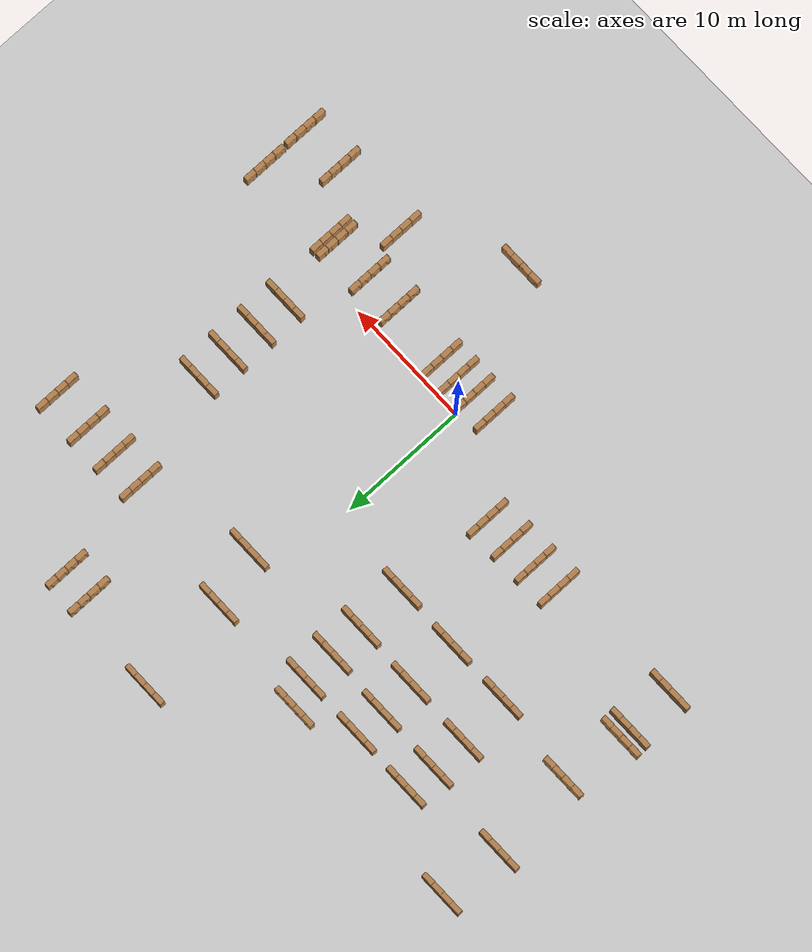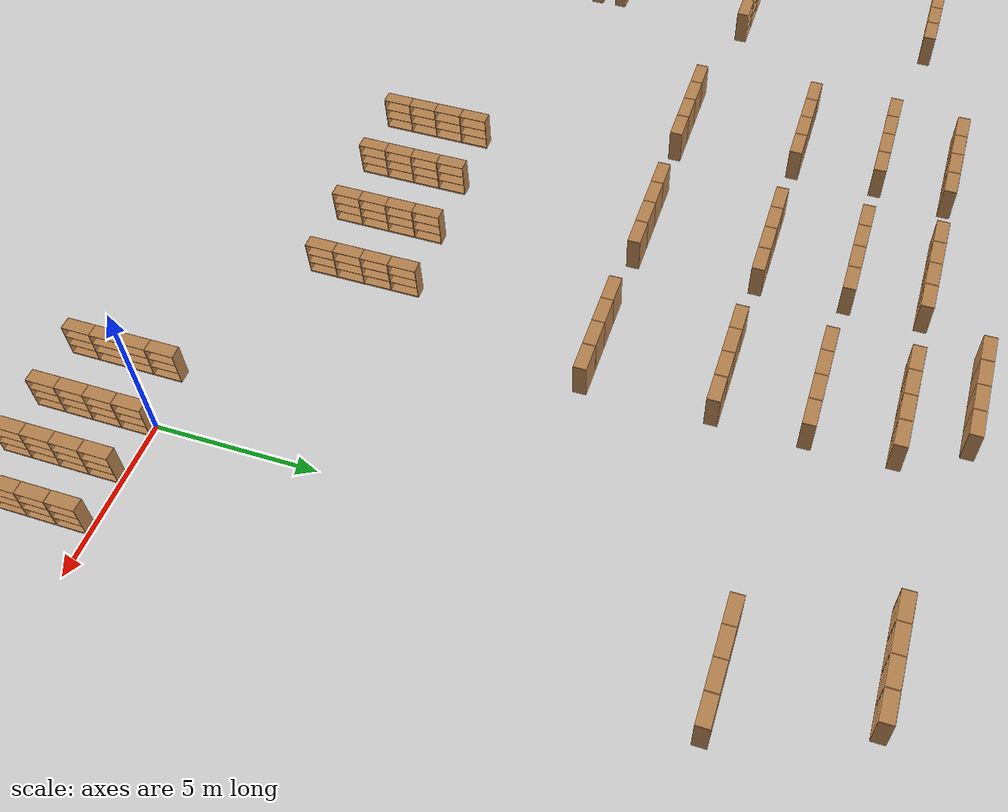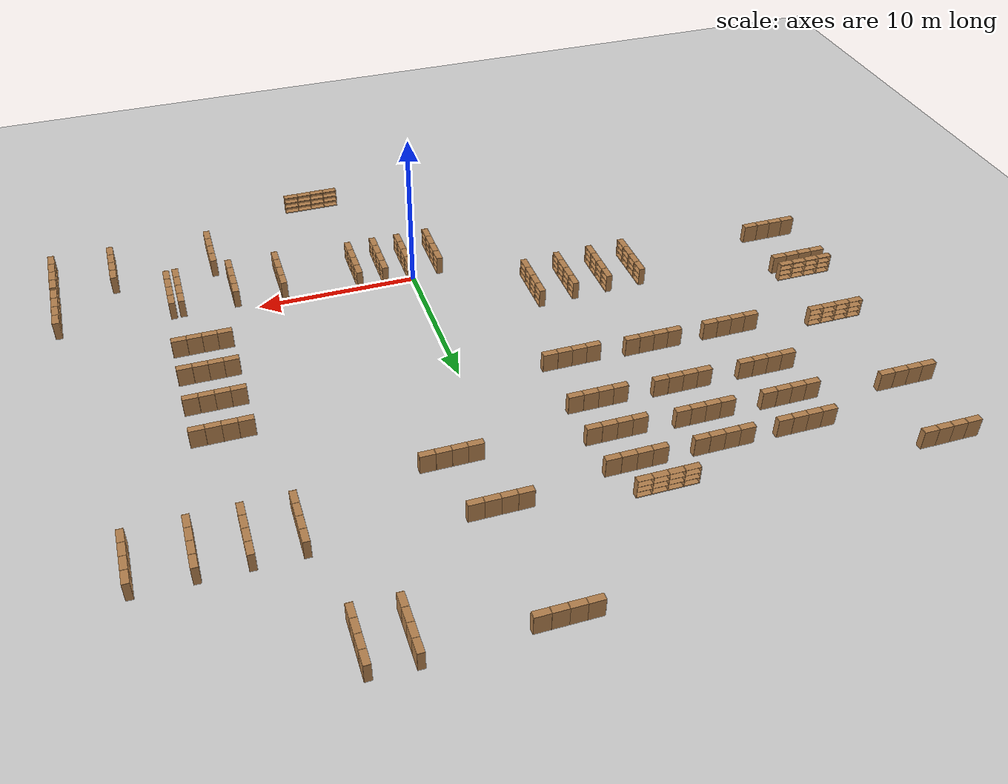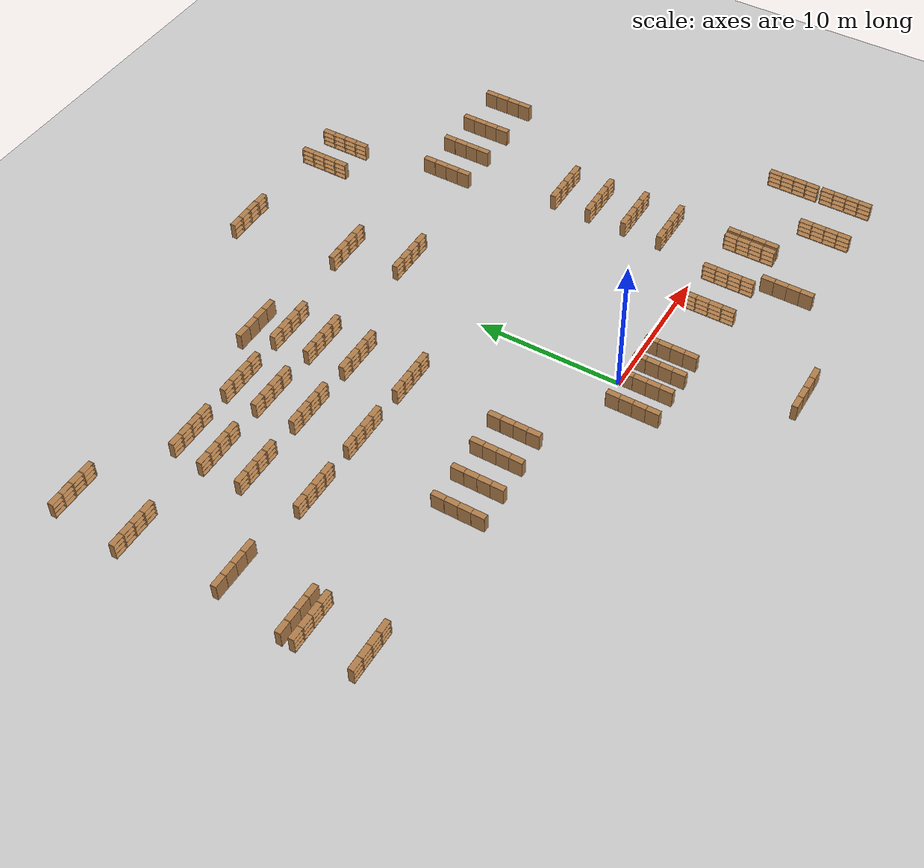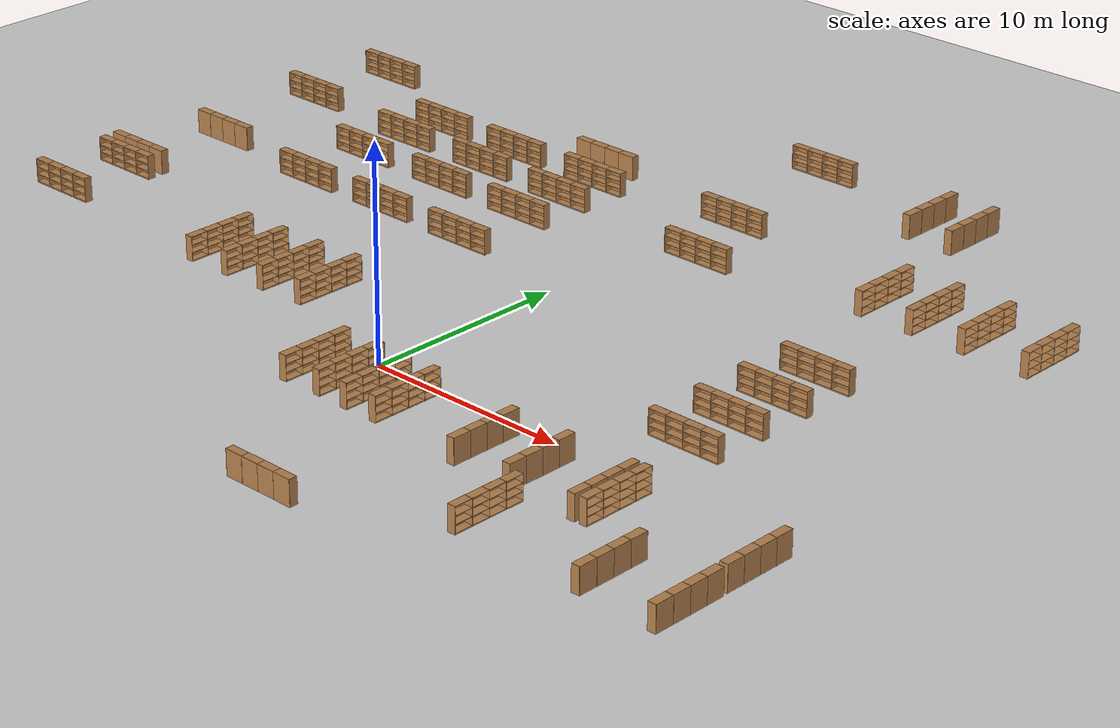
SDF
<sdf version="1.6">
 <world name="default">
  <light name="sun" type="directional">
   <pose>0 0 10 0 -0 0</pose>
   <diffuse>0.8 0.8 0.8 1</diffuse>
   <specular>0.2 0.2 0.2 1</specular>
   <attenuation>
    <range>1000</range>
    <constant>0.9</constant>
    <linear>0.01</linear>
    <quadratic>0.001</quadratic>
   </attenuation>
   <direction>-0.5 0.1 -0.9</direction>
  </light>
  <model name="ground_plane">
   <static>1</static>
   <link name="link">
    <collision name="collision">
     <geometry><plane><normal>0 0 1</normal><size>100 100</size></plane></geometry>
     <surface><friction><ode><mu>100</mu><mu2>50</mu2></ode></friction></surface>
    </collision>
    <visual name="visual">
     <cast_shadows>0</cast_shadows>
     <geometry><plane><normal>0 0 1</normal><size>100 100</size></plane></geometry>
     <material>
      <script><uri>file://media/materials/scripts/gazebo.material</uri><name>Gazebo/Grey</name></script>
     </material>
    </visual>
   </link>
  </model>
  <gravity>0 0 -9.8</gravity>
  <magnetic_field>6e-06 2.3e-05 -4.2e-05</magnetic_field>
  <atmosphere type="adiabatic"/>
  <physics name="default_physics" default="0" type="ode">
   <max_step_size>0.001</max_step_size>
   <real_time_factor>1</real_time_factor>
   <real_time_update_rate>1000</real_time_update_rate>
  </physics>
  <scene><ambient>0.4 0.4 0.4 1</ambient><background>0.7 0.7 0.7 1</background><shadows>1</shadows></scene>
  <audio><device>default</device></audio>
  <spherical_coordinates>
   <surface_model>EARTH_WGS84</surface_model>
   <latitude_deg>0</latitude_deg>
   <longitude_deg>0</longitude_deg>
   <elevation>0</elevation>
   <heading_deg>0</heading_deg>
  </spherical_coordinates>
  <model name="Bookself-4">
   <model name="Bookself-3">
    <model name="bookshelf_0">
     <static>1</static>
     <link name="link">
      <inertial><mass>1</mass></inertial>
      <collision name="back">
       <pose>0 0.005 0.6 0 -0 0</pose>
       <geometry><box><size>0.9 0.01 1.2</size></box></geometry>
      </collision>
      <visual name="visual1">
       <pose>0 0.005 0.6 0 -0 0</pose>
       <geometry><box><size>0.9 0.01 1.2</size></box></geometry>
       <material>
        <script><uri>file://media/materials/scripts/gazebo.material</uri><name>Gazebo/Wood</name></script>
       </material>
      </visual>
      <collision name="left_side">
       <pose>0.45 -0.195 0.6 0 -0 0</pose>
       <geometry><box><size>0.02 0.4 1.2</size></box></geometry>
      </collision>
      <visual name="visual2">
       <pose>0.45 -0.195 0.6 0 -0 0</pose>
       <geometry><box><size>0.02 0.4 1.2</size></box></geometry>
       <material>
        <script><uri>file://media/materials/scripts/gazebo.material</uri><name>Gazebo/Wood</name></script>
       </material>
      </visual>
      <collision name="right_side">
       <pose>-0.45 -0.195 0.6 0 -0 0</pose>
       <geometry><box><size>0.02 0.4 1.2</size></box></geometry>
      </collision>
      <visual name="visual3">
       <pose>-0.45 -0.195 0.6 0 -0 0</pose>
       <geometry><box><size>0.02 0.4 1.2</size></box></geometry>
       <material>
        <script><uri>file://media/materials/scripts/gazebo.material</uri><name>Gazebo/Wood</name></script>
       </material>
      </visual>
      <collision name="bottom">
       <pose>0 -0.195 0.03 0 -0 0</pose>
       <geometry><box><size>0.88 0.4 0.06</size></box></geometry>
      </collision>
      <visual name="visual4">
       <pose>0 -0.195 0.03 0 -0 0</pose>
       <geometry><box><size>0.88 0.4 0.06</size></box></geometry>
       <material>
        <script><uri>file://media/materials/scripts/gazebo.material</uri><name>Gazebo/Wood</name></script>
       </material>
      </visual>
      <collision name="top">
       <pose>0 -0.195 1.19 0 -0 0</pose>
       <geometry><box><size>0.88 0.4 0.02</size></box></geometry>
      </collision>
      <visual name="visual5">
       <pose>0 -0.195 1.19 0 -0 0</pose>
       <geometry><box><size>0.88 0.4 0.02</size></box></geometry>
       <material>
        <script><uri>file://media/materials/scripts/gazebo.material</uri><name>Gazebo/Wood</name></script>
       </material>
      </visual>
      <collision name="low_shelf">
       <pose>0 -0.195 0.43 0 -0 0</pose>
       <geometry><box><size>0.88 0.4 0.02</size></box></geometry>
      </collision>
      <visual name="visual6">
       <pose>0 -0.195 0.43 0 -0 0</pose>
       <geometry><box><size>0.88 0.4 0.02</size></box></geometry>
       <material>
        <script><uri>file://media/materials/scripts/gazebo.material</uri><name>Gazebo/Wood</name></script>
       </material>
      </visual>
      <collision name="high_shelf">
       <pose>0 -0.195 0.8 0 -0 0</pose>
       <geometry><box><size>0.88 0.4 0.02</size></box></geometry>
      </collision>
      <visual name="visual7">
       <pose>0 -0.195 0.8 0 -0 0</pose>
       <geometry><box><size>0.88 0.4 0.02</size></box></geometry>
       <material>
        <script><uri>file://media/materials/scripts/gazebo.material</uri><name>Gazebo/Wood</name></script>
       </material>
      </visual>
     </link>
     <pose>-0.903039 0 0 0 -0 0</pose>
    </model>
    <model name="bookshelf_1">
     <static>1</static>
     <link name="link">
      <inertial><mass>1</mass></inertial>
      <collision name="back">
       <pose>0 0.005 0.6 0 -0 0</pose>
       <geometry><box><size>0.9 0.01 1.2</size></box></geometry>
      </collision>
      <visual name="visual1">
       <pose>0 0.005 0.6 0 -0 0</pose>
       <geometry><box><size>0.9 0.01 1.2</size></box></geometry>
       <material>
        <script><uri>file://media/materials/scripts/gazebo.material</uri><name>Gazebo/Wood</name></script>
       </material>
      </visual>
      <collision name="left_side">
       <pose>0.45 -0.195 0.6 0 -0 0</pose>
       <geometry><box><size>0.02 0.4 1.2</size></box></geometry>
      </collision>
      <visual name="visual2">
       <pose>0.45 -0.195 0.6 0 -0 0</pose>
       <geometry><box><size>0.02 0.4 1.2</size></box></geometry>
       <material>
        <script><uri>file://media/materials/scripts/gazebo.material</uri><name>Gazebo/Wood</name></script>
       </material>
      </visual>
      <collision name="right_side">
       <pose>-0.45 -0.195 0.6 0 -0 0</pose>
       <geometry><box><size>0.02 0.4 1.2</size></box></geometry>
      </collision>
      <visual name="visual3">
       <pose>-0.45 -0.195 0.6 0 -0 0</pose>
       <geometry><box><size>0.02 0.4 1.2</size></box></geometry>
       <material>
        <script><uri>file://media/materials/scripts/gazebo.material</uri><name>Gazebo/Wood</name></script>
       </material>
      </visual>
      <collision name="bottom">
       <pose>0 -0.195 0.03 0 -0 0</pose>
       <geometry><box><size>0.88 0.4 0.06</size></box></geometry>
      </collision>
      <visual name="visual4">
       <pose>0 -0.195 0.03 0 -0 0</pose>
       <geometry><box><size>0.88 0.4 0.06</size></box></geometry>
       <material>
        <script><uri>file://media/materials/scripts/gazebo.material</uri><name>Gazebo/Wood</name></script>
       </material>
      </visual>
      <collision name="top">
       <pose>0 -0.195 1.19 0 -0 0</pose>
       <geometry><box><size>0.88 0.4 0.02</size></box></geometry>
      </collision>
      <visual name="visual5">
       <pose>0 -0.195 1.19 0 -0 0</pose>
       <geometry><box><size>0.88 0.4 0.02</size></box></geometry>
       <material>
        <script><uri>file://media/materials/scripts/gazebo.material</uri><name>Gazebo/Wood</name></script>
       </material>
      </visual>
      <collision name="low_shelf">
       <pose>0 -0.195 0.43 0 -0 0</pose>
       <geometry><box><size>0.88 0.4 0.02</size></box></geometry>
      </collision>
      <visual name="visual6">
       <pose>0 -0.195 0.43 0 -0 0</pose>
       <geometry><box><size>0.88 0.4 0.02</size></box></geometry>
       <material>
        <script><uri>file://media/materials/scripts/gazebo.material</uri><name>Gazebo/Wood</name></script>
       </material>
      </visual>
      <collision name="high_shelf">
       <pose>0 -0.195 0.8 0 -0 0</pose>
       <geometry><box><size>0.88 0.4 0.02</size></box></geometry>
      </collision>
      <visual name="visual7">
       <pose>0 -0.195 0.8 0 -0 0</pose>
       <geometry><box><size>0.88 0.4 0.02</size></box></geometry>
       <material>
        <script><uri>file://media/materials/scripts/gazebo.material</uri><name>Gazebo/Wood</name></script>
       </material>
      </visual>
     </link>
     <pose>0.000535 0 0 0 -0 0</pose>
    </model>
    <model name="bookshelf_1_clone">
     <static>1</static>
     <link name="link">
      <inertial><mass>1</mass></inertial>
      <collision name="back">
       <pose>0 0.005 0.6 0 -0 0</pose>
       <geometry><box><size>0.9 0.01 1.2</size></box></geometry>
      </collision>
      <visual name="visual1">
       <pose>0 0.005 0.6 0 -0 0</pose>
       <geometry><box><size>0.9 0.01 1.2</size></box></geometry>
       <material>
        <script><uri>file://media/materials/scripts/gazebo.material</uri><name>Gazebo/Wood</name></script>
       </material>
      </visual>
      <collision name="left_side">
       <pose>0.45 -0.195 0.6 0 -0 0</pose>
       <geometry><box><size>0.02 0.4 1.2</size></box></geometry>
      </collision>
      <visual name="visual2">
       <pose>0.45 -0.195 0.6 0 -0 0</pose>
       <geometry><box><size>0.02 0.4 1.2</size></box></geometry>
       <material>
        <script><uri>file://media/materials/scripts/gazebo.material</uri><name>Gazebo/Wood</name></script>
       </material>
      </visual>
      <collision name="right_side">
       <pose>-0.45 -0.195 0.6 0 -0 0</pose>
       <geometry><box><size>0.02 0.4 1.2</size></box></geometry>
      </collision>
      <visual name="visual3">
       <pose>-0.45 -0.195 0.6 0 -0 0</pose>
       <geometry><box><size>0.02 0.4 1.2</size></box></geometry>
       <material>
        <script><uri>file://media/materials/scripts/gazebo.material</uri><name>Gazebo/Wood</name></script>
       </material>
      </visual>
      <collision name="bottom">
       <pose>0 -0.195 0.03 0 -0 0</pose>
       <geometry><box><size>0.88 0.4 0.06</size></box></geometry>
      </collision>
      <visual name="visual4">
       <pose>0 -0.195 0.03 0 -0 0</pose>
       <geometry><box><size>0.88 0.4 0.06</size></box></geometry>
       <material>
        <script><uri>file://media/materials/scripts/gazebo.material</uri><name>Gazebo/Wood</name></script>
       </material>
      </visual>
      <collision name="top">
       <pose>0 -0.195 1.19 0 -0 0</pose>
       <geometry><box><size>0.88 0.4 0.02</size></box></geometry>
      </collision>
      <visual name="visual5">
       <pose>0 -0.195 1.19 0 -0 0</pose>
       <geometry><box><size>0.88 0.4 0.02</size></box></geometry>
       <material>
        <script><uri>file://media/materials/scripts/gazebo.material</uri><name>Gazebo/Wood</name></script>
       </material>
      </visual>
      <collision name="low_shelf">
       <pose>0 -0.195 0.43 0 -0 0</pose>
       <geometry><box><size>0.88 0.4 0.02</size></box></geometry>
      </collision>
      <visual name="visual6">
       <pose>0 -0.195 0.43 0 -0 0</pose>
       <geometry><box><size>0.88 0.4 0.02</size></box></geometry>
       <material>
        <script><uri>file://media/materials/scripts/gazebo.material</uri><name>Gazebo/Wood</name></script>
       </material>
      </visual>
      <collision name="high_shelf">
       <pose>0 -0.195 0.8 0 -0 0</pose>
       <geometry><box><size>0.88 0.4 0.02</size></box></geometry>
      </collision>
      <visual name="visual7">
       <pose>0 -0.195 0.8 0 -0 0</pose>
       <geometry><box><size>0.88 0.4 0.02</size></box></geometry>
       <material>
        <script><uri>file://media/materials/scripts/gazebo.material</uri><name>Gazebo/Wood</name></script>
       </material>
      </visual>
     </link>
     <pose>0.902502 0 0 0 -0 0</pose>
    </model>
    <static>1</static>
    <pose>-0.906894 3e-05 0 0 -0 0</pose>
   </model>
   <model name="bookshelf">
    <static>1</static>
    <link name="link">
     <inertial><mass>1</mass></inertial>
     <collision name="back">
      <pose>0 0.005 0.6 0 -0 0</pose>
      <geometry><box><size>0.9 0.01 1.2</size></box></geometry>
     </collision>
     <visual name="visual1">
      <pose>0 0.005 0.6 0 -0 0</pose>
      <geometry><box><size>0.9 0.01 1.2</size></box></geometry>
      <material>
       <script><uri>file://media/materials/scripts/gazebo.material</uri><name>Gazebo/Wood</name></script>
      </material>
     </visual>
     <collision name="left_side">
      <pose>0.45 -0.195 0.6 0 -0 0</pose>
      <geometry><box><size>0.02 0.4 1.2</size></box></geometry>
     </collision>
     <visual name="visual2">
      <pose>0.45 -0.195 0.6 0 -0 0</pose>
      <geometry><box><size>0.02 0.4 1.2</size></box></geometry>
      <material>
       <script><uri>file://media/materials/scripts/gazebo.material</uri><name>Gazebo/Wood</name></script>
      </material>
     </visual>
     <collision name="right_side">
      <pose>-0.45 -0.195 0.6 0 -0 0</pose>
      <geometry><box><size>0.02 0.4 1.2</size></box></geometry>
     </collision>
     <visual name="visual3">
      <pose>-0.45 -0.195 0.6 0 -0 0</pose>
      <geometry><box><size>0.02 0.4 1.2</size></box></geometry>
      <material>
       <script><uri>file://media/materials/scripts/gazebo.material</uri><name>Gazebo/Wood</name></script>
      </material>
     </visual>
     <collision name="bottom">
      <pose>0 -0.195 0.03 0 -0 0</pose>
      <geometry><box><size>0.88 0.4 0.06</size></box></geometry>
     </collision>
     <visual name="visual4">
      <pose>0 -0.195 0.03 0 -0 0</pose>
      <geometry><box><size>0.88 0.4 0.06</size></box></geometry>
      <material>
       <script><uri>file://media/materials/scripts/gazebo.material</uri><name>Gazebo/Wood</name></script>
      </material>
     </visual>
     <collision name="top">
      <pose>0 -0.195 1.19 0 -0 0</pose>
      <geometry><box><size>0.88 0.4 0.02</size></box></geometry>
     </collision>
     <visual name="visual5">
      <pose>0 -0.195 1.19 0 -0 0</pose>
      <geometry><box><size>0.88 0.4 0.02</size></box></geometry>
      <material>
       <script><uri>file://media/materials/scripts/gazebo.material</uri><name>Gazebo/Wood</name></script>
      </material>
     </visual>
     <collision name="low_shelf">
      <pose>0 -0.195 0.43 0 -0 0</pose>
      <geometry><box><size>0.88 0.4 0.02</size></box></geometry>
     </collision>
     <visual name="visual6">
      <pose>0 -0.195 0.43 0 -0 0</pose>
      <geometry><box><size>0.88 0.4 0.02</size></box></geometry>
      <material>
       <script><uri>file://media/materials/scripts/gazebo.material</uri><name>Gazebo/Wood</name></script>
      </material>
     </visual>
     <collision name="high_shelf">
      <pose>0 -0.195 0.8 0 -0 0</pose>
      <geometry><box><size>0.88 0.4 0.02</size></box></geometry>
     </collision>
     <visual name="visual7">
      <pose>0 -0.195 0.8 0 -0 0</pose>
      <geometry><box><size>0.88 0.4 0.02</size></box></geometry>
      <material>
       <script><uri>file://media/materials/scripts/gazebo.material</uri><name>Gazebo/Wood</name></script>
      </material>
     </visual>
    </link>
    <pose>0.906808 3e-05 0 0 -0 0</pose>
   </model>
   <static>0</static>
   <pose>-16.4159 20.5026 0 0 -0 0</pose>
  </model>
  <model name="Bookself-4_clone">
   <model name="Bookself-3">
    <model name="bookshelf_0">
     <static>1</static>
     <link name="link">
      <inertial><mass>1</mass></inertial>
      <collision name="back">
       <pose>0 0.005 0.6 0 -0 0</pose>
       <geometry><box><size>0.9 0.01 1.2</size></box></geometry>
      </collision>
      <visual name="visual1">
       <pose>0 0.005 0.6 0 -0 0</pose>
       <geometry><box><size>0.9 0.01 1.2</size></box></geometry>
       <material>
        <script><uri>file://media/materials/scripts/gazebo.material</uri><name>Gazebo/Wood</name></script>
       </material>
      </visual>
      <collision name="left_side">
       <pose>0.45 -0.195 0.6 0 -0 0</pose>
       <geometry><box><size>0.02 0.4 1.2</size></box></geometry>
      </collision>
      <visual name="visual2">
       <pose>0.45 -0.195 0.6 0 -0 0</pose>
       <geometry><box><size>0.02 0.4 1.2</size></box></geometry>
       <material>
        <script><uri>file://media/materials/scripts/gazebo.material</uri><name>Gazebo/Wood</name></script>
       </material>
      </visual>
      <collision name="right_side">
       <pose>-0.45 -0.195 0.6 0 -0 0</pose>
       <geometry><box><size>0.02 0.4 1.2</size></box></geometry>
      </collision>
      <visual name="visual3">
       <pose>-0.45 -0.195 0.6 0 -0 0</pose>
       <geometry><box><size>0.02 0.4 1.2</size></box></geometry>
       <material>
        <script><uri>file://media/materials/scripts/gazebo.material</uri><name>Gazebo/Wood</name></script>
       </material>
      </visual>
      <collision name="bottom">
       <pose>0 -0.195 0.03 0 -0 0</pose>
       <geometry><box><size>0.88 0.4 0.06</size></box></geometry>
      </collision>
      <visual name="visual4">
       <pose>0 -0.195 0.03 0 -0 0</pose>
       <geometry><box><size>0.88 0.4 0.06</size></box></geometry>
       <material>
        <script><uri>file://media/materials/scripts/gazebo.material</uri><name>Gazebo/Wood</name></script>
       </material>
      </visual>
      <collision name="top">
       <pose>0 -0.195 1.19 0 -0 0</pose>
       <geometry><box><size>0.88 0.4 0.02</size></box></geometry>
      </collision>
      <visual name="visual5">
       <pose>0 -0.195 1.19 0 -0 0</pose>
       <geometry><box><size>0.88 0.4 0.02</size></box></geometry>
       <material>
        <script><uri>file://media/materials/scripts/gazebo.material</uri><name>Gazebo/Wood</name></script>
       </material>
      </visual>
      <collision name="low_shelf">
       <pose>0 -0.195 0.43 0 -0 0</pose>
       <geometry><box><size>0.88 0.4 0.02</size></box></geometry>
      </collision>
      <visual name="visual6">
       <pose>0 -0.195 0.43 0 -0 0</pose>
       <geometry><box><size>0.88 0.4 0.02</size></box></geometry>
       <material>
        <script><uri>file://media/materials/scripts/gazebo.material</uri><name>Gazebo/Wood</name></script>
       </material>
      </visual>
      <collision name="high_shelf">
       <pose>0 -0.195 0.8 0 -0 0</pose>
       <geometry><box><size>0.88 0.4 0.02</size></box></geometry>
      </collision>
      <visual name="visual7">
       <pose>0 -0.195 0.8 0 -0 0</pose>
       <geometry><box><size>0.88 0.4 0.02</size></box></geometry>
       <material>
        <script><uri>file://media/materials/scripts/gazebo.material</uri><name>Gazebo/Wood</name></script>
       </material>
      </visual>
     </link>
     <pose>-0.903039 0 0 0 -0 0</pose>
    </model>
    <model name="bookshelf_1">
     <static>1</static>
     <link name="link">
      <inertial><mass>1</mass></inertial>
      <collision name="back">
       <pose>0 0.005 0.6 0 -0 0</pose>
       <geometry><box><size>0.9 0.01 1.2</size></box></geometry>
      </collision>
      <visual name="visual1">
       <pose>0 0.005 0.6 0 -0 0</pose>
       <geometry><box><size>0.9 0.01 1.2</size></box></geometry>
       <material>
        <script><uri>file://media/materials/scripts/gazebo.material</uri><name>Gazebo/Wood</name></script>
       </material>
      </visual>
      <collision name="left_side">
       <pose>0.45 -0.195 0.6 0 -0 0</pose>
       <geometry><box><size>0.02 0.4 1.2</size></box></geometry>
      </collision>
      <visual name="visual2">
       <pose>0.45 -0.195 0.6 0 -0 0</pose>
       <geometry><box><size>0.02 0.4 1.2</size></box></geometry>
       <material>
        <script><uri>file://media/materials/scripts/gazebo.material</uri><name>Gazebo/Wood</name></script>
       </material>
      </visual>
      <collision name="right_side">
       <pose>-0.45 -0.195 0.6 0 -0 0</pose>
       <geometry><box><size>0.02 0.4 1.2</size></box></geometry>
      </collision>
      <visual name="visual3">
       <pose>-0.45 -0.195 0.6 0 -0 0</pose>
       <geometry><box><size>0.02 0.4 1.2</size></box></geometry>
       <material>
        <script><uri>file://media/materials/scripts/gazebo.material</uri><name>Gazebo/Wood</name></script>
       </material>
      </visual>
      <collision name="bottom">
       <pose>0 -0.195 0.03 0 -0 0</pose>
       <geometry><box><size>0.88 0.4 0.06</size></box></geometry>
      </collision>
      <visual name="visual4">
       <pose>0 -0.195 0.03 0 -0 0</pose>
       <geometry><box><size>0.88 0.4 0.06</size></box></geometry>
       <material>
        <script><uri>file://media/materials/scripts/gazebo.material</uri><name>Gazebo/Wood</name></script>
       </material>
      </visual>
      <collision name="top">
       <pose>0 -0.195 1.19 0 -0 0</pose>
       <geometry><box><size>0.88 0.4 0.02</size></box></geometry>
      </collision>
      <visual name="visual5">
       <pose>0 -0.195 1.19 0 -0 0</pose>
       <geometry><box><size>0.88 0.4 0.02</size></box></geometry>
       <material>
        <script><uri>file://media/materials/scripts/gazebo.material</uri><name>Gazebo/Wood</name></script>
       </material>
      </visual>
      <collision name="low_shelf">
       <pose>0 -0.195 0.43 0 -0 0</pose>
       <geometry><box><size>0.88 0.4 0.02</size></box></geometry>
      </collision>
      <visual name="visual6">
       <pose>0 -0.195 0.43 0 -0 0</pose>
       <geometry><box><size>0.88 0.4 0.02</size></box></geometry>
       <material>
        <script><uri>file://media/materials/scripts/gazebo.material</uri><name>Gazebo/Wood</name></script>
       </material>
      </visual>
      <collision name="high_shelf">
       <pose>0 -0.195 0.8 0 -0 0</pose>
       <geometry><box><size>0.88 0.4 0.02</size></box></geometry>
      </collision>
      <visual name="visual7">
       <pose>0 -0.195 0.8 0 -0 0</pose>
       <geometry><box><size>0.88 0.4 0.02</size></box></geometry>
       <material>
        <script><uri>file://media/materials/scripts/gazebo.material</uri><name>Gazebo/Wood</name></script>
       </material>
      </visual>
     </link>
     <pose>0.000535 0 0 0 -0 0</pose>
    </model>
    <model name="bookshelf_1_clone">
     <static>1</static>
     <link name="link">
      <inertial><mass>1</mass></inertial>
      <collision name="back">
       <pose>0 0.005 0.6 0 -0 0</pose>
       <geometry><box><size>0.9 0.01 1.2</size></box></geometry>
      </collision>
      <visual name="visual1">
       <pose>0 0.005 0.6 0 -0 0</pose>
       <geometry><box><size>0.9 0.01 1.2</size></box></geometry>
       <material>
        <script><uri>file://media/materials/scripts/gazebo.material</uri><name>Gazebo/Wood</name></script>
       </material>
      </visual>
      <collision name="left_side">
       <pose>0.45 -0.195 0.6 0 -0 0</pose>
       <geometry><box><size>0.02 0.4 1.2</size></box></geometry>
      </collision>
      <visual name="visual2">
       <pose>0.45 -0.195 0.6 0 -0 0</pose>
       <geometry><box><size>0.02 0.4 1.2</size></box></geometry>
       <material>
        <script><uri>file://media/materials/scripts/gazebo.material</uri><name>Gazebo/Wood</name></script>
       </material>
      </visual>
      <collision name="right_side">
       <pose>-0.45 -0.195 0.6 0 -0 0</pose>
       <geometry><box><size>0.02 0.4 1.2</size></box></geometry>
      </collision>
      <visual name="visual3">
       <pose>-0.45 -0.195 0.6 0 -0 0</pose>
       <geometry><box><size>0.02 0.4 1.2</size></box></geometry>
       <material>
        <script><uri>file://media/materials/scripts/gazebo.material</uri><name>Gazebo/Wood</name></script>
       </material>
      </visual>
      <collision name="bottom">
       <pose>0 -0.195 0.03 0 -0 0</pose>
       <geometry><box><size>0.88 0.4 0.06</size></box></geometry>
      </collision>
      <visual name="visual4">
       <pose>0 -0.195 0.03 0 -0 0</pose>
       <geometry><box><size>0.88 0.4 0.06</size></box></geometry>
       <material>
        <script><uri>file://media/materials/scripts/gazebo.material</uri><name>Gazebo/Wood</name></script>
       </material>
      </visual>
      <collision name="top">
       <pose>0 -0.195 1.19 0 -0 0</pose>
       <geometry><box><size>0.88 0.4 0.02</size></box></geometry>
      </collision>
      <visual name="visual5">
       <pose>0 -0.195 1.19 0 -0 0</pose>
       <geometry><box><size>0.88 0.4 0.02</size></box></geometry>
       <material>
        <script><uri>file://media/materials/scripts/gazebo.material</uri><name>Gazebo/Wood</name></script>
       </material>
      </visual>
      <collision name="low_shelf">
       <pose>0 -0.195 0.43 0 -0 0</pose>
       <geometry><box><size>0.88 0.4 0.02</size></box></geometry>
      </collision>
      <visual name="visual6">
       <pose>0 -0.195 0.43 0 -0 0</pose>
       <geometry><box><size>0.88 0.4 0.02</size></box></geometry>
       <material>
        <script><uri>file://media/materials/scripts/gazebo.material</uri><name>Gazebo/Wood</name></script>
       </material>
      </visual>
      <collision name="high_shelf">
       <pose>0 -0.195 0.8 0 -0 0</pose>
       <geometry><box><size>0.88 0.4 0.02</size></box></geometry>
      </collision>
      <visual name="visual7">
       <pose>0 -0.195 0.8 0 -0 0</pose>
       <geometry><box><size>0.88 0.4 0.02</size></box></geometry>
       <material>
        <script><uri>file://media/materials/scripts/gazebo.material</uri><name>Gazebo/Wood</name></script>
       </material>
      </visual>
     </link>
     <pose>0.902502 0 0 0 -0 0</pose>
    </model>
    <static>1</static>
    <pose>-0.906894 3e-05 0 0 -0 0</pose>
   </model>
   <model name="bookshelf">
    <static>1</static>
    <link name="link">
     <inertial><mass>1</mass></inertial>
     <collision name="back">
      <pose>0 0.005 0.6 0 -0 0</pose>
      <geometry><box><size>0.9 0.01 1.2</size></box></geometry>
     </collision>
     <visual name="visual1">
      <pose>0 0.005 0.6 0 -0 0</pose>
      <geometry><box><size>0.9 0.01 1.2</size></box></geometry>
      <material>
       <script><uri>file://media/materials/scripts/gazebo.material</uri><name>Gazebo/Wood</name></script>
      </material>
     </visual>
     <collision name="left_side">
      <pose>0.45 -0.195 0.6 0 -0 0</pose>
      <geometry><box><size>0.02 0.4 1.2</size></box></geometry>
     </collision>
     <visual name="visual2">
      <pose>0.45 -0.195 0.6 0 -0 0</pose>
      <geometry><box><size>0.02 0.4 1.2</size></box></geometry>
      <material>
       <script><uri>file://media/materials/scripts/gazebo.material</uri><name>Gazebo/Wood</name></script>
      </material>
     </visual>
     <collision name="right_side">
      <pose>-0.45 -0.195 0.6 0 -0 0</pose>
      <geometry><box><size>0.02 0.4 1.2</size></box></geometry>
     </collision>
     <visual name="visual3">
      <pose>-0.45 -0.195 0.6 0 -0 0</pose>
      <geometry><box><size>0.02 0.4 1.2</size></box></geometry>
      <material>
       <script><uri>file://media/materials/scripts/gazebo.material</uri><name>Gazebo/Wood</name></script>
      </material>
     </visual>
     <collision name="bottom">
      <pose>0 -0.195 0.03 0 -0 0</pose>
      <geometry><box><size>0.88 0.4 0.06</size></box></geometry>
     </collision>
     <visual name="visual4">
      <pose>0 -0.195 0.03 0 -0 0</pose>
      <geometry><box><size>0.88 0.4 0.06</size></box></geometry>
      <material>
       <script><uri>file://media/materials/scripts/gazebo.material</uri><name>Gazebo/Wood</name></script>
      </material>
     </visual>
     <collision name="top">
      <pose>0 -0.195 1.19 0 -0 0</pose>
      <geometry><box><size>0.88 0.4 0.02</size></box></geometry>
     </collision>
     <visual name="visual5">
      <pose>0 -0.195 1.19 0 -0 0</pose>
      <geometry><box><size>0.88 0.4 0.02</size></box></geometry>
      <material>
       <script><uri>file://media/materials/scripts/gazebo.material</uri><name>Gazebo/Wood</name></script>
      </material>
     </visual>
     <collision name="low_shelf">
      <pose>0 -0.195 0.43 0 -0 0</pose>
      <geometry><box><size>0.88 0.4 0.02</size></box></geometry>
     </collision>
     <visual name="visual6">
      <pose>0 -0.195 0.43 0 -0 0</pose>
      <geometry><box><size>0.88 0.4 0.02</size></box></geometry>
      <material>
       <script><uri>file://media/materials/scripts/gazebo.material</uri><name>Gazebo/Wood</name></script>
      </material>
     </visual>
     <collision name="high_shelf">
      <pose>0 -0.195 0.8 0 -0 0</pose>
      <geometry><box><size>0.88 0.4 0.02</size></box></geometry>
     </collision>
     <visual name="visual7">
      <pose>0 -0.195 0.8 0 -0 0</pose>
      <geometry><box><size>0.88 0.4 0.02</size></box></geometry>
      <material>
       <script><uri>file://media/materials/scripts/gazebo.material</uri><name>Gazebo/Wood</name></script>
      </material>
     </visual>
    </link>
    <pose>0.906808 3e-05 0 0 -0 0</pose>
   </model>
   <static>0</static>
   <pose>-11.4157 20.4728 0 0 -0 0</pose>
  </model>
  <model name="Bookself-4_clone_0">
   <model name="Bookself-3">
    <model name="bookshelf_0">
     <static>1</static>
     <link name="link">
      <inertial><mass>1</mass></inertial>
      <collision name="back">
       <pose>0 0.005 0.6 0 -0 0</pose>
       <geometry><box><size>0.9 0.01 1.2</size></box></geometry>
      </collision>
      <visual name="visual1">
       <pose>0 0.005 0.6 0 -0 0</pose>
       <geometry><box><size>0.9 0.01 1.2</size></box></geometry>
       <material>
        <script><uri>file://media/materials/scripts/gazebo.material</uri><name>Gazebo/Wood</name></script>
       </material>
      </visual>
      <collision name="left_side">
       <pose>0.45 -0.195 0.6 0 -0 0</pose>
       <geometry><box><size>0.02 0.4 1.2</size></box></geometry>
      </collision>
      <visual name="visual2">
       <pose>0.45 -0.195 0.6 0 -0 0</pose>
       <geometry><box><size>0.02 0.4 1.2</size></box></geometry>
       <material>
        <script><uri>file://media/materials/scripts/gazebo.material</uri><name>Gazebo/Wood</name></script>
       </material>
      </visual>
      <collision name="right_side">
       <pose>-0.45 -0.195 0.6 0 -0 0</pose>
       <geometry><box><size>0.02 0.4 1.2</size></box></geometry>
      </collision>
      <visual name="visual3">
       <pose>-0.45 -0.195 0.6 0 -0 0</pose>
       <geometry><box><size>0.02 0.4 1.2</size></box></geometry>
       <material>
        <script><uri>file://media/materials/scripts/gazebo.material</uri><name>Gazebo/Wood</name></script>
       </material>
      </visual>
      <collision name="bottom">
       <pose>0 -0.195 0.03 0 -0 0</pose>
       <geometry><box><size>0.88 0.4 0.06</size></box></geometry>
      </collision>
      <visual name="visual4">
       <pose>0 -0.195 0.03 0 -0 0</pose>
       <geometry><box><size>0.88 0.4 0.06</size></box></geometry>
       <material>
        <script><uri>file://media/materials/scripts/gazebo.material</uri><name>Gazebo/Wood</name></script>
       </material>
      </visual>
      <collision name="top">
       <pose>0 -0.195 1.19 0 -0 0</pose>
       <geometry><box><size>0.88 0.4 0.02</size></box></geometry>
      </collision>
      <visual name="visual5">
       <pose>0 -0.195 1.19 0 -0 0</pose>
       <geometry><box><size>0.88 0.4 0.02</size></box></geometry>
       <material>
        <script><uri>file://media/materials/scripts/gazebo.material</uri><name>Gazebo/Wood</name></script>
       </material>
      </visual>
      <collision name="low_shelf">
       <pose>0 -0.195 0.43 0 -0 0</pose>
       <geometry><box><size>0.88 0.4 0.02</size></box></geometry>
      </collision>
      <visual name="visual6">
       <pose>0 -0.195 0.43 0 -0 0</pose>
       <geometry><box><size>0.88 0.4 0.02</size></box></geometry>
       <material>
        <script><uri>file://media/materials/scripts/gazebo.material</uri><name>Gazebo/Wood</name></script>
       </material>
      </visual>
      <collision name="high_shelf">
       <pose>0 -0.195 0.8 0 -0 0</pose>
       <geometry><box><size>0.88 0.4 0.02</size></box></geometry>
      </collision>
      <visual name="visual7">
       <pose>0 -0.195 0.8 0 -0 0</pose>
       <geometry><box><size>0.88 0.4 0.02</size></box></geometry>
       <material>
        <script><uri>file://media/materials/scripts/gazebo.material</uri><name>Gazebo/Wood</name></script>
       </material>
      </visual>
     </link>
     <pose>-0.903039 0 0 0 -0 0</pose>
    </model>
    <model name="bookshelf_1">
     <static>1</static>
     <link name="link">
      <inertial><mass>1</mass></inertial>
      <collision name="back">
       <pose>0 0.005 0.6 0 -0 0</pose>
       <geometry><box><size>0.9 0.01 1.2</size></box></geometry>
      </collision>
      <visual name="visual1">
       <pose>0 0.005 0.6 0 -0 0</pose>
       <geometry><box><size>0.9 0.01 1.2</size></box></geometry>
       <material>
        <script><uri>file://media/materials/scripts/gazebo.material</uri><name>Gazebo/Wood</name></script>
       </material>
      </visual>
      <collision name="left_side">
       <pose>0.45 -0.195 0.6 0 -0 0</pose>
       <geometry><box><size>0.02 0.4 1.2</size></box></geometry>
      </collision>
      <visual name="visual2">
       <pose>0.45 -0.195 0.6 0 -0 0</pose>
       <geometry><box><size>0.02 0.4 1.2</size></box></geometry>
       <material>
        <script><uri>file://media/materials/scripts/gazebo.material</uri><name>Gazebo/Wood</name></script>
       </material>
      </visual>
      <collision name="right_side">
       <pose>-0.45 -0.195 0.6 0 -0 0</pose>
       <geometry><box><size>0.02 0.4 1.2</size></box></geometry>
      </collision>
      <visual name="visual3">
       <pose>-0.45 -0.195 0.6 0 -0 0</pose>
       <geometry><box><size>0.02 0.4 1.2</size></box></geometry>
       <material>
        <script><uri>file://media/materials/scripts/gazebo.material</uri><name>Gazebo/Wood</name></script>
       </material>
      </visual>
      <collision name="bottom">
       <pose>0 -0.195 0.03 0 -0 0</pose>
       <geometry><box><size>0.88 0.4 0.06</size></box></geometry>
      </collision>
      <visual name="visual4">
       <pose>0 -0.195 0.03 0 -0 0</pose>
       <geometry><box><size>0.88 0.4 0.06</size></box></geometry>
       <material>
        <script><uri>file://media/materials/scripts/gazebo.material</uri><name>Gazebo/Wood</name></script>
       </material>
      </visual>
      <collision name="top">
       <pose>0 -0.195 1.19 0 -0 0</pose>
       <geometry><box><size>0.88 0.4 0.02</size></box></geometry>
      </collision>
      <visual name="visual5">
       <pose>0 -0.195 1.19 0 -0 0</pose>
       <geometry><box><size>0.88 0.4 0.02</size></box></geometry>
       <material>
        <script><uri>file://media/materials/scripts/gazebo.material</uri><name>Gazebo/Wood</name></script>
       </material>
      </visual>
      <collision name="low_shelf">
       <pose>0 -0.195 0.43 0 -0 0</pose>
       <geometry><box><size>0.88 0.4 0.02</size></box></geometry>
      </collision>
      <visual name="visual6">
       <pose>0 -0.195 0.43 0 -0 0</pose>
       <geometry><box><size>0.88 0.4 0.02</size></box></geometry>
       <material>
        <script><uri>file://media/materials/scripts/gazebo.material</uri><name>Gazebo/Wood</name></script>
       </material>
      </visual>
      <collision name="high_shelf">
       <pose>0 -0.195 0.8 0 -0 0</pose>
       <geometry><box><size>0.88 0.4 0.02</size></box></geometry>
      </collision>
      <visual name="visual7">
       <pose>0 -0.195 0.8 0 -0 0</pose>
       <geometry><box><size>0.88 0.4 0.02</size></box></geometry>
       <material>
        <script><uri>file://media/materials/scripts/gazebo.material</uri><name>Gazebo/Wood</name></script>
       </material>
      </visual>
     </link>
     <pose>0.000535 0 0 0 -0 0</pose>
    </model>
    <model name="bookshelf_1_clone">
     <static>1</static>
     <link name="link">
      <inertial><mass>1</mass></inertial>
      <collision name="back">
       <pose>0 0.005 0.6 0 -0 0</pose>
       <geometry><box><size>0.9 0.01 1.2</size></box></geometry>
      </collision>
      <visual name="visual1">
       <pose>0 0.005 0.6 0 -0 0</pose>
       <geometry><box><size>0.9 0.01 1.2</size></box></geometry>
       <material>
        <script><uri>file://media/materials/scripts/gazebo.material</uri><name>Gazebo/Wood</name></script>
       </material>
      </visual>
      <collision name="left_side">
       <pose>0.45 -0.195 0.6 0 -0 0</pose>
       <geometry><box><size>0.02 0.4 1.2</size></box></geometry>
      </collision>
      <visual name="visual2">
       <pose>0.45 -0.195 0.6 0 -0 0</pose>
       <geometry><box><size>0.02 0.4 1.2</size></box></geometry>
       <material>
        <script><uri>file://media/materials/scripts/gazebo.material</uri><name>Gazebo/Wood</name></script>
       </material>
      </visual>
      <collision name="right_side">
       <pose>-0.45 -0.195 0.6 0 -0 0</pose>
       <geometry><box><size>0.02 0.4 1.2</size></box></geometry>
      </collision>
      <visual name="visual3">
       <pose>-0.45 -0.195 0.6 0 -0 0</pose>
       <geometry><box><size>0.02 0.4 1.2</size></box></geometry>
       <material>
        <script><uri>file://media/materials/scripts/gazebo.material</uri><name>Gazebo/Wood</name></script>
       </material>
      </visual>
      <collision name="bottom">
       <pose>0 -0.195 0.03 0 -0 0</pose>
       <geometry><box><size>0.88 0.4 0.06</size></box></geometry>
      </collision>
      <visual name="visual4">
       <pose>0 -0.195 0.03 0 -0 0</pose>
       <geometry><box><size>0.88 0.4 0.06</size></box></geometry>
       <material>
        <script><uri>file://media/materials/scripts/gazebo.material</uri><name>Gazebo/Wood</name></script>
       </material>
      </visual>
      <collision name="top">
       <pose>0 -0.195 1.19 0 -0 0</pose>
       <geometry><box><size>0.88 0.4 0.02</size></box></geometry>
      </collision>
      <visual name="visual5">
       <pose>0 -0.195 1.19 0 -0 0</pose>
       <geometry><box><size>0.88 0.4 0.02</size></box></geometry>
       <material>
        <script><uri>file://media/materials/scripts/gazebo.material</uri><name>Gazebo/Wood</name></script>
       </material>
      </visual>
      <collision name="low_shelf">
       <pose>0 -0.195 0.43 0 -0 0</pose>
       <geometry><box><size>0.88 0.4 0.02</size></box></geometry>
      </collision>
      <visual name="visual6">
       <pose>0 -0.195 0.43 0 -0 0</pose>
       <geometry><box><size>0.88 0.4 0.02</size></box></geometry>
       <material>
        <script><uri>file://media/materials/scripts/gazebo.material</uri><name>Gazebo/Wood</name></script>
       </material>
      </visual>
      <collision name="high_shelf">
       <pose>0 -0.195 0.8 0 -0 0</pose>
       <geometry><box><size>0.88 0.4 0.02</size></box></geometry>
      </collision>
      <visual name="visual7">
       <pose>0 -0.195 0.8 0 -0 0</pose>
       <geometry><box><size>0.88 0.4 0.02</size></box></geometry>
       <material>
        <script><uri>file://media/materials/scripts/gazebo.material</uri><name>Gazebo/Wood</name></script>
       </material>
      </visual>
     </link>
     <pose>0.902502 0 0 0 -0 0</pose>
    </model>
    <static>1</static>
    <pose>-0.906894 3e-05 0 0 -0 0</pose>
   </model>
   <model name="bookshelf">
    <static>1</static>
    <link name="link">
     <inertial><mass>1</mass></inertial>
     <collision name="back">
      <pose>0 0.005 0.6 0 -0 0</pose>
      <geometry><box><size>0.9 0.01 1.2</size></box></geometry>
     </collision>
     <visual name="visual1">
      <pose>0 0.005 0.6 0 -0 0</pose>
      <geometry><box><size>0.9 0.01 1.2</size></box></geometry>
      <material>
       <script><uri>file://media/materials/scripts/gazebo.material</uri><name>Gazebo/Wood</name></script>
      </material>
     </visual>
     <collision name="left_side">
      <pose>0.45 -0.195 0.6 0 -0 0</pose>
      <geometry><box><size>0.02 0.4 1.2</size></box></geometry>
     </collision>
     <visual name="visual2">
      <pose>0.45 -0.195 0.6 0 -0 0</pose>
      <geometry><box><size>0.02 0.4 1.2</size></box></geometry>
      <material>
       <script><uri>file://media/materials/scripts/gazebo.material</uri><name>Gazebo/Wood</name></script>
      </material>
     </visual>
     <collision name="right_side">
      <pose>-0.45 -0.195 0.6 0 -0 0</pose>
      <geometry><box><size>0.02 0.4 1.2</size></box></geometry>
     </collision>
     <visual name="visual3">
      <pose>-0.45 -0.195 0.6 0 -0 0</pose>
      <geometry><box><size>0.02 0.4 1.2</size></box></geometry>
      <material>
       <script><uri>file://media/materials/scripts/gazebo.material</uri><name>Gazebo/Wood</name></script>
      </material>
     </visual>
     <collision name="bottom">
      <pose>0 -0.195 0.03 0 -0 0</pose>
      <geometry><box><size>0.88 0.4 0.06</size></box></geometry>
     </collision>
     <visual name="visual4">
      <pose>0 -0.195 0.03 0 -0 0</pose>
      <geometry><box><size>0.88 0.4 0.06</size></box></geometry>
      <material>
       <script><uri>file://media/materials/scripts/gazebo.material</uri><name>Gazebo/Wood</name></script>
      </material>
     </visual>
     <collision name="top">
      <pose>0 -0.195 1.19 0 -0 0</pose>
      <geometry><box><size>0.88 0.4 0.02</size></box></geometry>
     </collision>
     <visual name="visual5">
      <pose>0 -0.195 1.19 0 -0 0</pose>
      <geometry><box><size>0.88 0.4 0.02</size></box></geometry>
      <material>
       <script><uri>file://media/materials/scripts/gazebo.material</uri><name>Gazebo/Wood</name></script>
      </material>
     </visual>
     <collision name="low_shelf">
      <pose>0 -0.195 0.43 0 -0 0</pose>
      <geometry><box><size>0.88 0.4 0.02</size></box></geometry>
     </collision>
     <visual name="visual6">
      <pose>0 -0.195 0.43 0 -0 0</pose>
      <geometry><box><size>0.88 0.4 0.02</size></box></geometry>
      <material>
       <script><uri>file://media/materials/scripts/gazebo.material</uri><name>Gazebo/Wood</name></script>
      </material>
     </visual>
     <collision name="high_shelf">
      <pose>0 -0.195 0.8 0 -0 0</pose>
      <geometry><box><size>0.88 0.4 0.02</size></box></geometry>
     </collision>
     <visual name="visual7">
      <pose>0 -0.195 0.8 0 -0 0</pose>
      <geometry><box><size>0.88 0.4 0.02</size></box></geometry>
      <material>
       <script><uri>file://media/materials/scripts/gazebo.material</uri><name>Gazebo/Wood</name></script>
      </material>
     </visual>
    </link>
    <pose>0.906808 3e-05 0 0 -0 0</pose>
   </model>
   <static>0</static>
   <pose>-6.25819 20.4728 0 0 -0 0</pose>
  </model>
  <model name="Bookself-4_clone_1">
   <model name="Bookself-3">
    <model name="bookshelf_0">
     <static>1</static>
     <link name="link">
      <inertial><mass>1</mass></inertial>
      <collision name="back">
       <pose>0 0.005 0.6 0 -0 0</pose>
       <geometry><box><size>0.9 0.01 1.2</size></box></geometry>
      </collision>
      <visual name="visual1">
       <pose>0 0.005 0.6 0 -0 0</pose>
       <geometry><box><size>0.9 0.01 1.2</size></box></geometry>
       <material>
        <script><uri>file://media/materials/scripts/gazebo.material</uri><name>Gazebo/Wood</name></script>
       </material>
      </visual>
      <collision name="left_side">
       <pose>0.45 -0.195 0.6 0 -0 0</pose>
       <geometry><box><size>0.02 0.4 1.2</size></box></geometry>
      </collision>
      <visual name="visual2">
       <pose>0.45 -0.195 0.6 0 -0 0</pose>
       <geometry><box><size>0.02 0.4 1.2</size></box></geometry>
       <material>
        <script><uri>file://media/materials/scripts/gazebo.material</uri><name>Gazebo/Wood</name></script>
       </material>
      </visual>
      <collision name="right_side">
       <pose>-0.45 -0.195 0.6 0 -0 0</pose>
       <geometry><box><size>0.02 0.4 1.2</size></box></geometry>
      </collision>
      <visual name="visual3">
       <pose>-0.45 -0.195 0.6 0 -0 0</pose>
       <geometry><box><size>0.02 0.4 1.2</size></box></geometry>
       <material>
        <script><uri>file://media/materials/scripts/gazebo.material</uri><name>Gazebo/Wood</name></script>
       </material>
      </visual>
      <collision name="bottom">
       <pose>0 -0.195 0.03 0 -0 0</pose>
       <geometry><box><size>0.88 0.4 0.06</size></box></geometry>
      </collision>
      <visual name="visual4">
       <pose>0 -0.195 0.03 0 -0 0</pose>
       <geometry><box><size>0.88 0.4 0.06</size></box></geometry>
       <material>
        <script><uri>file://media/materials/scripts/gazebo.material</uri><name>Gazebo/Wood</name></script>
       </material>
      </visual>
      <collision name="top">
       <pose>0 -0.195 1.19 0 -0 0</pose>
       <geometry><box><size>0.88 0.4 0.02</size></box></geometry>
      </collision>
      <visual name="visual5">
       <pose>0 -0.195 1.19 0 -0 0</pose>
       <geometry><box><size>0.88 0.4 0.02</size></box></geometry>
       <material>
        <script><uri>file://media/materials/scripts/gazebo.material</uri><name>Gazebo/Wood</name></script>
       </material>
      </visual>
      <collision name="low_shelf">
       <pose>0 -0.195 0.43 0 -0 0</pose>
       <geometry><box><size>0.88 0.4 0.02</size></box></geometry>
      </collision>
      <visual name="visual6">
       <pose>0 -0.195 0.43 0 -0 0</pose>
       <geometry><box><size>0.88 0.4 0.02</size></box></geometry>
       <material>
        <script><uri>file://media/materials/scripts/gazebo.material</uri><name>Gazebo/Wood</name></script>
       </material>
      </visual>
      <collision name="high_shelf">
       <pose>0 -0.195 0.8 0 -0 0</pose>
       <geometry><box><size>0.88 0.4 0.02</size></box></geometry>
      </collision>
      <visual name="visual7">
       <pose>0 -0.195 0.8 0 -0 0</pose>
       <geometry><box><size>0.88 0.4 0.02</size></box></geometry>
       <material>
        <script><uri>file://media/materials/scripts/gazebo.material</uri><name>Gazebo/Wood</name></script>
       </material>
      </visual>
     </link>
     <pose>-0.903039 0 0 0 -0 0</pose>
    </model>
    <model name="bookshelf_1">
     <static>1</static>
     <link name="link">
      <inertial><mass>1</mass></inertial>
      <collision name="back">
       <pose>0 0.005 0.6 0 -0 0</pose>
       <geometry><box><size>0.9 0.01 1.2</size></box></geometry>
      </collision>
      <visual name="visual1">
       <pose>0 0.005 0.6 0 -0 0</pose>
       <geometry><box><size>0.9 0.01 1.2</size></box></geometry>
       <material>
        <script><uri>file://media/materials/scripts/gazebo.material</uri><name>Gazebo/Wood</name></script>
       </material>
      </visual>
      <collision name="left_side">
       <pose>0.45 -0.195 0.6 0 -0 0</pose>
       <geometry><box><size>0.02 0.4 1.2</size></box></geometry>
      </collision>
      <visual name="visual2">
       <pose>0.45 -0.195 0.6 0 -0 0</pose>
       <geometry><box><size>0.02 0.4 1.2</size></box></geometry>
       <material>
        <script><uri>file://media/materials/scripts/gazebo.material</uri><name>Gazebo/Wood</name></script>
       </material>
      </visual>
      <collision name="right_side">
       <pose>-0.45 -0.195 0.6 0 -0 0</pose>
       <geometry><box><size>0.02 0.4 1.2</size></box></geometry>
      </collision>
      <visual name="visual3">
       <pose>-0.45 -0.195 0.6 0 -0 0</pose>
       <geometry><box><size>0.02 0.4 1.2</size></box></geometry>
       <material>
        <script><uri>file://media/materials/scripts/gazebo.material</uri><name>Gazebo/Wood</name></script>
       </material>
      </visual>
      <collision name="bottom">
       <pose>0 -0.195 0.03 0 -0 0</pose>
       <geometry><box><size>0.88 0.4 0.06</size></box></geometry>
      </collision>
      <visual name="visual4">
       <pose>0 -0.195 0.03 0 -0 0</pose>
       <geometry><box><size>0.88 0.4 0.06</size></box></geometry>
       <material>
        <script><uri>file://media/materials/scripts/gazebo.material</uri><name>Gazebo/Wood</name></script>
       </material>
      </visual>
      <collision name="top">
       <pose>0 -0.195 1.19 0 -0 0</pose>
       <geometry><box><size>0.88 0.4 0.02</size></box></geometry>
      </collision>
      <visual name="visual5">
       <pose>0 -0.195 1.19 0 -0 0</pose>
       <geometry><box><size>0.88 0.4 0.02</size></box></geometry>
       <material>
        <script><uri>file://media/materials/scripts/gazebo.material</uri><name>Gazebo/Wood</name></script>
       </material>
      </visual>
      <collision name="low_shelf">
       <pose>0 -0.195 0.43 0 -0 0</pose>
       <geometry><box><size>0.88 0.4 0.02</size></box></geometry>
      </collision>
      <visual name="visual6">
       <pose>0 -0.195 0.43 0 -0 0</pose>
       <geometry><box><size>0.88 0.4 0.02</size></box></geometry>
       <material>
        <script><uri>file://media/materials/scripts/gazebo.material</uri><name>Gazebo/Wood</name></script>
       </material>
      </visual>
      <collision name="high_shelf">
       <pose>0 -0.195 0.8 0 -0 0</pose>
       <geometry><box><size>0.88 0.4 0.02</size></box></geometry>
      </collision>
      <visual name="visual7">
       <pose>0 -0.195 0.8 0 -0 0</pose>
       <geometry><box><size>0.88 0.4 0.02</size></box></geometry>
       <material>
        <script><uri>file://media/materials/scripts/gazebo.material</uri><name>Gazebo/Wood</name></script>
       </material>
      </visual>
     </link>
     <pose>0.000535 0 0 0 -0 0</pose>
    </model>
    <model name="bookshelf_1_clone">
     <static>1</static>
     <link name="link">
      <inertial><mass>1</mass></inertial>
      <collision name="back">
       <pose>0 0.005 0.6 0 -0 0</pose>
       <geometry><box><size>0.9 0.01 1.2</size></box></geometry>
      </collision>
      <visual name="visual1">
       <pose>0 0.005 0.6 0 -0 0</pose>
       <geometry><box><size>0.9 0.01 1.2</size></box></geometry>
       <material>
        <script><uri>file://media/materials/scripts/gazebo.material</uri><name>Gazebo/Wood</name></script>
       </material>
      </visual>
      <collision name="left_side">
       <pose>0.45 -0.195 0.6 0 -0 0</pose>
       <geometry><box><size>0.02 0.4 1.2</size></box></geometry>
      </collision>
      <visual name="visual2">
       <pose>0.45 -0.195 0.6 0 -0 0</pose>
       <geometry><box><size>0.02 0.4 1.2</size></box></geometry>
       <material>
        <script><uri>file://media/materials/scripts/gazebo.material</uri><name>Gazebo/Wood</name></script>
       </material>
      </visual>
      <collision name="right_side">
       <pose>-0.45 -0.195 0.6 0 -0 0</pose>
       <geometry><box><size>0.02 0.4 1.2</size></box></geometry>
      </collision>
      <visual name="visual3">
       <pose>-0.45 -0.195 0.6 0 -0 0</pose>
       <geometry><box><size>0.02 0.4 1.2</size></box></geometry>
       <material>
        <script><uri>file://media/materials/scripts/gazebo.material</uri><name>Gazebo/Wood</name></script>
       </material>
      </visual>
      <collision name="bottom">
       <pose>0 -0.195 0.03 0 -0 0</pose>
       <geometry><box><size>0.88 0.4 0.06</size></box></geometry>
      </collision>
      <visual name="visual4">
       <pose>0 -0.195 0.03 0 -0 0</pose>
       <geometry><box><size>0.88 0.4 0.06</size></box></geometry>
       <material>
        <script><uri>file://media/materials/scripts/gazebo.material</uri><name>Gazebo/Wood</name></script>
       </material>
      </visual>
      <collision name="top">
       <pose>0 -0.195 1.19 0 -0 0</pose>
       <geometry><box><size>0.88 0.4 0.02</size></box></geometry>
      </collision>
      <visual name="visual5">
       <pose>0 -0.195 1.19 0 -0 0</pose>
       <geometry><box><size>0.88 0.4 0.02</size></box></geometry>
       <material>
        <script><uri>file://media/materials/scripts/gazebo.material</uri><name>Gazebo/Wood</name></script>
       </material>
      </visual>
      <collision name="low_shelf">
       <pose>0 -0.195 0.43 0 -0 0</pose>
       <geometry><box><size>0.88 0.4 0.02</size></box></geometry>
      </collision>
      <visual name="visual6">
       <pose>0 -0.195 0.43 0 -0 0</pose>
       <geometry><box><size>0.88 0.4 0.02</size></box></geometry>
       <material>
        <script><uri>file://media/materials/scripts/gazebo.material</uri><name>Gazebo/Wood</name></script>
       </material>
      </visual>
      <collision name="high_shelf">
       <pose>0 -0.195 0.8 0 -0 0</pose>
       <geometry><box><size>0.88 0.4 0.02</size></box></geometry>
      </collision>
      <visual name="visual7">
       <pose>0 -0.195 0.8 0 -0 0</pose>
       <geometry><box><size>0.88 0.4 0.02</size></box></geometry>
       <material>
        <script><uri>file://media/materials/scripts/gazebo.material</uri><name>Gazebo/Wood</name></script>
       </material>
      </visual>
     </link>
     <pose>0.902502 0 0 0 -0 0</pose>
    </model>
    <static>1</static>
    <pose>-0.906894 3e-05 0 0 -0 0</pose>
   </model>
   <model name="bookshelf">
    <static>1</static>
    <link name="link">
     <inertial><mass>1</mass></inertial>
     <collision name="back">
      <pose>0 0.005 0.6 0 -0 0</pose>
      <geometry><box><size>0.9 0.01 1.2</size></box></geometry>
     </collision>
     <visual name="visual1">
      <pose>0 0.005 0.6 0 -0 0</pose>
      <geometry><box><size>0.9 0.01 1.2</size></box></geometry>
      <material>
       <script><uri>file://media/materials/scripts/gazebo.material</uri><name>Gazebo/Wood</name></script>
      </material>
     </visual>
     <collision name="left_side">
      <pose>0.45 -0.195 0.6 0 -0 0</pose>
      <geometry><box><size>0.02 0.4 1.2</size></box></geometry>
     </collision>
     <visual name="visual2">
      <pose>0.45 -0.195 0.6 0 -0 0</pose>
      <geometry><box><size>0.02 0.4 1.2</size></box></geometry>
      <material>
       <script><uri>file://media/materials/scripts/gazebo.material</uri><name>Gazebo/Wood</name></script>
      </material>
     </visual>
     <collision name="right_side">
      <pose>-0.45 -0.195 0.6 0 -0 0</pose>
      <geometry><box><size>0.02 0.4 1.2</size></box></geometry>
     </collision>
     <visual name="visual3">
      <pose>-0.45 -0.195 0.6 0 -0 0</pose>
      <geometry><box><size>0.02 0.4 1.2</size></box></geometry>
      <material>
       <script><uri>file://media/materials/scripts/gazebo.material</uri><name>Gazebo/Wood</name></script>
      </material>
     </visual>
     <collision name="bottom">
      <pose>0 -0.195 0.03 0 -0 0</pose>
      <geometry><box><size>0.88 0.4 0.06</size></box></geometry>
     </collision>
     <visual name="visual4">
      <pose>0 -0.195 0.03 0 -0 0</pose>
      <geometry><box><size>0.88 0.4 0.06</size></box></geometry>
      <material>
       <script><uri>file://media/materials/scripts/gazebo.material</uri><name>Gazebo/Wood</name></script>
      </material>
     </visual>
     <collision name="top">
      <pose>0 -0.195 1.19 0 -0 0</pose>
      <geometry><box><size>0.88 0.4 0.02</size></box></geometry>
     </collision>
     <visual name="visual5">
      <pose>0 -0.195 1.19 0 -0 0</pose>
      <geometry><box><size>0.88 0.4 0.02</size></box></geometry>
      <material>
       <script><uri>file://media/materials/scripts/gazebo.material</uri><name>Gazebo/Wood</name></script>
      </material>
     </visual>
     <collision name="low_shelf">
      <pose>0 -0.195 0.43 0 -0 0</pose>
      <geometry><box><size>0.88 0.4 0.02</size></box></geometry>
     </collision>
     <visual name="visual6">
      <pose>0 -0.195 0.43 0 -0 0</pose>
      <geometry><box><size>0.88 0.4 0.02</size></box></geometry>
      <material>
       <script><uri>file://media/materials/scripts/gazebo.material</uri><name>Gazebo/Wood</name></script>
      </material>
     </visual>
     <collision name="high_shelf">
      <pose>0 -0.195 0.8 0 -0 0</pose>
      <geometry><box><size>0.88 0.4 0.02</size></box></geometry>
     </collision>
     <visual name="visual7">
      <pose>0 -0.195 0.8 0 -0 0</pose>
      <geometry><box><size>0.88 0.4 0.02</size></box></geometry>
      <material>
       <script><uri>file://media/materials/scripts/gazebo.material</uri><name>Gazebo/Wood</name></script>
      </material>
     </visual>
    </link>
    <pose>0.906808 3e-05 0 0 -0 0</pose>
   </model>
   <static>0</static>
   <pose>-6.1953 17.9569 0 0 -0 0</pose>
  </model>
  <model name="Bookself-4_clone_2">
   <model name="Bookself-3">
    <model name="bookshelf_0">
     <static>1</static>
     <link name="link">
      <inertial><mass>1</mass></inertial>
      <collision name="back">
       <pose>0 0.005 0.6 0 -0 0</pose>
       <geometry><box><size>0.9 0.01 1.2</size></box></geometry>
      </collision>
      <visual name="visual1">
       <pose>0 0.005 0.6 0 -0 0</pose>
       <geometry><box><size>0.9 0.01 1.2</size></box></geometry>
       <material>
        <script><uri>file://media/materials/scripts/gazebo.material</uri><name>Gazebo/Wood</name></script>
       </material>
      </visual>
      <collision name="left_side">
       <pose>0.45 -0.195 0.6 0 -0 0</pose>
       <geometry><box><size>0.02 0.4 1.2</size></box></geometry>
      </collision>
      <visual name="visual2">
       <pose>0.45 -0.195 0.6 0 -0 0</pose>
       <geometry><box><size>0.02 0.4 1.2</size></box></geometry>
       <material>
        <script><uri>file://media/materials/scripts/gazebo.material</uri><name>Gazebo/Wood</name></script>
       </material>
      </visual>
      <collision name="right_side">
       <pose>-0.45 -0.195 0.6 0 -0 0</pose>
       <geometry><box><size>0.02 0.4 1.2</size></box></geometry>
      </collision>
      <visual name="visual3">
       <pose>-0.45 -0.195 0.6 0 -0 0</pose>
       <geometry><box><size>0.02 0.4 1.2</size></box></geometry>
       <material>
        <script><uri>file://media/materials/scripts/gazebo.material</uri><name>Gazebo/Wood</name></script>
       </material>
      </visual>
      <collision name="bottom">
       <pose>0 -0.195 0.03 0 -0 0</pose>
       <geometry><box><size>0.88 0.4 0.06</size></box></geometry>
      </collision>
      <visual name="visual4">
       <pose>0 -0.195 0.03 0 -0 0</pose>
       <geometry><box><size>0.88 0.4 0.06</size></box></geometry>
       <material>
        <script><uri>file://media/materials/scripts/gazebo.material</uri><name>Gazebo/Wood</name></script>
       </material>
      </visual>
      <collision name="top">
       <pose>0 -0.195 1.19 0 -0 0</pose>
       <geometry><box><size>0.88 0.4 0.02</size></box></geometry>
      </collision>
      <visual name="visual5">
       <pose>0 -0.195 1.19 0 -0 0</pose>
       <geometry><box><size>0.88 0.4 0.02</size></box></geometry>
       <material>
        <script><uri>file://media/materials/scripts/gazebo.material</uri><name>Gazebo/Wood</name></script>
       </material>
      </visual>
      <collision name="low_shelf">
       <pose>0 -0.195 0.43 0 -0 0</pose>
       <geometry><box><size>0.88 0.4 0.02</size></box></geometry>
      </collision>
      <visual name="visual6">
       <pose>0 -0.195 0.43 0 -0 0</pose>
       <geometry><box><size>0.88 0.4 0.02</size></box></geometry>
       <material>
        <script><uri>file://media/materials/scripts/gazebo.material</uri><name>Gazebo/Wood</name></script>
       </material>
      </visual>
      <collision name="high_shelf">
       <pose>0 -0.195 0.8 0 -0 0</pose>
       <geometry><box><size>0.88 0.4 0.02</size></box></geometry>
      </collision>
      <visual name="visual7">
       <pose>0 -0.195 0.8 0 -0 0</pose>
       <geometry><box><size>0.88 0.4 0.02</size></box></geometry>
       <material>
        <script><uri>file://media/materials/scripts/gazebo.material</uri><name>Gazebo/Wood</name></script>
       </material>
      </visual>
     </link>
     <pose>-0.903039 0 0 0 -0 0</pose>
    </model>
    <model name="bookshelf_1">
     <static>1</static>
     <link name="link">
      <inertial><mass>1</mass></inertial>
      <collision name="back">
       <pose>0 0.005 0.6 0 -0 0</pose>
       <geometry><box><size>0.9 0.01 1.2</size></box></geometry>
      </collision>
      <visual name="visual1">
       <pose>0 0.005 0.6 0 -0 0</pose>
       <geometry><box><size>0.9 0.01 1.2</size></box></geometry>
       <material>
        <script><uri>file://media/materials/scripts/gazebo.material</uri><name>Gazebo/Wood</name></script>
       </material>
      </visual>
      <collision name="left_side">
       <pose>0.45 -0.195 0.6 0 -0 0</pose>
       <geometry><box><size>0.02 0.4 1.2</size></box></geometry>
      </collision>
      <visual name="visual2">
       <pose>0.45 -0.195 0.6 0 -0 0</pose>
       <geometry><box><size>0.02 0.4 1.2</size></box></geometry>
       <material>
        <script><uri>file://media/materials/scripts/gazebo.material</uri><name>Gazebo/Wood</name></script>
       </material>
      </visual>
      <collision name="right_side">
       <pose>-0.45 -0.195 0.6 0 -0 0</pose>
       <geometry><box><size>0.02 0.4 1.2</size></box></geometry>
      </collision>
      <visual name="visual3">
       <pose>-0.45 -0.195 0.6 0 -0 0</pose>
       <geometry><box><size>0.02 0.4 1.2</size></box></geometry>
       <material>
        <script><uri>file://media/materials/scripts/gazebo.material</uri><name>Gazebo/Wood</name></script>
       </material>
      </visual>
      <collision name="bottom">
       <pose>0 -0.195 0.03 0 -0 0</pose>
       <geometry><box><size>0.88 0.4 0.06</size></box></geometry>
      </collision>
      <visual name="visual4">
       <pose>0 -0.195 0.03 0 -0 0</pose>
       <geometry><box><size>0.88 0.4 0.06</size></box></geometry>
       <material>
        <script><uri>file://media/materials/scripts/gazebo.material</uri><name>Gazebo/Wood</name></script>
       </material>
      </visual>
      <collision name="top">
       <pose>0 -0.195 1.19 0 -0 0</pose>
       <geometry><box><size>0.88 0.4 0.02</size></box></geometry>
      </collision>
      <visual name="visual5">
       <pose>0 -0.195 1.19 0 -0 0</pose>
       <geometry><box><size>0.88 0.4 0.02</size></box></geometry>
       <material>
        <script><uri>file://media/materials/scripts/gazebo.material</uri><name>Gazebo/Wood</name></script>
       </material>
      </visual>
      <collision name="low_shelf">
       <pose>0 -0.195 0.43 0 -0 0</pose>
       <geometry><box><size>0.88 0.4 0.02</size></box></geometry>
      </collision>
      <visual name="visual6">
       <pose>0 -0.195 0.43 0 -0 0</pose>
       <geometry><box><size>0.88 0.4 0.02</size></box></geometry>
       <material>
        <script><uri>file://media/materials/scripts/gazebo.material</uri><name>Gazebo/Wood</name></script>
       </material>
      </visual>
      <collision name="high_shelf">
       <pose>0 -0.195 0.8 0 -0 0</pose>
       <geometry><box><size>0.88 0.4 0.02</size></box></geometry>
      </collision>
      <visual name="visual7">
       <pose>0 -0.195 0.8 0 -0 0</pose>
       <geometry><box><size>0.88 0.4 0.02</size></box></geometry>
       <material>
        <script><uri>file://media/materials/scripts/gazebo.material</uri><name>Gazebo/Wood</name></script>
       </material>
      </visual>
     </link>
     <pose>0.000535 0 0 0 -0 0</pose>
    </model>
    <model name="bookshelf_1_clone">
     <static>1</static>
     <link name="link">
      <inertial><mass>1</mass></inertial>
      <collision name="back">
       <pose>0 0.005 0.6 0 -0 0</pose>
       <geometry><box><size>0.9 0.01 1.2</size></box></geometry>
      </collision>
      <visual name="visual1">
       <pose>0 0.005 0.6 0 -0 0</pose>
       <geometry><box><size>0.9 0.01 1.2</size></box></geometry>
       <material>
        <script><uri>file://media/materials/scripts/gazebo.material</uri><name>Gazebo/Wood</name></script>
       </material>
      </visual>
      <collision name="left_side">
       <pose>0.45 -0.195 0.6 0 -0 0</pose>
       <geometry><box><size>0.02 0.4 1.2</size></box></geometry>
      </collision>
      <visual name="visual2">
       <pose>0.45 -0.195 0.6 0 -0 0</pose>
       <geometry><box><size>0.02 0.4 1.2</size></box></geometry>
       <material>
        <script><uri>file://media/materials/scripts/gazebo.material</uri><name>Gazebo/Wood</name></script>
       </material>
      </visual>
      <collision name="right_side">
       <pose>-0.45 -0.195 0.6 0 -0 0</pose>
       <geometry><box><size>0.02 0.4 1.2</size></box></geometry>
      </collision>
      <visual name="visual3">
       <pose>-0.45 -0.195 0.6 0 -0 0</pose>
       <geometry><box><size>0.02 0.4 1.2</size></box></geometry>
       <material>
        <script><uri>file://media/materials/scripts/gazebo.material</uri><name>Gazebo/Wood</name></script>
       </material>
      </visual>
      <collision name="bottom">
       <pose>0 -0.195 0.03 0 -0 0</pose>
       <geometry><box><size>0.88 0.4 0.06</size></box></geometry>
      </collision>
      <visual name="visual4">
       <pose>0 -0.195 0.03 0 -0 0</pose>
       <geometry><box><size>0.88 0.4 0.06</size></box></geometry>
       <material>
        <script><uri>file://media/materials/scripts/gazebo.material</uri><name>Gazebo/Wood</name></script>
       </material>
      </visual>
      <collision name="top">
       <pose>0 -0.195 1.19 0 -0 0</pose>
       <geometry><box><size>0.88 0.4 0.02</size></box></geometry>
      </collision>
      <visual name="visual5">
       <pose>0 -0.195 1.19 0 -0 0</pose>
       <geometry><box><size>0.88 0.4 0.02</size></box></geometry>
       <material>
        <script><uri>file://media/materials/scripts/gazebo.material</uri><name>Gazebo/Wood</name></script>
       </material>
      </visual>
      <collision name="low_shelf">
       <pose>0 -0.195 0.43 0 -0 0</pose>
       <geometry><box><size>0.88 0.4 0.02</size></box></geometry>
      </collision>
      <visual name="visual6">
       <pose>0 -0.195 0.43 0 -0 0</pose>
       <geometry><box><size>0.88 0.4 0.02</size></box></geometry>
       <material>
        <script><uri>file://media/materials/scripts/gazebo.material</uri><name>Gazebo/Wood</name></script>
       </material>
      </visual>
      <collision name="high_shelf">
       <pose>0 -0.195 0.8 0 -0 0</pose>
       <geometry><box><size>0.88 0.4 0.02</size></box></geometry>
      </collision>
      <visual name="visual7">
       <pose>0 -0.195 0.8 0 -0 0</pose>
       <geometry><box><size>0.88 0.4 0.02</size></box></geometry>
       <material>
        <script><uri>file://media/materials/scripts/gazebo.material</uri><name>Gazebo/Wood</name></script>
       </material>
      </visual>
     </link>
     <pose>0.902502 0 0 0 -0 0</pose>
    </model>
    <static>1</static>
    <pose>-0.906894 3e-05 0 0 -0 0</pose>
   </model>
   <model name="bookshelf">
    <static>1</static>
    <link name="link">
     <inertial><mass>1</mass></inertial>
     <collision name="back">
      <pose>0 0.005 0.6 0 -0 0</pose>
      <geometry><box><size>0.9 0.01 1.2</size></box></geometry>
     </collision>
     <visual name="visual1">
      <pose>0 0.005 0.6 0 -0 0</pose>
      <geometry><box><size>0.9 0.01 1.2</size></box></geometry>
      <material>
       <script><uri>file://media/materials/scripts/gazebo.material</uri><name>Gazebo/Wood</name></script>
      </material>
     </visual>
     <collision name="left_side">
      <pose>0.45 -0.195 0.6 0 -0 0</pose>
      <geometry><box><size>0.02 0.4 1.2</size></box></geometry>
     </collision>
     <visual name="visual2">
      <pose>0.45 -0.195 0.6 0 -0 0</pose>
      <geometry><box><size>0.02 0.4 1.2</size></box></geometry>
      <material>
       <script><uri>file://media/materials/scripts/gazebo.material</uri><name>Gazebo/Wood</name></script>
      </material>
     </visual>
     <collision name="right_side">
      <pose>-0.45 -0.195 0.6 0 -0 0</pose>
      <geometry><box><size>0.02 0.4 1.2</size></box></geometry>
     </collision>
     <visual name="visual3">
      <pose>-0.45 -0.195 0.6 0 -0 0</pose>
      <geometry><box><size>0.02 0.4 1.2</size></box></geometry>
      <material>
       <script><uri>file://media/materials/scripts/gazebo.material</uri><name>Gazebo/Wood</name></script>
      </material>
     </visual>
     <collision name="bottom">
      <pose>0 -0.195 0.03 0 -0 0</pose>
      <geometry><box><size>0.88 0.4 0.06</size></box></geometry>
     </collision>
     <visual name="visual4">
      <pose>0 -0.195 0.03 0 -0 0</pose>
      <geometry><box><size>0.88 0.4 0.06</size></box></geometry>
      <material>
       <script><uri>file://media/materials/scripts/gazebo.material</uri><name>Gazebo/Wood</name></script>
      </material>
     </visual>
     <collision name="top">
      <pose>0 -0.195 1.19 0 -0 0</pose>
      <geometry><box><size>0.88 0.4 0.02</size></box></geometry>
     </collision>
     <visual name="visual5">
      <pose>0 -0.195 1.19 0 -0 0</pose>
      <geometry><box><size>0.88 0.4 0.02</size></box></geometry>
      <material>
       <script><uri>file://media/materials/scripts/gazebo.material</uri><name>Gazebo/Wood</name></script>
      </material>
     </visual>
     <collision name="low_shelf">
      <pose>0 -0.195 0.43 0 -0 0</pose>
      <geometry><box><size>0.88 0.4 0.02</size></box></geometry>
     </collision>
     <visual name="visual6">
      <pose>0 -0.195 0.43 0 -0 0</pose>
      <geometry><box><size>0.88 0.4 0.02</size></box></geometry>
      <material>
       <script><uri>file://media/materials/scripts/gazebo.material</uri><name>Gazebo/Wood</name></script>
      </material>
     </visual>
     <collision name="high_shelf">
      <pose>0 -0.195 0.8 0 -0 0</pose>
      <geometry><box><size>0.88 0.4 0.02</size></box></geometry>
     </collision>
     <visual name="visual7">
      <pose>0 -0.195 0.8 0 -0 0</pose>
      <geometry><box><size>0.88 0.4 0.02</size></box></geometry>
      <material>
       <script><uri>file://media/materials/scripts/gazebo.material</uri><name>Gazebo/Wood</name></script>
      </material>
     </visual>
    </link>
    <pose>0.906808 3e-05 0 0 -0 0</pose>
   </model>
   <static>0</static>
   <pose>-6.1953 15.2524 0 0 -0 0</pose>
  </model>
  <model name="Bookself-4_clone_3">
   <model name="Bookself-3">
    <model name="bookshelf_0">
     <static>1</static>
     <link name="link">
      <inertial><mass>1</mass></inertial>
      <collision name="back">
       <pose>0 0.005 0.6 0 -0 0</pose>
       <geometry><box><size>0.9 0.01 1.2</size></box></geometry>
      </collision>
      <visual name="visual1">
       <pose>0 0.005 0.6 0 -0 0</pose>
       <geometry><box><size>0.9 0.01 1.2</size></box></geometry>
       <material>
        <script><uri>file://media/materials/scripts/gazebo.material</uri><name>Gazebo/Wood</name></script>
       </material>
      </visual>
      <collision name="left_side">
       <pose>0.45 -0.195 0.6 0 -0 0</pose>
       <geometry><box><size>0.02 0.4 1.2</size></box></geometry>
      </collision>
      <visual name="visual2">
       <pose>0.45 -0.195 0.6 0 -0 0</pose>
       <geometry><box><size>0.02 0.4 1.2</size></box></geometry>
       <material>
        <script><uri>file://media/materials/scripts/gazebo.material</uri><name>Gazebo/Wood</name></script>
       </material>
      </visual>
      <collision name="right_side">
       <pose>-0.45 -0.195 0.6 0 -0 0</pose>
       <geometry><box><size>0.02 0.4 1.2</size></box></geometry>
      </collision>
      <visual name="visual3">
       <pose>-0.45 -0.195 0.6 0 -0 0</pose>
       <geometry><box><size>0.02 0.4 1.2</size></box></geometry>
       <material>
        <script><uri>file://media/materials/scripts/gazebo.material</uri><name>Gazebo/Wood</name></script>
       </material>
      </visual>
      <collision name="bottom">
       <pose>0 -0.195 0.03 0 -0 0</pose>
       <geometry><box><size>0.88 0.4 0.06</size></box></geometry>
      </collision>
      <visual name="visual4">
       <pose>0 -0.195 0.03 0 -0 0</pose>
       <geometry><box><size>0.88 0.4 0.06</size></box></geometry>
       <material>
        <script><uri>file://media/materials/scripts/gazebo.material</uri><name>Gazebo/Wood</name></script>
       </material>
      </visual>
      <collision name="top">
       <pose>0 -0.195 1.19 0 -0 0</pose>
       <geometry><box><size>0.88 0.4 0.02</size></box></geometry>
      </collision>
      <visual name="visual5">
       <pose>0 -0.195 1.19 0 -0 0</pose>
       <geometry><box><size>0.88 0.4 0.02</size></box></geometry>
       <material>
        <script><uri>file://media/materials/scripts/gazebo.material</uri><name>Gazebo/Wood</name></script>
       </material>
      </visual>
      <collision name="low_shelf">
       <pose>0 -0.195 0.43 0 -0 0</pose>
       <geometry><box><size>0.88 0.4 0.02</size></box></geometry>
      </collision>
      <visual name="visual6">
       <pose>0 -0.195 0.43 0 -0 0</pose>
       <geometry><box><size>0.88 0.4 0.02</size></box></geometry>
       <material>
        <script><uri>file://media/materials/scripts/gazebo.material</uri><name>Gazebo/Wood</name></script>
       </material>
      </visual>
      <collision name="high_shelf">
       <pose>0 -0.195 0.8 0 -0 0</pose>
       <geometry><box><size>0.88 0.4 0.02</size></box></geometry>
      </collision>
      <visual name="visual7">
       <pose>0 -0.195 0.8 0 -0 0</pose>
       <geometry><box><size>0.88 0.4 0.02</size></box></geometry>
       <material>
        <script><uri>file://media/materials/scripts/gazebo.material</uri><name>Gazebo/Wood</name></script>
       </material>
      </visual>
     </link>
     <pose>-0.903039 0 0 0 -0 0</pose>
    </model>
    <model name="bookshelf_1">
     <static>1</static>
     <link name="link">
      <inertial><mass>1</mass></inertial>
      <collision name="back">
       <pose>0 0.005 0.6 0 -0 0</pose>
       <geometry><box><size>0.9 0.01 1.2</size></box></geometry>
      </collision>
      <visual name="visual1">
       <pose>0 0.005 0.6 0 -0 0</pose>
       <geometry><box><size>0.9 0.01 1.2</size></box></geometry>
       <material>
        <script><uri>file://media/materials/scripts/gazebo.material</uri><name>Gazebo/Wood</name></script>
       </material>
      </visual>
      <collision name="left_side">
       <pose>0.45 -0.195 0.6 0 -0 0</pose>
       <geometry><box><size>0.02 0.4 1.2</size></box></geometry>
      </collision>
      <visual name="visual2">
       <pose>0.45 -0.195 0.6 0 -0 0</pose>
       <geometry><box><size>0.02 0.4 1.2</size></box></geometry>
       <material>
        <script><uri>file://media/materials/scripts/gazebo.material</uri><name>Gazebo/Wood</name></script>
       </material>
      </visual>
      <collision name="right_side">
       <pose>-0.45 -0.195 0.6 0 -0 0</pose>
       <geometry><box><size>0.02 0.4 1.2</size></box></geometry>
      </collision>
      <visual name="visual3">
       <pose>-0.45 -0.195 0.6 0 -0 0</pose>
       <geometry><box><size>0.02 0.4 1.2</size></box></geometry>
       <material>
        <script><uri>file://media/materials/scripts/gazebo.material</uri><name>Gazebo/Wood</name></script>
       </material>
      </visual>
      <collision name="bottom">
       <pose>0 -0.195 0.03 0 -0 0</pose>
       <geometry><box><size>0.88 0.4 0.06</size></box></geometry>
      </collision>
      <visual name="visual4">
       <pose>0 -0.195 0.03 0 -0 0</pose>
       <geometry><box><size>0.88 0.4 0.06</size></box></geometry>
       <material>
        <script><uri>file://media/materials/scripts/gazebo.material</uri><name>Gazebo/Wood</name></script>
       </material>
      </visual>
      <collision name="top">
       <pose>0 -0.195 1.19 0 -0 0</pose>
       <geometry><box><size>0.88 0.4 0.02</size></box></geometry>
      </collision>
      <visual name="visual5">
       <pose>0 -0.195 1.19 0 -0 0</pose>
       <geometry><box><size>0.88 0.4 0.02</size></box></geometry>
       <material>
        <script><uri>file://media/materials/scripts/gazebo.material</uri><name>Gazebo/Wood</name></script>
       </material>
      </visual>
      <collision name="low_shelf">
       <pose>0 -0.195 0.43 0 -0 0</pose>
       <geometry><box><size>0.88 0.4 0.02</size></box></geometry>
      </collision>
      <visual name="visual6">
       <pose>0 -0.195 0.43 0 -0 0</pose>
       <geometry><box><size>0.88 0.4 0.02</size></box></geometry>
       <material>
        <script><uri>file://media/materials/scripts/gazebo.material</uri><name>Gazebo/Wood</name></script>
       </material>
      </visual>
      <collision name="high_shelf">
       <pose>0 -0.195 0.8 0 -0 0</pose>
       <geometry><box><size>0.88 0.4 0.02</size></box></geometry>
      </collision>
      <visual name="visual7">
       <pose>0 -0.195 0.8 0 -0 0</pose>
       <geometry><box><size>0.88 0.4 0.02</size></box></geometry>
       <material>
        <script><uri>file://media/materials/scripts/gazebo.material</uri><name>Gazebo/Wood</name></script>
       </material>
      </visual>
     </link>
     <pose>0.000535 0 0 0 -0 0</pose>
    </model>
    <model name="bookshelf_1_clone">
     <static>1</static>
     <link name="link">
      <inertial><mass>1</mass></inertial>
      <collision name="back">
       <pose>0 0.005 0.6 0 -0 0</pose>
       <geometry><box><size>0.9 0.01 1.2</size></box></geometry>
      </collision>
      <visual name="visual1">
       <pose>0 0.005 0.6 0 -0 0</pose>
       <geometry><box><size>0.9 0.01 1.2</size></box></geometry>
       <material>
        <script><uri>file://media/materials/scripts/gazebo.material</uri><name>Gazebo/Wood</name></script>
       </material>
      </visual>
      <collision name="left_side">
       <pose>0.45 -0.195 0.6 0 -0 0</pose>
       <geometry><box><size>0.02 0.4 1.2</size></box></geometry>
      </collision>
      <visual name="visual2">
       <pose>0.45 -0.195 0.6 0 -0 0</pose>
       <geometry><box><size>0.02 0.4 1.2</size></box></geometry>
       <material>
        <script><uri>file://media/materials/scripts/gazebo.material</uri><name>Gazebo/Wood</name></script>
       </material>
      </visual>
      <collision name="right_side">
       <pose>-0.45 -0.195 0.6 0 -0 0</pose>
       <geometry><box><size>0.02 0.4 1.2</size></box></geometry>
      </collision>
      <visual name="visual3">
       <pose>-0.45 -0.195 0.6 0 -0 0</pose>
       <geometry><box><size>0.02 0.4 1.2</size></box></geometry>
       <material>
        <script><uri>file://media/materials/scripts/gazebo.material</uri><name>Gazebo/Wood</name></script>
       </material>
      </visual>
      <collision name="bottom">
       <pose>0 -0.195 0.03 0 -0 0</pose>
       <geometry><box><size>0.88 0.4 0.06</size></box></geometry>
      </collision>
      <visual name="visual4">
       <pose>0 -0.195 0.03 0 -0 0</pose>
       <geometry><box><size>0.88 0.4 0.06</size></box></geometry>
       <material>
        <script><uri>file://media/materials/scripts/gazebo.material</uri><name>Gazebo/Wood</name></script>
       </material>
      </visual>
      <collision name="top">
       <pose>0 -0.195 1.19 0 -0 0</pose>
       <geometry><box><size>0.88 0.4 0.02</size></box></geometry>
      </collision>
      <visual name="visual5">
       <pose>0 -0.195 1.19 0 -0 0</pose>
       <geometry><box><size>0.88 0.4 0.02</size></box></geometry>
       <material>
        <script><uri>file://media/materials/scripts/gazebo.material</uri><name>Gazebo/Wood</name></script>
       </material>
      </visual>
      <collision name="low_shelf">
       <pose>0 -0.195 0.43 0 -0 0</pose>
       <geometry><box><size>0.88 0.4 0.02</size></box></geometry>
      </collision>
      <visual name="visual6">
       <pose>0 -0.195 0.43 0 -0 0</pose>
       <geometry><box><size>0.88 0.4 0.02</size></box></geometry>
       <material>
        <script><uri>file://media/materials/scripts/gazebo.material</uri><name>Gazebo/Wood</name></script>
       </material>
      </visual>
      <collision name="high_shelf">
       <pose>0 -0.195 0.8 0 -0 0</pose>
       <geometry><box><size>0.88 0.4 0.02</size></box></geometry>
      </collision>
      <visual name="visual7">
       <pose>0 -0.195 0.8 0 -0 0</pose>
       <geometry><box><size>0.88 0.4 0.02</size></box></geometry>
       <material>
        <script><uri>file://media/materials/scripts/gazebo.material</uri><name>Gazebo/Wood</name></script>
       </material>
      </visual>
     </link>
     <pose>0.902502 0 0 0 -0 0</pose>
    </model>
    <static>1</static>
    <pose>-0.906894 3e-05 0 0 -0 0</pose>
   </model>
   <model name="bookshelf">
    <static>1</static>
    <link name="link">
     <inertial><mass>1</mass></inertial>
     <collision name="back">
      <pose>0 0.005 0.6 0 -0 0</pose>
      <geometry><box><size>0.9 0.01 1.2</size></box></geometry>
     </collision>
     <visual name="visual1">
      <pose>0 0.005 0.6 0 -0 0</pose>
      <geometry><box><size>0.9 0.01 1.2</size></box></geometry>
      <material>
       <script><uri>file://media/materials/scripts/gazebo.material</uri><name>Gazebo/Wood</name></script>
      </material>
     </visual>
     <collision name="left_side">
      <pose>0.45 -0.195 0.6 0 -0 0</pose>
      <geometry><box><size>0.02 0.4 1.2</size></box></geometry>
     </collision>
     <visual name="visual2">
      <pose>0.45 -0.195 0.6 0 -0 0</pose>
      <geometry><box><size>0.02 0.4 1.2</size></box></geometry>
      <material>
       <script><uri>file://media/materials/scripts/gazebo.material</uri><name>Gazebo/Wood</name></script>
      </material>
     </visual>
     <collision name="right_side">
      <pose>-0.45 -0.195 0.6 0 -0 0</pose>
      <geometry><box><size>0.02 0.4 1.2</size></box></geometry>
     </collision>
     <visual name="visual3">
      <pose>-0.45 -0.195 0.6 0 -0 0</pose>
      <geometry><box><size>0.02 0.4 1.2</size></box></geometry>
      <material>
       <script><uri>file://media/materials/scripts/gazebo.material</uri><name>Gazebo/Wood</name></script>
      </material>
     </visual>
     <collision name="bottom">
      <pose>0 -0.195 0.03 0 -0 0</pose>
      <geometry><box><size>0.88 0.4 0.06</size></box></geometry>
     </collision>
     <visual name="visual4">
      <pose>0 -0.195 0.03 0 -0 0</pose>
      <geometry><box><size>0.88 0.4 0.06</size></box></geometry>
      <material>
       <script><uri>file://media/materials/scripts/gazebo.material</uri><name>Gazebo/Wood</name></script>
      </material>
     </visual>
     <collision name="top">
      <pose>0 -0.195 1.19 0 -0 0</pose>
      <geometry><box><size>0.88 0.4 0.02</size></box></geometry>
     </collision>
     <visual name="visual5">
      <pose>0 -0.195 1.19 0 -0 0</pose>
      <geometry><box><size>0.88 0.4 0.02</size></box></geometry>
      <material>
       <script><uri>file://media/materials/scripts/gazebo.material</uri><name>Gazebo/Wood</name></script>
      </material>
     </visual>
     <collision name="low_shelf">
      <pose>0 -0.195 0.43 0 -0 0</pose>
      <geometry><box><size>0.88 0.4 0.02</size></box></geometry>
     </collision>
     <visual name="visual6">
      <pose>0 -0.195 0.43 0 -0 0</pose>
      <geometry><box><size>0.88 0.4 0.02</size></box></geometry>
      <material>
       <script><uri>file://media/materials/scripts/gazebo.material</uri><name>Gazebo/Wood</name></script>
      </material>
     </visual>
     <collision name="high_shelf">
      <pose>0 -0.195 0.8 0 -0 0</pose>
      <geometry><box><size>0.88 0.4 0.02</size></box></geometry>
     </collision>
     <visual name="visual7">
      <pose>0 -0.195 0.8 0 -0 0</pose>
      <geometry><box><size>0.88 0.4 0.02</size></box></geometry>
      <material>
       <script><uri>file://media/materials/scripts/gazebo.material</uri><name>Gazebo/Wood</name></script>
      </material>
     </visual>
    </link>
    <pose>0.906808 3e-05 0 0 -0 0</pose>
   </model>
   <static>0</static>
   <pose>-6.1324 11.3528 0 0 -0 0</pose>
  </model>
  <model name="Bookself-4_clone_4">
   <model name="Bookself-3">
    <model name="bookshelf_0">
     <static>1</static>
     <link name="link">
      <inertial><mass>1</mass></inertial>
      <collision name="back">
       <pose>0 0.005 0.6 0 -0 0</pose>
       <geometry><box><size>0.9 0.01 1.2</size></box></geometry>
      </collision>
      <visual name="visual1">
       <pose>0 0.005 0.6 0 -0 0</pose>
       <geometry><box><size>0.9 0.01 1.2</size></box></geometry>
       <material>
        <script><uri>file://media/materials/scripts/gazebo.material</uri><name>Gazebo/Wood</name></script>
       </material>
      </visual>
      <collision name="left_side">
       <pose>0.45 -0.195 0.6 0 -0 0</pose>
       <geometry><box><size>0.02 0.4 1.2</size></box></geometry>
      </collision>
      <visual name="visual2">
       <pose>0.45 -0.195 0.6 0 -0 0</pose>
       <geometry><box><size>0.02 0.4 1.2</size></box></geometry>
       <material>
        <script><uri>file://media/materials/scripts/gazebo.material</uri><name>Gazebo/Wood</name></script>
       </material>
      </visual>
      <collision name="right_side">
       <pose>-0.45 -0.195 0.6 0 -0 0</pose>
       <geometry><box><size>0.02 0.4 1.2</size></box></geometry>
      </collision>
      <visual name="visual3">
       <pose>-0.45 -0.195 0.6 0 -0 0</pose>
       <geometry><box><size>0.02 0.4 1.2</size></box></geometry>
       <material>
        <script><uri>file://media/materials/scripts/gazebo.material</uri><name>Gazebo/Wood</name></script>
       </material>
      </visual>
      <collision name="bottom">
       <pose>0 -0.195 0.03 0 -0 0</pose>
       <geometry><box><size>0.88 0.4 0.06</size></box></geometry>
      </collision>
      <visual name="visual4">
       <pose>0 -0.195 0.03 0 -0 0</pose>
       <geometry><box><size>0.88 0.4 0.06</size></box></geometry>
       <material>
        <script><uri>file://media/materials/scripts/gazebo.material</uri><name>Gazebo/Wood</name></script>
       </material>
      </visual>
      <collision name="top">
       <pose>0 -0.195 1.19 0 -0 0</pose>
       <geometry><box><size>0.88 0.4 0.02</size></box></geometry>
      </collision>
      <visual name="visual5">
       <pose>0 -0.195 1.19 0 -0 0</pose>
       <geometry><box><size>0.88 0.4 0.02</size></box></geometry>
       <material>
        <script><uri>file://media/materials/scripts/gazebo.material</uri><name>Gazebo/Wood</name></script>
       </material>
      </visual>
      <collision name="low_shelf">
       <pose>0 -0.195 0.43 0 -0 0</pose>
       <geometry><box><size>0.88 0.4 0.02</size></box></geometry>
      </collision>
      <visual name="visual6">
       <pose>0 -0.195 0.43 0 -0 0</pose>
       <geometry><box><size>0.88 0.4 0.02</size></box></geometry>
       <material>
        <script><uri>file://media/materials/scripts/gazebo.material</uri><name>Gazebo/Wood</name></script>
       </material>
      </visual>
      <collision name="high_shelf">
       <pose>0 -0.195 0.8 0 -0 0</pose>
       <geometry><box><size>0.88 0.4 0.02</size></box></geometry>
      </collision>
      <visual name="visual7">
       <pose>0 -0.195 0.8 0 -0 0</pose>
       <geometry><box><size>0.88 0.4 0.02</size></box></geometry>
       <material>
        <script><uri>file://media/materials/scripts/gazebo.material</uri><name>Gazebo/Wood</name></script>
       </material>
      </visual>
     </link>
     <pose>-0.903039 0 0 0 -0 0</pose>
    </model>
    <model name="bookshelf_1">
     <static>1</static>
     <link name="link">
      <inertial><mass>1</mass></inertial>
      <collision name="back">
       <pose>0 0.005 0.6 0 -0 0</pose>
       <geometry><box><size>0.9 0.01 1.2</size></box></geometry>
      </collision>
      <visual name="visual1">
       <pose>0 0.005 0.6 0 -0 0</pose>
       <geometry><box><size>0.9 0.01 1.2</size></box></geometry>
       <material>
        <script><uri>file://media/materials/scripts/gazebo.material</uri><name>Gazebo/Wood</name></script>
       </material>
      </visual>
      <collision name="left_side">
       <pose>0.45 -0.195 0.6 0 -0 0</pose>
       <geometry><box><size>0.02 0.4 1.2</size></box></geometry>
      </collision>
      <visual name="visual2">
       <pose>0.45 -0.195 0.6 0 -0 0</pose>
       <geometry><box><size>0.02 0.4 1.2</size></box></geometry>
       <material>
        <script><uri>file://media/materials/scripts/gazebo.material</uri><name>Gazebo/Wood</name></script>
       </material>
      </visual>
      <collision name="right_side">
       <pose>-0.45 -0.195 0.6 0 -0 0</pose>
       <geometry><box><size>0.02 0.4 1.2</size></box></geometry>
      </collision>
      <visual name="visual3">
       <pose>-0.45 -0.195 0.6 0 -0 0</pose>
       <geometry><box><size>0.02 0.4 1.2</size></box></geometry>
       <material>
        <script><uri>file://media/materials/scripts/gazebo.material</uri><name>Gazebo/Wood</name></script>
       </material>
      </visual>
      <collision name="bottom">
       <pose>0 -0.195 0.03 0 -0 0</pose>
       <geometry><box><size>0.88 0.4 0.06</size></box></geometry>
      </collision>
      <visual name="visual4">
       <pose>0 -0.195 0.03 0 -0 0</pose>
       <geometry><box><size>0.88 0.4 0.06</size></box></geometry>
       <material>
        <script><uri>file://media/materials/scripts/gazebo.material</uri><name>Gazebo/Wood</name></script>
       </material>
      </visual>
      <collision name="top">
       <pose>0 -0.195 1.19 0 -0 0</pose>
       <geometry><box><size>0.88 0.4 0.02</size></box></geometry>
      </collision>
      <visual name="visual5">
       <pose>0 -0.195 1.19 0 -0 0</pose>
       <geometry><box><size>0.88 0.4 0.02</size></box></geometry>
       <material>
        <script><uri>file://media/materials/scripts/gazebo.material</uri><name>Gazebo/Wood</name></script>
       </material>
      </visual>
      <collision name="low_shelf">
       <pose>0 -0.195 0.43 0 -0 0</pose>
       <geometry><box><size>0.88 0.4 0.02</size></box></geometry>
      </collision>
      <visual name="visual6">
       <pose>0 -0.195 0.43 0 -0 0</pose>
       <geometry><box><size>0.88 0.4 0.02</size></box></geometry>
       <material>
        <script><uri>file://media/materials/scripts/gazebo.material</uri><name>Gazebo/Wood</name></script>
       </material>
      </visual>
      <collision name="high_shelf">
       <pose>0 -0.195 0.8 0 -0 0</pose>
       <geometry><box><size>0.88 0.4 0.02</size></box></geometry>
      </collision>
      <visual name="visual7">
       <pose>0 -0.195 0.8 0 -0 0</pose>
       <geometry><box><size>0.88 0.4 0.02</size></box></geometry>
       <material>
        <script><uri>file://media/materials/scripts/gazebo.material</uri><name>Gazebo/Wood</name></script>
       </material>
      </visual>
     </link>
     <pose>0.000535 0 0 0 -0 0</pose>
    </model>
    <model name="bookshelf_1_clone">
     <static>1</static>
     <link name="link">
      <inertial><mass>1</mass></inertial>
      <collision name="back">
       <pose>0 0.005 0.6 0 -0 0</pose>
       <geometry><box><size>0.9 0.01 1.2</size></box></geometry>
      </collision>
      <visual name="visual1">
       <pose>0 0.005 0.6 0 -0 0</pose>
       <geometry><box><size>0.9 0.01 1.2</size></box></geometry>
       <material>
        <script><uri>file://media/materials/scripts/gazebo.material</uri><name>Gazebo/Wood</name></script>
       </material>
      </visual>
      <collision name="left_side">
       <pose>0.45 -0.195 0.6 0 -0 0</pose>
       <geometry><box><size>0.02 0.4 1.2</size></box></geometry>
      </collision>
      <visual name="visual2">
       <pose>0.45 -0.195 0.6 0 -0 0</pose>
       <geometry><box><size>0.02 0.4 1.2</size></box></geometry>
       <material>
        <script><uri>file://media/materials/scripts/gazebo.material</uri><name>Gazebo/Wood</name></script>
       </material>
      </visual>
      <collision name="right_side">
       <pose>-0.45 -0.195 0.6 0 -0 0</pose>
       <geometry><box><size>0.02 0.4 1.2</size></box></geometry>
      </collision>
      <visual name="visual3">
       <pose>-0.45 -0.195 0.6 0 -0 0</pose>
       <geometry><box><size>0.02 0.4 1.2</size></box></geometry>
       <material>
        <script><uri>file://media/materials/scripts/gazebo.material</uri><name>Gazebo/Wood</name></script>
       </material>
      </visual>
      <collision name="bottom">
       <pose>0 -0.195 0.03 0 -0 0</pose>
       <geometry><box><size>0.88 0.4 0.06</size></box></geometry>
      </collision>
      <visual name="visual4">
       <pose>0 -0.195 0.03 0 -0 0</pose>
       <geometry><box><size>0.88 0.4 0.06</size></box></geometry>
       <material>
        <script><uri>file://media/materials/scripts/gazebo.material</uri><name>Gazebo/Wood</name></script>
       </material>
      </visual>
      <collision name="top">
       <pose>0 -0.195 1.19 0 -0 0</pose>
       <geometry><box><size>0.88 0.4 0.02</size></box></geometry>
      </collision>
      <visual name="visual5">
       <pose>0 -0.195 1.19 0 -0 0</pose>
       <geometry><box><size>0.88 0.4 0.02</size></box></geometry>
       <material>
        <script><uri>file://media/materials/scripts/gazebo.material</uri><name>Gazebo/Wood</name></script>
       </material>
      </visual>
      <collision name="low_shelf">
       <pose>0 -0.195 0.43 0 -0 0</pose>
       <geometry><box><size>0.88 0.4 0.02</size></box></geometry>
      </collision>
      <visual name="visual6">
       <pose>0 -0.195 0.43 0 -0 0</pose>
       <geometry><box><size>0.88 0.4 0.02</size></box></geometry>
       <material>
        <script><uri>file://media/materials/scripts/gazebo.material</uri><name>Gazebo/Wood</name></script>
       </material>
      </visual>
      <collision name="high_shelf">
       <pose>0 -0.195 0.8 0 -0 0</pose>
       <geometry><box><size>0.88 0.4 0.02</size></box></geometry>
      </collision>
      <visual name="visual7">
       <pose>0 -0.195 0.8 0 -0 0</pose>
       <geometry><box><size>0.88 0.4 0.02</size></box></geometry>
       <material>
        <script><uri>file://media/materials/scripts/gazebo.material</uri><name>Gazebo/Wood</name></script>
       </material>
      </visual>
     </link>
     <pose>0.902502 0 0 0 -0 0</pose>
    </model>
    <static>1</static>
    <pose>-0.906894 3e-05 0 0 -0 0</pose>
   </model>
   <model name="bookshelf">
    <static>1</static>
    <link name="link">
     <inertial><mass>1</mass></inertial>
     <collision name="back">
      <pose>0 0.005 0.6 0 -0 0</pose>
      <geometry><box><size>0.9 0.01 1.2</size></box></geometry>
     </collision>
     <visual name="visual1">
      <pose>0 0.005 0.6 0 -0 0</pose>
      <geometry><box><size>0.9 0.01 1.2</size></box></geometry>
      <material>
       <script><uri>file://media/materials/scripts/gazebo.material</uri><name>Gazebo/Wood</name></script>
      </material>
     </visual>
     <collision name="left_side">
      <pose>0.45 -0.195 0.6 0 -0 0</pose>
      <geometry><box><size>0.02 0.4 1.2</size></box></geometry>
     </collision>
     <visual name="visual2">
      <pose>0.45 -0.195 0.6 0 -0 0</pose>
      <geometry><box><size>0.02 0.4 1.2</size></box></geometry>
      <material>
       <script><uri>file://media/materials/scripts/gazebo.material</uri><name>Gazebo/Wood</name></script>
      </material>
     </visual>
     <collision name="right_side">
      <pose>-0.45 -0.195 0.6 0 -0 0</pose>
      <geometry><box><size>0.02 0.4 1.2</size></box></geometry>
     </collision>
     <visual name="visual3">
      <pose>-0.45 -0.195 0.6 0 -0 0</pose>
      <geometry><box><size>0.02 0.4 1.2</size></box></geometry>
      <material>
       <script><uri>file://media/materials/scripts/gazebo.material</uri><name>Gazebo/Wood</name></script>
      </material>
     </visual>
     <collision name="bottom">
      <pose>0 -0.195 0.03 0 -0 0</pose>
      <geometry><box><size>0.88 0.4 0.06</size></box></geometry>
     </collision>
     <visual name="visual4">
      <pose>0 -0.195 0.03 0 -0 0</pose>
      <geometry><box><size>0.88 0.4 0.06</size></box></geometry>
      <material>
       <script><uri>file://media/materials/scripts/gazebo.material</uri><name>Gazebo/Wood</name></script>
      </material>
     </visual>
     <collision name="top">
      <pose>0 -0.195 1.19 0 -0 0</pose>
      <geometry><box><size>0.88 0.4 0.02</size></box></geometry>
     </collision>
     <visual name="visual5">
      <pose>0 -0.195 1.19 0 -0 0</pose>
      <geometry><box><size>0.88 0.4 0.02</size></box></geometry>
      <material>
       <script><uri>file://media/materials/scripts/gazebo.material</uri><name>Gazebo/Wood</name></script>
      </material>
     </visual>
     <collision name="low_shelf">
      <pose>0 -0.195 0.43 0 -0 0</pose>
      <geometry><box><size>0.88 0.4 0.02</size></box></geometry>
     </collision>
     <visual name="visual6">
      <pose>0 -0.195 0.43 0 -0 0</pose>
      <geometry><box><size>0.88 0.4 0.02</size></box></geometry>
      <material>
       <script><uri>file://media/materials/scripts/gazebo.material</uri><name>Gazebo/Wood</name></script>
      </material>
     </visual>
     <collision name="high_shelf">
      <pose>0 -0.195 0.8 0 -0 0</pose>
      <geometry><box><size>0.88 0.4 0.02</size></box></geometry>
     </collision>
     <visual name="visual7">
      <pose>0 -0.195 0.8 0 -0 0</pose>
      <geometry><box><size>0.88 0.4 0.02</size></box></geometry>
      <material>
       <script><uri>file://media/materials/scripts/gazebo.material</uri><name>Gazebo/Wood</name></script>
      </material>
     </visual>
    </link>
    <pose>0.906808 3e-05 0 0 -0 0</pose>
   </model>
   <static>0</static>
   <pose>-11.4157 18.1456 0 0 -0 0</pose>
  </model>
  <model name="Bookself-4_clone_5">
   <model name="Bookself-3">
    <model name="bookshelf_0">
     <static>1</static>
     <link name="link">
      <inertial><mass>1</mass></inertial>
      <collision name="back">
       <pose>0 0.005 0.6 0 -0 0</pose>
       <geometry><box><size>0.9 0.01 1.2</size></box></geometry>
      </collision>
      <visual name="visual1">
       <pose>0 0.005 0.6 0 -0 0</pose>
       <geometry><box><size>0.9 0.01 1.2</size></box></geometry>
       <material>
        <script><uri>file://media/materials/scripts/gazebo.material</uri><name>Gazebo/Wood</name></script>
       </material>
      </visual>
      <collision name="left_side">
       <pose>0.45 -0.195 0.6 0 -0 0</pose>
       <geometry><box><size>0.02 0.4 1.2</size></box></geometry>
      </collision>
      <visual name="visual2">
       <pose>0.45 -0.195 0.6 0 -0 0</pose>
       <geometry><box><size>0.02 0.4 1.2</size></box></geometry>
       <material>
        <script><uri>file://media/materials/scripts/gazebo.material</uri><name>Gazebo/Wood</name></script>
       </material>
      </visual>
      <collision name="right_side">
       <pose>-0.45 -0.195 0.6 0 -0 0</pose>
       <geometry><box><size>0.02 0.4 1.2</size></box></geometry>
      </collision>
      <visual name="visual3">
       <pose>-0.45 -0.195 0.6 0 -0 0</pose>
       <geometry><box><size>0.02 0.4 1.2</size></box></geometry>
       <material>
        <script><uri>file://media/materials/scripts/gazebo.material</uri><name>Gazebo/Wood</name></script>
       </material>
      </visual>
      <collision name="bottom">
       <pose>0 -0.195 0.03 0 -0 0</pose>
       <geometry><box><size>0.88 0.4 0.06</size></box></geometry>
      </collision>
      <visual name="visual4">
       <pose>0 -0.195 0.03 0 -0 0</pose>
       <geometry><box><size>0.88 0.4 0.06</size></box></geometry>
       <material>
        <script><uri>file://media/materials/scripts/gazebo.material</uri><name>Gazebo/Wood</name></script>
       </material>
      </visual>
      <collision name="top">
       <pose>0 -0.195 1.19 0 -0 0</pose>
       <geometry><box><size>0.88 0.4 0.02</size></box></geometry>
      </collision>
      <visual name="visual5">
       <pose>0 -0.195 1.19 0 -0 0</pose>
       <geometry><box><size>0.88 0.4 0.02</size></box></geometry>
       <material>
        <script><uri>file://media/materials/scripts/gazebo.material</uri><name>Gazebo/Wood</name></script>
       </material>
      </visual>
      <collision name="low_shelf">
       <pose>0 -0.195 0.43 0 -0 0</pose>
       <geometry><box><size>0.88 0.4 0.02</size></box></geometry>
      </collision>
      <visual name="visual6">
       <pose>0 -0.195 0.43 0 -0 0</pose>
       <geometry><box><size>0.88 0.4 0.02</size></box></geometry>
       <material>
        <script><uri>file://media/materials/scripts/gazebo.material</uri><name>Gazebo/Wood</name></script>
       </material>
      </visual>
      <collision name="high_shelf">
       <pose>0 -0.195 0.8 0 -0 0</pose>
       <geometry><box><size>0.88 0.4 0.02</size></box></geometry>
      </collision>
      <visual name="visual7">
       <pose>0 -0.195 0.8 0 -0 0</pose>
       <geometry><box><size>0.88 0.4 0.02</size></box></geometry>
       <material>
        <script><uri>file://media/materials/scripts/gazebo.material</uri><name>Gazebo/Wood</name></script>
       </material>
      </visual>
     </link>
     <pose>-0.903039 0 0 0 -0 0</pose>
    </model>
    <model name="bookshelf_1">
     <static>1</static>
     <link name="link">
      <inertial><mass>1</mass></inertial>
      <collision name="back">
       <pose>0 0.005 0.6 0 -0 0</pose>
       <geometry><box><size>0.9 0.01 1.2</size></box></geometry>
      </collision>
      <visual name="visual1">
       <pose>0 0.005 0.6 0 -0 0</pose>
       <geometry><box><size>0.9 0.01 1.2</size></box></geometry>
       <material>
        <script><uri>file://media/materials/scripts/gazebo.material</uri><name>Gazebo/Wood</name></script>
       </material>
      </visual>
      <collision name="left_side">
       <pose>0.45 -0.195 0.6 0 -0 0</pose>
       <geometry><box><size>0.02 0.4 1.2</size></box></geometry>
      </collision>
      <visual name="visual2">
       <pose>0.45 -0.195 0.6 0 -0 0</pose>
       <geometry><box><size>0.02 0.4 1.2</size></box></geometry>
       <material>
        <script><uri>file://media/materials/scripts/gazebo.material</uri><name>Gazebo/Wood</name></script>
       </material>
      </visual>
      <collision name="right_side">
       <pose>-0.45 -0.195 0.6 0 -0 0</pose>
       <geometry><box><size>0.02 0.4 1.2</size></box></geometry>
      </collision>
      <visual name="visual3">
       <pose>-0.45 -0.195 0.6 0 -0 0</pose>
       <geometry><box><size>0.02 0.4 1.2</size></box></geometry>
       <material>
        <script><uri>file://media/materials/scripts/gazebo.material</uri><name>Gazebo/Wood</name></script>
       </material>
      </visual>
      <collision name="bottom">
       <pose>0 -0.195 0.03 0 -0 0</pose>
       <geometry><box><size>0.88 0.4 0.06</size></box></geometry>
      </collision>
      <visual name="visual4">
       <pose>0 -0.195 0.03 0 -0 0</pose>
       <geometry><box><size>0.88 0.4 0.06</size></box></geometry>
       <material>
        <script><uri>file://media/materials/scripts/gazebo.material</uri><name>Gazebo/Wood</name></script>
       </material>
      </visual>
      <collision name="top">
       <pose>0 -0.195 1.19 0 -0 0</pose>
       <geometry><box><size>0.88 0.4 0.02</size></box></geometry>
      </collision>
      <visual name="visual5">
       <pose>0 -0.195 1.19 0 -0 0</pose>
       <geometry><box><size>0.88 0.4 0.02</size></box></geometry>
       <material>
        <script><uri>file://media/materials/scripts/gazebo.material</uri><name>Gazebo/Wood</name></script>
       </material>
      </visual>
      <collision name="low_shelf">
       <pose>0 -0.195 0.43 0 -0 0</pose>
       <geometry><box><size>0.88 0.4 0.02</size></box></geometry>
      </collision>
      <visual name="visual6">
       <pose>0 -0.195 0.43 0 -0 0</pose>
       <geometry><box><size>0.88 0.4 0.02</size></box></geometry>
       <material>
        <script><uri>file://media/materials/scripts/gazebo.material</uri><name>Gazebo/Wood</name></script>
       </material>
      </visual>
      <collision name="high_shelf">
       <pose>0 -0.195 0.8 0 -0 0</pose>
       <geometry><box><size>0.88 0.4 0.02</size></box></geometry>
      </collision>
      <visual name="visual7">
       <pose>0 -0.195 0.8 0 -0 0</pose>
       <geometry><box><size>0.88 0.4 0.02</size></box></geometry>
       <material>
        <script><uri>file://media/materials/scripts/gazebo.material</uri><name>Gazebo/Wood</name></script>
       </material>
      </visual>
     </link>
     <pose>0.000535 0 0 0 -0 0</pose>
    </model>
    <model name="bookshelf_1_clone">
     <static>1</static>
     <link name="link">
      <inertial><mass>1</mass></inertial>
      <collision name="back">
       <pose>0 0.005 0.6 0 -0 0</pose>
       <geometry><box><size>0.9 0.01 1.2</size></box></geometry>
      </collision>
      <visual name="visual1">
       <pose>0 0.005 0.6 0 -0 0</pose>
       <geometry><box><size>0.9 0.01 1.2</size></box></geometry>
       <material>
        <script><uri>file://media/materials/scripts/gazebo.material</uri><name>Gazebo/Wood</name></script>
       </material>
      </visual>
      <collision name="left_side">
       <pose>0.45 -0.195 0.6 0 -0 0</pose>
       <geometry><box><size>0.02 0.4 1.2</size></box></geometry>
      </collision>
      <visual name="visual2">
       <pose>0.45 -0.195 0.6 0 -0 0</pose>
       <geometry><box><size>0.02 0.4 1.2</size></box></geometry>
       <material>
        <script><uri>file://media/materials/scripts/gazebo.material</uri><name>Gazebo/Wood</name></script>
       </material>
      </visual>
      <collision name="right_side">
       <pose>-0.45 -0.195 0.6 0 -0 0</pose>
       <geometry><box><size>0.02 0.4 1.2</size></box></geometry>
      </collision>
      <visual name="visual3">
       <pose>-0.45 -0.195 0.6 0 -0 0</pose>
       <geometry><box><size>0.02 0.4 1.2</size></box></geometry>
       <material>
        <script><uri>file://media/materials/scripts/gazebo.material</uri><name>Gazebo/Wood</name></script>
       </material>
      </visual>
      <collision name="bottom">
       <pose>0 -0.195 0.03 0 -0 0</pose>
       <geometry><box><size>0.88 0.4 0.06</size></box></geometry>
      </collision>
      <visual name="visual4">
       <pose>0 -0.195 0.03 0 -0 0</pose>
       <geometry><box><size>0.88 0.4 0.06</size></box></geometry>
       <material>
        <script><uri>file://media/materials/scripts/gazebo.material</uri><name>Gazebo/Wood</name></script>
       </material>
      </visual>
      <collision name="top">
       <pose>0 -0.195 1.19 0 -0 0</pose>
       <geometry><box><size>0.88 0.4 0.02</size></box></geometry>
      </collision>
      <visual name="visual5">
       <pose>0 -0.195 1.19 0 -0 0</pose>
       <geometry><box><size>0.88 0.4 0.02</size></box></geometry>
       <material>
        <script><uri>file://media/materials/scripts/gazebo.material</uri><name>Gazebo/Wood</name></script>
       </material>
      </visual>
      <collision name="low_shelf">
       <pose>0 -0.195 0.43 0 -0 0</pose>
       <geometry><box><size>0.88 0.4 0.02</size></box></geometry>
      </collision>
      <visual name="visual6">
       <pose>0 -0.195 0.43 0 -0 0</pose>
       <geometry><box><size>0.88 0.4 0.02</size></box></geometry>
       <material>
        <script><uri>file://media/materials/scripts/gazebo.material</uri><name>Gazebo/Wood</name></script>
       </material>
      </visual>
      <collision name="high_shelf">
       <pose>0 -0.195 0.8 0 -0 0</pose>
       <geometry><box><size>0.88 0.4 0.02</size></box></geometry>
      </collision>
      <visual name="visual7">
       <pose>0 -0.195 0.8 0 -0 0</pose>
       <geometry><box><size>0.88 0.4 0.02</size></box></geometry>
       <material>
        <script><uri>file://media/materials/scripts/gazebo.material</uri><name>Gazebo/Wood</name></script>
       </material>
      </visual>
     </link>
     <pose>0.902502 0 0 0 -0 0</pose>
    </model>
    <static>1</static>
    <pose>-0.906894 3e-05 0 0 -0 0</pose>
   </model>
   <model name="bookshelf">
    <static>1</static>
    <link name="link">
     <inertial><mass>1</mass></inertial>
     <collision name="back">
      <pose>0 0.005 0.6 0 -0 0</pose>
      <geometry><box><size>0.9 0.01 1.2</size></box></geometry>
     </collision>
     <visual name="visual1">
      <pose>0 0.005 0.6 0 -0 0</pose>
      <geometry><box><size>0.9 0.01 1.2</size></box></geometry>
      <material>
       <script><uri>file://media/materials/scripts/gazebo.material</uri><name>Gazebo/Wood</name></script>
      </material>
     </visual>
     <collision name="left_side">
      <pose>0.45 -0.195 0.6 0 -0 0</pose>
      <geometry><box><size>0.02 0.4 1.2</size></box></geometry>
     </collision>
     <visual name="visual2">
      <pose>0.45 -0.195 0.6 0 -0 0</pose>
      <geometry><box><size>0.02 0.4 1.2</size></box></geometry>
      <material>
       <script><uri>file://media/materials/scripts/gazebo.material</uri><name>Gazebo/Wood</name></script>
      </material>
     </visual>
     <collision name="right_side">
      <pose>-0.45 -0.195 0.6 0 -0 0</pose>
      <geometry><box><size>0.02 0.4 1.2</size></box></geometry>
     </collision>
     <visual name="visual3">
      <pose>-0.45 -0.195 0.6 0 -0 0</pose>
      <geometry><box><size>0.02 0.4 1.2</size></box></geometry>
      <material>
       <script><uri>file://media/materials/scripts/gazebo.material</uri><name>Gazebo/Wood</name></script>
      </material>
     </visual>
     <collision name="bottom">
      <pose>0 -0.195 0.03 0 -0 0</pose>
      <geometry><box><size>0.88 0.4 0.06</size></box></geometry>
     </collision>
     <visual name="visual4">
      <pose>0 -0.195 0.03 0 -0 0</pose>
      <geometry><box><size>0.88 0.4 0.06</size></box></geometry>
      <material>
       <script><uri>file://media/materials/scripts/gazebo.material</uri><name>Gazebo/Wood</name></script>
      </material>
     </visual>
     <collision name="top">
      <pose>0 -0.195 1.19 0 -0 0</pose>
      <geometry><box><size>0.88 0.4 0.02</size></box></geometry>
     </collision>
     <visual name="visual5">
      <pose>0 -0.195 1.19 0 -0 0</pose>
      <geometry><box><size>0.88 0.4 0.02</size></box></geometry>
      <material>
       <script><uri>file://media/materials/scripts/gazebo.material</uri><name>Gazebo/Wood</name></script>
      </material>
     </visual>
     <collision name="low_shelf">
      <pose>0 -0.195 0.43 0 -0 0</pose>
      <geometry><box><size>0.88 0.4 0.02</size></box></geometry>
     </collision>
     <visual name="visual6">
      <pose>0 -0.195 0.43 0 -0 0</pose>
      <geometry><box><size>0.88 0.4 0.02</size></box></geometry>
      <material>
       <script><uri>file://media/materials/scripts/gazebo.material</uri><name>Gazebo/Wood</name></script>
      </material>
     </visual>
     <collision name="high_shelf">
      <pose>0 -0.195 0.8 0 -0 0</pose>
      <geometry><box><size>0.88 0.4 0.02</size></box></geometry>
     </collision>
     <visual name="visual7">
      <pose>0 -0.195 0.8 0 -0 0</pose>
      <geometry><box><size>0.88 0.4 0.02</size></box></geometry>
      <material>
       <script><uri>file://media/materials/scripts/gazebo.material</uri><name>Gazebo/Wood</name></script>
      </material>
     </visual>
    </link>
    <pose>0.906808 3e-05 0 0 -0 0</pose>
   </model>
   <static>0</static>
   <pose>-11.3528 15.3782 0 0 -0 0</pose>
  </model>
  <model name="Bookself-4_clone_6">
   <model name="Bookself-3">
    <model name="bookshelf_0">
     <static>1</static>
     <link name="link">
      <inertial><mass>1</mass></inertial>
      <collision name="back">
       <pose>0 0.005 0.6 0 -0 0</pose>
       <geometry><box><size>0.9 0.01 1.2</size></box></geometry>
      </collision>
      <visual name="visual1">
       <pose>0 0.005 0.6 0 -0 0</pose>
       <geometry><box><size>0.9 0.01 1.2</size></box></geometry>
       <material>
        <script><uri>file://media/materials/scripts/gazebo.material</uri><name>Gazebo/Wood</name></script>
       </material>
      </visual>
      <collision name="left_side">
       <pose>0.45 -0.195 0.6 0 -0 0</pose>
       <geometry><box><size>0.02 0.4 1.2</size></box></geometry>
      </collision>
      <visual name="visual2">
       <pose>0.45 -0.195 0.6 0 -0 0</pose>
       <geometry><box><size>0.02 0.4 1.2</size></box></geometry>
       <material>
        <script><uri>file://media/materials/scripts/gazebo.material</uri><name>Gazebo/Wood</name></script>
       </material>
      </visual>
      <collision name="right_side">
       <pose>-0.45 -0.195 0.6 0 -0 0</pose>
       <geometry><box><size>0.02 0.4 1.2</size></box></geometry>
      </collision>
      <visual name="visual3">
       <pose>-0.45 -0.195 0.6 0 -0 0</pose>
       <geometry><box><size>0.02 0.4 1.2</size></box></geometry>
       <material>
        <script><uri>file://media/materials/scripts/gazebo.material</uri><name>Gazebo/Wood</name></script>
       </material>
      </visual>
      <collision name="bottom">
       <pose>0 -0.195 0.03 0 -0 0</pose>
       <geometry><box><size>0.88 0.4 0.06</size></box></geometry>
      </collision>
      <visual name="visual4">
       <pose>0 -0.195 0.03 0 -0 0</pose>
       <geometry><box><size>0.88 0.4 0.06</size></box></geometry>
       <material>
        <script><uri>file://media/materials/scripts/gazebo.material</uri><name>Gazebo/Wood</name></script>
       </material>
      </visual>
      <collision name="top">
       <pose>0 -0.195 1.19 0 -0 0</pose>
       <geometry><box><size>0.88 0.4 0.02</size></box></geometry>
      </collision>
      <visual name="visual5">
       <pose>0 -0.195 1.19 0 -0 0</pose>
       <geometry><box><size>0.88 0.4 0.02</size></box></geometry>
       <material>
        <script><uri>file://media/materials/scripts/gazebo.material</uri><name>Gazebo/Wood</name></script>
       </material>
      </visual>
      <collision name="low_shelf">
       <pose>0 -0.195 0.43 0 -0 0</pose>
       <geometry><box><size>0.88 0.4 0.02</size></box></geometry>
      </collision>
      <visual name="visual6">
       <pose>0 -0.195 0.43 0 -0 0</pose>
       <geometry><box><size>0.88 0.4 0.02</size></box></geometry>
       <material>
        <script><uri>file://media/materials/scripts/gazebo.material</uri><name>Gazebo/Wood</name></script>
       </material>
      </visual>
      <collision name="high_shelf">
       <pose>0 -0.195 0.8 0 -0 0</pose>
       <geometry><box><size>0.88 0.4 0.02</size></box></geometry>
      </collision>
      <visual name="visual7">
       <pose>0 -0.195 0.8 0 -0 0</pose>
       <geometry><box><size>0.88 0.4 0.02</size></box></geometry>
       <material>
        <script><uri>file://media/materials/scripts/gazebo.material</uri><name>Gazebo/Wood</name></script>
       </material>
      </visual>
     </link>
     <pose>-0.903039 0 0 0 -0 0</pose>
    </model>
    <model name="bookshelf_1">
     <static>1</static>
     <link name="link">
      <inertial><mass>1</mass></inertial>
      <collision name="back">
       <pose>0 0.005 0.6 0 -0 0</pose>
       <geometry><box><size>0.9 0.01 1.2</size></box></geometry>
      </collision>
      <visual name="visual1">
       <pose>0 0.005 0.6 0 -0 0</pose>
       <geometry><box><size>0.9 0.01 1.2</size></box></geometry>
       <material>
        <script><uri>file://media/materials/scripts/gazebo.material</uri><name>Gazebo/Wood</name></script>
       </material>
      </visual>
      <collision name="left_side">
       <pose>0.45 -0.195 0.6 0 -0 0</pose>
       <geometry><box><size>0.02 0.4 1.2</size></box></geometry>
      </collision>
      <visual name="visual2">
       <pose>0.45 -0.195 0.6 0 -0 0</pose>
       <geometry><box><size>0.02 0.4 1.2</size></box></geometry>
       <material>
        <script><uri>file://media/materials/scripts/gazebo.material</uri><name>Gazebo/Wood</name></script>
       </material>
      </visual>
      <collision name="right_side">
       <pose>-0.45 -0.195 0.6 0 -0 0</pose>
       <geometry><box><size>0.02 0.4 1.2</size></box></geometry>
      </collision>
      <visual name="visual3">
       <pose>-0.45 -0.195 0.6 0 -0 0</pose>
       <geometry><box><size>0.02 0.4 1.2</size></box></geometry>
       <material>
        <script><uri>file://media/materials/scripts/gazebo.material</uri><name>Gazebo/Wood</name></script>
       </material>
      </visual>
      <collision name="bottom">
       <pose>0 -0.195 0.03 0 -0 0</pose>
       <geometry><box><size>0.88 0.4 0.06</size></box></geometry>
      </collision>
      <visual name="visual4">
       <pose>0 -0.195 0.03 0 -0 0</pose>
       <geometry><box><size>0.88 0.4 0.06</size></box></geometry>
       <material>
        <script><uri>file://media/materials/scripts/gazebo.material</uri><name>Gazebo/Wood</name></script>
       </material>
      </visual>
      <collision name="top">
       <pose>0 -0.195 1.19 0 -0 0</pose>
       <geometry><box><size>0.88 0.4 0.02</size></box></geometry>
      </collision>
      <visual name="visual5">
       <pose>0 -0.195 1.19 0 -0 0</pose>
       <geometry><box><size>0.88 0.4 0.02</size></box></geometry>
       <material>
        <script><uri>file://media/materials/scripts/gazebo.material</uri><name>Gazebo/Wood</name></script>
       </material>
      </visual>
      <collision name="low_shelf">
       <pose>0 -0.195 0.43 0 -0 0</pose>
       <geometry><box><size>0.88 0.4 0.02</size></box></geometry>
      </collision>
      <visual name="visual6">
       <pose>0 -0.195 0.43 0 -0 0</pose>
       <geometry><box><size>0.88 0.4 0.02</size></box></geometry>
       <material>
        <script><uri>file://media/materials/scripts/gazebo.material</uri><name>Gazebo/Wood</name></script>
       </material>
      </visual>
      <collision name="high_shelf">
       <pose>0 -0.195 0.8 0 -0 0</pose>
       <geometry><box><size>0.88 0.4 0.02</size></box></geometry>
      </collision>
      <visual name="visual7">
       <pose>0 -0.195 0.8 0 -0 0</pose>
       <geometry><box><size>0.88 0.4 0.02</size></box></geometry>
       <material>
        <script><uri>file://media/materials/scripts/gazebo.material</uri><name>Gazebo/Wood</name></script>
       </material>
      </visual>
     </link>
     <pose>0.000535 0 0 0 -0 0</pose>
    </model>
    <model name="bookshelf_1_clone">
     <static>1</static>
     <link name="link">
      <inertial><mass>1</mass></inertial>
      <collision name="back">
       <pose>0 0.005 0.6 0 -0 0</pose>
       <geometry><box><size>0.9 0.01 1.2</size></box></geometry>
      </collision>
      <visual name="visual1">
       <pose>0 0.005 0.6 0 -0 0</pose>
       <geometry><box><size>0.9 0.01 1.2</size></box></geometry>
       <material>
        <script><uri>file://media/materials/scripts/gazebo.material</uri><name>Gazebo/Wood</name></script>
       </material>
      </visual>
      <collision name="left_side">
       <pose>0.45 -0.195 0.6 0 -0 0</pose>
       <geometry><box><size>0.02 0.4 1.2</size></box></geometry>
      </collision>
      <visual name="visual2">
       <pose>0.45 -0.195 0.6 0 -0 0</pose>
       <geometry><box><size>0.02 0.4 1.2</size></box></geometry>
       <material>
        <script><uri>file://media/materials/scripts/gazebo.material</uri><name>Gazebo/Wood</name></script>
       </material>
      </visual>
      <collision name="right_side">
       <pose>-0.45 -0.195 0.6 0 -0 0</pose>
       <geometry><box><size>0.02 0.4 1.2</size></box></geometry>
      </collision>
      <visual name="visual3">
       <pose>-0.45 -0.195 0.6 0 -0 0</pose>
       <geometry><box><size>0.02 0.4 1.2</size></box></geometry>
       <material>
        <script><uri>file://media/materials/scripts/gazebo.material</uri><name>Gazebo/Wood</name></script>
       </material>
      </visual>
      <collision name="bottom">
       <pose>0 -0.195 0.03 0 -0 0</pose>
       <geometry><box><size>0.88 0.4 0.06</size></box></geometry>
      </collision>
      <visual name="visual4">
       <pose>0 -0.195 0.03 0 -0 0</pose>
       <geometry><box><size>0.88 0.4 0.06</size></box></geometry>
       <material>
        <script><uri>file://media/materials/scripts/gazebo.material</uri><name>Gazebo/Wood</name></script>
       </material>
      </visual>
      <collision name="top">
       <pose>0 -0.195 1.19 0 -0 0</pose>
       <geometry><box><size>0.88 0.4 0.02</size></box></geometry>
      </collision>
      <visual name="visual5">
       <pose>0 -0.195 1.19 0 -0 0</pose>
       <geometry><box><size>0.88 0.4 0.02</size></box></geometry>
       <material>
        <script><uri>file://media/materials/scripts/gazebo.material</uri><name>Gazebo/Wood</name></script>
       </material>
      </visual>
      <collision name="low_shelf">
       <pose>0 -0.195 0.43 0 -0 0</pose>
       <geometry><box><size>0.88 0.4 0.02</size></box></geometry>
      </collision>
      <visual name="visual6">
       <pose>0 -0.195 0.43 0 -0 0</pose>
       <geometry><box><size>0.88 0.4 0.02</size></box></geometry>
       <material>
        <script><uri>file://media/materials/scripts/gazebo.material</uri><name>Gazebo/Wood</name></script>
       </material>
      </visual>
      <collision name="high_shelf">
       <pose>0 -0.195 0.8 0 -0 0</pose>
       <geometry><box><size>0.88 0.4 0.02</size></box></geometry>
      </collision>
      <visual name="visual7">
       <pose>0 -0.195 0.8 0 -0 0</pose>
       <geometry><box><size>0.88 0.4 0.02</size></box></geometry>
       <material>
        <script><uri>file://media/materials/scripts/gazebo.material</uri><name>Gazebo/Wood</name></script>
       </material>
      </visual>
     </link>
     <pose>0.902502 0 0 0 -0 0</pose>
    </model>
    <static>1</static>
    <pose>-0.906894 3e-05 0 0 -0 0</pose>
   </model>
   <model name="bookshelf">
    <static>1</static>
    <link name="link">
     <inertial><mass>1</mass></inertial>
     <collision name="back">
      <pose>0 0.005 0.6 0 -0 0</pose>
      <geometry><box><size>0.9 0.01 1.2</size></box></geometry>
     </collision>
     <visual name="visual1">
      <pose>0 0.005 0.6 0 -0 0</pose>
      <geometry><box><size>0.9 0.01 1.2</size></box></geometry>
      <material>
       <script><uri>file://media/materials/scripts/gazebo.material</uri><name>Gazebo/Wood</name></script>
      </material>
     </visual>
     <collision name="left_side">
      <pose>0.45 -0.195 0.6 0 -0 0</pose>
      <geometry><box><size>0.02 0.4 1.2</size></box></geometry>
     </collision>
     <visual name="visual2">
      <pose>0.45 -0.195 0.6 0 -0 0</pose>
      <geometry><box><size>0.02 0.4 1.2</size></box></geometry>
      <material>
       <script><uri>file://media/materials/scripts/gazebo.material</uri><name>Gazebo/Wood</name></script>
      </material>
     </visual>
     <collision name="right_side">
      <pose>-0.45 -0.195 0.6 0 -0 0</pose>
      <geometry><box><size>0.02 0.4 1.2</size></box></geometry>
     </collision>
     <visual name="visual3">
      <pose>-0.45 -0.195 0.6 0 -0 0</pose>
      <geometry><box><size>0.02 0.4 1.2</size></box></geometry>
      <material>
       <script><uri>file://media/materials/scripts/gazebo.material</uri><name>Gazebo/Wood</name></script>
      </material>
     </visual>
     <collision name="bottom">
      <pose>0 -0.195 0.03 0 -0 0</pose>
      <geometry><box><size>0.88 0.4 0.06</size></box></geometry>
     </collision>
     <visual name="visual4">
      <pose>0 -0.195 0.03 0 -0 0</pose>
      <geometry><box><size>0.88 0.4 0.06</size></box></geometry>
      <material>
       <script><uri>file://media/materials/scripts/gazebo.material</uri><name>Gazebo/Wood</name></script>
      </material>
     </visual>
     <collision name="top">
      <pose>0 -0.195 1.19 0 -0 0</pose>
      <geometry><box><size>0.88 0.4 0.02</size></box></geometry>
     </collision>
     <visual name="visual5">
      <pose>0 -0.195 1.19 0 -0 0</pose>
      <geometry><box><size>0.88 0.4 0.02</size></box></geometry>
      <material>
       <script><uri>file://media/materials/scripts/gazebo.material</uri><name>Gazebo/Wood</name></script>
      </material>
     </visual>
     <collision name="low_shelf">
      <pose>0 -0.195 0.43 0 -0 0</pose>
      <geometry><box><size>0.88 0.4 0.02</size></box></geometry>
     </collision>
     <visual name="visual6">
      <pose>0 -0.195 0.43 0 -0 0</pose>
      <geometry><box><size>0.88 0.4 0.02</size></box></geometry>
      <material>
       <script><uri>file://media/materials/scripts/gazebo.material</uri><name>Gazebo/Wood</name></script>
      </material>
     </visual>
     <collision name="high_shelf">
      <pose>0 -0.195 0.8 0 -0 0</pose>
      <geometry><box><size>0.88 0.4 0.02</size></box></geometry>
     </collision>
     <visual name="visual7">
      <pose>0 -0.195 0.8 0 -0 0</pose>
      <geometry><box><size>0.88 0.4 0.02</size></box></geometry>
      <material>
       <script><uri>file://media/materials/scripts/gazebo.material</uri><name>Gazebo/Wood</name></script>
      </material>
     </visual>
    </link>
    <pose>0.906808 3e-05 0 0 -0 0</pose>
   </model>
   <static>0</static>
   <pose>-11.2899 11.4786 0 0 -0 0</pose>
  </model>
  <model name="Bookself-4_clone_7">
   <model name="Bookself-3">
    <model name="bookshelf_0">
     <static>1</static>
     <link name="link">
      <inertial><mass>1</mass></inertial>
      <collision name="back">
       <pose>0 0.005 0.6 0 -0 0</pose>
       <geometry><box><size>0.9 0.01 1.2</size></box></geometry>
      </collision>
      <visual name="visual1">
       <pose>0 0.005 0.6 0 -0 0</pose>
       <geometry><box><size>0.9 0.01 1.2</size></box></geometry>
       <material>
        <script><uri>file://media/materials/scripts/gazebo.material</uri><name>Gazebo/Wood</name></script>
       </material>
      </visual>
      <collision name="left_side">
       <pose>0.45 -0.195 0.6 0 -0 0</pose>
       <geometry><box><size>0.02 0.4 1.2</size></box></geometry>
      </collision>
      <visual name="visual2">
       <pose>0.45 -0.195 0.6 0 -0 0</pose>
       <geometry><box><size>0.02 0.4 1.2</size></box></geometry>
       <material>
        <script><uri>file://media/materials/scripts/gazebo.material</uri><name>Gazebo/Wood</name></script>
       </material>
      </visual>
      <collision name="right_side">
       <pose>-0.45 -0.195 0.6 0 -0 0</pose>
       <geometry><box><size>0.02 0.4 1.2</size></box></geometry>
      </collision>
      <visual name="visual3">
       <pose>-0.45 -0.195 0.6 0 -0 0</pose>
       <geometry><box><size>0.02 0.4 1.2</size></box></geometry>
       <material>
        <script><uri>file://media/materials/scripts/gazebo.material</uri><name>Gazebo/Wood</name></script>
       </material>
      </visual>
      <collision name="bottom">
       <pose>0 -0.195 0.03 0 -0 0</pose>
       <geometry><box><size>0.88 0.4 0.06</size></box></geometry>
      </collision>
      <visual name="visual4">
       <pose>0 -0.195 0.03 0 -0 0</pose>
       <geometry><box><size>0.88 0.4 0.06</size></box></geometry>
       <material>
        <script><uri>file://media/materials/scripts/gazebo.material</uri><name>Gazebo/Wood</name></script>
       </material>
      </visual>
      <collision name="top">
       <pose>0 -0.195 1.19 0 -0 0</pose>
       <geometry><box><size>0.88 0.4 0.02</size></box></geometry>
      </collision>
      <visual name="visual5">
       <pose>0 -0.195 1.19 0 -0 0</pose>
       <geometry><box><size>0.88 0.4 0.02</size></box></geometry>
       <material>
        <script><uri>file://media/materials/scripts/gazebo.material</uri><name>Gazebo/Wood</name></script>
       </material>
      </visual>
      <collision name="low_shelf">
       <pose>0 -0.195 0.43 0 -0 0</pose>
       <geometry><box><size>0.88 0.4 0.02</size></box></geometry>
      </collision>
      <visual name="visual6">
       <pose>0 -0.195 0.43 0 -0 0</pose>
       <geometry><box><size>0.88 0.4 0.02</size></box></geometry>
       <material>
        <script><uri>file://media/materials/scripts/gazebo.material</uri><name>Gazebo/Wood</name></script>
       </material>
      </visual>
      <collision name="high_shelf">
       <pose>0 -0.195 0.8 0 -0 0</pose>
       <geometry><box><size>0.88 0.4 0.02</size></box></geometry>
      </collision>
      <visual name="visual7">
       <pose>0 -0.195 0.8 0 -0 0</pose>
       <geometry><box><size>0.88 0.4 0.02</size></box></geometry>
       <material>
        <script><uri>file://media/materials/scripts/gazebo.material</uri><name>Gazebo/Wood</name></script>
       </material>
      </visual>
     </link>
     <pose>-0.903039 0 0 0 -0 0</pose>
    </model>
    <model name="bookshelf_1">
     <static>1</static>
     <link name="link">
      <inertial><mass>1</mass></inertial>
      <collision name="back">
       <pose>0 0.005 0.6 0 -0 0</pose>
       <geometry><box><size>0.9 0.01 1.2</size></box></geometry>
      </collision>
      <visual name="visual1">
       <pose>0 0.005 0.6 0 -0 0</pose>
       <geometry><box><size>0.9 0.01 1.2</size></box></geometry>
       <material>
        <script><uri>file://media/materials/scripts/gazebo.material</uri><name>Gazebo/Wood</name></script>
       </material>
      </visual>
      <collision name="left_side">
       <pose>0.45 -0.195 0.6 0 -0 0</pose>
       <geometry><box><size>0.02 0.4 1.2</size></box></geometry>
      </collision>
      <visual name="visual2">
       <pose>0.45 -0.195 0.6 0 -0 0</pose>
       <geometry><box><size>0.02 0.4 1.2</size></box></geometry>
       <material>
        <script><uri>file://media/materials/scripts/gazebo.material</uri><name>Gazebo/Wood</name></script>
       </material>
      </visual>
      <collision name="right_side">
       <pose>-0.45 -0.195 0.6 0 -0 0</pose>
       <geometry><box><size>0.02 0.4 1.2</size></box></geometry>
      </collision>
      <visual name="visual3">
       <pose>-0.45 -0.195 0.6 0 -0 0</pose>
       <geometry><box><size>0.02 0.4 1.2</size></box></geometry>
       <material>
        <script><uri>file://media/materials/scripts/gazebo.material</uri><name>Gazebo/Wood</name></script>
       </material>
      </visual>
      <collision name="bottom">
       <pose>0 -0.195 0.03 0 -0 0</pose>
       <geometry><box><size>0.88 0.4 0.06</size></box></geometry>
      </collision>
      <visual name="visual4">
       <pose>0 -0.195 0.03 0 -0 0</pose>
       <geometry><box><size>0.88 0.4 0.06</size></box></geometry>
       <material>
        <script><uri>file://media/materials/scripts/gazebo.material</uri><name>Gazebo/Wood</name></script>
       </material>
      </visual>
      <collision name="top">
       <pose>0 -0.195 1.19 0 -0 0</pose>
       <geometry><box><size>0.88 0.4 0.02</size></box></geometry>
      </collision>
      <visual name="visual5">
       <pose>0 -0.195 1.19 0 -0 0</pose>
       <geometry><box><size>0.88 0.4 0.02</size></box></geometry>
       <material>
        <script><uri>file://media/materials/scripts/gazebo.material</uri><name>Gazebo/Wood</name></script>
       </material>
      </visual>
      <collision name="low_shelf">
       <pose>0 -0.195 0.43 0 -0 0</pose>
       <geometry><box><size>0.88 0.4 0.02</size></box></geometry>
      </collision>
      <visual name="visual6">
       <pose>0 -0.195 0.43 0 -0 0</pose>
       <geometry><box><size>0.88 0.4 0.02</size></box></geometry>
       <material>
        <script><uri>file://media/materials/scripts/gazebo.material</uri><name>Gazebo/Wood</name></script>
       </material>
      </visual>
      <collision name="high_shelf">
       <pose>0 -0.195 0.8 0 -0 0</pose>
       <geometry><box><size>0.88 0.4 0.02</size></box></geometry>
      </collision>
      <visual name="visual7">
       <pose>0 -0.195 0.8 0 -0 0</pose>
       <geometry><box><size>0.88 0.4 0.02</size></box></geometry>
       <material>
        <script><uri>file://media/materials/scripts/gazebo.material</uri><name>Gazebo/Wood</name></script>
       </material>
      </visual>
     </link>
     <pose>0.000535 0 0 0 -0 0</pose>
    </model>
    <model name="bookshelf_1_clone">
     <static>1</static>
     <link name="link">
      <inertial><mass>1</mass></inertial>
      <collision name="back">
       <pose>0 0.005 0.6 0 -0 0</pose>
       <geometry><box><size>0.9 0.01 1.2</size></box></geometry>
      </collision>
      <visual name="visual1">
       <pose>0 0.005 0.6 0 -0 0</pose>
       <geometry><box><size>0.9 0.01 1.2</size></box></geometry>
       <material>
        <script><uri>file://media/materials/scripts/gazebo.material</uri><name>Gazebo/Wood</name></script>
       </material>
      </visual>
      <collision name="left_side">
       <pose>0.45 -0.195 0.6 0 -0 0</pose>
       <geometry><box><size>0.02 0.4 1.2</size></box></geometry>
      </collision>
      <visual name="visual2">
       <pose>0.45 -0.195 0.6 0 -0 0</pose>
       <geometry><box><size>0.02 0.4 1.2</size></box></geometry>
       <material>
        <script><uri>file://media/materials/scripts/gazebo.material</uri><name>Gazebo/Wood</name></script>
       </material>
      </visual>
      <collision name="right_side">
       <pose>-0.45 -0.195 0.6 0 -0 0</pose>
       <geometry><box><size>0.02 0.4 1.2</size></box></geometry>
      </collision>
      <visual name="visual3">
       <pose>-0.45 -0.195 0.6 0 -0 0</pose>
       <geometry><box><size>0.02 0.4 1.2</size></box></geometry>
       <material>
        <script><uri>file://media/materials/scripts/gazebo.material</uri><name>Gazebo/Wood</name></script>
       </material>
      </visual>
      <collision name="bottom">
       <pose>0 -0.195 0.03 0 -0 0</pose>
       <geometry><box><size>0.88 0.4 0.06</size></box></geometry>
      </collision>
      <visual name="visual4">
       <pose>0 -0.195 0.03 0 -0 0</pose>
       <geometry><box><size>0.88 0.4 0.06</size></box></geometry>
       <material>
        <script><uri>file://media/materials/scripts/gazebo.material</uri><name>Gazebo/Wood</name></script>
       </material>
      </visual>
      <collision name="top">
       <pose>0 -0.195 1.19 0 -0 0</pose>
       <geometry><box><size>0.88 0.4 0.02</size></box></geometry>
      </collision>
      <visual name="visual5">
       <pose>0 -0.195 1.19 0 -0 0</pose>
       <geometry><box><size>0.88 0.4 0.02</size></box></geometry>
       <material>
        <script><uri>file://media/materials/scripts/gazebo.material</uri><name>Gazebo/Wood</name></script>
       </material>
      </visual>
      <collision name="low_shelf">
       <pose>0 -0.195 0.43 0 -0 0</pose>
       <geometry><box><size>0.88 0.4 0.02</size></box></geometry>
      </collision>
      <visual name="visual6">
       <pose>0 -0.195 0.43 0 -0 0</pose>
       <geometry><box><size>0.88 0.4 0.02</size></box></geometry>
       <material>
        <script><uri>file://media/materials/scripts/gazebo.material</uri><name>Gazebo/Wood</name></script>
       </material>
      </visual>
      <collision name="high_shelf">
       <pose>0 -0.195 0.8 0 -0 0</pose>
       <geometry><box><size>0.88 0.4 0.02</size></box></geometry>
      </collision>
      <visual name="visual7">
       <pose>0 -0.195 0.8 0 -0 0</pose>
       <geometry><box><size>0.88 0.4 0.02</size></box></geometry>
       <material>
        <script><uri>file://media/materials/scripts/gazebo.material</uri><name>Gazebo/Wood</name></script>
       </material>
      </visual>
     </link>
     <pose>0.902502 0 0 0 -0 0</pose>
    </model>
    <static>1</static>
    <pose>-0.906894 3e-05 0 0 -0 0</pose>
   </model>
   <model name="bookshelf">
    <static>1</static>
    <link name="link">
     <inertial><mass>1</mass></inertial>
     <collision name="back">
      <pose>0 0.005 0.6 0 -0 0</pose>
      <geometry><box><size>0.9 0.01 1.2</size></box></geometry>
     </collision>
     <visual name="visual1">
      <pose>0 0.005 0.6 0 -0 0</pose>
      <geometry><box><size>0.9 0.01 1.2</size></box></geometry>
      <material>
       <script><uri>file://media/materials/scripts/gazebo.material</uri><name>Gazebo/Wood</name></script>
      </material>
     </visual>
     <collision name="left_side">
      <pose>0.45 -0.195 0.6 0 -0 0</pose>
      <geometry><box><size>0.02 0.4 1.2</size></box></geometry>
     </collision>
     <visual name="visual2">
      <pose>0.45 -0.195 0.6 0 -0 0</pose>
      <geometry><box><size>0.02 0.4 1.2</size></box></geometry>
      <material>
       <script><uri>file://media/materials/scripts/gazebo.material</uri><name>Gazebo/Wood</name></script>
      </material>
     </visual>
     <collision name="right_side">
      <pose>-0.45 -0.195 0.6 0 -0 0</pose>
      <geometry><box><size>0.02 0.4 1.2</size></box></geometry>
     </collision>
     <visual name="visual3">
      <pose>-0.45 -0.195 0.6 0 -0 0</pose>
      <geometry><box><size>0.02 0.4 1.2</size></box></geometry>
      <material>
       <script><uri>file://media/materials/scripts/gazebo.material</uri><name>Gazebo/Wood</name></script>
      </material>
     </visual>
     <collision name="bottom">
      <pose>0 -0.195 0.03 0 -0 0</pose>
      <geometry><box><size>0.88 0.4 0.06</size></box></geometry>
     </collision>
     <visual name="visual4">
      <pose>0 -0.195 0.03 0 -0 0</pose>
      <geometry><box><size>0.88 0.4 0.06</size></box></geometry>
      <material>
       <script><uri>file://media/materials/scripts/gazebo.material</uri><name>Gazebo/Wood</name></script>
      </material>
     </visual>
     <collision name="top">
      <pose>0 -0.195 1.19 0 -0 0</pose>
      <geometry><box><size>0.88 0.4 0.02</size></box></geometry>
     </collision>
     <visual name="visual5">
      <pose>0 -0.195 1.19 0 -0 0</pose>
      <geometry><box><size>0.88 0.4 0.02</size></box></geometry>
      <material>
       <script><uri>file://media/materials/scripts/gazebo.material</uri><name>Gazebo/Wood</name></script>
      </material>
     </visual>
     <collision name="low_shelf">
      <pose>0 -0.195 0.43 0 -0 0</pose>
      <geometry><box><size>0.88 0.4 0.02</size></box></geometry>
     </collision>
     <visual name="visual6">
      <pose>0 -0.195 0.43 0 -0 0</pose>
      <geometry><box><size>0.88 0.4 0.02</size></box></geometry>
      <material>
       <script><uri>file://media/materials/scripts/gazebo.material</uri><name>Gazebo/Wood</name></script>
      </material>
     </visual>
     <collision name="high_shelf">
      <pose>0 -0.195 0.8 0 -0 0</pose>
      <geometry><box><size>0.88 0.4 0.02</size></box></geometry>
     </collision>
     <visual name="visual7">
      <pose>0 -0.195 0.8 0 -0 0</pose>
      <geometry><box><size>0.88 0.4 0.02</size></box></geometry>
      <material>
       <script><uri>file://media/materials/scripts/gazebo.material</uri><name>Gazebo/Wood</name></script>
      </material>
     </visual>
    </link>
    <pose>0.906808 3e-05 0 0 -0 0</pose>
   </model>
   <static>0</static>
   <pose>-16.699 18.2085 0 0 -0 0</pose>
  </model>
  <model name="Bookself-4_clone_8">
   <model name="Bookself-3">
    <model name="bookshelf_0">
     <static>1</static>
     <link name="link">
      <inertial><mass>1</mass></inertial>
      <collision name="back">
       <pose>0 0.005 0.6 0 -0 0</pose>
       <geometry><box><size>0.9 0.01 1.2</size></box></geometry>
      </collision>
      <visual name="visual1">
       <pose>0 0.005 0.6 0 -0 0</pose>
       <geometry><box><size>0.9 0.01 1.2</size></box></geometry>
       <material>
        <script><uri>file://media/materials/scripts/gazebo.material</uri><name>Gazebo/Wood</name></script>
       </material>
      </visual>
      <collision name="left_side">
       <pose>0.45 -0.195 0.6 0 -0 0</pose>
       <geometry><box><size>0.02 0.4 1.2</size></box></geometry>
      </collision>
      <visual name="visual2">
       <pose>0.45 -0.195 0.6 0 -0 0</pose>
       <geometry><box><size>0.02 0.4 1.2</size></box></geometry>
       <material>
        <script><uri>file://media/materials/scripts/gazebo.material</uri><name>Gazebo/Wood</name></script>
       </material>
      </visual>
      <collision name="right_side">
       <pose>-0.45 -0.195 0.6 0 -0 0</pose>
       <geometry><box><size>0.02 0.4 1.2</size></box></geometry>
      </collision>
      <visual name="visual3">
       <pose>-0.45 -0.195 0.6 0 -0 0</pose>
       <geometry><box><size>0.02 0.4 1.2</size></box></geometry>
       <material>
        <script><uri>file://media/materials/scripts/gazebo.material</uri><name>Gazebo/Wood</name></script>
       </material>
      </visual>
      <collision name="bottom">
       <pose>0 -0.195 0.03 0 -0 0</pose>
       <geometry><box><size>0.88 0.4 0.06</size></box></geometry>
      </collision>
      <visual name="visual4">
       <pose>0 -0.195 0.03 0 -0 0</pose>
       <geometry><box><size>0.88 0.4 0.06</size></box></geometry>
       <material>
        <script><uri>file://media/materials/scripts/gazebo.material</uri><name>Gazebo/Wood</name></script>
       </material>
      </visual>
      <collision name="top">
       <pose>0 -0.195 1.19 0 -0 0</pose>
       <geometry><box><size>0.88 0.4 0.02</size></box></geometry>
      </collision>
      <visual name="visual5">
       <pose>0 -0.195 1.19 0 -0 0</pose>
       <geometry><box><size>0.88 0.4 0.02</size></box></geometry>
       <material>
        <script><uri>file://media/materials/scripts/gazebo.material</uri><name>Gazebo/Wood</name></script>
       </material>
      </visual>
      <collision name="low_shelf">
       <pose>0 -0.195 0.43 0 -0 0</pose>
       <geometry><box><size>0.88 0.4 0.02</size></box></geometry>
      </collision>
      <visual name="visual6">
       <pose>0 -0.195 0.43 0 -0 0</pose>
       <geometry><box><size>0.88 0.4 0.02</size></box></geometry>
       <material>
        <script><uri>file://media/materials/scripts/gazebo.material</uri><name>Gazebo/Wood</name></script>
       </material>
      </visual>
      <collision name="high_shelf">
       <pose>0 -0.195 0.8 0 -0 0</pose>
       <geometry><box><size>0.88 0.4 0.02</size></box></geometry>
      </collision>
      <visual name="visual7">
       <pose>0 -0.195 0.8 0 -0 0</pose>
       <geometry><box><size>0.88 0.4 0.02</size></box></geometry>
       <material>
        <script><uri>file://media/materials/scripts/gazebo.material</uri><name>Gazebo/Wood</name></script>
       </material>
      </visual>
     </link>
     <pose>-0.903039 0 0 0 -0 0</pose>
    </model>
    <model name="bookshelf_1">
     <static>1</static>
     <link name="link">
      <inertial><mass>1</mass></inertial>
      <collision name="back">
       <pose>0 0.005 0.6 0 -0 0</pose>
       <geometry><box><size>0.9 0.01 1.2</size></box></geometry>
      </collision>
      <visual name="visual1">
       <pose>0 0.005 0.6 0 -0 0</pose>
       <geometry><box><size>0.9 0.01 1.2</size></box></geometry>
       <material>
        <script><uri>file://media/materials/scripts/gazebo.material</uri><name>Gazebo/Wood</name></script>
       </material>
      </visual>
      <collision name="left_side">
       <pose>0.45 -0.195 0.6 0 -0 0</pose>
       <geometry><box><size>0.02 0.4 1.2</size></box></geometry>
      </collision>
      <visual name="visual2">
       <pose>0.45 -0.195 0.6 0 -0 0</pose>
       <geometry><box><size>0.02 0.4 1.2</size></box></geometry>
       <material>
        <script><uri>file://media/materials/scripts/gazebo.material</uri><name>Gazebo/Wood</name></script>
       </material>
      </visual>
      <collision name="right_side">
       <pose>-0.45 -0.195 0.6 0 -0 0</pose>
       <geometry><box><size>0.02 0.4 1.2</size></box></geometry>
      </collision>
      <visual name="visual3">
       <pose>-0.45 -0.195 0.6 0 -0 0</pose>
       <geometry><box><size>0.02 0.4 1.2</size></box></geometry>
       <material>
        <script><uri>file://media/materials/scripts/gazebo.material</uri><name>Gazebo/Wood</name></script>
       </material>
      </visual>
      <collision name="bottom">
       <pose>0 -0.195 0.03 0 -0 0</pose>
       <geometry><box><size>0.88 0.4 0.06</size></box></geometry>
      </collision>
      <visual name="visual4">
       <pose>0 -0.195 0.03 0 -0 0</pose>
       <geometry><box><size>0.88 0.4 0.06</size></box></geometry>
       <material>
        <script><uri>file://media/materials/scripts/gazebo.material</uri><name>Gazebo/Wood</name></script>
       </material>
      </visual>
      <collision name="top">
       <pose>0 -0.195 1.19 0 -0 0</pose>
       <geometry><box><size>0.88 0.4 0.02</size></box></geometry>
      </collision>
      <visual name="visual5">
       <pose>0 -0.195 1.19 0 -0 0</pose>
       <geometry><box><size>0.88 0.4 0.02</size></box></geometry>
       <material>
        <script><uri>file://media/materials/scripts/gazebo.material</uri><name>Gazebo/Wood</name></script>
       </material>
      </visual>
      <collision name="low_shelf">
       <pose>0 -0.195 0.43 0 -0 0</pose>
       <geometry><box><size>0.88 0.4 0.02</size></box></geometry>
      </collision>
      <visual name="visual6">
       <pose>0 -0.195 0.43 0 -0 0</pose>
       <geometry><box><size>0.88 0.4 0.02</size></box></geometry>
       <material>
        <script><uri>file://media/materials/scripts/gazebo.material</uri><name>Gazebo/Wood</name></script>
       </material>
      </visual>
      <collision name="high_shelf">
       <pose>0 -0.195 0.8 0 -0 0</pose>
       <geometry><box><size>0.88 0.4 0.02</size></box></geometry>
      </collision>
      <visual name="visual7">
       <pose>0 -0.195 0.8 0 -0 0</pose>
       <geometry><box><size>0.88 0.4 0.02</size></box></geometry>
       <material>
        <script><uri>file://media/materials/scripts/gazebo.material</uri><name>Gazebo/Wood</name></script>
       </material>
      </visual>
     </link>
     <pose>0.000535 0 0 0 -0 0</pose>
    </model>
    <model name="bookshelf_1_clone">
     <static>1</static>
     <link name="link">
      <inertial><mass>1</mass></inertial>
      <collision name="back">
       <pose>0 0.005 0.6 0 -0 0</pose>
       <geometry><box><size>0.9 0.01 1.2</size></box></geometry>
      </collision>
      <visual name="visual1">
       <pose>0 0.005 0.6 0 -0 0</pose>
       <geometry><box><size>0.9 0.01 1.2</size></box></geometry>
       <material>
        <script><uri>file://media/materials/scripts/gazebo.material</uri><name>Gazebo/Wood</name></script>
       </material>
      </visual>
      <collision name="left_side">
       <pose>0.45 -0.195 0.6 0 -0 0</pose>
       <geometry><box><size>0.02 0.4 1.2</size></box></geometry>
      </collision>
      <visual name="visual2">
       <pose>0.45 -0.195 0.6 0 -0 0</pose>
       <geometry><box><size>0.02 0.4 1.2</size></box></geometry>
       <material>
        <script><uri>file://media/materials/scripts/gazebo.material</uri><name>Gazebo/Wood</name></script>
       </material>
      </visual>
      <collision name="right_side">
       <pose>-0.45 -0.195 0.6 0 -0 0</pose>
       <geometry><box><size>0.02 0.4 1.2</size></box></geometry>
      </collision>
      <visual name="visual3">
       <pose>-0.45 -0.195 0.6 0 -0 0</pose>
       <geometry><box><size>0.02 0.4 1.2</size></box></geometry>
       <material>
        <script><uri>file://media/materials/scripts/gazebo.material</uri><name>Gazebo/Wood</name></script>
       </material>
      </visual>
      <collision name="bottom">
       <pose>0 -0.195 0.03 0 -0 0</pose>
       <geometry><box><size>0.88 0.4 0.06</size></box></geometry>
      </collision>
      <visual name="visual4">
       <pose>0 -0.195 0.03 0 -0 0</pose>
       <geometry><box><size>0.88 0.4 0.06</size></box></geometry>
       <material>
        <script><uri>file://media/materials/scripts/gazebo.material</uri><name>Gazebo/Wood</name></script>
       </material>
      </visual>
      <collision name="top">
       <pose>0 -0.195 1.19 0 -0 0</pose>
       <geometry><box><size>0.88 0.4 0.02</size></box></geometry>
      </collision>
      <visual name="visual5">
       <pose>0 -0.195 1.19 0 -0 0</pose>
       <geometry><box><size>0.88 0.4 0.02</size></box></geometry>
       <material>
        <script><uri>file://media/materials/scripts/gazebo.material</uri><name>Gazebo/Wood</name></script>
       </material>
      </visual>
      <collision name="low_shelf">
       <pose>0 -0.195 0.43 0 -0 0</pose>
       <geometry><box><size>0.88 0.4 0.02</size></box></geometry>
      </collision>
      <visual name="visual6">
       <pose>0 -0.195 0.43 0 -0 0</pose>
       <geometry><box><size>0.88 0.4 0.02</size></box></geometry>
       <material>
        <script><uri>file://media/materials/scripts/gazebo.material</uri><name>Gazebo/Wood</name></script>
       </material>
      </visual>
      <collision name="high_shelf">
       <pose>0 -0.195 0.8 0 -0 0</pose>
       <geometry><box><size>0.88 0.4 0.02</size></box></geometry>
      </collision>
      <visual name="visual7">
       <pose>0 -0.195 0.8 0 -0 0</pose>
       <geometry><box><size>0.88 0.4 0.02</size></box></geometry>
       <material>
        <script><uri>file://media/materials/scripts/gazebo.material</uri><name>Gazebo/Wood</name></script>
       </material>
      </visual>
     </link>
     <pose>0.902502 0 0 0 -0 0</pose>
    </model>
    <static>1</static>
    <pose>-0.906894 3e-05 0 0 -0 0</pose>
   </model>
   <model name="bookshelf">
    <static>1</static>
    <link name="link">
     <inertial><mass>1</mass></inertial>
     <collision name="back">
      <pose>0 0.005 0.6 0 -0 0</pose>
      <geometry><box><size>0.9 0.01 1.2</size></box></geometry>
     </collision>
     <visual name="visual1">
      <pose>0 0.005 0.6 0 -0 0</pose>
      <geometry><box><size>0.9 0.01 1.2</size></box></geometry>
      <material>
       <script><uri>file://media/materials/scripts/gazebo.material</uri><name>Gazebo/Wood</name></script>
      </material>
     </visual>
     <collision name="left_side">
      <pose>0.45 -0.195 0.6 0 -0 0</pose>
      <geometry><box><size>0.02 0.4 1.2</size></box></geometry>
     </collision>
     <visual name="visual2">
      <pose>0.45 -0.195 0.6 0 -0 0</pose>
      <geometry><box><size>0.02 0.4 1.2</size></box></geometry>
      <material>
       <script><uri>file://media/materials/scripts/gazebo.material</uri><name>Gazebo/Wood</name></script>
      </material>
     </visual>
     <collision name="right_side">
      <pose>-0.45 -0.195 0.6 0 -0 0</pose>
      <geometry><box><size>0.02 0.4 1.2</size></box></geometry>
     </collision>
     <visual name="visual3">
      <pose>-0.45 -0.195 0.6 0 -0 0</pose>
      <geometry><box><size>0.02 0.4 1.2</size></box></geometry>
      <material>
       <script><uri>file://media/materials/scripts/gazebo.material</uri><name>Gazebo/Wood</name></script>
      </material>
     </visual>
     <collision name="bottom">
      <pose>0 -0.195 0.03 0 -0 0</pose>
      <geometry><box><size>0.88 0.4 0.06</size></box></geometry>
     </collision>
     <visual name="visual4">
      <pose>0 -0.195 0.03 0 -0 0</pose>
      <geometry><box><size>0.88 0.4 0.06</size></box></geometry>
      <material>
       <script><uri>file://media/materials/scripts/gazebo.material</uri><name>Gazebo/Wood</name></script>
      </material>
     </visual>
     <collision name="top">
      <pose>0 -0.195 1.19 0 -0 0</pose>
      <geometry><box><size>0.88 0.4 0.02</size></box></geometry>
     </collision>
     <visual name="visual5">
      <pose>0 -0.195 1.19 0 -0 0</pose>
      <geometry><box><size>0.88 0.4 0.02</size></box></geometry>
      <material>
       <script><uri>file://media/materials/scripts/gazebo.material</uri><name>Gazebo/Wood</name></script>
      </material>
     </visual>
     <collision name="low_shelf">
      <pose>0 -0.195 0.43 0 -0 0</pose>
      <geometry><box><size>0.88 0.4 0.02</size></box></geometry>
     </collision>
     <visual name="visual6">
      <pose>0 -0.195 0.43 0 -0 0</pose>
      <geometry><box><size>0.88 0.4 0.02</size></box></geometry>
      <material>
       <script><uri>file://media/materials/scripts/gazebo.material</uri><name>Gazebo/Wood</name></script>
      </material>
     </visual>
     <collision name="high_shelf">
      <pose>0 -0.195 0.8 0 -0 0</pose>
      <geometry><box><size>0.88 0.4 0.02</size></box></geometry>
     </collision>
     <visual name="visual7">
      <pose>0 -0.195 0.8 0 -0 0</pose>
      <geometry><box><size>0.88 0.4 0.02</size></box></geometry>
      <material>
       <script><uri>file://media/materials/scripts/gazebo.material</uri><name>Gazebo/Wood</name></script>
      </material>
     </visual>
    </link>
    <pose>0.906808 3e-05 0 0 -0 0</pose>
   </model>
   <static>0</static>
   <pose>-16.699 15.4411 0 0 -0 0</pose>
  </model>
  <model name="Bookself-4_clone_9">
   <model name="Bookself-3">
    <model name="bookshelf_0">
     <static>1</static>
     <link name="link">
      <inertial><mass>1</mass></inertial>
      <collision name="back">
       <pose>0 0.005 0.6 0 -0 0</pose>
       <geometry><box><size>0.9 0.01 1.2</size></box></geometry>
      </collision>
      <visual name="visual1">
       <pose>0 0.005 0.6 0 -0 0</pose>
       <geometry><box><size>0.9 0.01 1.2</size></box></geometry>
       <material>
        <script><uri>file://media/materials/scripts/gazebo.material</uri><name>Gazebo/Wood</name></script>
       </material>
      </visual>
      <collision name="left_side">
       <pose>0.45 -0.195 0.6 0 -0 0</pose>
       <geometry><box><size>0.02 0.4 1.2</size></box></geometry>
      </collision>
      <visual name="visual2">
       <pose>0.45 -0.195 0.6 0 -0 0</pose>
       <geometry><box><size>0.02 0.4 1.2</size></box></geometry>
       <material>
        <script><uri>file://media/materials/scripts/gazebo.material</uri><name>Gazebo/Wood</name></script>
       </material>
      </visual>
      <collision name="right_side">
       <pose>-0.45 -0.195 0.6 0 -0 0</pose>
       <geometry><box><size>0.02 0.4 1.2</size></box></geometry>
      </collision>
      <visual name="visual3">
       <pose>-0.45 -0.195 0.6 0 -0 0</pose>
       <geometry><box><size>0.02 0.4 1.2</size></box></geometry>
       <material>
        <script><uri>file://media/materials/scripts/gazebo.material</uri><name>Gazebo/Wood</name></script>
       </material>
      </visual>
      <collision name="bottom">
       <pose>0 -0.195 0.03 0 -0 0</pose>
       <geometry><box><size>0.88 0.4 0.06</size></box></geometry>
      </collision>
      <visual name="visual4">
       <pose>0 -0.195 0.03 0 -0 0</pose>
       <geometry><box><size>0.88 0.4 0.06</size></box></geometry>
       <material>
        <script><uri>file://media/materials/scripts/gazebo.material</uri><name>Gazebo/Wood</name></script>
       </material>
      </visual>
      <collision name="top">
       <pose>0 -0.195 1.19 0 -0 0</pose>
       <geometry><box><size>0.88 0.4 0.02</size></box></geometry>
      </collision>
      <visual name="visual5">
       <pose>0 -0.195 1.19 0 -0 0</pose>
       <geometry><box><size>0.88 0.4 0.02</size></box></geometry>
       <material>
        <script><uri>file://media/materials/scripts/gazebo.material</uri><name>Gazebo/Wood</name></script>
       </material>
      </visual>
      <collision name="low_shelf">
       <pose>0 -0.195 0.43 0 -0 0</pose>
       <geometry><box><size>0.88 0.4 0.02</size></box></geometry>
      </collision>
      <visual name="visual6">
       <pose>0 -0.195 0.43 0 -0 0</pose>
       <geometry><box><size>0.88 0.4 0.02</size></box></geometry>
       <material>
        <script><uri>file://media/materials/scripts/gazebo.material</uri><name>Gazebo/Wood</name></script>
       </material>
      </visual>
      <collision name="high_shelf">
       <pose>0 -0.195 0.8 0 -0 0</pose>
       <geometry><box><size>0.88 0.4 0.02</size></box></geometry>
      </collision>
      <visual name="visual7">
       <pose>0 -0.195 0.8 0 -0 0</pose>
       <geometry><box><size>0.88 0.4 0.02</size></box></geometry>
       <material>
        <script><uri>file://media/materials/scripts/gazebo.material</uri><name>Gazebo/Wood</name></script>
       </material>
      </visual>
     </link>
     <pose>-0.903039 0 0 0 -0 0</pose>
    </model>
    <model name="bookshelf_1">
     <static>1</static>
     <link name="link">
      <inertial><mass>1</mass></inertial>
      <collision name="back">
       <pose>0 0.005 0.6 0 -0 0</pose>
       <geometry><box><size>0.9 0.01 1.2</size></box></geometry>
      </collision>
      <visual name="visual1">
       <pose>0 0.005 0.6 0 -0 0</pose>
       <geometry><box><size>0.9 0.01 1.2</size></box></geometry>
       <material>
        <script><uri>file://media/materials/scripts/gazebo.material</uri><name>Gazebo/Wood</name></script>
       </material>
      </visual>
      <collision name="left_side">
       <pose>0.45 -0.195 0.6 0 -0 0</pose>
       <geometry><box><size>0.02 0.4 1.2</size></box></geometry>
      </collision>
      <visual name="visual2">
       <pose>0.45 -0.195 0.6 0 -0 0</pose>
       <geometry><box><size>0.02 0.4 1.2</size></box></geometry>
       <material>
        <script><uri>file://media/materials/scripts/gazebo.material</uri><name>Gazebo/Wood</name></script>
       </material>
      </visual>
      <collision name="right_side">
       <pose>-0.45 -0.195 0.6 0 -0 0</pose>
       <geometry><box><size>0.02 0.4 1.2</size></box></geometry>
      </collision>
      <visual name="visual3">
       <pose>-0.45 -0.195 0.6 0 -0 0</pose>
       <geometry><box><size>0.02 0.4 1.2</size></box></geometry>
       <material>
        <script><uri>file://media/materials/scripts/gazebo.material</uri><name>Gazebo/Wood</name></script>
       </material>
      </visual>
      <collision name="bottom">
       <pose>0 -0.195 0.03 0 -0 0</pose>
       <geometry><box><size>0.88 0.4 0.06</size></box></geometry>
      </collision>
      <visual name="visual4">
       <pose>0 -0.195 0.03 0 -0 0</pose>
       <geometry><box><size>0.88 0.4 0.06</size></box></geometry>
       <material>
        <script><uri>file://media/materials/scripts/gazebo.material</uri><name>Gazebo/Wood</name></script>
       </material>
      </visual>
      <collision name="top">
       <pose>0 -0.195 1.19 0 -0 0</pose>
       <geometry><box><size>0.88 0.4 0.02</size></box></geometry>
      </collision>
      <visual name="visual5">
       <pose>0 -0.195 1.19 0 -0 0</pose>
       <geometry><box><size>0.88 0.4 0.02</size></box></geometry>
       <material>
        <script><uri>file://media/materials/scripts/gazebo.material</uri><name>Gazebo/Wood</name></script>
       </material>
      </visual>
      <collision name="low_shelf">
       <pose>0 -0.195 0.43 0 -0 0</pose>
       <geometry><box><size>0.88 0.4 0.02</size></box></geometry>
      </collision>
      <visual name="visual6">
       <pose>0 -0.195 0.43 0 -0 0</pose>
       <geometry><box><size>0.88 0.4 0.02</size></box></geometry>
       <material>
        <script><uri>file://media/materials/scripts/gazebo.material</uri><name>Gazebo/Wood</name></script>
       </material>
      </visual>
      <collision name="high_shelf">
       <pose>0 -0.195 0.8 0 -0 0</pose>
       <geometry><box><size>0.88 0.4 0.02</size></box></geometry>
      </collision>
      <visual name="visual7">
       <pose>0 -0.195 0.8 0 -0 0</pose>
       <geometry><box><size>0.88 0.4 0.02</size></box></geometry>
       <material>
        <script><uri>file://media/materials/scripts/gazebo.material</uri><name>Gazebo/Wood</name></script>
       </material>
      </visual>
     </link>
     <pose>0.000535 0 0 0 -0 0</pose>
    </model>
    <model name="bookshelf_1_clone">
     <static>1</static>
     <link name="link">
      <inertial><mass>1</mass></inertial>
      <collision name="back">
       <pose>0 0.005 0.6 0 -0 0</pose>
       <geometry><box><size>0.9 0.01 1.2</size></box></geometry>
      </collision>
      <visual name="visual1">
       <pose>0 0.005 0.6 0 -0 0</pose>
       <geometry><box><size>0.9 0.01 1.2</size></box></geometry>
       <material>
        <script><uri>file://media/materials/scripts/gazebo.material</uri><name>Gazebo/Wood</name></script>
       </material>
      </visual>
      <collision name="left_side">
       <pose>0.45 -0.195 0.6 0 -0 0</pose>
       <geometry><box><size>0.02 0.4 1.2</size></box></geometry>
      </collision>
      <visual name="visual2">
       <pose>0.45 -0.195 0.6 0 -0 0</pose>
       <geometry><box><size>0.02 0.4 1.2</size></box></geometry>
       <material>
        <script><uri>file://media/materials/scripts/gazebo.material</uri><name>Gazebo/Wood</name></script>
       </material>
      </visual>
      <collision name="right_side">
       <pose>-0.45 -0.195 0.6 0 -0 0</pose>
       <geometry><box><size>0.02 0.4 1.2</size></box></geometry>
      </collision>
      <visual name="visual3">
       <pose>-0.45 -0.195 0.6 0 -0 0</pose>
       <geometry><box><size>0.02 0.4 1.2</size></box></geometry>
       <material>
        <script><uri>file://media/materials/scripts/gazebo.material</uri><name>Gazebo/Wood</name></script>
       </material>
      </visual>
      <collision name="bottom">
       <pose>0 -0.195 0.03 0 -0 0</pose>
       <geometry><box><size>0.88 0.4 0.06</size></box></geometry>
      </collision>
      <visual name="visual4">
       <pose>0 -0.195 0.03 0 -0 0</pose>
       <geometry><box><size>0.88 0.4 0.06</size></box></geometry>
       <material>
        <script><uri>file://media/materials/scripts/gazebo.material</uri><name>Gazebo/Wood</name></script>
       </material>
      </visual>
      <collision name="top">
       <pose>0 -0.195 1.19 0 -0 0</pose>
       <geometry><box><size>0.88 0.4 0.02</size></box></geometry>
      </collision>
      <visual name="visual5">
       <pose>0 -0.195 1.19 0 -0 0</pose>
       <geometry><box><size>0.88 0.4 0.02</size></box></geometry>
       <material>
        <script><uri>file://media/materials/scripts/gazebo.material</uri><name>Gazebo/Wood</name></script>
       </material>
      </visual>
      <collision name="low_shelf">
       <pose>0 -0.195 0.43 0 -0 0</pose>
       <geometry><box><size>0.88 0.4 0.02</size></box></geometry>
      </collision>
      <visual name="visual6">
       <pose>0 -0.195 0.43 0 -0 0</pose>
       <geometry><box><size>0.88 0.4 0.02</size></box></geometry>
       <material>
        <script><uri>file://media/materials/scripts/gazebo.material</uri><name>Gazebo/Wood</name></script>
       </material>
      </visual>
      <collision name="high_shelf">
       <pose>0 -0.195 0.8 0 -0 0</pose>
       <geometry><box><size>0.88 0.4 0.02</size></box></geometry>
      </collision>
      <visual name="visual7">
       <pose>0 -0.195 0.8 0 -0 0</pose>
       <geometry><box><size>0.88 0.4 0.02</size></box></geometry>
       <material>
        <script><uri>file://media/materials/scripts/gazebo.material</uri><name>Gazebo/Wood</name></script>
       </material>
      </visual>
     </link>
     <pose>0.902502 0 0 0 -0 0</pose>
    </model>
    <static>1</static>
    <pose>-0.906894 3e-05 0 0 -0 0</pose>
   </model>
   <model name="bookshelf">
    <static>1</static>
    <link name="link">
     <inertial><mass>1</mass></inertial>
     <collision name="back">
      <pose>0 0.005 0.6 0 -0 0</pose>
      <geometry><box><size>0.9 0.01 1.2</size></box></geometry>
     </collision>
     <visual name="visual1">
      <pose>0 0.005 0.6 0 -0 0</pose>
      <geometry><box><size>0.9 0.01 1.2</size></box></geometry>
      <material>
       <script><uri>file://media/materials/scripts/gazebo.material</uri><name>Gazebo/Wood</name></script>
      </material>
     </visual>
     <collision name="left_side">
      <pose>0.45 -0.195 0.6 0 -0 0</pose>
      <geometry><box><size>0.02 0.4 1.2</size></box></geometry>
     </collision>
     <visual name="visual2">
      <pose>0.45 -0.195 0.6 0 -0 0</pose>
      <geometry><box><size>0.02 0.4 1.2</size></box></geometry>
      <material>
       <script><uri>file://media/materials/scripts/gazebo.material</uri><name>Gazebo/Wood</name></script>
      </material>
     </visual>
     <collision name="right_side">
      <pose>-0.45 -0.195 0.6 0 -0 0</pose>
      <geometry><box><size>0.02 0.4 1.2</size></box></geometry>
     </collision>
     <visual name="visual3">
      <pose>-0.45 -0.195 0.6 0 -0 0</pose>
      <geometry><box><size>0.02 0.4 1.2</size></box></geometry>
      <material>
       <script><uri>file://media/materials/scripts/gazebo.material</uri><name>Gazebo/Wood</name></script>
      </material>
     </visual>
     <collision name="bottom">
      <pose>0 -0.195 0.03 0 -0 0</pose>
      <geometry><box><size>0.88 0.4 0.06</size></box></geometry>
     </collision>
     <visual name="visual4">
      <pose>0 -0.195 0.03 0 -0 0</pose>
      <geometry><box><size>0.88 0.4 0.06</size></box></geometry>
      <material>
       <script><uri>file://media/materials/scripts/gazebo.material</uri><name>Gazebo/Wood</name></script>
      </material>
     </visual>
     <collision name="top">
      <pose>0 -0.195 1.19 0 -0 0</pose>
      <geometry><box><size>0.88 0.4 0.02</size></box></geometry>
     </collision>
     <visual name="visual5">
      <pose>0 -0.195 1.19 0 -0 0</pose>
      <geometry><box><size>0.88 0.4 0.02</size></box></geometry>
      <material>
       <script><uri>file://media/materials/scripts/gazebo.material</uri><name>Gazebo/Wood</name></script>
      </material>
     </visual>
     <collision name="low_shelf">
      <pose>0 -0.195 0.43 0 -0 0</pose>
      <geometry><box><size>0.88 0.4 0.02</size></box></geometry>
     </collision>
     <visual name="visual6">
      <pose>0 -0.195 0.43 0 -0 0</pose>
      <geometry><box><size>0.88 0.4 0.02</size></box></geometry>
      <material>
       <script><uri>file://media/materials/scripts/gazebo.material</uri><name>Gazebo/Wood</name></script>
      </material>
     </visual>
     <collision name="high_shelf">
      <pose>0 -0.195 0.8 0 -0 0</pose>
      <geometry><box><size>0.88 0.4 0.02</size></box></geometry>
     </collision>
     <visual name="visual7">
      <pose>0 -0.195 0.8 0 -0 0</pose>
      <geometry><box><size>0.88 0.4 0.02</size></box></geometry>
      <material>
       <script><uri>file://media/materials/scripts/gazebo.material</uri><name>Gazebo/Wood</name></script>
      </material>
     </visual>
    </link>
    <pose>0.906808 3e-05 0 0 -0 0</pose>
   </model>
   <static>0</static>
   <pose>-16.3845 11.4786 0 0 -0 0</pose>
  </model>
  <model name="Bookself-4_clone_10">
   <model name="Bookself-3">
    <model name="bookshelf_0">
     <static>1</static>
     <link name="link">
      <inertial><mass>1</mass></inertial>
      <collision name="back">
       <pose>0 0.005 0.6 0 -0 0</pose>
       <geometry><box><size>0.9 0.01 1.2</size></box></geometry>
      </collision>
      <visual name="visual1">
       <pose>0 0.005 0.6 0 -0 0</pose>
       <geometry><box><size>0.9 0.01 1.2</size></box></geometry>
       <material>
        <script><uri>file://media/materials/scripts/gazebo.material</uri><name>Gazebo/Wood</name></script>
       </material>
      </visual>
      <collision name="left_side">
       <pose>0.45 -0.195 0.6 0 -0 0</pose>
       <geometry><box><size>0.02 0.4 1.2</size></box></geometry>
      </collision>
      <visual name="visual2">
       <pose>0.45 -0.195 0.6 0 -0 0</pose>
       <geometry><box><size>0.02 0.4 1.2</size></box></geometry>
       <material>
        <script><uri>file://media/materials/scripts/gazebo.material</uri><name>Gazebo/Wood</name></script>
       </material>
      </visual>
      <collision name="right_side">
       <pose>-0.45 -0.195 0.6 0 -0 0</pose>
       <geometry><box><size>0.02 0.4 1.2</size></box></geometry>
      </collision>
      <visual name="visual3">
       <pose>-0.45 -0.195 0.6 0 -0 0</pose>
       <geometry><box><size>0.02 0.4 1.2</size></box></geometry>
       <material>
        <script><uri>file://media/materials/scripts/gazebo.material</uri><name>Gazebo/Wood</name></script>
       </material>
      </visual>
      <collision name="bottom">
       <pose>0 -0.195 0.03 0 -0 0</pose>
       <geometry><box><size>0.88 0.4 0.06</size></box></geometry>
      </collision>
      <visual name="visual4">
       <pose>0 -0.195 0.03 0 -0 0</pose>
       <geometry><box><size>0.88 0.4 0.06</size></box></geometry>
       <material>
        <script><uri>file://media/materials/scripts/gazebo.material</uri><name>Gazebo/Wood</name></script>
       </material>
      </visual>
      <collision name="top">
       <pose>0 -0.195 1.19 0 -0 0</pose>
       <geometry><box><size>0.88 0.4 0.02</size></box></geometry>
      </collision>
      <visual name="visual5">
       <pose>0 -0.195 1.19 0 -0 0</pose>
       <geometry><box><size>0.88 0.4 0.02</size></box></geometry>
       <material>
        <script><uri>file://media/materials/scripts/gazebo.material</uri><name>Gazebo/Wood</name></script>
       </material>
      </visual>
      <collision name="low_shelf">
       <pose>0 -0.195 0.43 0 -0 0</pose>
       <geometry><box><size>0.88 0.4 0.02</size></box></geometry>
      </collision>
      <visual name="visual6">
       <pose>0 -0.195 0.43 0 -0 0</pose>
       <geometry><box><size>0.88 0.4 0.02</size></box></geometry>
       <material>
        <script><uri>file://media/materials/scripts/gazebo.material</uri><name>Gazebo/Wood</name></script>
       </material>
      </visual>
      <collision name="high_shelf">
       <pose>0 -0.195 0.8 0 -0 0</pose>
       <geometry><box><size>0.88 0.4 0.02</size></box></geometry>
      </collision>
      <visual name="visual7">
       <pose>0 -0.195 0.8 0 -0 0</pose>
       <geometry><box><size>0.88 0.4 0.02</size></box></geometry>
       <material>
        <script><uri>file://media/materials/scripts/gazebo.material</uri><name>Gazebo/Wood</name></script>
       </material>
      </visual>
     </link>
     <pose>-0.903039 0 0 0 -0 0</pose>
    </model>
    <model name="bookshelf_1">
     <static>1</static>
     <link name="link">
      <inertial><mass>1</mass></inertial>
      <collision name="back">
       <pose>0 0.005 0.6 0 -0 0</pose>
       <geometry><box><size>0.9 0.01 1.2</size></box></geometry>
      </collision>
      <visual name="visual1">
       <pose>0 0.005 0.6 0 -0 0</pose>
       <geometry><box><size>0.9 0.01 1.2</size></box></geometry>
       <material>
        <script><uri>file://media/materials/scripts/gazebo.material</uri><name>Gazebo/Wood</name></script>
       </material>
      </visual>
      <collision name="left_side">
       <pose>0.45 -0.195 0.6 0 -0 0</pose>
       <geometry><box><size>0.02 0.4 1.2</size></box></geometry>
      </collision>
      <visual name="visual2">
       <pose>0.45 -0.195 0.6 0 -0 0</pose>
       <geometry><box><size>0.02 0.4 1.2</size></box></geometry>
       <material>
        <script><uri>file://media/materials/scripts/gazebo.material</uri><name>Gazebo/Wood</name></script>
       </material>
      </visual>
      <collision name="right_side">
       <pose>-0.45 -0.195 0.6 0 -0 0</pose>
       <geometry><box><size>0.02 0.4 1.2</size></box></geometry>
      </collision>
      <visual name="visual3">
       <pose>-0.45 -0.195 0.6 0 -0 0</pose>
       <geometry><box><size>0.02 0.4 1.2</size></box></geometry>
       <material>
        <script><uri>file://media/materials/scripts/gazebo.material</uri><name>Gazebo/Wood</name></script>
       </material>
      </visual>
      <collision name="bottom">
       <pose>0 -0.195 0.03 0 -0 0</pose>
       <geometry><box><size>0.88 0.4 0.06</size></box></geometry>
      </collision>
      <visual name="visual4">
       <pose>0 -0.195 0.03 0 -0 0</pose>
       <geometry><box><size>0.88 0.4 0.06</size></box></geometry>
       <material>
        <script><uri>file://media/materials/scripts/gazebo.material</uri><name>Gazebo/Wood</name></script>
       </material>
      </visual>
      <collision name="top">
       <pose>0 -0.195 1.19 0 -0 0</pose>
       <geometry><box><size>0.88 0.4 0.02</size></box></geometry>
      </collision>
      <visual name="visual5">
       <pose>0 -0.195 1.19 0 -0 0</pose>
       <geometry><box><size>0.88 0.4 0.02</size></box></geometry>
       <material>
        <script><uri>file://media/materials/scripts/gazebo.material</uri><name>Gazebo/Wood</name></script>
       </material>
      </visual>
      <collision name="low_shelf">
       <pose>0 -0.195 0.43 0 -0 0</pose>
       <geometry><box><size>0.88 0.4 0.02</size></box></geometry>
      </collision>
      <visual name="visual6">
       <pose>0 -0.195 0.43 0 -0 0</pose>
       <geometry><box><size>0.88 0.4 0.02</size></box></geometry>
       <material>
        <script><uri>file://media/materials/scripts/gazebo.material</uri><name>Gazebo/Wood</name></script>
       </material>
      </visual>
      <collision name="high_shelf">
       <pose>0 -0.195 0.8 0 -0 0</pose>
       <geometry><box><size>0.88 0.4 0.02</size></box></geometry>
      </collision>
      <visual name="visual7">
       <pose>0 -0.195 0.8 0 -0 0</pose>
       <geometry><box><size>0.88 0.4 0.02</size></box></geometry>
       <material>
        <script><uri>file://media/materials/scripts/gazebo.material</uri><name>Gazebo/Wood</name></script>
       </material>
      </visual>
     </link>
     <pose>0.000535 0 0 0 -0 0</pose>
    </model>
    <model name="bookshelf_1_clone">
     <static>1</static>
     <link name="link">
      <inertial><mass>1</mass></inertial>
      <collision name="back">
       <pose>0 0.005 0.6 0 -0 0</pose>
       <geometry><box><size>0.9 0.01 1.2</size></box></geometry>
      </collision>
      <visual name="visual1">
       <pose>0 0.005 0.6 0 -0 0</pose>
       <geometry><box><size>0.9 0.01 1.2</size></box></geometry>
       <material>
        <script><uri>file://media/materials/scripts/gazebo.material</uri><name>Gazebo/Wood</name></script>
       </material>
      </visual>
      <collision name="left_side">
       <pose>0.45 -0.195 0.6 0 -0 0</pose>
       <geometry><box><size>0.02 0.4 1.2</size></box></geometry>
      </collision>
      <visual name="visual2">
       <pose>0.45 -0.195 0.6 0 -0 0</pose>
       <geometry><box><size>0.02 0.4 1.2</size></box></geometry>
       <material>
        <script><uri>file://media/materials/scripts/gazebo.material</uri><name>Gazebo/Wood</name></script>
       </material>
      </visual>
      <collision name="right_side">
       <pose>-0.45 -0.195 0.6 0 -0 0</pose>
       <geometry><box><size>0.02 0.4 1.2</size></box></geometry>
      </collision>
      <visual name="visual3">
       <pose>-0.45 -0.195 0.6 0 -0 0</pose>
       <geometry><box><size>0.02 0.4 1.2</size></box></geometry>
       <material>
        <script><uri>file://media/materials/scripts/gazebo.material</uri><name>Gazebo/Wood</name></script>
       </material>
      </visual>
      <collision name="bottom">
       <pose>0 -0.195 0.03 0 -0 0</pose>
       <geometry><box><size>0.88 0.4 0.06</size></box></geometry>
      </collision>
      <visual name="visual4">
       <pose>0 -0.195 0.03 0 -0 0</pose>
       <geometry><box><size>0.88 0.4 0.06</size></box></geometry>
       <material>
        <script><uri>file://media/materials/scripts/gazebo.material</uri><name>Gazebo/Wood</name></script>
       </material>
      </visual>
      <collision name="top">
       <pose>0 -0.195 1.19 0 -0 0</pose>
       <geometry><box><size>0.88 0.4 0.02</size></box></geometry>
      </collision>
      <visual name="visual5">
       <pose>0 -0.195 1.19 0 -0 0</pose>
       <geometry><box><size>0.88 0.4 0.02</size></box></geometry>
       <material>
        <script><uri>file://media/materials/scripts/gazebo.material</uri><name>Gazebo/Wood</name></script>
       </material>
      </visual>
      <collision name="low_shelf">
       <pose>0 -0.195 0.43 0 -0 0</pose>
       <geometry><box><size>0.88 0.4 0.02</size></box></geometry>
      </collision>
      <visual name="visual6">
       <pose>0 -0.195 0.43 0 -0 0</pose>
       <geometry><box><size>0.88 0.4 0.02</size></box></geometry>
       <material>
        <script><uri>file://media/materials/scripts/gazebo.material</uri><name>Gazebo/Wood</name></script>
       </material>
      </visual>
      <collision name="high_shelf">
       <pose>0 -0.195 0.8 0 -0 0</pose>
       <geometry><box><size>0.88 0.4 0.02</size></box></geometry>
      </collision>
      <visual name="visual7">
       <pose>0 -0.195 0.8 0 -0 0</pose>
       <geometry><box><size>0.88 0.4 0.02</size></box></geometry>
       <material>
        <script><uri>file://media/materials/scripts/gazebo.material</uri><name>Gazebo/Wood</name></script>
       </material>
      </visual>
     </link>
     <pose>0.902502 0 0 0 -0 0</pose>
    </model>
    <static>1</static>
    <pose>-0.906894 3e-05 0 0 -0 0</pose>
   </model>
   <model name="bookshelf">
    <static>1</static>
    <link name="link">
     <inertial><mass>1</mass></inertial>
     <collision name="back">
      <pose>0 0.005 0.6 0 -0 0</pose>
      <geometry><box><size>0.9 0.01 1.2</size></box></geometry>
     </collision>
     <visual name="visual1">
      <pose>0 0.005 0.6 0 -0 0</pose>
      <geometry><box><size>0.9 0.01 1.2</size></box></geometry>
      <material>
       <script><uri>file://media/materials/scripts/gazebo.material</uri><name>Gazebo/Wood</name></script>
      </material>
     </visual>
     <collision name="left_side">
      <pose>0.45 -0.195 0.6 0 -0 0</pose>
      <geometry><box><size>0.02 0.4 1.2</size></box></geometry>
     </collision>
     <visual name="visual2">
      <pose>0.45 -0.195 0.6 0 -0 0</pose>
      <geometry><box><size>0.02 0.4 1.2</size></box></geometry>
      <material>
       <script><uri>file://media/materials/scripts/gazebo.material</uri><name>Gazebo/Wood</name></script>
      </material>
     </visual>
     <collision name="right_side">
      <pose>-0.45 -0.195 0.6 0 -0 0</pose>
      <geometry><box><size>0.02 0.4 1.2</size></box></geometry>
     </collision>
     <visual name="visual3">
      <pose>-0.45 -0.195 0.6 0 -0 0</pose>
      <geometry><box><size>0.02 0.4 1.2</size></box></geometry>
      <material>
       <script><uri>file://media/materials/scripts/gazebo.material</uri><name>Gazebo/Wood</name></script>
      </material>
     </visual>
     <collision name="bottom">
      <pose>0 -0.195 0.03 0 -0 0</pose>
      <geometry><box><size>0.88 0.4 0.06</size></box></geometry>
     </collision>
     <visual name="visual4">
      <pose>0 -0.195 0.03 0 -0 0</pose>
      <geometry><box><size>0.88 0.4 0.06</size></box></geometry>
      <material>
       <script><uri>file://media/materials/scripts/gazebo.material</uri><name>Gazebo/Wood</name></script>
      </material>
     </visual>
     <collision name="top">
      <pose>0 -0.195 1.19 0 -0 0</pose>
      <geometry><box><size>0.88 0.4 0.02</size></box></geometry>
     </collision>
     <visual name="visual5">
      <pose>0 -0.195 1.19 0 -0 0</pose>
      <geometry><box><size>0.88 0.4 0.02</size></box></geometry>
      <material>
       <script><uri>file://media/materials/scripts/gazebo.material</uri><name>Gazebo/Wood</name></script>
      </material>
     </visual>
     <collision name="low_shelf">
      <pose>0 -0.195 0.43 0 -0 0</pose>
      <geometry><box><size>0.88 0.4 0.02</size></box></geometry>
     </collision>
     <visual name="visual6">
      <pose>0 -0.195 0.43 0 -0 0</pose>
      <geometry><box><size>0.88 0.4 0.02</size></box></geometry>
      <material>
       <script><uri>file://media/materials/scripts/gazebo.material</uri><name>Gazebo/Wood</name></script>
      </material>
     </visual>
     <collision name="high_shelf">
      <pose>0 -0.195 0.8 0 -0 0</pose>
      <geometry><box><size>0.88 0.4 0.02</size></box></geometry>
     </collision>
     <visual name="visual7">
      <pose>0 -0.195 0.8 0 -0 0</pose>
      <geometry><box><size>0.88 0.4 0.02</size></box></geometry>
      <material>
       <script><uri>file://media/materials/scripts/gazebo.material</uri><name>Gazebo/Wood</name></script>
      </material>
     </visual>
    </link>
    <pose>0.906808 3e-05 0 0 -0 0</pose>
   </model>
   <static>0</static>
   <pose>14.3718 11.6044 0 0 -0 0</pose>
  </model>
  <model name="Bookself-4_clone_11">
   <model name="Bookself-3">
    <model name="bookshelf_0">
     <static>1</static>
     <link name="link">
      <inertial><mass>1</mass></inertial>
      <collision name="back">
       <pose>0 0.005 0.6 0 -0 0</pose>
       <geometry><box><size>0.9 0.01 1.2</size></box></geometry>
      </collision>
      <visual name="visual1">
       <pose>0 0.005 0.6 0 -0 0</pose>
       <geometry><box><size>0.9 0.01 1.2</size></box></geometry>
       <material>
        <script><uri>file://media/materials/scripts/gazebo.material</uri><name>Gazebo/Wood</name></script>
       </material>
      </visual>
      <collision name="left_side">
       <pose>0.45 -0.195 0.6 0 -0 0</pose>
       <geometry><box><size>0.02 0.4 1.2</size></box></geometry>
      </collision>
      <visual name="visual2">
       <pose>0.45 -0.195 0.6 0 -0 0</pose>
       <geometry><box><size>0.02 0.4 1.2</size></box></geometry>
       <material>
        <script><uri>file://media/materials/scripts/gazebo.material</uri><name>Gazebo/Wood</name></script>
       </material>
      </visual>
      <collision name="right_side">
       <pose>-0.45 -0.195 0.6 0 -0 0</pose>
       <geometry><box><size>0.02 0.4 1.2</size></box></geometry>
      </collision>
      <visual name="visual3">
       <pose>-0.45 -0.195 0.6 0 -0 0</pose>
       <geometry><box><size>0.02 0.4 1.2</size></box></geometry>
       <material>
        <script><uri>file://media/materials/scripts/gazebo.material</uri><name>Gazebo/Wood</name></script>
       </material>
      </visual>
      <collision name="bottom">
       <pose>0 -0.195 0.03 0 -0 0</pose>
       <geometry><box><size>0.88 0.4 0.06</size></box></geometry>
      </collision>
      <visual name="visual4">
       <pose>0 -0.195 0.03 0 -0 0</pose>
       <geometry><box><size>0.88 0.4 0.06</size></box></geometry>
       <material>
        <script><uri>file://media/materials/scripts/gazebo.material</uri><name>Gazebo/Wood</name></script>
       </material>
      </visual>
      <collision name="top">
       <pose>0 -0.195 1.19 0 -0 0</pose>
       <geometry><box><size>0.88 0.4 0.02</size></box></geometry>
      </collision>
      <visual name="visual5">
       <pose>0 -0.195 1.19 0 -0 0</pose>
       <geometry><box><size>0.88 0.4 0.02</size></box></geometry>
       <material>
        <script><uri>file://media/materials/scripts/gazebo.material</uri><name>Gazebo/Wood</name></script>
       </material>
      </visual>
      <collision name="low_shelf">
       <pose>0 -0.195 0.43 0 -0 0</pose>
       <geometry><box><size>0.88 0.4 0.02</size></box></geometry>
      </collision>
      <visual name="visual6">
       <pose>0 -0.195 0.43 0 -0 0</pose>
       <geometry><box><size>0.88 0.4 0.02</size></box></geometry>
       <material>
        <script><uri>file://media/materials/scripts/gazebo.material</uri><name>Gazebo/Wood</name></script>
       </material>
      </visual>
      <collision name="high_shelf">
       <pose>0 -0.195 0.8 0 -0 0</pose>
       <geometry><box><size>0.88 0.4 0.02</size></box></geometry>
      </collision>
      <visual name="visual7">
       <pose>0 -0.195 0.8 0 -0 0</pose>
       <geometry><box><size>0.88 0.4 0.02</size></box></geometry>
       <material>
        <script><uri>file://media/materials/scripts/gazebo.material</uri><name>Gazebo/Wood</name></script>
       </material>
      </visual>
     </link>
     <pose>-0.903039 0 0 0 -0 0</pose>
    </model>
    <model name="bookshelf_1">
     <static>1</static>
     <link name="link">
      <inertial><mass>1</mass></inertial>
      <collision name="back">
       <pose>0 0.005 0.6 0 -0 0</pose>
       <geometry><box><size>0.9 0.01 1.2</size></box></geometry>
      </collision>
      <visual name="visual1">
       <pose>0 0.005 0.6 0 -0 0</pose>
       <geometry><box><size>0.9 0.01 1.2</size></box></geometry>
       <material>
        <script><uri>file://media/materials/scripts/gazebo.material</uri><name>Gazebo/Wood</name></script>
       </material>
      </visual>
      <collision name="left_side">
       <pose>0.45 -0.195 0.6 0 -0 0</pose>
       <geometry><box><size>0.02 0.4 1.2</size></box></geometry>
      </collision>
      <visual name="visual2">
       <pose>0.45 -0.195 0.6 0 -0 0</pose>
       <geometry><box><size>0.02 0.4 1.2</size></box></geometry>
       <material>
        <script><uri>file://media/materials/scripts/gazebo.material</uri><name>Gazebo/Wood</name></script>
       </material>
      </visual>
      <collision name="right_side">
       <pose>-0.45 -0.195 0.6 0 -0 0</pose>
       <geometry><box><size>0.02 0.4 1.2</size></box></geometry>
      </collision>
      <visual name="visual3">
       <pose>-0.45 -0.195 0.6 0 -0 0</pose>
       <geometry><box><size>0.02 0.4 1.2</size></box></geometry>
       <material>
        <script><uri>file://media/materials/scripts/gazebo.material</uri><name>Gazebo/Wood</name></script>
       </material>
      </visual>
      <collision name="bottom">
       <pose>0 -0.195 0.03 0 -0 0</pose>
       <geometry><box><size>0.88 0.4 0.06</size></box></geometry>
      </collision>
      <visual name="visual4">
       <pose>0 -0.195 0.03 0 -0 0</pose>
       <geometry><box><size>0.88 0.4 0.06</size></box></geometry>
       <material>
        <script><uri>file://media/materials/scripts/gazebo.material</uri><name>Gazebo/Wood</name></script>
       </material>
      </visual>
      <collision name="top">
       <pose>0 -0.195 1.19 0 -0 0</pose>
       <geometry><box><size>0.88 0.4 0.02</size></box></geometry>
      </collision>
      <visual name="visual5">
       <pose>0 -0.195 1.19 0 -0 0</pose>
       <geometry><box><size>0.88 0.4 0.02</size></box></geometry>
       <material>
        <script><uri>file://media/materials/scripts/gazebo.material</uri><name>Gazebo/Wood</name></script>
       </material>
      </visual>
      <collision name="low_shelf">
       <pose>0 -0.195 0.43 0 -0 0</pose>
       <geometry><box><size>0.88 0.4 0.02</size></box></geometry>
      </collision>
      <visual name="visual6">
       <pose>0 -0.195 0.43 0 -0 0</pose>
       <geometry><box><size>0.88 0.4 0.02</size></box></geometry>
       <material>
        <script><uri>file://media/materials/scripts/gazebo.material</uri><name>Gazebo/Wood</name></script>
       </material>
      </visual>
      <collision name="high_shelf">
       <pose>0 -0.195 0.8 0 -0 0</pose>
       <geometry><box><size>0.88 0.4 0.02</size></box></geometry>
      </collision>
      <visual name="visual7">
       <pose>0 -0.195 0.8 0 -0 0</pose>
       <geometry><box><size>0.88 0.4 0.02</size></box></geometry>
       <material>
        <script><uri>file://media/materials/scripts/gazebo.material</uri><name>Gazebo/Wood</name></script>
       </material>
      </visual>
     </link>
     <pose>0.000535 0 0 0 -0 0</pose>
    </model>
    <model name="bookshelf_1_clone">
     <static>1</static>
     <link name="link">
      <inertial><mass>1</mass></inertial>
      <collision name="back">
       <pose>0 0.005 0.6 0 -0 0</pose>
       <geometry><box><size>0.9 0.01 1.2</size></box></geometry>
      </collision>
      <visual name="visual1">
       <pose>0 0.005 0.6 0 -0 0</pose>
       <geometry><box><size>0.9 0.01 1.2</size></box></geometry>
       <material>
        <script><uri>file://media/materials/scripts/gazebo.material</uri><name>Gazebo/Wood</name></script>
       </material>
      </visual>
      <collision name="left_side">
       <pose>0.45 -0.195 0.6 0 -0 0</pose>
       <geometry><box><size>0.02 0.4 1.2</size></box></geometry>
      </collision>
      <visual name="visual2">
       <pose>0.45 -0.195 0.6 0 -0 0</pose>
       <geometry><box><size>0.02 0.4 1.2</size></box></geometry>
       <material>
        <script><uri>file://media/materials/scripts/gazebo.material</uri><name>Gazebo/Wood</name></script>
       </material>
      </visual>
      <collision name="right_side">
       <pose>-0.45 -0.195 0.6 0 -0 0</pose>
       <geometry><box><size>0.02 0.4 1.2</size></box></geometry>
      </collision>
      <visual name="visual3">
       <pose>-0.45 -0.195 0.6 0 -0 0</pose>
       <geometry><box><size>0.02 0.4 1.2</size></box></geometry>
       <material>
        <script><uri>file://media/materials/scripts/gazebo.material</uri><name>Gazebo/Wood</name></script>
       </material>
      </visual>
      <collision name="bottom">
       <pose>0 -0.195 0.03 0 -0 0</pose>
       <geometry><box><size>0.88 0.4 0.06</size></box></geometry>
      </collision>
      <visual name="visual4">
       <pose>0 -0.195 0.03 0 -0 0</pose>
       <geometry><box><size>0.88 0.4 0.06</size></box></geometry>
       <material>
        <script><uri>file://media/materials/scripts/gazebo.material</uri><name>Gazebo/Wood</name></script>
       </material>
      </visual>
      <collision name="top">
       <pose>0 -0.195 1.19 0 -0 0</pose>
       <geometry><box><size>0.88 0.4 0.02</size></box></geometry>
      </collision>
      <visual name="visual5">
       <pose>0 -0.195 1.19 0 -0 0</pose>
       <geometry><box><size>0.88 0.4 0.02</size></box></geometry>
       <material>
        <script><uri>file://media/materials/scripts/gazebo.material</uri><name>Gazebo/Wood</name></script>
       </material>
      </visual>
      <collision name="low_shelf">
       <pose>0 -0.195 0.43 0 -0 0</pose>
       <geometry><box><size>0.88 0.4 0.02</size></box></geometry>
      </collision>
      <visual name="visual6">
       <pose>0 -0.195 0.43 0 -0 0</pose>
       <geometry><box><size>0.88 0.4 0.02</size></box></geometry>
       <material>
        <script><uri>file://media/materials/scripts/gazebo.material</uri><name>Gazebo/Wood</name></script>
       </material>
      </visual>
      <collision name="high_shelf">
       <pose>0 -0.195 0.8 0 -0 0</pose>
       <geometry><box><size>0.88 0.4 0.02</size></box></geometry>
      </collision>
      <visual name="visual7">
       <pose>0 -0.195 0.8 0 -0 0</pose>
       <geometry><box><size>0.88 0.4 0.02</size></box></geometry>
       <material>
        <script><uri>file://media/materials/scripts/gazebo.material</uri><name>Gazebo/Wood</name></script>
       </material>
      </visual>
     </link>
     <pose>0.902502 0 0 0 -0 0</pose>
    </model>
    <static>1</static>
    <pose>-0.906894 3e-05 0 0 -0 0</pose>
   </model>
   <model name="bookshelf">
    <static>1</static>
    <link name="link">
     <inertial><mass>1</mass></inertial>
     <collision name="back">
      <pose>0 0.005 0.6 0 -0 0</pose>
      <geometry><box><size>0.9 0.01 1.2</size></box></geometry>
     </collision>
     <visual name="visual1">
      <pose>0 0.005 0.6 0 -0 0</pose>
      <geometry><box><size>0.9 0.01 1.2</size></box></geometry>
      <material>
       <script><uri>file://media/materials/scripts/gazebo.material</uri><name>Gazebo/Wood</name></script>
      </material>
     </visual>
     <collision name="left_side">
      <pose>0.45 -0.195 0.6 0 -0 0</pose>
      <geometry><box><size>0.02 0.4 1.2</size></box></geometry>
     </collision>
     <visual name="visual2">
      <pose>0.45 -0.195 0.6 0 -0 0</pose>
      <geometry><box><size>0.02 0.4 1.2</size></box></geometry>
      <material>
       <script><uri>file://media/materials/scripts/gazebo.material</uri><name>Gazebo/Wood</name></script>
      </material>
     </visual>
     <collision name="right_side">
      <pose>-0.45 -0.195 0.6 0 -0 0</pose>
      <geometry><box><size>0.02 0.4 1.2</size></box></geometry>
     </collision>
     <visual name="visual3">
      <pose>-0.45 -0.195 0.6 0 -0 0</pose>
      <geometry><box><size>0.02 0.4 1.2</size></box></geometry>
      <material>
       <script><uri>file://media/materials/scripts/gazebo.material</uri><name>Gazebo/Wood</name></script>
      </material>
     </visual>
     <collision name="bottom">
      <pose>0 -0.195 0.03 0 -0 0</pose>
      <geometry><box><size>0.88 0.4 0.06</size></box></geometry>
     </collision>
     <visual name="visual4">
      <pose>0 -0.195 0.03 0 -0 0</pose>
      <geometry><box><size>0.88 0.4 0.06</size></box></geometry>
      <material>
       <script><uri>file://media/materials/scripts/gazebo.material</uri><name>Gazebo/Wood</name></script>
      </material>
     </visual>
     <collision name="top">
      <pose>0 -0.195 1.19 0 -0 0</pose>
      <geometry><box><size>0.88 0.4 0.02</size></box></geometry>
     </collision>
     <visual name="visual5">
      <pose>0 -0.195 1.19 0 -0 0</pose>
      <geometry><box><size>0.88 0.4 0.02</size></box></geometry>
      <material>
       <script><uri>file://media/materials/scripts/gazebo.material</uri><name>Gazebo/Wood</name></script>
      </material>
     </visual>
     <collision name="low_shelf">
      <pose>0 -0.195 0.43 0 -0 0</pose>
      <geometry><box><size>0.88 0.4 0.02</size></box></geometry>
     </collision>
     <visual name="visual6">
      <pose>0 -0.195 0.43 0 -0 0</pose>
      <geometry><box><size>0.88 0.4 0.02</size></box></geometry>
      <material>
       <script><uri>file://media/materials/scripts/gazebo.material</uri><name>Gazebo/Wood</name></script>
      </material>
     </visual>
     <collision name="high_shelf">
      <pose>0 -0.195 0.8 0 -0 0</pose>
      <geometry><box><size>0.88 0.4 0.02</size></box></geometry>
     </collision>
     <visual name="visual7">
      <pose>0 -0.195 0.8 0 -0 0</pose>
      <geometry><box><size>0.88 0.4 0.02</size></box></geometry>
      <material>
       <script><uri>file://media/materials/scripts/gazebo.material</uri><name>Gazebo/Wood</name></script>
      </material>
     </visual>
    </link>
    <pose>0.906808 3e-05 0 0 -0 0</pose>
   </model>
   <static>0</static>
   <pose>14.3718 8.89985 0 0 -0 0</pose>
  </model>
  <model name="Bookself-4_clone_12">
   <model name="Bookself-3">
    <model name="bookshelf_0">
     <static>1</static>
     <link name="link">
      <inertial><mass>1</mass></inertial>
      <collision name="back">
       <pose>0 0.005 0.6 0 -0 0</pose>
       <geometry><box><size>0.9 0.01 1.2</size></box></geometry>
      </collision>
      <visual name="visual1">
       <pose>0 0.005 0.6 0 -0 0</pose>
       <geometry><box><size>0.9 0.01 1.2</size></box></geometry>
       <material>
        <script><uri>file://media/materials/scripts/gazebo.material</uri><name>Gazebo/Wood</name></script>
       </material>
      </visual>
      <collision name="left_side">
       <pose>0.45 -0.195 0.6 0 -0 0</pose>
       <geometry><box><size>0.02 0.4 1.2</size></box></geometry>
      </collision>
      <visual name="visual2">
       <pose>0.45 -0.195 0.6 0 -0 0</pose>
       <geometry><box><size>0.02 0.4 1.2</size></box></geometry>
       <material>
        <script><uri>file://media/materials/scripts/gazebo.material</uri><name>Gazebo/Wood</name></script>
       </material>
      </visual>
      <collision name="right_side">
       <pose>-0.45 -0.195 0.6 0 -0 0</pose>
       <geometry><box><size>0.02 0.4 1.2</size></box></geometry>
      </collision>
      <visual name="visual3">
       <pose>-0.45 -0.195 0.6 0 -0 0</pose>
       <geometry><box><size>0.02 0.4 1.2</size></box></geometry>
       <material>
        <script><uri>file://media/materials/scripts/gazebo.material</uri><name>Gazebo/Wood</name></script>
       </material>
      </visual>
      <collision name="bottom">
       <pose>0 -0.195 0.03 0 -0 0</pose>
       <geometry><box><size>0.88 0.4 0.06</size></box></geometry>
      </collision>
      <visual name="visual4">
       <pose>0 -0.195 0.03 0 -0 0</pose>
       <geometry><box><size>0.88 0.4 0.06</size></box></geometry>
       <material>
        <script><uri>file://media/materials/scripts/gazebo.material</uri><name>Gazebo/Wood</name></script>
       </material>
      </visual>
      <collision name="top">
       <pose>0 -0.195 1.19 0 -0 0</pose>
       <geometry><box><size>0.88 0.4 0.02</size></box></geometry>
      </collision>
      <visual name="visual5">
       <pose>0 -0.195 1.19 0 -0 0</pose>
       <geometry><box><size>0.88 0.4 0.02</size></box></geometry>
       <material>
        <script><uri>file://media/materials/scripts/gazebo.material</uri><name>Gazebo/Wood</name></script>
       </material>
      </visual>
      <collision name="low_shelf">
       <pose>0 -0.195 0.43 0 -0 0</pose>
       <geometry><box><size>0.88 0.4 0.02</size></box></geometry>
      </collision>
      <visual name="visual6">
       <pose>0 -0.195 0.43 0 -0 0</pose>
       <geometry><box><size>0.88 0.4 0.02</size></box></geometry>
       <material>
        <script><uri>file://media/materials/scripts/gazebo.material</uri><name>Gazebo/Wood</name></script>
       </material>
      </visual>
      <collision name="high_shelf">
       <pose>0 -0.195 0.8 0 -0 0</pose>
       <geometry><box><size>0.88 0.4 0.02</size></box></geometry>
      </collision>
      <visual name="visual7">
       <pose>0 -0.195 0.8 0 -0 0</pose>
       <geometry><box><size>0.88 0.4 0.02</size></box></geometry>
       <material>
        <script><uri>file://media/materials/scripts/gazebo.material</uri><name>Gazebo/Wood</name></script>
       </material>
      </visual>
     </link>
     <pose>-0.903039 0 0 0 -0 0</pose>
    </model>
    <model name="bookshelf_1">
     <static>1</static>
     <link name="link">
      <inertial><mass>1</mass></inertial>
      <collision name="back">
       <pose>0 0.005 0.6 0 -0 0</pose>
       <geometry><box><size>0.9 0.01 1.2</size></box></geometry>
      </collision>
      <visual name="visual1">
       <pose>0 0.005 0.6 0 -0 0</pose>
       <geometry><box><size>0.9 0.01 1.2</size></box></geometry>
       <material>
        <script><uri>file://media/materials/scripts/gazebo.material</uri><name>Gazebo/Wood</name></script>
       </material>
      </visual>
      <collision name="left_side">
       <pose>0.45 -0.195 0.6 0 -0 0</pose>
       <geometry><box><size>0.02 0.4 1.2</size></box></geometry>
      </collision>
      <visual name="visual2">
       <pose>0.45 -0.195 0.6 0 -0 0</pose>
       <geometry><box><size>0.02 0.4 1.2</size></box></geometry>
       <material>
        <script><uri>file://media/materials/scripts/gazebo.material</uri><name>Gazebo/Wood</name></script>
       </material>
      </visual>
      <collision name="right_side">
       <pose>-0.45 -0.195 0.6 0 -0 0</pose>
       <geometry><box><size>0.02 0.4 1.2</size></box></geometry>
      </collision>
      <visual name="visual3">
       <pose>-0.45 -0.195 0.6 0 -0 0</pose>
       <geometry><box><size>0.02 0.4 1.2</size></box></geometry>
       <material>
        <script><uri>file://media/materials/scripts/gazebo.material</uri><name>Gazebo/Wood</name></script>
       </material>
      </visual>
      <collision name="bottom">
       <pose>0 -0.195 0.03 0 -0 0</pose>
       <geometry><box><size>0.88 0.4 0.06</size></box></geometry>
      </collision>
      <visual name="visual4">
       <pose>0 -0.195 0.03 0 -0 0</pose>
       <geometry><box><size>0.88 0.4 0.06</size></box></geometry>
       <material>
        <script><uri>file://media/materials/scripts/gazebo.material</uri><name>Gazebo/Wood</name></script>
       </material>
      </visual>
      <collision name="top">
       <pose>0 -0.195 1.19 0 -0 0</pose>
       <geometry><box><size>0.88 0.4 0.02</size></box></geometry>
      </collision>
      <visual name="visual5">
       <pose>0 -0.195 1.19 0 -0 0</pose>
       <geometry><box><size>0.88 0.4 0.02</size></box></geometry>
       <material>
        <script><uri>file://media/materials/scripts/gazebo.material</uri><name>Gazebo/Wood</name></script>
       </material>
      </visual>
      <collision name="low_shelf">
       <pose>0 -0.195 0.43 0 -0 0</pose>
       <geometry><box><size>0.88 0.4 0.02</size></box></geometry>
      </collision>
      <visual name="visual6">
       <pose>0 -0.195 0.43 0 -0 0</pose>
       <geometry><box><size>0.88 0.4 0.02</size></box></geometry>
       <material>
        <script><uri>file://media/materials/scripts/gazebo.material</uri><name>Gazebo/Wood</name></script>
       </material>
      </visual>
      <collision name="high_shelf">
       <pose>0 -0.195 0.8 0 -0 0</pose>
       <geometry><box><size>0.88 0.4 0.02</size></box></geometry>
      </collision>
      <visual name="visual7">
       <pose>0 -0.195 0.8 0 -0 0</pose>
       <geometry><box><size>0.88 0.4 0.02</size></box></geometry>
       <material>
        <script><uri>file://media/materials/scripts/gazebo.material</uri><name>Gazebo/Wood</name></script>
       </material>
      </visual>
     </link>
     <pose>0.000535 0 0 0 -0 0</pose>
    </model>
    <model name="bookshelf_1_clone">
     <static>1</static>
     <link name="link">
      <inertial><mass>1</mass></inertial>
      <collision name="back">
       <pose>0 0.005 0.6 0 -0 0</pose>
       <geometry><box><size>0.9 0.01 1.2</size></box></geometry>
      </collision>
      <visual name="visual1">
       <pose>0 0.005 0.6 0 -0 0</pose>
       <geometry><box><size>0.9 0.01 1.2</size></box></geometry>
       <material>
        <script><uri>file://media/materials/scripts/gazebo.material</uri><name>Gazebo/Wood</name></script>
       </material>
      </visual>
      <collision name="left_side">
       <pose>0.45 -0.195 0.6 0 -0 0</pose>
       <geometry><box><size>0.02 0.4 1.2</size></box></geometry>
      </collision>
      <visual name="visual2">
       <pose>0.45 -0.195 0.6 0 -0 0</pose>
       <geometry><box><size>0.02 0.4 1.2</size></box></geometry>
       <material>
        <script><uri>file://media/materials/scripts/gazebo.material</uri><name>Gazebo/Wood</name></script>
       </material>
      </visual>
      <collision name="right_side">
       <pose>-0.45 -0.195 0.6 0 -0 0</pose>
       <geometry><box><size>0.02 0.4 1.2</size></box></geometry>
      </collision>
      <visual name="visual3">
       <pose>-0.45 -0.195 0.6 0 -0 0</pose>
       <geometry><box><size>0.02 0.4 1.2</size></box></geometry>
       <material>
        <script><uri>file://media/materials/scripts/gazebo.material</uri><name>Gazebo/Wood</name></script>
       </material>
      </visual>
      <collision name="bottom">
       <pose>0 -0.195 0.03 0 -0 0</pose>
       <geometry><box><size>0.88 0.4 0.06</size></box></geometry>
      </collision>
      <visual name="visual4">
       <pose>0 -0.195 0.03 0 -0 0</pose>
       <geometry><box><size>0.88 0.4 0.06</size></box></geometry>
       <material>
        <script><uri>file://media/materials/scripts/gazebo.material</uri><name>Gazebo/Wood</name></script>
       </material>
      </visual>
      <collision name="top">
       <pose>0 -0.195 1.19 0 -0 0</pose>
       <geometry><box><size>0.88 0.4 0.02</size></box></geometry>
      </collision>
      <visual name="visual5">
       <pose>0 -0.195 1.19 0 -0 0</pose>
       <geometry><box><size>0.88 0.4 0.02</size></box></geometry>
       <material>
        <script><uri>file://media/materials/scripts/gazebo.material</uri><name>Gazebo/Wood</name></script>
       </material>
      </visual>
      <collision name="low_shelf">
       <pose>0 -0.195 0.43 0 -0 0</pose>
       <geometry><box><size>0.88 0.4 0.02</size></box></geometry>
      </collision>
      <visual name="visual6">
       <pose>0 -0.195 0.43 0 -0 0</pose>
       <geometry><box><size>0.88 0.4 0.02</size></box></geometry>
       <material>
        <script><uri>file://media/materials/scripts/gazebo.material</uri><name>Gazebo/Wood</name></script>
       </material>
      </visual>
      <collision name="high_shelf">
       <pose>0 -0.195 0.8 0 -0 0</pose>
       <geometry><box><size>0.88 0.4 0.02</size></box></geometry>
      </collision>
      <visual name="visual7">
       <pose>0 -0.195 0.8 0 -0 0</pose>
       <geometry><box><size>0.88 0.4 0.02</size></box></geometry>
       <material>
        <script><uri>file://media/materials/scripts/gazebo.material</uri><name>Gazebo/Wood</name></script>
       </material>
      </visual>
     </link>
     <pose>0.902502 0 0 0 -0 0</pose>
    </model>
    <static>1</static>
    <pose>-0.906894 3e-05 0 0 -0 0</pose>
   </model>
   <model name="bookshelf">
    <static>1</static>
    <link name="link">
     <inertial><mass>1</mass></inertial>
     <collision name="back">
      <pose>0 0.005 0.6 0 -0 0</pose>
      <geometry><box><size>0.9 0.01 1.2</size></box></geometry>
     </collision>
     <visual name="visual1">
      <pose>0 0.005 0.6 0 -0 0</pose>
      <geometry><box><size>0.9 0.01 1.2</size></box></geometry>
      <material>
       <script><uri>file://media/materials/scripts/gazebo.material</uri><name>Gazebo/Wood</name></script>
      </material>
     </visual>
     <collision name="left_side">
      <pose>0.45 -0.195 0.6 0 -0 0</pose>
      <geometry><box><size>0.02 0.4 1.2</size></box></geometry>
     </collision>
     <visual name="visual2">
      <pose>0.45 -0.195 0.6 0 -0 0</pose>
      <geometry><box><size>0.02 0.4 1.2</size></box></geometry>
      <material>
       <script><uri>file://media/materials/scripts/gazebo.material</uri><name>Gazebo/Wood</name></script>
      </material>
     </visual>
     <collision name="right_side">
      <pose>-0.45 -0.195 0.6 0 -0 0</pose>
      <geometry><box><size>0.02 0.4 1.2</size></box></geometry>
     </collision>
     <visual name="visual3">
      <pose>-0.45 -0.195 0.6 0 -0 0</pose>
      <geometry><box><size>0.02 0.4 1.2</size></box></geometry>
      <material>
       <script><uri>file://media/materials/scripts/gazebo.material</uri><name>Gazebo/Wood</name></script>
      </material>
     </visual>
     <collision name="bottom">
      <pose>0 -0.195 0.03 0 -0 0</pose>
      <geometry><box><size>0.88 0.4 0.06</size></box></geometry>
     </collision>
     <visual name="visual4">
      <pose>0 -0.195 0.03 0 -0 0</pose>
      <geometry><box><size>0.88 0.4 0.06</size></box></geometry>
      <material>
       <script><uri>file://media/materials/scripts/gazebo.material</uri><name>Gazebo/Wood</name></script>
      </material>
     </visual>
     <collision name="top">
      <pose>0 -0.195 1.19 0 -0 0</pose>
      <geometry><box><size>0.88 0.4 0.02</size></box></geometry>
     </collision>
     <visual name="visual5">
      <pose>0 -0.195 1.19 0 -0 0</pose>
      <geometry><box><size>0.88 0.4 0.02</size></box></geometry>
      <material>
       <script><uri>file://media/materials/scripts/gazebo.material</uri><name>Gazebo/Wood</name></script>
      </material>
     </visual>
     <collision name="low_shelf">
      <pose>0 -0.195 0.43 0 -0 0</pose>
      <geometry><box><size>0.88 0.4 0.02</size></box></geometry>
     </collision>
     <visual name="visual6">
      <pose>0 -0.195 0.43 0 -0 0</pose>
      <geometry><box><size>0.88 0.4 0.02</size></box></geometry>
      <material>
       <script><uri>file://media/materials/scripts/gazebo.material</uri><name>Gazebo/Wood</name></script>
      </material>
     </visual>
     <collision name="high_shelf">
      <pose>0 -0.195 0.8 0 -0 0</pose>
      <geometry><box><size>0.88 0.4 0.02</size></box></geometry>
     </collision>
     <visual name="visual7">
      <pose>0 -0.195 0.8 0 -0 0</pose>
      <geometry><box><size>0.88 0.4 0.02</size></box></geometry>
      <material>
       <script><uri>file://media/materials/scripts/gazebo.material</uri><name>Gazebo/Wood</name></script>
      </material>
     </visual>
    </link>
    <pose>0.906808 3e-05 0 0 -0 0</pose>
   </model>
   <static>0</static>
   <pose>14.3718 6.1953 0 0 -0 0</pose>
  </model>
  <model name="Bookself-4_clone_13">
   <model name="Bookself-3">
    <model name="bookshelf_0">
     <static>1</static>
     <link name="link">
      <inertial><mass>1</mass></inertial>
      <collision name="back">
       <pose>0 0.005 0.6 0 -0 0</pose>
       <geometry><box><size>0.9 0.01 1.2</size></box></geometry>
      </collision>
      <visual name="visual1">
       <pose>0 0.005 0.6 0 -0 0</pose>
       <geometry><box><size>0.9 0.01 1.2</size></box></geometry>
       <material>
        <script><uri>file://media/materials/scripts/gazebo.material</uri><name>Gazebo/Wood</name></script>
       </material>
      </visual>
      <collision name="left_side">
       <pose>0.45 -0.195 0.6 0 -0 0</pose>
       <geometry><box><size>0.02 0.4 1.2</size></box></geometry>
      </collision>
      <visual name="visual2">
       <pose>0.45 -0.195 0.6 0 -0 0</pose>
       <geometry><box><size>0.02 0.4 1.2</size></box></geometry>
       <material>
        <script><uri>file://media/materials/scripts/gazebo.material</uri><name>Gazebo/Wood</name></script>
       </material>
      </visual>
      <collision name="right_side">
       <pose>-0.45 -0.195 0.6 0 -0 0</pose>
       <geometry><box><size>0.02 0.4 1.2</size></box></geometry>
      </collision>
      <visual name="visual3">
       <pose>-0.45 -0.195 0.6 0 -0 0</pose>
       <geometry><box><size>0.02 0.4 1.2</size></box></geometry>
       <material>
        <script><uri>file://media/materials/scripts/gazebo.material</uri><name>Gazebo/Wood</name></script>
       </material>
      </visual>
      <collision name="bottom">
       <pose>0 -0.195 0.03 0 -0 0</pose>
       <geometry><box><size>0.88 0.4 0.06</size></box></geometry>
      </collision>
      <visual name="visual4">
       <pose>0 -0.195 0.03 0 -0 0</pose>
       <geometry><box><size>0.88 0.4 0.06</size></box></geometry>
       <material>
        <script><uri>file://media/materials/scripts/gazebo.material</uri><name>Gazebo/Wood</name></script>
       </material>
      </visual>
      <collision name="top">
       <pose>0 -0.195 1.19 0 -0 0</pose>
       <geometry><box><size>0.88 0.4 0.02</size></box></geometry>
      </collision>
      <visual name="visual5">
       <pose>0 -0.195 1.19 0 -0 0</pose>
       <geometry><box><size>0.88 0.4 0.02</size></box></geometry>
       <material>
        <script><uri>file://media/materials/scripts/gazebo.material</uri><name>Gazebo/Wood</name></script>
       </material>
      </visual>
      <collision name="low_shelf">
       <pose>0 -0.195 0.43 0 -0 0</pose>
       <geometry><box><size>0.88 0.4 0.02</size></box></geometry>
      </collision>
      <visual name="visual6">
       <pose>0 -0.195 0.43 0 -0 0</pose>
       <geometry><box><size>0.88 0.4 0.02</size></box></geometry>
       <material>
        <script><uri>file://media/materials/scripts/gazebo.material</uri><name>Gazebo/Wood</name></script>
       </material>
      </visual>
      <collision name="high_shelf">
       <pose>0 -0.195 0.8 0 -0 0</pose>
       <geometry><box><size>0.88 0.4 0.02</size></box></geometry>
      </collision>
      <visual name="visual7">
       <pose>0 -0.195 0.8 0 -0 0</pose>
       <geometry><box><size>0.88 0.4 0.02</size></box></geometry>
       <material>
        <script><uri>file://media/materials/scripts/gazebo.material</uri><name>Gazebo/Wood</name></script>
       </material>
      </visual>
     </link>
     <pose>-0.903039 0 0 0 -0 0</pose>
    </model>
    <model name="bookshelf_1">
     <static>1</static>
     <link name="link">
      <inertial><mass>1</mass></inertial>
      <collision name="back">
       <pose>0 0.005 0.6 0 -0 0</pose>
       <geometry><box><size>0.9 0.01 1.2</size></box></geometry>
      </collision>
      <visual name="visual1">
       <pose>0 0.005 0.6 0 -0 0</pose>
       <geometry><box><size>0.9 0.01 1.2</size></box></geometry>
       <material>
        <script><uri>file://media/materials/scripts/gazebo.material</uri><name>Gazebo/Wood</name></script>
       </material>
      </visual>
      <collision name="left_side">
       <pose>0.45 -0.195 0.6 0 -0 0</pose>
       <geometry><box><size>0.02 0.4 1.2</size></box></geometry>
      </collision>
      <visual name="visual2">
       <pose>0.45 -0.195 0.6 0 -0 0</pose>
       <geometry><box><size>0.02 0.4 1.2</size></box></geometry>
       <material>
        <script><uri>file://media/materials/scripts/gazebo.material</uri><name>Gazebo/Wood</name></script>
       </material>
      </visual>
      <collision name="right_side">
       <pose>-0.45 -0.195 0.6 0 -0 0</pose>
       <geometry><box><size>0.02 0.4 1.2</size></box></geometry>
      </collision>
      <visual name="visual3">
       <pose>-0.45 -0.195 0.6 0 -0 0</pose>
       <geometry><box><size>0.02 0.4 1.2</size></box></geometry>
       <material>
        <script><uri>file://media/materials/scripts/gazebo.material</uri><name>Gazebo/Wood</name></script>
       </material>
      </visual>
      <collision name="bottom">
       <pose>0 -0.195 0.03 0 -0 0</pose>
       <geometry><box><size>0.88 0.4 0.06</size></box></geometry>
      </collision>
      <visual name="visual4">
       <pose>0 -0.195 0.03 0 -0 0</pose>
       <geometry><box><size>0.88 0.4 0.06</size></box></geometry>
       <material>
        <script><uri>file://media/materials/scripts/gazebo.material</uri><name>Gazebo/Wood</name></script>
       </material>
      </visual>
      <collision name="top">
       <pose>0 -0.195 1.19 0 -0 0</pose>
       <geometry><box><size>0.88 0.4 0.02</size></box></geometry>
      </collision>
      <visual name="visual5">
       <pose>0 -0.195 1.19 0 -0 0</pose>
       <geometry><box><size>0.88 0.4 0.02</size></box></geometry>
       <material>
        <script><uri>file://media/materials/scripts/gazebo.material</uri><name>Gazebo/Wood</name></script>
       </material>
      </visual>
      <collision name="low_shelf">
       <pose>0 -0.195 0.43 0 -0 0</pose>
       <geometry><box><size>0.88 0.4 0.02</size></box></geometry>
      </collision>
      <visual name="visual6">
       <pose>0 -0.195 0.43 0 -0 0</pose>
       <geometry><box><size>0.88 0.4 0.02</size></box></geometry>
       <material>
        <script><uri>file://media/materials/scripts/gazebo.material</uri><name>Gazebo/Wood</name></script>
       </material>
      </visual>
      <collision name="high_shelf">
       <pose>0 -0.195 0.8 0 -0 0</pose>
       <geometry><box><size>0.88 0.4 0.02</size></box></geometry>
      </collision>
      <visual name="visual7">
       <pose>0 -0.195 0.8 0 -0 0</pose>
       <geometry><box><size>0.88 0.4 0.02</size></box></geometry>
       <material>
        <script><uri>file://media/materials/scripts/gazebo.material</uri><name>Gazebo/Wood</name></script>
       </material>
      </visual>
     </link>
     <pose>0.000535 0 0 0 -0 0</pose>
    </model>
    <model name="bookshelf_1_clone">
     <static>1</static>
     <link name="link">
      <inertial><mass>1</mass></inertial>
      <collision name="back">
       <pose>0 0.005 0.6 0 -0 0</pose>
       <geometry><box><size>0.9 0.01 1.2</size></box></geometry>
      </collision>
      <visual name="visual1">
       <pose>0 0.005 0.6 0 -0 0</pose>
       <geometry><box><size>0.9 0.01 1.2</size></box></geometry>
       <material>
        <script><uri>file://media/materials/scripts/gazebo.material</uri><name>Gazebo/Wood</name></script>
       </material>
      </visual>
      <collision name="left_side">
       <pose>0.45 -0.195 0.6 0 -0 0</pose>
       <geometry><box><size>0.02 0.4 1.2</size></box></geometry>
      </collision>
      <visual name="visual2">
       <pose>0.45 -0.195 0.6 0 -0 0</pose>
       <geometry><box><size>0.02 0.4 1.2</size></box></geometry>
       <material>
        <script><uri>file://media/materials/scripts/gazebo.material</uri><name>Gazebo/Wood</name></script>
       </material>
      </visual>
      <collision name="right_side">
       <pose>-0.45 -0.195 0.6 0 -0 0</pose>
       <geometry><box><size>0.02 0.4 1.2</size></box></geometry>
      </collision>
      <visual name="visual3">
       <pose>-0.45 -0.195 0.6 0 -0 0</pose>
       <geometry><box><size>0.02 0.4 1.2</size></box></geometry>
       <material>
        <script><uri>file://media/materials/scripts/gazebo.material</uri><name>Gazebo/Wood</name></script>
       </material>
      </visual>
      <collision name="bottom">
       <pose>0 -0.195 0.03 0 -0 0</pose>
       <geometry><box><size>0.88 0.4 0.06</size></box></geometry>
      </collision>
      <visual name="visual4">
       <pose>0 -0.195 0.03 0 -0 0</pose>
       <geometry><box><size>0.88 0.4 0.06</size></box></geometry>
       <material>
        <script><uri>file://media/materials/scripts/gazebo.material</uri><name>Gazebo/Wood</name></script>
       </material>
      </visual>
      <collision name="top">
       <pose>0 -0.195 1.19 0 -0 0</pose>
       <geometry><box><size>0.88 0.4 0.02</size></box></geometry>
      </collision>
      <visual name="visual5">
       <pose>0 -0.195 1.19 0 -0 0</pose>
       <geometry><box><size>0.88 0.4 0.02</size></box></geometry>
       <material>
        <script><uri>file://media/materials/scripts/gazebo.material</uri><name>Gazebo/Wood</name></script>
       </material>
      </visual>
      <collision name="low_shelf">
       <pose>0 -0.195 0.43 0 -0 0</pose>
       <geometry><box><size>0.88 0.4 0.02</size></box></geometry>
      </collision>
      <visual name="visual6">
       <pose>0 -0.195 0.43 0 -0 0</pose>
       <geometry><box><size>0.88 0.4 0.02</size></box></geometry>
       <material>
        <script><uri>file://media/materials/scripts/gazebo.material</uri><name>Gazebo/Wood</name></script>
       </material>
      </visual>
      <collision name="high_shelf">
       <pose>0 -0.195 0.8 0 -0 0</pose>
       <geometry><box><size>0.88 0.4 0.02</size></box></geometry>
      </collision>
      <visual name="visual7">
       <pose>0 -0.195 0.8 0 -0 0</pose>
       <geometry><box><size>0.88 0.4 0.02</size></box></geometry>
       <material>
        <script><uri>file://media/materials/scripts/gazebo.material</uri><name>Gazebo/Wood</name></script>
       </material>
      </visual>
     </link>
     <pose>0.902502 0 0 0 -0 0</pose>
    </model>
    <static>1</static>
    <pose>-0.906894 3e-05 0 0 -0 0</pose>
   </model>
   <model name="bookshelf">
    <static>1</static>
    <link name="link">
     <inertial><mass>1</mass></inertial>
     <collision name="back">
      <pose>0 0.005 0.6 0 -0 0</pose>
      <geometry><box><size>0.9 0.01 1.2</size></box></geometry>
     </collision>
     <visual name="visual1">
      <pose>0 0.005 0.6 0 -0 0</pose>
      <geometry><box><size>0.9 0.01 1.2</size></box></geometry>
      <material>
       <script><uri>file://media/materials/scripts/gazebo.material</uri><name>Gazebo/Wood</name></script>
      </material>
     </visual>
     <collision name="left_side">
      <pose>0.45 -0.195 0.6 0 -0 0</pose>
      <geometry><box><size>0.02 0.4 1.2</size></box></geometry>
     </collision>
     <visual name="visual2">
      <pose>0.45 -0.195 0.6 0 -0 0</pose>
      <geometry><box><size>0.02 0.4 1.2</size></box></geometry>
      <material>
       <script><uri>file://media/materials/scripts/gazebo.material</uri><name>Gazebo/Wood</name></script>
      </material>
     </visual>
     <collision name="right_side">
      <pose>-0.45 -0.195 0.6 0 -0 0</pose>
      <geometry><box><size>0.02 0.4 1.2</size></box></geometry>
     </collision>
     <visual name="visual3">
      <pose>-0.45 -0.195 0.6 0 -0 0</pose>
      <geometry><box><size>0.02 0.4 1.2</size></box></geometry>
      <material>
       <script><uri>file://media/materials/scripts/gazebo.material</uri><name>Gazebo/Wood</name></script>
      </material>
     </visual>
     <collision name="bottom">
      <pose>0 -0.195 0.03 0 -0 0</pose>
      <geometry><box><size>0.88 0.4 0.06</size></box></geometry>
     </collision>
     <visual name="visual4">
      <pose>0 -0.195 0.03 0 -0 0</pose>
      <geometry><box><size>0.88 0.4 0.06</size></box></geometry>
      <material>
       <script><uri>file://media/materials/scripts/gazebo.material</uri><name>Gazebo/Wood</name></script>
      </material>
     </visual>
     <collision name="top">
      <pose>0 -0.195 1.19 0 -0 0</pose>
      <geometry><box><size>0.88 0.4 0.02</size></box></geometry>
     </collision>
     <visual name="visual5">
      <pose>0 -0.195 1.19 0 -0 0</pose>
      <geometry><box><size>0.88 0.4 0.02</size></box></geometry>
      <material>
       <script><uri>file://media/materials/scripts/gazebo.material</uri><name>Gazebo/Wood</name></script>
      </material>
     </visual>
     <collision name="low_shelf">
      <pose>0 -0.195 0.43 0 -0 0</pose>
      <geometry><box><size>0.88 0.4 0.02</size></box></geometry>
     </collision>
     <visual name="visual6">
      <pose>0 -0.195 0.43 0 -0 0</pose>
      <geometry><box><size>0.88 0.4 0.02</size></box></geometry>
      <material>
       <script><uri>file://media/materials/scripts/gazebo.material</uri><name>Gazebo/Wood</name></script>
      </material>
     </visual>
     <collision name="high_shelf">
      <pose>0 -0.195 0.8 0 -0 0</pose>
      <geometry><box><size>0.88 0.4 0.02</size></box></geometry>
     </collision>
     <visual name="visual7">
      <pose>0 -0.195 0.8 0 -0 0</pose>
      <geometry><box><size>0.88 0.4 0.02</size></box></geometry>
      <material>
       <script><uri>file://media/materials/scripts/gazebo.material</uri><name>Gazebo/Wood</name></script>
      </material>
     </visual>
    </link>
    <pose>0.906808 3e-05 0 0 -0 0</pose>
   </model>
   <static>0</static>
   <pose>14.3718 3.49075 0 0 -0 0</pose>
  </model>
  <model name="Bookself-4_clone_14">
   <model name="Bookself-3">
    <model name="bookshelf_0">
     <static>1</static>
     <link name="link">
      <inertial><mass>1</mass></inertial>
      <collision name="back">
       <pose>0 0.005 0.6 0 -0 0</pose>
       <geometry><box><size>0.9 0.01 1.2</size></box></geometry>
      </collision>
      <visual name="visual1">
       <pose>0 0.005 0.6 0 -0 0</pose>
       <geometry><box><size>0.9 0.01 1.2</size></box></geometry>
       <material>
        <script><uri>file://media/materials/scripts/gazebo.material</uri><name>Gazebo/Wood</name></script>
       </material>
      </visual>
      <collision name="left_side">
       <pose>0.45 -0.195 0.6 0 -0 0</pose>
       <geometry><box><size>0.02 0.4 1.2</size></box></geometry>
      </collision>
      <visual name="visual2">
       <pose>0.45 -0.195 0.6 0 -0 0</pose>
       <geometry><box><size>0.02 0.4 1.2</size></box></geometry>
       <material>
        <script><uri>file://media/materials/scripts/gazebo.material</uri><name>Gazebo/Wood</name></script>
       </material>
      </visual>
      <collision name="right_side">
       <pose>-0.45 -0.195 0.6 0 -0 0</pose>
       <geometry><box><size>0.02 0.4 1.2</size></box></geometry>
      </collision>
      <visual name="visual3">
       <pose>-0.45 -0.195 0.6 0 -0 0</pose>
       <geometry><box><size>0.02 0.4 1.2</size></box></geometry>
       <material>
        <script><uri>file://media/materials/scripts/gazebo.material</uri><name>Gazebo/Wood</name></script>
       </material>
      </visual>
      <collision name="bottom">
       <pose>0 -0.195 0.03 0 -0 0</pose>
       <geometry><box><size>0.88 0.4 0.06</size></box></geometry>
      </collision>
      <visual name="visual4">
       <pose>0 -0.195 0.03 0 -0 0</pose>
       <geometry><box><size>0.88 0.4 0.06</size></box></geometry>
       <material>
        <script><uri>file://media/materials/scripts/gazebo.material</uri><name>Gazebo/Wood</name></script>
       </material>
      </visual>
      <collision name="top">
       <pose>0 -0.195 1.19 0 -0 0</pose>
       <geometry><box><size>0.88 0.4 0.02</size></box></geometry>
      </collision>
      <visual name="visual5">
       <pose>0 -0.195 1.19 0 -0 0</pose>
       <geometry><box><size>0.88 0.4 0.02</size></box></geometry>
       <material>
        <script><uri>file://media/materials/scripts/gazebo.material</uri><name>Gazebo/Wood</name></script>
       </material>
      </visual>
      <collision name="low_shelf">
       <pose>0 -0.195 0.43 0 -0 0</pose>
       <geometry><box><size>0.88 0.4 0.02</size></box></geometry>
      </collision>
      <visual name="visual6">
       <pose>0 -0.195 0.43 0 -0 0</pose>
       <geometry><box><size>0.88 0.4 0.02</size></box></geometry>
       <material>
        <script><uri>file://media/materials/scripts/gazebo.material</uri><name>Gazebo/Wood</name></script>
       </material>
      </visual>
      <collision name="high_shelf">
       <pose>0 -0.195 0.8 0 -0 0</pose>
       <geometry><box><size>0.88 0.4 0.02</size></box></geometry>
      </collision>
      <visual name="visual7">
       <pose>0 -0.195 0.8 0 -0 0</pose>
       <geometry><box><size>0.88 0.4 0.02</size></box></geometry>
       <material>
        <script><uri>file://media/materials/scripts/gazebo.material</uri><name>Gazebo/Wood</name></script>
       </material>
      </visual>
     </link>
     <pose>-0.903039 0 0 0 -0 0</pose>
    </model>
    <model name="bookshelf_1">
     <static>1</static>
     <link name="link">
      <inertial><mass>1</mass></inertial>
      <collision name="back">
       <pose>0 0.005 0.6 0 -0 0</pose>
       <geometry><box><size>0.9 0.01 1.2</size></box></geometry>
      </collision>
      <visual name="visual1">
       <pose>0 0.005 0.6 0 -0 0</pose>
       <geometry><box><size>0.9 0.01 1.2</size></box></geometry>
       <material>
        <script><uri>file://media/materials/scripts/gazebo.material</uri><name>Gazebo/Wood</name></script>
       </material>
      </visual>
      <collision name="left_side">
       <pose>0.45 -0.195 0.6 0 -0 0</pose>
       <geometry><box><size>0.02 0.4 1.2</size></box></geometry>
      </collision>
      <visual name="visual2">
       <pose>0.45 -0.195 0.6 0 -0 0</pose>
       <geometry><box><size>0.02 0.4 1.2</size></box></geometry>
       <material>
        <script><uri>file://media/materials/scripts/gazebo.material</uri><name>Gazebo/Wood</name></script>
       </material>
      </visual>
      <collision name="right_side">
       <pose>-0.45 -0.195 0.6 0 -0 0</pose>
       <geometry><box><size>0.02 0.4 1.2</size></box></geometry>
      </collision>
      <visual name="visual3">
       <pose>-0.45 -0.195 0.6 0 -0 0</pose>
       <geometry><box><size>0.02 0.4 1.2</size></box></geometry>
       <material>
        <script><uri>file://media/materials/scripts/gazebo.material</uri><name>Gazebo/Wood</name></script>
       </material>
      </visual>
      <collision name="bottom">
       <pose>0 -0.195 0.03 0 -0 0</pose>
       <geometry><box><size>0.88 0.4 0.06</size></box></geometry>
      </collision>
      <visual name="visual4">
       <pose>0 -0.195 0.03 0 -0 0</pose>
       <geometry><box><size>0.88 0.4 0.06</size></box></geometry>
       <material>
        <script><uri>file://media/materials/scripts/gazebo.material</uri><name>Gazebo/Wood</name></script>
       </material>
      </visual>
      <collision name="top">
       <pose>0 -0.195 1.19 0 -0 0</pose>
       <geometry><box><size>0.88 0.4 0.02</size></box></geometry>
      </collision>
      <visual name="visual5">
       <pose>0 -0.195 1.19 0 -0 0</pose>
       <geometry><box><size>0.88 0.4 0.02</size></box></geometry>
       <material>
        <script><uri>file://media/materials/scripts/gazebo.material</uri><name>Gazebo/Wood</name></script>
       </material>
      </visual>
      <collision name="low_shelf">
       <pose>0 -0.195 0.43 0 -0 0</pose>
       <geometry><box><size>0.88 0.4 0.02</size></box></geometry>
      </collision>
      <visual name="visual6">
       <pose>0 -0.195 0.43 0 -0 0</pose>
       <geometry><box><size>0.88 0.4 0.02</size></box></geometry>
       <material>
        <script><uri>file://media/materials/scripts/gazebo.material</uri><name>Gazebo/Wood</name></script>
       </material>
      </visual>
      <collision name="high_shelf">
       <pose>0 -0.195 0.8 0 -0 0</pose>
       <geometry><box><size>0.88 0.4 0.02</size></box></geometry>
      </collision>
      <visual name="visual7">
       <pose>0 -0.195 0.8 0 -0 0</pose>
       <geometry><box><size>0.88 0.4 0.02</size></box></geometry>
       <material>
        <script><uri>file://media/materials/scripts/gazebo.material</uri><name>Gazebo/Wood</name></script>
       </material>
      </visual>
     </link>
     <pose>0.000535 0 0 0 -0 0</pose>
    </model>
    <model name="bookshelf_1_clone">
     <static>1</static>
     <link name="link">
      <inertial><mass>1</mass></inertial>
      <collision name="back">
       <pose>0 0.005 0.6 0 -0 0</pose>
       <geometry><box><size>0.9 0.01 1.2</size></box></geometry>
      </collision>
      <visual name="visual1">
       <pose>0 0.005 0.6 0 -0 0</pose>
       <geometry><box><size>0.9 0.01 1.2</size></box></geometry>
       <material>
        <script><uri>file://media/materials/scripts/gazebo.material</uri><name>Gazebo/Wood</name></script>
       </material>
      </visual>
      <collision name="left_side">
       <pose>0.45 -0.195 0.6 0 -0 0</pose>
       <geometry><box><size>0.02 0.4 1.2</size></box></geometry>
      </collision>
      <visual name="visual2">
       <pose>0.45 -0.195 0.6 0 -0 0</pose>
       <geometry><box><size>0.02 0.4 1.2</size></box></geometry>
       <material>
        <script><uri>file://media/materials/scripts/gazebo.material</uri><name>Gazebo/Wood</name></script>
       </material>
      </visual>
      <collision name="right_side">
       <pose>-0.45 -0.195 0.6 0 -0 0</pose>
       <geometry><box><size>0.02 0.4 1.2</size></box></geometry>
      </collision>
      <visual name="visual3">
       <pose>-0.45 -0.195 0.6 0 -0 0</pose>
       <geometry><box><size>0.02 0.4 1.2</size></box></geometry>
       <material>
        <script><uri>file://media/materials/scripts/gazebo.material</uri><name>Gazebo/Wood</name></script>
       </material>
      </visual>
      <collision name="bottom">
       <pose>0 -0.195 0.03 0 -0 0</pose>
       <geometry><box><size>0.88 0.4 0.06</size></box></geometry>
      </collision>
      <visual name="visual4">
       <pose>0 -0.195 0.03 0 -0 0</pose>
       <geometry><box><size>0.88 0.4 0.06</size></box></geometry>
       <material>
        <script><uri>file://media/materials/scripts/gazebo.material</uri><name>Gazebo/Wood</name></script>
       </material>
      </visual>
      <collision name="top">
       <pose>0 -0.195 1.19 0 -0 0</pose>
       <geometry><box><size>0.88 0.4 0.02</size></box></geometry>
      </collision>
      <visual name="visual5">
       <pose>0 -0.195 1.19 0 -0 0</pose>
       <geometry><box><size>0.88 0.4 0.02</size></box></geometry>
       <material>
        <script><uri>file://media/materials/scripts/gazebo.material</uri><name>Gazebo/Wood</name></script>
       </material>
      </visual>
      <collision name="low_shelf">
       <pose>0 -0.195 0.43 0 -0 0</pose>
       <geometry><box><size>0.88 0.4 0.02</size></box></geometry>
      </collision>
      <visual name="visual6">
       <pose>0 -0.195 0.43 0 -0 0</pose>
       <geometry><box><size>0.88 0.4 0.02</size></box></geometry>
       <material>
        <script><uri>file://media/materials/scripts/gazebo.material</uri><name>Gazebo/Wood</name></script>
       </material>
      </visual>
      <collision name="high_shelf">
       <pose>0 -0.195 0.8 0 -0 0</pose>
       <geometry><box><size>0.88 0.4 0.02</size></box></geometry>
      </collision>
      <visual name="visual7">
       <pose>0 -0.195 0.8 0 -0 0</pose>
       <geometry><box><size>0.88 0.4 0.02</size></box></geometry>
       <material>
        <script><uri>file://media/materials/scripts/gazebo.material</uri><name>Gazebo/Wood</name></script>
       </material>
      </visual>
     </link>
     <pose>0.902502 0 0 0 -0 0</pose>
    </model>
    <static>1</static>
    <pose>-0.906894 3e-05 0 0 -0 0</pose>
   </model>
   <model name="bookshelf">
    <static>1</static>
    <link name="link">
     <inertial><mass>1</mass></inertial>
     <collision name="back">
      <pose>0 0.005 0.6 0 -0 0</pose>
      <geometry><box><size>0.9 0.01 1.2</size></box></geometry>
     </collision>
     <visual name="visual1">
      <pose>0 0.005 0.6 0 -0 0</pose>
      <geometry><box><size>0.9 0.01 1.2</size></box></geometry>
      <material>
       <script><uri>file://media/materials/scripts/gazebo.material</uri><name>Gazebo/Wood</name></script>
      </material>
     </visual>
     <collision name="left_side">
      <pose>0.45 -0.195 0.6 0 -0 0</pose>
      <geometry><box><size>0.02 0.4 1.2</size></box></geometry>
     </collision>
     <visual name="visual2">
      <pose>0.45 -0.195 0.6 0 -0 0</pose>
      <geometry><box><size>0.02 0.4 1.2</size></box></geometry>
      <material>
       <script><uri>file://media/materials/scripts/gazebo.material</uri><name>Gazebo/Wood</name></script>
      </material>
     </visual>
     <collision name="right_side">
      <pose>-0.45 -0.195 0.6 0 -0 0</pose>
      <geometry><box><size>0.02 0.4 1.2</size></box></geometry>
     </collision>
     <visual name="visual3">
      <pose>-0.45 -0.195 0.6 0 -0 0</pose>
      <geometry><box><size>0.02 0.4 1.2</size></box></geometry>
      <material>
       <script><uri>file://media/materials/scripts/gazebo.material</uri><name>Gazebo/Wood</name></script>
      </material>
     </visual>
     <collision name="bottom">
      <pose>0 -0.195 0.03 0 -0 0</pose>
      <geometry><box><size>0.88 0.4 0.06</size></box></geometry>
     </collision>
     <visual name="visual4">
      <pose>0 -0.195 0.03 0 -0 0</pose>
      <geometry><box><size>0.88 0.4 0.06</size></box></geometry>
      <material>
       <script><uri>file://media/materials/scripts/gazebo.material</uri><name>Gazebo/Wood</name></script>
      </material>
     </visual>
     <collision name="top">
      <pose>0 -0.195 1.19 0 -0 0</pose>
      <geometry><box><size>0.88 0.4 0.02</size></box></geometry>
     </collision>
     <visual name="visual5">
      <pose>0 -0.195 1.19 0 -0 0</pose>
      <geometry><box><size>0.88 0.4 0.02</size></box></geometry>
      <material>
       <script><uri>file://media/materials/scripts/gazebo.material</uri><name>Gazebo/Wood</name></script>
      </material>
     </visual>
     <collision name="low_shelf">
      <pose>0 -0.195 0.43 0 -0 0</pose>
      <geometry><box><size>0.88 0.4 0.02</size></box></geometry>
     </collision>
     <visual name="visual6">
      <pose>0 -0.195 0.43 0 -0 0</pose>
      <geometry><box><size>0.88 0.4 0.02</size></box></geometry>
      <material>
       <script><uri>file://media/materials/scripts/gazebo.material</uri><name>Gazebo/Wood</name></script>
      </material>
     </visual>
     <collision name="high_shelf">
      <pose>0 -0.195 0.8 0 -0 0</pose>
      <geometry><box><size>0.88 0.4 0.02</size></box></geometry>
     </collision>
     <visual name="visual7">
      <pose>0 -0.195 0.8 0 -0 0</pose>
      <geometry><box><size>0.88 0.4 0.02</size></box></geometry>
      <material>
       <script><uri>file://media/materials/scripts/gazebo.material</uri><name>Gazebo/Wood</name></script>
      </material>
     </visual>
    </link>
    <pose>0.906808 3e-05 0 0 -0 0</pose>
   </model>
   <static>0</static>
   <pose>19.5922 19.8438 0 0 -0 1.5707</pose>
  </model>
  <model name="Bookself-4_clone_14_clone">
   <model name="Bookself-3">
    <model name="bookshelf_0">
     <static>1</static>
     <link name="link">
      <inertial><mass>1</mass></inertial>
      <collision name="back">
       <pose>0 0.005 0.6 0 -0 0</pose>
       <geometry><box><size>0.9 0.01 1.2</size></box></geometry>
      </collision>
      <visual name="visual1">
       <pose>0 0.005 0.6 0 -0 0</pose>
       <geometry><box><size>0.9 0.01 1.2</size></box></geometry>
       <material>
        <script><uri>file://media/materials/scripts/gazebo.material</uri><name>Gazebo/Wood</name></script>
       </material>
      </visual>
      <collision name="left_side">
       <pose>0.45 -0.195 0.6 0 -0 0</pose>
       <geometry><box><size>0.02 0.4 1.2</size></box></geometry>
      </collision>
      <visual name="visual2">
       <pose>0.45 -0.195 0.6 0 -0 0</pose>
       <geometry><box><size>0.02 0.4 1.2</size></box></geometry>
       <material>
        <script><uri>file://media/materials/scripts/gazebo.material</uri><name>Gazebo/Wood</name></script>
       </material>
      </visual>
      <collision name="right_side">
       <pose>-0.45 -0.195 0.6 0 -0 0</pose>
       <geometry><box><size>0.02 0.4 1.2</size></box></geometry>
      </collision>
      <visual name="visual3">
       <pose>-0.45 -0.195 0.6 0 -0 0</pose>
       <geometry><box><size>0.02 0.4 1.2</size></box></geometry>
       <material>
        <script><uri>file://media/materials/scripts/gazebo.material</uri><name>Gazebo/Wood</name></script>
       </material>
      </visual>
      <collision name="bottom">
       <pose>0 -0.195 0.03 0 -0 0</pose>
       <geometry><box><size>0.88 0.4 0.06</size></box></geometry>
      </collision>
      <visual name="visual4">
       <pose>0 -0.195 0.03 0 -0 0</pose>
       <geometry><box><size>0.88 0.4 0.06</size></box></geometry>
       <material>
        <script><uri>file://media/materials/scripts/gazebo.material</uri><name>Gazebo/Wood</name></script>
       </material>
      </visual>
      <collision name="top">
       <pose>0 -0.195 1.19 0 -0 0</pose>
       <geometry><box><size>0.88 0.4 0.02</size></box></geometry>
      </collision>
      <visual name="visual5">
       <pose>0 -0.195 1.19 0 -0 0</pose>
       <geometry><box><size>0.88 0.4 0.02</size></box></geometry>
       <material>
        <script><uri>file://media/materials/scripts/gazebo.material</uri><name>Gazebo/Wood</name></script>
       </material>
      </visual>
      <collision name="low_shelf">
       <pose>0 -0.195 0.43 0 -0 0</pose>
       <geometry><box><size>0.88 0.4 0.02</size></box></geometry>
      </collision>
      <visual name="visual6">
       <pose>0 -0.195 0.43 0 -0 0</pose>
       <geometry><box><size>0.88 0.4 0.02</size></box></geometry>
       <material>
        <script><uri>file://media/materials/scripts/gazebo.material</uri><name>Gazebo/Wood</name></script>
       </material>
      </visual>
      <collision name="high_shelf">
       <pose>0 -0.195 0.8 0 -0 0</pose>
       <geometry><box><size>0.88 0.4 0.02</size></box></geometry>
      </collision>
      <visual name="visual7">
       <pose>0 -0.195 0.8 0 -0 0</pose>
       <geometry><box><size>0.88 0.4 0.02</size></box></geometry>
       <material>
        <script><uri>file://media/materials/scripts/gazebo.material</uri><name>Gazebo/Wood</name></script>
       </material>
      </visual>
     </link>
     <pose>-0.903039 0 0 0 -0 0</pose>
    </model>
    <model name="bookshelf_1">
     <static>1</static>
     <link name="link">
      <inertial><mass>1</mass></inertial>
      <collision name="back">
       <pose>0 0.005 0.6 0 -0 0</pose>
       <geometry><box><size>0.9 0.01 1.2</size></box></geometry>
      </collision>
      <visual name="visual1">
       <pose>0 0.005 0.6 0 -0 0</pose>
       <geometry><box><size>0.9 0.01 1.2</size></box></geometry>
       <material>
        <script><uri>file://media/materials/scripts/gazebo.material</uri><name>Gazebo/Wood</name></script>
       </material>
      </visual>
      <collision name="left_side">
       <pose>0.45 -0.195 0.6 0 -0 0</pose>
       <geometry><box><size>0.02 0.4 1.2</size></box></geometry>
      </collision>
      <visual name="visual2">
       <pose>0.45 -0.195 0.6 0 -0 0</pose>
       <geometry><box><size>0.02 0.4 1.2</size></box></geometry>
       <material>
        <script><uri>file://media/materials/scripts/gazebo.material</uri><name>Gazebo/Wood</name></script>
       </material>
      </visual>
      <collision name="right_side">
       <pose>-0.45 -0.195 0.6 0 -0 0</pose>
       <geometry><box><size>0.02 0.4 1.2</size></box></geometry>
      </collision>
      <visual name="visual3">
       <pose>-0.45 -0.195 0.6 0 -0 0</pose>
       <geometry><box><size>0.02 0.4 1.2</size></box></geometry>
       <material>
        <script><uri>file://media/materials/scripts/gazebo.material</uri><name>Gazebo/Wood</name></script>
       </material>
      </visual>
      <collision name="bottom">
       <pose>0 -0.195 0.03 0 -0 0</pose>
       <geometry><box><size>0.88 0.4 0.06</size></box></geometry>
      </collision>
      <visual name="visual4">
       <pose>0 -0.195 0.03 0 -0 0</pose>
       <geometry><box><size>0.88 0.4 0.06</size></box></geometry>
       <material>
        <script><uri>file://media/materials/scripts/gazebo.material</uri><name>Gazebo/Wood</name></script>
       </material>
      </visual>
      <collision name="top">
       <pose>0 -0.195 1.19 0 -0 0</pose>
       <geometry><box><size>0.88 0.4 0.02</size></box></geometry>
      </collision>
      <visual name="visual5">
       <pose>0 -0.195 1.19 0 -0 0</pose>
       <geometry><box><size>0.88 0.4 0.02</size></box></geometry>
       <material>
        <script><uri>file://media/materials/scripts/gazebo.material</uri><name>Gazebo/Wood</name></script>
       </material>
      </visual>
      <collision name="low_shelf">
       <pose>0 -0.195 0.43 0 -0 0</pose>
       <geometry><box><size>0.88 0.4 0.02</size></box></geometry>
      </collision>
      <visual name="visual6">
       <pose>0 -0.195 0.43 0 -0 0</pose>
       <geometry><box><size>0.88 0.4 0.02</size></box></geometry>
       <material>
        <script><uri>file://media/materials/scripts/gazebo.material</uri><name>Gazebo/Wood</name></script>
       </material>
      </visual>
      <collision name="high_shelf">
       <pose>0 -0.195 0.8 0 -0 0</pose>
       <geometry><box><size>0.88 0.4 0.02</size></box></geometry>
      </collision>
      <visual name="visual7">
       <pose>0 -0.195 0.8 0 -0 0</pose>
       <geometry><box><size>0.88 0.4 0.02</size></box></geometry>
       <material>
        <script><uri>file://media/materials/scripts/gazebo.material</uri><name>Gazebo/Wood</name></script>
       </material>
      </visual>
     </link>
     <pose>0.000535 0 0 0 -0 0</pose>
    </model>
    <model name="bookshelf_1_clone">
     <static>1</static>
     <link name="link">
      <inertial><mass>1</mass></inertial>
      <collision name="back">
       <pose>0 0.005 0.6 0 -0 0</pose>
       <geometry><box><size>0.9 0.01 1.2</size></box></geometry>
      </collision>
      <visual name="visual1">
       <pose>0 0.005 0.6 0 -0 0</pose>
       <geometry><box><size>0.9 0.01 1.2</size></box></geometry>
       <material>
        <script><uri>file://media/materials/scripts/gazebo.material</uri><name>Gazebo/Wood</name></script>
       </material>
      </visual>
      <collision name="left_side">
       <pose>0.45 -0.195 0.6 0 -0 0</pose>
       <geometry><box><size>0.02 0.4 1.2</size></box></geometry>
      </collision>
      <visual name="visual2">
       <pose>0.45 -0.195 0.6 0 -0 0</pose>
       <geometry><box><size>0.02 0.4 1.2</size></box></geometry>
       <material>
        <script><uri>file://media/materials/scripts/gazebo.material</uri><name>Gazebo/Wood</name></script>
       </material>
      </visual>
      <collision name="right_side">
       <pose>-0.45 -0.195 0.6 0 -0 0</pose>
       <geometry><box><size>0.02 0.4 1.2</size></box></geometry>
      </collision>
      <visual name="visual3">
       <pose>-0.45 -0.195 0.6 0 -0 0</pose>
       <geometry><box><size>0.02 0.4 1.2</size></box></geometry>
       <material>
        <script><uri>file://media/materials/scripts/gazebo.material</uri><name>Gazebo/Wood</name></script>
       </material>
      </visual>
      <collision name="bottom">
       <pose>0 -0.195 0.03 0 -0 0</pose>
       <geometry><box><size>0.88 0.4 0.06</size></box></geometry>
      </collision>
      <visual name="visual4">
       <pose>0 -0.195 0.03 0 -0 0</pose>
       <geometry><box><size>0.88 0.4 0.06</size></box></geometry>
       <material>
        <script><uri>file://media/materials/scripts/gazebo.material</uri><name>Gazebo/Wood</name></script>
       </material>
      </visual>
      <collision name="top">
       <pose>0 -0.195 1.19 0 -0 0</pose>
       <geometry><box><size>0.88 0.4 0.02</size></box></geometry>
      </collision>
      <visual name="visual5">
       <pose>0 -0.195 1.19 0 -0 0</pose>
       <geometry><box><size>0.88 0.4 0.02</size></box></geometry>
       <material>
        <script><uri>file://media/materials/scripts/gazebo.material</uri><name>Gazebo/Wood</name></script>
       </material>
      </visual>
      <collision name="low_shelf">
       <pose>0 -0.195 0.43 0 -0 0</pose>
       <geometry><box><size>0.88 0.4 0.02</size></box></geometry>
      </collision>
      <visual name="visual6">
       <pose>0 -0.195 0.43 0 -0 0</pose>
       <geometry><box><size>0.88 0.4 0.02</size></box></geometry>
       <material>
        <script><uri>file://media/materials/scripts/gazebo.material</uri><name>Gazebo/Wood</name></script>
       </material>
      </visual>
      <collision name="high_shelf">
       <pose>0 -0.195 0.8 0 -0 0</pose>
       <geometry><box><size>0.88 0.4 0.02</size></box></geometry>
      </collision>
      <visual name="visual7">
       <pose>0 -0.195 0.8 0 -0 0</pose>
       <geometry><box><size>0.88 0.4 0.02</size></box></geometry>
       <material>
        <script><uri>file://media/materials/scripts/gazebo.material</uri><name>Gazebo/Wood</name></script>
       </material>
      </visual>
     </link>
     <pose>0.902502 0 0 0 -0 0</pose>
    </model>
    <static>1</static>
    <pose>-0.906894 3e-05 0 0 -0 0</pose>
   </model>
   <model name="bookshelf">
    <static>1</static>
    <link name="link">
     <inertial><mass>1</mass></inertial>
     <collision name="back">
      <pose>0 0.005 0.6 0 -0 0</pose>
      <geometry><box><size>0.9 0.01 1.2</size></box></geometry>
     </collision>
     <visual name="visual1">
      <pose>0 0.005 0.6 0 -0 0</pose>
      <geometry><box><size>0.9 0.01 1.2</size></box></geometry>
      <material>
       <script><uri>file://media/materials/scripts/gazebo.material</uri><name>Gazebo/Wood</name></script>
      </material>
     </visual>
     <collision name="left_side">
      <pose>0.45 -0.195 0.6 0 -0 0</pose>
      <geometry><box><size>0.02 0.4 1.2</size></box></geometry>
     </collision>
     <visual name="visual2">
      <pose>0.45 -0.195 0.6 0 -0 0</pose>
      <geometry><box><size>0.02 0.4 1.2</size></box></geometry>
      <material>
       <script><uri>file://media/materials/scripts/gazebo.material</uri><name>Gazebo/Wood</name></script>
      </material>
     </visual>
     <collision name="right_side">
      <pose>-0.45 -0.195 0.6 0 -0 0</pose>
      <geometry><box><size>0.02 0.4 1.2</size></box></geometry>
     </collision>
     <visual name="visual3">
      <pose>-0.45 -0.195 0.6 0 -0 0</pose>
      <geometry><box><size>0.02 0.4 1.2</size></box></geometry>
      <material>
       <script><uri>file://media/materials/scripts/gazebo.material</uri><name>Gazebo/Wood</name></script>
      </material>
     </visual>
     <collision name="bottom">
      <pose>0 -0.195 0.03 0 -0 0</pose>
      <geometry><box><size>0.88 0.4 0.06</size></box></geometry>
     </collision>
     <visual name="visual4">
      <pose>0 -0.195 0.03 0 -0 0</pose>
      <geometry><box><size>0.88 0.4 0.06</size></box></geometry>
      <material>
       <script><uri>file://media/materials/scripts/gazebo.material</uri><name>Gazebo/Wood</name></script>
      </material>
     </visual>
     <collision name="top">
      <pose>0 -0.195 1.19 0 -0 0</pose>
      <geometry><box><size>0.88 0.4 0.02</size></box></geometry>
     </collision>
     <visual name="visual5">
      <pose>0 -0.195 1.19 0 -0 0</pose>
      <geometry><box><size>0.88 0.4 0.02</size></box></geometry>
      <material>
       <script><uri>file://media/materials/scripts/gazebo.material</uri><name>Gazebo/Wood</name></script>
      </material>
     </visual>
     <collision name="low_shelf">
      <pose>0 -0.195 0.43 0 -0 0</pose>
      <geometry><box><size>0.88 0.4 0.02</size></box></geometry>
     </collision>
     <visual name="visual6">
      <pose>0 -0.195 0.43 0 -0 0</pose>
      <geometry><box><size>0.88 0.4 0.02</size></box></geometry>
      <material>
       <script><uri>file://media/materials/scripts/gazebo.material</uri><name>Gazebo/Wood</name></script>
      </material>
     </visual>
     <collision name="high_shelf">
      <pose>0 -0.195 0.8 0 -0 0</pose>
      <geometry><box><size>0.88 0.4 0.02</size></box></geometry>
     </collision>
     <visual name="visual7">
      <pose>0 -0.195 0.8 0 -0 0</pose>
      <geometry><box><size>0.88 0.4 0.02</size></box></geometry>
      <material>
       <script><uri>file://media/materials/scripts/gazebo.material</uri><name>Gazebo/Wood</name></script>
      </material>
     </visual>
    </link>
    <pose>0.906808 3e-05 0 0 -0 0</pose>
   </model>
   <static>0</static>
   <pose>16.3845 19.8438 0 0 -0 1.5707</pose>
  </model>
  <model name="Bookself-4_clone_14_clone_0">
   <model name="Bookself-3">
    <model name="bookshelf_0">
     <static>1</static>
     <link name="link">
      <inertial><mass>1</mass></inertial>
      <collision name="back">
       <pose>0 0.005 0.6 0 -0 0</pose>
       <geometry><box><size>0.9 0.01 1.2</size></box></geometry>
      </collision>
      <visual name="visual1">
       <pose>0 0.005 0.6 0 -0 0</pose>
       <geometry><box><size>0.9 0.01 1.2</size></box></geometry>
       <material>
        <script><uri>file://media/materials/scripts/gazebo.material</uri><name>Gazebo/Wood</name></script>
       </material>
      </visual>
      <collision name="left_side">
       <pose>0.45 -0.195 0.6 0 -0 0</pose>
       <geometry><box><size>0.02 0.4 1.2</size></box></geometry>
      </collision>
      <visual name="visual2">
       <pose>0.45 -0.195 0.6 0 -0 0</pose>
       <geometry><box><size>0.02 0.4 1.2</size></box></geometry>
       <material>
        <script><uri>file://media/materials/scripts/gazebo.material</uri><name>Gazebo/Wood</name></script>
       </material>
      </visual>
      <collision name="right_side">
       <pose>-0.45 -0.195 0.6 0 -0 0</pose>
       <geometry><box><size>0.02 0.4 1.2</size></box></geometry>
      </collision>
      <visual name="visual3">
       <pose>-0.45 -0.195 0.6 0 -0 0</pose>
       <geometry><box><size>0.02 0.4 1.2</size></box></geometry>
       <material>
        <script><uri>file://media/materials/scripts/gazebo.material</uri><name>Gazebo/Wood</name></script>
       </material>
      </visual>
      <collision name="bottom">
       <pose>0 -0.195 0.03 0 -0 0</pose>
       <geometry><box><size>0.88 0.4 0.06</size></box></geometry>
      </collision>
      <visual name="visual4">
       <pose>0 -0.195 0.03 0 -0 0</pose>
       <geometry><box><size>0.88 0.4 0.06</size></box></geometry>
       <material>
        <script><uri>file://media/materials/scripts/gazebo.material</uri><name>Gazebo/Wood</name></script>
       </material>
      </visual>
      <collision name="top">
       <pose>0 -0.195 1.19 0 -0 0</pose>
       <geometry><box><size>0.88 0.4 0.02</size></box></geometry>
      </collision>
      <visual name="visual5">
       <pose>0 -0.195 1.19 0 -0 0</pose>
       <geometry><box><size>0.88 0.4 0.02</size></box></geometry>
       <material>
        <script><uri>file://media/materials/scripts/gazebo.material</uri><name>Gazebo/Wood</name></script>
       </material>
      </visual>
      <collision name="low_shelf">
       <pose>0 -0.195 0.43 0 -0 0</pose>
       <geometry><box><size>0.88 0.4 0.02</size></box></geometry>
      </collision>
      <visual name="visual6">
       <pose>0 -0.195 0.43 0 -0 0</pose>
       <geometry><box><size>0.88 0.4 0.02</size></box></geometry>
       <material>
        <script><uri>file://media/materials/scripts/gazebo.material</uri><name>Gazebo/Wood</name></script>
       </material>
      </visual>
      <collision name="high_shelf">
       <pose>0 -0.195 0.8 0 -0 0</pose>
       <geometry><box><size>0.88 0.4 0.02</size></box></geometry>
      </collision>
      <visual name="visual7">
       <pose>0 -0.195 0.8 0 -0 0</pose>
       <geometry><box><size>0.88 0.4 0.02</size></box></geometry>
       <material>
        <script><uri>file://media/materials/scripts/gazebo.material</uri><name>Gazebo/Wood</name></script>
       </material>
      </visual>
     </link>
     <pose>-0.903039 0 0 0 -0 0</pose>
    </model>
    <model name="bookshelf_1">
     <static>1</static>
     <link name="link">
      <inertial><mass>1</mass></inertial>
      <collision name="back">
       <pose>0 0.005 0.6 0 -0 0</pose>
       <geometry><box><size>0.9 0.01 1.2</size></box></geometry>
      </collision>
      <visual name="visual1">
       <pose>0 0.005 0.6 0 -0 0</pose>
       <geometry><box><size>0.9 0.01 1.2</size></box></geometry>
       <material>
        <script><uri>file://media/materials/scripts/gazebo.material</uri><name>Gazebo/Wood</name></script>
       </material>
      </visual>
      <collision name="left_side">
       <pose>0.45 -0.195 0.6 0 -0 0</pose>
       <geometry><box><size>0.02 0.4 1.2</size></box></geometry>
      </collision>
      <visual name="visual2">
       <pose>0.45 -0.195 0.6 0 -0 0</pose>
       <geometry><box><size>0.02 0.4 1.2</size></box></geometry>
       <material>
        <script><uri>file://media/materials/scripts/gazebo.material</uri><name>Gazebo/Wood</name></script>
       </material>
      </visual>
      <collision name="right_side">
       <pose>-0.45 -0.195 0.6 0 -0 0</pose>
       <geometry><box><size>0.02 0.4 1.2</size></box></geometry>
      </collision>
      <visual name="visual3">
       <pose>-0.45 -0.195 0.6 0 -0 0</pose>
       <geometry><box><size>0.02 0.4 1.2</size></box></geometry>
       <material>
        <script><uri>file://media/materials/scripts/gazebo.material</uri><name>Gazebo/Wood</name></script>
       </material>
      </visual>
      <collision name="bottom">
       <pose>0 -0.195 0.03 0 -0 0</pose>
       <geometry><box><size>0.88 0.4 0.06</size></box></geometry>
      </collision>
      <visual name="visual4">
       <pose>0 -0.195 0.03 0 -0 0</pose>
       <geometry><box><size>0.88 0.4 0.06</size></box></geometry>
       <material>
        <script><uri>file://media/materials/scripts/gazebo.material</uri><name>Gazebo/Wood</name></script>
       </material>
      </visual>
      <collision name="top">
       <pose>0 -0.195 1.19 0 -0 0</pose>
       <geometry><box><size>0.88 0.4 0.02</size></box></geometry>
      </collision>
      <visual name="visual5">
       <pose>0 -0.195 1.19 0 -0 0</pose>
       <geometry><box><size>0.88 0.4 0.02</size></box></geometry>
       <material>
        <script><uri>file://media/materials/scripts/gazebo.material</uri><name>Gazebo/Wood</name></script>
       </material>
      </visual>
      <collision name="low_shelf">
       <pose>0 -0.195 0.43 0 -0 0</pose>
       <geometry><box><size>0.88 0.4 0.02</size></box></geometry>
      </collision>
      <visual name="visual6">
       <pose>0 -0.195 0.43 0 -0 0</pose>
       <geometry><box><size>0.88 0.4 0.02</size></box></geometry>
       <material>
        <script><uri>file://media/materials/scripts/gazebo.material</uri><name>Gazebo/Wood</name></script>
       </material>
      </visual>
      <collision name="high_shelf">
       <pose>0 -0.195 0.8 0 -0 0</pose>
       <geometry><box><size>0.88 0.4 0.02</size></box></geometry>
      </collision>
      <visual name="visual7">
       <pose>0 -0.195 0.8 0 -0 0</pose>
       <geometry><box><size>0.88 0.4 0.02</size></box></geometry>
       <material>
        <script><uri>file://media/materials/scripts/gazebo.material</uri><name>Gazebo/Wood</name></script>
       </material>
      </visual>
     </link>
     <pose>0.000535 0 0 0 -0 0</pose>
    </model>
    <model name="bookshelf_1_clone">
     <static>1</static>
     <link name="link">
      <inertial><mass>1</mass></inertial>
      <collision name="back">
       <pose>0 0.005 0.6 0 -0 0</pose>
       <geometry><box><size>0.9 0.01 1.2</size></box></geometry>
      </collision>
      <visual name="visual1">
       <pose>0 0.005 0.6 0 -0 0</pose>
       <geometry><box><size>0.9 0.01 1.2</size></box></geometry>
       <material>
        <script><uri>file://media/materials/scripts/gazebo.material</uri><name>Gazebo/Wood</name></script>
       </material>
      </visual>
      <collision name="left_side">
       <pose>0.45 -0.195 0.6 0 -0 0</pose>
       <geometry><box><size>0.02 0.4 1.2</size></box></geometry>
      </collision>
      <visual name="visual2">
       <pose>0.45 -0.195 0.6 0 -0 0</pose>
       <geometry><box><size>0.02 0.4 1.2</size></box></geometry>
       <material>
        <script><uri>file://media/materials/scripts/gazebo.material</uri><name>Gazebo/Wood</name></script>
       </material>
      </visual>
      <collision name="right_side">
       <pose>-0.45 -0.195 0.6 0 -0 0</pose>
       <geometry><box><size>0.02 0.4 1.2</size></box></geometry>
      </collision>
      <visual name="visual3">
       <pose>-0.45 -0.195 0.6 0 -0 0</pose>
       <geometry><box><size>0.02 0.4 1.2</size></box></geometry>
       <material>
        <script><uri>file://media/materials/scripts/gazebo.material</uri><name>Gazebo/Wood</name></script>
       </material>
      </visual>
      <collision name="bottom">
       <pose>0 -0.195 0.03 0 -0 0</pose>
       <geometry><box><size>0.88 0.4 0.06</size></box></geometry>
      </collision>
      <visual name="visual4">
       <pose>0 -0.195 0.03 0 -0 0</pose>
       <geometry><box><size>0.88 0.4 0.06</size></box></geometry>
       <material>
        <script><uri>file://media/materials/scripts/gazebo.material</uri><name>Gazebo/Wood</name></script>
       </material>
      </visual>
      <collision name="top">
       <pose>0 -0.195 1.19 0 -0 0</pose>
       <geometry><box><size>0.88 0.4 0.02</size></box></geometry>
      </collision>
      <visual name="visual5">
       <pose>0 -0.195 1.19 0 -0 0</pose>
       <geometry><box><size>0.88 0.4 0.02</size></box></geometry>
       <material>
        <script><uri>file://media/materials/scripts/gazebo.material</uri><name>Gazebo/Wood</name></script>
       </material>
      </visual>
      <collision name="low_shelf">
       <pose>0 -0.195 0.43 0 -0 0</pose>
       <geometry><box><size>0.88 0.4 0.02</size></box></geometry>
      </collision>
      <visual name="visual6">
       <pose>0 -0.195 0.43 0 -0 0</pose>
       <geometry><box><size>0.88 0.4 0.02</size></box></geometry>
       <material>
        <script><uri>file://media/materials/scripts/gazebo.material</uri><name>Gazebo/Wood</name></script>
       </material>
      </visual>
      <collision name="high_shelf">
       <pose>0 -0.195 0.8 0 -0 0</pose>
       <geometry><box><size>0.88 0.4 0.02</size></box></geometry>
      </collision>
      <visual name="visual7">
       <pose>0 -0.195 0.8 0 -0 0</pose>
       <geometry><box><size>0.88 0.4 0.02</size></box></geometry>
       <material>
        <script><uri>file://media/materials/scripts/gazebo.material</uri><name>Gazebo/Wood</name></script>
       </material>
      </visual>
     </link>
     <pose>0.902502 0 0 0 -0 0</pose>
    </model>
    <static>1</static>
    <pose>-0.906894 3e-05 0 0 -0 0</pose>
   </model>
   <model name="bookshelf">
    <static>1</static>
    <link name="link">
     <inertial><mass>1</mass></inertial>
     <collision name="back">
      <pose>0 0.005 0.6 0 -0 0</pose>
      <geometry><box><size>0.9 0.01 1.2</size></box></geometry>
     </collision>
     <visual name="visual1">
      <pose>0 0.005 0.6 0 -0 0</pose>
      <geometry><box><size>0.9 0.01 1.2</size></box></geometry>
      <material>
       <script><uri>file://media/materials/scripts/gazebo.material</uri><name>Gazebo/Wood</name></script>
      </material>
     </visual>
     <collision name="left_side">
      <pose>0.45 -0.195 0.6 0 -0 0</pose>
      <geometry><box><size>0.02 0.4 1.2</size></box></geometry>
     </collision>
     <visual name="visual2">
      <pose>0.45 -0.195 0.6 0 -0 0</pose>
      <geometry><box><size>0.02 0.4 1.2</size></box></geometry>
      <material>
       <script><uri>file://media/materials/scripts/gazebo.material</uri><name>Gazebo/Wood</name></script>
      </material>
     </visual>
     <collision name="right_side">
      <pose>-0.45 -0.195 0.6 0 -0 0</pose>
      <geometry><box><size>0.02 0.4 1.2</size></box></geometry>
     </collision>
     <visual name="visual3">
      <pose>-0.45 -0.195 0.6 0 -0 0</pose>
      <geometry><box><size>0.02 0.4 1.2</size></box></geometry>
      <material>
       <script><uri>file://media/materials/scripts/gazebo.material</uri><name>Gazebo/Wood</name></script>
      </material>
     </visual>
     <collision name="bottom">
      <pose>0 -0.195 0.03 0 -0 0</pose>
      <geometry><box><size>0.88 0.4 0.06</size></box></geometry>
     </collision>
     <visual name="visual4">
      <pose>0 -0.195 0.03 0 -0 0</pose>
      <geometry><box><size>0.88 0.4 0.06</size></box></geometry>
      <material>
       <script><uri>file://media/materials/scripts/gazebo.material</uri><name>Gazebo/Wood</name></script>
      </material>
     </visual>
     <collision name="top">
      <pose>0 -0.195 1.19 0 -0 0</pose>
      <geometry><box><size>0.88 0.4 0.02</size></box></geometry>
     </collision>
     <visual name="visual5">
      <pose>0 -0.195 1.19 0 -0 0</pose>
      <geometry><box><size>0.88 0.4 0.02</size></box></geometry>
      <material>
       <script><uri>file://media/materials/scripts/gazebo.material</uri><name>Gazebo/Wood</name></script>
      </material>
     </visual>
     <collision name="low_shelf">
      <pose>0 -0.195 0.43 0 -0 0</pose>
      <geometry><box><size>0.88 0.4 0.02</size></box></geometry>
     </collision>
     <visual name="visual6">
      <pose>0 -0.195 0.43 0 -0 0</pose>
      <geometry><box><size>0.88 0.4 0.02</size></box></geometry>
      <material>
       <script><uri>file://media/materials/scripts/gazebo.material</uri><name>Gazebo/Wood</name></script>
      </material>
     </visual>
     <collision name="high_shelf">
      <pose>0 -0.195 0.8 0 -0 0</pose>
      <geometry><box><size>0.88 0.4 0.02</size></box></geometry>
     </collision>
     <visual name="visual7">
      <pose>0 -0.195 0.8 0 -0 0</pose>
      <geometry><box><size>0.88 0.4 0.02</size></box></geometry>
      <material>
       <script><uri>file://media/materials/scripts/gazebo.material</uri><name>Gazebo/Wood</name></script>
      </material>
     </visual>
    </link>
    <pose>0.906808 3e-05 0 0 -0 0</pose>
   </model>
   <static>0</static>
   <pose>13.68 19.8438 0 0 -0 1.5707</pose>
  </model>
  <model name="Bookself-4_clone_14_clone_1">
   <model name="Bookself-3">
    <model name="bookshelf_0">
     <static>1</static>
     <link name="link">
      <inertial><mass>1</mass></inertial>
      <collision name="back">
       <pose>0 0.005 0.6 0 -0 0</pose>
       <geometry><box><size>0.9 0.01 1.2</size></box></geometry>
      </collision>
      <visual name="visual1">
       <pose>0 0.005 0.6 0 -0 0</pose>
       <geometry><box><size>0.9 0.01 1.2</size></box></geometry>
       <material>
        <script><uri>file://media/materials/scripts/gazebo.material</uri><name>Gazebo/Wood</name></script>
       </material>
      </visual>
      <collision name="left_side">
       <pose>0.45 -0.195 0.6 0 -0 0</pose>
       <geometry><box><size>0.02 0.4 1.2</size></box></geometry>
      </collision>
      <visual name="visual2">
       <pose>0.45 -0.195 0.6 0 -0 0</pose>
       <geometry><box><size>0.02 0.4 1.2</size></box></geometry>
       <material>
        <script><uri>file://media/materials/scripts/gazebo.material</uri><name>Gazebo/Wood</name></script>
       </material>
      </visual>
      <collision name="right_side">
       <pose>-0.45 -0.195 0.6 0 -0 0</pose>
       <geometry><box><size>0.02 0.4 1.2</size></box></geometry>
      </collision>
      <visual name="visual3">
       <pose>-0.45 -0.195 0.6 0 -0 0</pose>
       <geometry><box><size>0.02 0.4 1.2</size></box></geometry>
       <material>
        <script><uri>file://media/materials/scripts/gazebo.material</uri><name>Gazebo/Wood</name></script>
       </material>
      </visual>
      <collision name="bottom">
       <pose>0 -0.195 0.03 0 -0 0</pose>
       <geometry><box><size>0.88 0.4 0.06</size></box></geometry>
      </collision>
      <visual name="visual4">
       <pose>0 -0.195 0.03 0 -0 0</pose>
       <geometry><box><size>0.88 0.4 0.06</size></box></geometry>
       <material>
        <script><uri>file://media/materials/scripts/gazebo.material</uri><name>Gazebo/Wood</name></script>
       </material>
      </visual>
      <collision name="top">
       <pose>0 -0.195 1.19 0 -0 0</pose>
       <geometry><box><size>0.88 0.4 0.02</size></box></geometry>
      </collision>
      <visual name="visual5">
       <pose>0 -0.195 1.19 0 -0 0</pose>
       <geometry><box><size>0.88 0.4 0.02</size></box></geometry>
       <material>
        <script><uri>file://media/materials/scripts/gazebo.material</uri><name>Gazebo/Wood</name></script>
       </material>
      </visual>
      <collision name="low_shelf">
       <pose>0 -0.195 0.43 0 -0 0</pose>
       <geometry><box><size>0.88 0.4 0.02</size></box></geometry>
      </collision>
      <visual name="visual6">
       <pose>0 -0.195 0.43 0 -0 0</pose>
       <geometry><box><size>0.88 0.4 0.02</size></box></geometry>
       <material>
        <script><uri>file://media/materials/scripts/gazebo.material</uri><name>Gazebo/Wood</name></script>
       </material>
      </visual>
      <collision name="high_shelf">
       <pose>0 -0.195 0.8 0 -0 0</pose>
       <geometry><box><size>0.88 0.4 0.02</size></box></geometry>
      </collision>
      <visual name="visual7">
       <pose>0 -0.195 0.8 0 -0 0</pose>
       <geometry><box><size>0.88 0.4 0.02</size></box></geometry>
       <material>
        <script><uri>file://media/materials/scripts/gazebo.material</uri><name>Gazebo/Wood</name></script>
       </material>
      </visual>
     </link>
     <pose>-0.903039 0 0 0 -0 0</pose>
    </model>
    <model name="bookshelf_1">
     <static>1</static>
     <link name="link">
      <inertial><mass>1</mass></inertial>
      <collision name="back">
       <pose>0 0.005 0.6 0 -0 0</pose>
       <geometry><box><size>0.9 0.01 1.2</size></box></geometry>
      </collision>
      <visual name="visual1">
       <pose>0 0.005 0.6 0 -0 0</pose>
       <geometry><box><size>0.9 0.01 1.2</size></box></geometry>
       <material>
        <script><uri>file://media/materials/scripts/gazebo.material</uri><name>Gazebo/Wood</name></script>
       </material>
      </visual>
      <collision name="left_side">
       <pose>0.45 -0.195 0.6 0 -0 0</pose>
       <geometry><box><size>0.02 0.4 1.2</size></box></geometry>
      </collision>
      <visual name="visual2">
       <pose>0.45 -0.195 0.6 0 -0 0</pose>
       <geometry><box><size>0.02 0.4 1.2</size></box></geometry>
       <material>
        <script><uri>file://media/materials/scripts/gazebo.material</uri><name>Gazebo/Wood</name></script>
       </material>
      </visual>
      <collision name="right_side">
       <pose>-0.45 -0.195 0.6 0 -0 0</pose>
       <geometry><box><size>0.02 0.4 1.2</size></box></geometry>
      </collision>
      <visual name="visual3">
       <pose>-0.45 -0.195 0.6 0 -0 0</pose>
       <geometry><box><size>0.02 0.4 1.2</size></box></geometry>
       <material>
        <script><uri>file://media/materials/scripts/gazebo.material</uri><name>Gazebo/Wood</name></script>
       </material>
      </visual>
      <collision name="bottom">
       <pose>0 -0.195 0.03 0 -0 0</pose>
       <geometry><box><size>0.88 0.4 0.06</size></box></geometry>
      </collision>
      <visual name="visual4">
       <pose>0 -0.195 0.03 0 -0 0</pose>
       <geometry><box><size>0.88 0.4 0.06</size></box></geometry>
       <material>
        <script><uri>file://media/materials/scripts/gazebo.material</uri><name>Gazebo/Wood</name></script>
       </material>
      </visual>
      <collision name="top">
       <pose>0 -0.195 1.19 0 -0 0</pose>
       <geometry><box><size>0.88 0.4 0.02</size></box></geometry>
      </collision>
      <visual name="visual5">
       <pose>0 -0.195 1.19 0 -0 0</pose>
       <geometry><box><size>0.88 0.4 0.02</size></box></geometry>
       <material>
        <script><uri>file://media/materials/scripts/gazebo.material</uri><name>Gazebo/Wood</name></script>
       </material>
      </visual>
      <collision name="low_shelf">
       <pose>0 -0.195 0.43 0 -0 0</pose>
       <geometry><box><size>0.88 0.4 0.02</size></box></geometry>
      </collision>
      <visual name="visual6">
       <pose>0 -0.195 0.43 0 -0 0</pose>
       <geometry><box><size>0.88 0.4 0.02</size></box></geometry>
       <material>
        <script><uri>file://media/materials/scripts/gazebo.material</uri><name>Gazebo/Wood</name></script>
       </material>
      </visual>
      <collision name="high_shelf">
       <pose>0 -0.195 0.8 0 -0 0</pose>
       <geometry><box><size>0.88 0.4 0.02</size></box></geometry>
      </collision>
      <visual name="visual7">
       <pose>0 -0.195 0.8 0 -0 0</pose>
       <geometry><box><size>0.88 0.4 0.02</size></box></geometry>
       <material>
        <script><uri>file://media/materials/scripts/gazebo.material</uri><name>Gazebo/Wood</name></script>
       </material>
      </visual>
     </link>
     <pose>0.000535 0 0 0 -0 0</pose>
    </model>
    <model name="bookshelf_1_clone">
     <static>1</static>
     <link name="link">
      <inertial><mass>1</mass></inertial>
      <collision name="back">
       <pose>0 0.005 0.6 0 -0 0</pose>
       <geometry><box><size>0.9 0.01 1.2</size></box></geometry>
      </collision>
      <visual name="visual1">
       <pose>0 0.005 0.6 0 -0 0</pose>
       <geometry><box><size>0.9 0.01 1.2</size></box></geometry>
       <material>
        <script><uri>file://media/materials/scripts/gazebo.material</uri><name>Gazebo/Wood</name></script>
       </material>
      </visual>
      <collision name="left_side">
       <pose>0.45 -0.195 0.6 0 -0 0</pose>
       <geometry><box><size>0.02 0.4 1.2</size></box></geometry>
      </collision>
      <visual name="visual2">
       <pose>0.45 -0.195 0.6 0 -0 0</pose>
       <geometry><box><size>0.02 0.4 1.2</size></box></geometry>
       <material>
        <script><uri>file://media/materials/scripts/gazebo.material</uri><name>Gazebo/Wood</name></script>
       </material>
      </visual>
      <collision name="right_side">
       <pose>-0.45 -0.195 0.6 0 -0 0</pose>
       <geometry><box><size>0.02 0.4 1.2</size></box></geometry>
      </collision>
      <visual name="visual3">
       <pose>-0.45 -0.195 0.6 0 -0 0</pose>
       <geometry><box><size>0.02 0.4 1.2</size></box></geometry>
       <material>
        <script><uri>file://media/materials/scripts/gazebo.material</uri><name>Gazebo/Wood</name></script>
       </material>
      </visual>
      <collision name="bottom">
       <pose>0 -0.195 0.03 0 -0 0</pose>
       <geometry><box><size>0.88 0.4 0.06</size></box></geometry>
      </collision>
      <visual name="visual4">
       <pose>0 -0.195 0.03 0 -0 0</pose>
       <geometry><box><size>0.88 0.4 0.06</size></box></geometry>
       <material>
        <script><uri>file://media/materials/scripts/gazebo.material</uri><name>Gazebo/Wood</name></script>
       </material>
      </visual>
      <collision name="top">
       <pose>0 -0.195 1.19 0 -0 0</pose>
       <geometry><box><size>0.88 0.4 0.02</size></box></geometry>
      </collision>
      <visual name="visual5">
       <pose>0 -0.195 1.19 0 -0 0</pose>
       <geometry><box><size>0.88 0.4 0.02</size></box></geometry>
       <material>
        <script><uri>file://media/materials/scripts/gazebo.material</uri><name>Gazebo/Wood</name></script>
       </material>
      </visual>
      <collision name="low_shelf">
       <pose>0 -0.195 0.43 0 -0 0</pose>
       <geometry><box><size>0.88 0.4 0.02</size></box></geometry>
      </collision>
      <visual name="visual6">
       <pose>0 -0.195 0.43 0 -0 0</pose>
       <geometry><box><size>0.88 0.4 0.02</size></box></geometry>
       <material>
        <script><uri>file://media/materials/scripts/gazebo.material</uri><name>Gazebo/Wood</name></script>
       </material>
      </visual>
      <collision name="high_shelf">
       <pose>0 -0.195 0.8 0 -0 0</pose>
       <geometry><box><size>0.88 0.4 0.02</size></box></geometry>
      </collision>
      <visual name="visual7">
       <pose>0 -0.195 0.8 0 -0 0</pose>
       <geometry><box><size>0.88 0.4 0.02</size></box></geometry>
       <material>
        <script><uri>file://media/materials/scripts/gazebo.material</uri><name>Gazebo/Wood</name></script>
       </material>
      </visual>
     </link>
     <pose>0.902502 0 0 0 -0 0</pose>
    </model>
    <static>1</static>
    <pose>-0.906894 3e-05 0 0 -0 0</pose>
   </model>
   <model name="bookshelf">
    <static>1</static>
    <link name="link">
     <inertial><mass>1</mass></inertial>
     <collision name="back">
      <pose>0 0.005 0.6 0 -0 0</pose>
      <geometry><box><size>0.9 0.01 1.2</size></box></geometry>
     </collision>
     <visual name="visual1">
      <pose>0 0.005 0.6 0 -0 0</pose>
      <geometry><box><size>0.9 0.01 1.2</size></box></geometry>
      <material>
       <script><uri>file://media/materials/scripts/gazebo.material</uri><name>Gazebo/Wood</name></script>
      </material>
     </visual>
     <collision name="left_side">
      <pose>0.45 -0.195 0.6 0 -0 0</pose>
      <geometry><box><size>0.02 0.4 1.2</size></box></geometry>
     </collision>
     <visual name="visual2">
      <pose>0.45 -0.195 0.6 0 -0 0</pose>
      <geometry><box><size>0.02 0.4 1.2</size></box></geometry>
      <material>
       <script><uri>file://media/materials/scripts/gazebo.material</uri><name>Gazebo/Wood</name></script>
      </material>
     </visual>
     <collision name="right_side">
      <pose>-0.45 -0.195 0.6 0 -0 0</pose>
      <geometry><box><size>0.02 0.4 1.2</size></box></geometry>
     </collision>
     <visual name="visual3">
      <pose>-0.45 -0.195 0.6 0 -0 0</pose>
      <geometry><box><size>0.02 0.4 1.2</size></box></geometry>
      <material>
       <script><uri>file://media/materials/scripts/gazebo.material</uri><name>Gazebo/Wood</name></script>
      </material>
     </visual>
     <collision name="bottom">
      <pose>0 -0.195 0.03 0 -0 0</pose>
      <geometry><box><size>0.88 0.4 0.06</size></box></geometry>
     </collision>
     <visual name="visual4">
      <pose>0 -0.195 0.03 0 -0 0</pose>
      <geometry><box><size>0.88 0.4 0.06</size></box></geometry>
      <material>
       <script><uri>file://media/materials/scripts/gazebo.material</uri><name>Gazebo/Wood</name></script>
      </material>
     </visual>
     <collision name="top">
      <pose>0 -0.195 1.19 0 -0 0</pose>
      <geometry><box><size>0.88 0.4 0.02</size></box></geometry>
     </collision>
     <visual name="visual5">
      <pose>0 -0.195 1.19 0 -0 0</pose>
      <geometry><box><size>0.88 0.4 0.02</size></box></geometry>
      <material>
       <script><uri>file://media/materials/scripts/gazebo.material</uri><name>Gazebo/Wood</name></script>
      </material>
     </visual>
     <collision name="low_shelf">
      <pose>0 -0.195 0.43 0 -0 0</pose>
      <geometry><box><size>0.88 0.4 0.02</size></box></geometry>
     </collision>
     <visual name="visual6">
      <pose>0 -0.195 0.43 0 -0 0</pose>
      <geometry><box><size>0.88 0.4 0.02</size></box></geometry>
      <material>
       <script><uri>file://media/materials/scripts/gazebo.material</uri><name>Gazebo/Wood</name></script>
      </material>
     </visual>
     <collision name="high_shelf">
      <pose>0 -0.195 0.8 0 -0 0</pose>
      <geometry><box><size>0.88 0.4 0.02</size></box></geometry>
     </collision>
     <visual name="visual7">
      <pose>0 -0.195 0.8 0 -0 0</pose>
      <geometry><box><size>0.88 0.4 0.02</size></box></geometry>
      <material>
       <script><uri>file://media/materials/scripts/gazebo.material</uri><name>Gazebo/Wood</name></script>
      </material>
     </visual>
    </link>
    <pose>0.906808 3e-05 0 0 -0 0</pose>
   </model>
   <static>0</static>
   <pose>10.9754 19.8438 0 0 -0 1.5707</pose>
  </model>
  <model name="Bookself-4_clone_14_clone_2">
   <model name="Bookself-3">
    <model name="bookshelf_0">
     <static>1</static>
     <link name="link">
      <inertial><mass>1</mass></inertial>
      <collision name="back">
       <pose>0 0.005 0.6 0 -0 0</pose>
       <geometry><box><size>0.9 0.01 1.2</size></box></geometry>
      </collision>
      <visual name="visual1">
       <pose>0 0.005 0.6 0 -0 0</pose>
       <geometry><box><size>0.9 0.01 1.2</size></box></geometry>
       <material>
        <script><uri>file://media/materials/scripts/gazebo.material</uri><name>Gazebo/Wood</name></script>
       </material>
      </visual>
      <collision name="left_side">
       <pose>0.45 -0.195 0.6 0 -0 0</pose>
       <geometry><box><size>0.02 0.4 1.2</size></box></geometry>
      </collision>
      <visual name="visual2">
       <pose>0.45 -0.195 0.6 0 -0 0</pose>
       <geometry><box><size>0.02 0.4 1.2</size></box></geometry>
       <material>
        <script><uri>file://media/materials/scripts/gazebo.material</uri><name>Gazebo/Wood</name></script>
       </material>
      </visual>
      <collision name="right_side">
       <pose>-0.45 -0.195 0.6 0 -0 0</pose>
       <geometry><box><size>0.02 0.4 1.2</size></box></geometry>
      </collision>
      <visual name="visual3">
       <pose>-0.45 -0.195 0.6 0 -0 0</pose>
       <geometry><box><size>0.02 0.4 1.2</size></box></geometry>
       <material>
        <script><uri>file://media/materials/scripts/gazebo.material</uri><name>Gazebo/Wood</name></script>
       </material>
      </visual>
      <collision name="bottom">
       <pose>0 -0.195 0.03 0 -0 0</pose>
       <geometry><box><size>0.88 0.4 0.06</size></box></geometry>
      </collision>
      <visual name="visual4">
       <pose>0 -0.195 0.03 0 -0 0</pose>
       <geometry><box><size>0.88 0.4 0.06</size></box></geometry>
       <material>
        <script><uri>file://media/materials/scripts/gazebo.material</uri><name>Gazebo/Wood</name></script>
       </material>
      </visual>
      <collision name="top">
       <pose>0 -0.195 1.19 0 -0 0</pose>
       <geometry><box><size>0.88 0.4 0.02</size></box></geometry>
      </collision>
      <visual name="visual5">
       <pose>0 -0.195 1.19 0 -0 0</pose>
       <geometry><box><size>0.88 0.4 0.02</size></box></geometry>
       <material>
        <script><uri>file://media/materials/scripts/gazebo.material</uri><name>Gazebo/Wood</name></script>
       </material>
      </visual>
      <collision name="low_shelf">
       <pose>0 -0.195 0.43 0 -0 0</pose>
       <geometry><box><size>0.88 0.4 0.02</size></box></geometry>
      </collision>
      <visual name="visual6">
       <pose>0 -0.195 0.43 0 -0 0</pose>
       <geometry><box><size>0.88 0.4 0.02</size></box></geometry>
       <material>
        <script><uri>file://media/materials/scripts/gazebo.material</uri><name>Gazebo/Wood</name></script>
       </material>
      </visual>
      <collision name="high_shelf">
       <pose>0 -0.195 0.8 0 -0 0</pose>
       <geometry><box><size>0.88 0.4 0.02</size></box></geometry>
      </collision>
      <visual name="visual7">
       <pose>0 -0.195 0.8 0 -0 0</pose>
       <geometry><box><size>0.88 0.4 0.02</size></box></geometry>
       <material>
        <script><uri>file://media/materials/scripts/gazebo.material</uri><name>Gazebo/Wood</name></script>
       </material>
      </visual>
     </link>
     <pose>-0.903039 0 0 0 -0 0</pose>
    </model>
    <model name="bookshelf_1">
     <static>1</static>
     <link name="link">
      <inertial><mass>1</mass></inertial>
      <collision name="back">
       <pose>0 0.005 0.6 0 -0 0</pose>
       <geometry><box><size>0.9 0.01 1.2</size></box></geometry>
      </collision>
      <visual name="visual1">
       <pose>0 0.005 0.6 0 -0 0</pose>
       <geometry><box><size>0.9 0.01 1.2</size></box></geometry>
       <material>
        <script><uri>file://media/materials/scripts/gazebo.material</uri><name>Gazebo/Wood</name></script>
       </material>
      </visual>
      <collision name="left_side">
       <pose>0.45 -0.195 0.6 0 -0 0</pose>
       <geometry><box><size>0.02 0.4 1.2</size></box></geometry>
      </collision>
      <visual name="visual2">
       <pose>0.45 -0.195 0.6 0 -0 0</pose>
       <geometry><box><size>0.02 0.4 1.2</size></box></geometry>
       <material>
        <script><uri>file://media/materials/scripts/gazebo.material</uri><name>Gazebo/Wood</name></script>
       </material>
      </visual>
      <collision name="right_side">
       <pose>-0.45 -0.195 0.6 0 -0 0</pose>
       <geometry><box><size>0.02 0.4 1.2</size></box></geometry>
      </collision>
      <visual name="visual3">
       <pose>-0.45 -0.195 0.6 0 -0 0</pose>
       <geometry><box><size>0.02 0.4 1.2</size></box></geometry>
       <material>
        <script><uri>file://media/materials/scripts/gazebo.material</uri><name>Gazebo/Wood</name></script>
       </material>
      </visual>
      <collision name="bottom">
       <pose>0 -0.195 0.03 0 -0 0</pose>
       <geometry><box><size>0.88 0.4 0.06</size></box></geometry>
      </collision>
      <visual name="visual4">
       <pose>0 -0.195 0.03 0 -0 0</pose>
       <geometry><box><size>0.88 0.4 0.06</size></box></geometry>
       <material>
        <script><uri>file://media/materials/scripts/gazebo.material</uri><name>Gazebo/Wood</name></script>
       </material>
      </visual>
      <collision name="top">
       <pose>0 -0.195 1.19 0 -0 0</pose>
       <geometry><box><size>0.88 0.4 0.02</size></box></geometry>
      </collision>
      <visual name="visual5">
       <pose>0 -0.195 1.19 0 -0 0</pose>
       <geometry><box><size>0.88 0.4 0.02</size></box></geometry>
       <material>
        <script><uri>file://media/materials/scripts/gazebo.material</uri><name>Gazebo/Wood</name></script>
       </material>
      </visual>
      <collision name="low_shelf">
       <pose>0 -0.195 0.43 0 -0 0</pose>
       <geometry><box><size>0.88 0.4 0.02</size></box></geometry>
      </collision>
      <visual name="visual6">
       <pose>0 -0.195 0.43 0 -0 0</pose>
       <geometry><box><size>0.88 0.4 0.02</size></box></geometry>
       <material>
        <script><uri>file://media/materials/scripts/gazebo.material</uri><name>Gazebo/Wood</name></script>
       </material>
      </visual>
      <collision name="high_shelf">
       <pose>0 -0.195 0.8 0 -0 0</pose>
       <geometry><box><size>0.88 0.4 0.02</size></box></geometry>
      </collision>
      <visual name="visual7">
       <pose>0 -0.195 0.8 0 -0 0</pose>
       <geometry><box><size>0.88 0.4 0.02</size></box></geometry>
       <material>
        <script><uri>file://media/materials/scripts/gazebo.material</uri><name>Gazebo/Wood</name></script>
       </material>
      </visual>
     </link>
     <pose>0.000535 0 0 0 -0 0</pose>
    </model>
    <model name="bookshelf_1_clone">
     <static>1</static>
     <link name="link">
      <inertial><mass>1</mass></inertial>
      <collision name="back">
       <pose>0 0.005 0.6 0 -0 0</pose>
       <geometry><box><size>0.9 0.01 1.2</size></box></geometry>
      </collision>
      <visual name="visual1">
       <pose>0 0.005 0.6 0 -0 0</pose>
       <geometry><box><size>0.9 0.01 1.2</size></box></geometry>
       <material>
        <script><uri>file://media/materials/scripts/gazebo.material</uri><name>Gazebo/Wood</name></script>
       </material>
      </visual>
      <collision name="left_side">
       <pose>0.45 -0.195 0.6 0 -0 0</pose>
       <geometry><box><size>0.02 0.4 1.2</size></box></geometry>
      </collision>
      <visual name="visual2">
       <pose>0.45 -0.195 0.6 0 -0 0</pose>
       <geometry><box><size>0.02 0.4 1.2</size></box></geometry>
       <material>
        <script><uri>file://media/materials/scripts/gazebo.material</uri><name>Gazebo/Wood</name></script>
       </material>
      </visual>
      <collision name="right_side">
       <pose>-0.45 -0.195 0.6 0 -0 0</pose>
       <geometry><box><size>0.02 0.4 1.2</size></box></geometry>
      </collision>
      <visual name="visual3">
       <pose>-0.45 -0.195 0.6 0 -0 0</pose>
       <geometry><box><size>0.02 0.4 1.2</size></box></geometry>
       <material>
        <script><uri>file://media/materials/scripts/gazebo.material</uri><name>Gazebo/Wood</name></script>
       </material>
      </visual>
      <collision name="bottom">
       <pose>0 -0.195 0.03 0 -0 0</pose>
       <geometry><box><size>0.88 0.4 0.06</size></box></geometry>
      </collision>
      <visual name="visual4">
       <pose>0 -0.195 0.03 0 -0 0</pose>
       <geometry><box><size>0.88 0.4 0.06</size></box></geometry>
       <material>
        <script><uri>file://media/materials/scripts/gazebo.material</uri><name>Gazebo/Wood</name></script>
       </material>
      </visual>
      <collision name="top">
       <pose>0 -0.195 1.19 0 -0 0</pose>
       <geometry><box><size>0.88 0.4 0.02</size></box></geometry>
      </collision>
      <visual name="visual5">
       <pose>0 -0.195 1.19 0 -0 0</pose>
       <geometry><box><size>0.88 0.4 0.02</size></box></geometry>
       <material>
        <script><uri>file://media/materials/scripts/gazebo.material</uri><name>Gazebo/Wood</name></script>
       </material>
      </visual>
      <collision name="low_shelf">
       <pose>0 -0.195 0.43 0 -0 0</pose>
       <geometry><box><size>0.88 0.4 0.02</size></box></geometry>
      </collision>
      <visual name="visual6">
       <pose>0 -0.195 0.43 0 -0 0</pose>
       <geometry><box><size>0.88 0.4 0.02</size></box></geometry>
       <material>
        <script><uri>file://media/materials/scripts/gazebo.material</uri><name>Gazebo/Wood</name></script>
       </material>
      </visual>
      <collision name="high_shelf">
       <pose>0 -0.195 0.8 0 -0 0</pose>
       <geometry><box><size>0.88 0.4 0.02</size></box></geometry>
      </collision>
      <visual name="visual7">
       <pose>0 -0.195 0.8 0 -0 0</pose>
       <geometry><box><size>0.88 0.4 0.02</size></box></geometry>
       <material>
        <script><uri>file://media/materials/scripts/gazebo.material</uri><name>Gazebo/Wood</name></script>
       </material>
      </visual>
     </link>
     <pose>0.902502 0 0 0 -0 0</pose>
    </model>
    <static>1</static>
    <pose>-0.906894 3e-05 0 0 -0 0</pose>
   </model>
   <model name="bookshelf">
    <static>1</static>
    <link name="link">
     <inertial><mass>1</mass></inertial>
     <collision name="back">
      <pose>0 0.005 0.6 0 -0 0</pose>
      <geometry><box><size>0.9 0.01 1.2</size></box></geometry>
     </collision>
     <visual name="visual1">
      <pose>0 0.005 0.6 0 -0 0</pose>
      <geometry><box><size>0.9 0.01 1.2</size></box></geometry>
      <material>
       <script><uri>file://media/materials/scripts/gazebo.material</uri><name>Gazebo/Wood</name></script>
      </material>
     </visual>
     <collision name="left_side">
      <pose>0.45 -0.195 0.6 0 -0 0</pose>
      <geometry><box><size>0.02 0.4 1.2</size></box></geometry>
     </collision>
     <visual name="visual2">
      <pose>0.45 -0.195 0.6 0 -0 0</pose>
      <geometry><box><size>0.02 0.4 1.2</size></box></geometry>
      <material>
       <script><uri>file://media/materials/scripts/gazebo.material</uri><name>Gazebo/Wood</name></script>
      </material>
     </visual>
     <collision name="right_side">
      <pose>-0.45 -0.195 0.6 0 -0 0</pose>
      <geometry><box><size>0.02 0.4 1.2</size></box></geometry>
     </collision>
     <visual name="visual3">
      <pose>-0.45 -0.195 0.6 0 -0 0</pose>
      <geometry><box><size>0.02 0.4 1.2</size></box></geometry>
      <material>
       <script><uri>file://media/materials/scripts/gazebo.material</uri><name>Gazebo/Wood</name></script>
      </material>
     </visual>
     <collision name="bottom">
      <pose>0 -0.195 0.03 0 -0 0</pose>
      <geometry><box><size>0.88 0.4 0.06</size></box></geometry>
     </collision>
     <visual name="visual4">
      <pose>0 -0.195 0.03 0 -0 0</pose>
      <geometry><box><size>0.88 0.4 0.06</size></box></geometry>
      <material>
       <script><uri>file://media/materials/scripts/gazebo.material</uri><name>Gazebo/Wood</name></script>
      </material>
     </visual>
     <collision name="top">
      <pose>0 -0.195 1.19 0 -0 0</pose>
      <geometry><box><size>0.88 0.4 0.02</size></box></geometry>
     </collision>
     <visual name="visual5">
      <pose>0 -0.195 1.19 0 -0 0</pose>
      <geometry><box><size>0.88 0.4 0.02</size></box></geometry>
      <material>
       <script><uri>file://media/materials/scripts/gazebo.material</uri><name>Gazebo/Wood</name></script>
      </material>
     </visual>
     <collision name="low_shelf">
      <pose>0 -0.195 0.43 0 -0 0</pose>
      <geometry><box><size>0.88 0.4 0.02</size></box></geometry>
     </collision>
     <visual name="visual6">
      <pose>0 -0.195 0.43 0 -0 0</pose>
      <geometry><box><size>0.88 0.4 0.02</size></box></geometry>
      <material>
       <script><uri>file://media/materials/scripts/gazebo.material</uri><name>Gazebo/Wood</name></script>
      </material>
     </visual>
     <collision name="high_shelf">
      <pose>0 -0.195 0.8 0 -0 0</pose>
      <geometry><box><size>0.88 0.4 0.02</size></box></geometry>
     </collision>
     <visual name="visual7">
      <pose>0 -0.195 0.8 0 -0 0</pose>
      <geometry><box><size>0.88 0.4 0.02</size></box></geometry>
      <material>
       <script><uri>file://media/materials/scripts/gazebo.material</uri><name>Gazebo/Wood</name></script>
      </material>
     </visual>
    </link>
    <pose>0.906808 3e-05 0 0 -0 0</pose>
   </model>
   <static>0</static>
   <pose>-7.13601 3.95822 0 0 -0 1.5707</pose>
  </model>
  <model name="Bookself-4_clone_14_clone_3">
   <model name="Bookself-3">
    <model name="bookshelf_0">
     <static>1</static>
     <link name="link">
      <inertial><mass>1</mass></inertial>
      <collision name="back">
       <pose>0 0.005 0.6 0 -0 0</pose>
       <geometry><box><size>0.9 0.01 1.2</size></box></geometry>
      </collision>
      <visual name="visual1">
       <pose>0 0.005 0.6 0 -0 0</pose>
       <geometry><box><size>0.9 0.01 1.2</size></box></geometry>
       <material>
        <script><uri>file://media/materials/scripts/gazebo.material</uri><name>Gazebo/Wood</name></script>
       </material>
      </visual>
      <collision name="left_side">
       <pose>0.45 -0.195 0.6 0 -0 0</pose>
       <geometry><box><size>0.02 0.4 1.2</size></box></geometry>
      </collision>
      <visual name="visual2">
       <pose>0.45 -0.195 0.6 0 -0 0</pose>
       <geometry><box><size>0.02 0.4 1.2</size></box></geometry>
       <material>
        <script><uri>file://media/materials/scripts/gazebo.material</uri><name>Gazebo/Wood</name></script>
       </material>
      </visual>
      <collision name="right_side">
       <pose>-0.45 -0.195 0.6 0 -0 0</pose>
       <geometry><box><size>0.02 0.4 1.2</size></box></geometry>
      </collision>
      <visual name="visual3">
       <pose>-0.45 -0.195 0.6 0 -0 0</pose>
       <geometry><box><size>0.02 0.4 1.2</size></box></geometry>
       <material>
        <script><uri>file://media/materials/scripts/gazebo.material</uri><name>Gazebo/Wood</name></script>
       </material>
      </visual>
      <collision name="bottom">
       <pose>0 -0.195 0.03 0 -0 0</pose>
       <geometry><box><size>0.88 0.4 0.06</size></box></geometry>
      </collision>
      <visual name="visual4">
       <pose>0 -0.195 0.03 0 -0 0</pose>
       <geometry><box><size>0.88 0.4 0.06</size></box></geometry>
       <material>
        <script><uri>file://media/materials/scripts/gazebo.material</uri><name>Gazebo/Wood</name></script>
       </material>
      </visual>
      <collision name="top">
       <pose>0 -0.195 1.19 0 -0 0</pose>
       <geometry><box><size>0.88 0.4 0.02</size></box></geometry>
      </collision>
      <visual name="visual5">
       <pose>0 -0.195 1.19 0 -0 0</pose>
       <geometry><box><size>0.88 0.4 0.02</size></box></geometry>
       <material>
        <script><uri>file://media/materials/scripts/gazebo.material</uri><name>Gazebo/Wood</name></script>
       </material>
      </visual>
      <collision name="low_shelf">
       <pose>0 -0.195 0.43 0 -0 0</pose>
       <geometry><box><size>0.88 0.4 0.02</size></box></geometry>
      </collision>
      <visual name="visual6">
       <pose>0 -0.195 0.43 0 -0 0</pose>
       <geometry><box><size>0.88 0.4 0.02</size></box></geometry>
       <material>
        <script><uri>file://media/materials/scripts/gazebo.material</uri><name>Gazebo/Wood</name></script>
       </material>
      </visual>
      <collision name="high_shelf">
       <pose>0 -0.195 0.8 0 -0 0</pose>
       <geometry><box><size>0.88 0.4 0.02</size></box></geometry>
      </collision>
      <visual name="visual7">
       <pose>0 -0.195 0.8 0 -0 0</pose>
       <geometry><box><size>0.88 0.4 0.02</size></box></geometry>
       <material>
        <script><uri>file://media/materials/scripts/gazebo.material</uri><name>Gazebo/Wood</name></script>
       </material>
      </visual>
     </link>
     <pose>-0.903039 0 0 0 -0 0</pose>
    </model>
    <model name="bookshelf_1">
     <static>1</static>
     <link name="link">
      <inertial><mass>1</mass></inertial>
      <collision name="back">
       <pose>0 0.005 0.6 0 -0 0</pose>
       <geometry><box><size>0.9 0.01 1.2</size></box></geometry>
      </collision>
      <visual name="visual1">
       <pose>0 0.005 0.6 0 -0 0</pose>
       <geometry><box><size>0.9 0.01 1.2</size></box></geometry>
       <material>
        <script><uri>file://media/materials/scripts/gazebo.material</uri><name>Gazebo/Wood</name></script>
       </material>
      </visual>
      <collision name="left_side">
       <pose>0.45 -0.195 0.6 0 -0 0</pose>
       <geometry><box><size>0.02 0.4 1.2</size></box></geometry>
      </collision>
      <visual name="visual2">
       <pose>0.45 -0.195 0.6 0 -0 0</pose>
       <geometry><box><size>0.02 0.4 1.2</size></box></geometry>
       <material>
        <script><uri>file://media/materials/scripts/gazebo.material</uri><name>Gazebo/Wood</name></script>
       </material>
      </visual>
      <collision name="right_side">
       <pose>-0.45 -0.195 0.6 0 -0 0</pose>
       <geometry><box><size>0.02 0.4 1.2</size></box></geometry>
      </collision>
      <visual name="visual3">
       <pose>-0.45 -0.195 0.6 0 -0 0</pose>
       <geometry><box><size>0.02 0.4 1.2</size></box></geometry>
       <material>
        <script><uri>file://media/materials/scripts/gazebo.material</uri><name>Gazebo/Wood</name></script>
       </material>
      </visual>
      <collision name="bottom">
       <pose>0 -0.195 0.03 0 -0 0</pose>
       <geometry><box><size>0.88 0.4 0.06</size></box></geometry>
      </collision>
      <visual name="visual4">
       <pose>0 -0.195 0.03 0 -0 0</pose>
       <geometry><box><size>0.88 0.4 0.06</size></box></geometry>
       <material>
        <script><uri>file://media/materials/scripts/gazebo.material</uri><name>Gazebo/Wood</name></script>
       </material>
      </visual>
      <collision name="top">
       <pose>0 -0.195 1.19 0 -0 0</pose>
       <geometry><box><size>0.88 0.4 0.02</size></box></geometry>
      </collision>
      <visual name="visual5">
       <pose>0 -0.195 1.19 0 -0 0</pose>
       <geometry><box><size>0.88 0.4 0.02</size></box></geometry>
       <material>
        <script><uri>file://media/materials/scripts/gazebo.material</uri><name>Gazebo/Wood</name></script>
       </material>
      </visual>
      <collision name="low_shelf">
       <pose>0 -0.195 0.43 0 -0 0</pose>
       <geometry><box><size>0.88 0.4 0.02</size></box></geometry>
      </collision>
      <visual name="visual6">
       <pose>0 -0.195 0.43 0 -0 0</pose>
       <geometry><box><size>0.88 0.4 0.02</size></box></geometry>
       <material>
        <script><uri>file://media/materials/scripts/gazebo.material</uri><name>Gazebo/Wood</name></script>
       </material>
      </visual>
      <collision name="high_shelf">
       <pose>0 -0.195 0.8 0 -0 0</pose>
       <geometry><box><size>0.88 0.4 0.02</size></box></geometry>
      </collision>
      <visual name="visual7">
       <pose>0 -0.195 0.8 0 -0 0</pose>
       <geometry><box><size>0.88 0.4 0.02</size></box></geometry>
       <material>
        <script><uri>file://media/materials/scripts/gazebo.material</uri><name>Gazebo/Wood</name></script>
       </material>
      </visual>
     </link>
     <pose>0.000535 0 0 0 -0 0</pose>
    </model>
    <model name="bookshelf_1_clone">
     <static>1</static>
     <link name="link">
      <inertial><mass>1</mass></inertial>
      <collision name="back">
       <pose>0 0.005 0.6 0 -0 0</pose>
       <geometry><box><size>0.9 0.01 1.2</size></box></geometry>
      </collision>
      <visual name="visual1">
       <pose>0 0.005 0.6 0 -0 0</pose>
       <geometry><box><size>0.9 0.01 1.2</size></box></geometry>
       <material>
        <script><uri>file://media/materials/scripts/gazebo.material</uri><name>Gazebo/Wood</name></script>
       </material>
      </visual>
      <collision name="left_side">
       <pose>0.45 -0.195 0.6 0 -0 0</pose>
       <geometry><box><size>0.02 0.4 1.2</size></box></geometry>
      </collision>
      <visual name="visual2">
       <pose>0.45 -0.195 0.6 0 -0 0</pose>
       <geometry><box><size>0.02 0.4 1.2</size></box></geometry>
       <material>
        <script><uri>file://media/materials/scripts/gazebo.material</uri><name>Gazebo/Wood</name></script>
       </material>
      </visual>
      <collision name="right_side">
       <pose>-0.45 -0.195 0.6 0 -0 0</pose>
       <geometry><box><size>0.02 0.4 1.2</size></box></geometry>
      </collision>
      <visual name="visual3">
       <pose>-0.45 -0.195 0.6 0 -0 0</pose>
       <geometry><box><size>0.02 0.4 1.2</size></box></geometry>
       <material>
        <script><uri>file://media/materials/scripts/gazebo.material</uri><name>Gazebo/Wood</name></script>
       </material>
      </visual>
      <collision name="bottom">
       <pose>0 -0.195 0.03 0 -0 0</pose>
       <geometry><box><size>0.88 0.4 0.06</size></box></geometry>
      </collision>
      <visual name="visual4">
       <pose>0 -0.195 0.03 0 -0 0</pose>
       <geometry><box><size>0.88 0.4 0.06</size></box></geometry>
       <material>
        <script><uri>file://media/materials/scripts/gazebo.material</uri><name>Gazebo/Wood</name></script>
       </material>
      </visual>
      <collision name="top">
       <pose>0 -0.195 1.19 0 -0 0</pose>
       <geometry><box><size>0.88 0.4 0.02</size></box></geometry>
      </collision>
      <visual name="visual5">
       <pose>0 -0.195 1.19 0 -0 0</pose>
       <geometry><box><size>0.88 0.4 0.02</size></box></geometry>
       <material>
        <script><uri>file://media/materials/scripts/gazebo.material</uri><name>Gazebo/Wood</name></script>
       </material>
      </visual>
      <collision name="low_shelf">
       <pose>0 -0.195 0.43 0 -0 0</pose>
       <geometry><box><size>0.88 0.4 0.02</size></box></geometry>
      </collision>
      <visual name="visual6">
       <pose>0 -0.195 0.43 0 -0 0</pose>
       <geometry><box><size>0.88 0.4 0.02</size></box></geometry>
       <material>
        <script><uri>file://media/materials/scripts/gazebo.material</uri><name>Gazebo/Wood</name></script>
       </material>
      </visual>
      <collision name="high_shelf">
       <pose>0 -0.195 0.8 0 -0 0</pose>
       <geometry><box><size>0.88 0.4 0.02</size></box></geometry>
      </collision>
      <visual name="visual7">
       <pose>0 -0.195 0.8 0 -0 0</pose>
       <geometry><box><size>0.88 0.4 0.02</size></box></geometry>
       <material>
        <script><uri>file://media/materials/scripts/gazebo.material</uri><name>Gazebo/Wood</name></script>
       </material>
      </visual>
     </link>
     <pose>0.902502 0 0 0 -0 0</pose>
    </model>
    <static>1</static>
    <pose>-0.906894 3e-05 0 0 -0 0</pose>
   </model>
   <model name="bookshelf">
    <static>1</static>
    <link name="link">
     <inertial><mass>1</mass></inertial>
     <collision name="back">
      <pose>0 0.005 0.6 0 -0 0</pose>
      <geometry><box><size>0.9 0.01 1.2</size></box></geometry>
     </collision>
     <visual name="visual1">
      <pose>0 0.005 0.6 0 -0 0</pose>
      <geometry><box><size>0.9 0.01 1.2</size></box></geometry>
      <material>
       <script><uri>file://media/materials/scripts/gazebo.material</uri><name>Gazebo/Wood</name></script>
      </material>
     </visual>
     <collision name="left_side">
      <pose>0.45 -0.195 0.6 0 -0 0</pose>
      <geometry><box><size>0.02 0.4 1.2</size></box></geometry>
     </collision>
     <visual name="visual2">
      <pose>0.45 -0.195 0.6 0 -0 0</pose>
      <geometry><box><size>0.02 0.4 1.2</size></box></geometry>
      <material>
       <script><uri>file://media/materials/scripts/gazebo.material</uri><name>Gazebo/Wood</name></script>
      </material>
     </visual>
     <collision name="right_side">
      <pose>-0.45 -0.195 0.6 0 -0 0</pose>
      <geometry><box><size>0.02 0.4 1.2</size></box></geometry>
     </collision>
     <visual name="visual3">
      <pose>-0.45 -0.195 0.6 0 -0 0</pose>
      <geometry><box><size>0.02 0.4 1.2</size></box></geometry>
      <material>
       <script><uri>file://media/materials/scripts/gazebo.material</uri><name>Gazebo/Wood</name></script>
      </material>
     </visual>
     <collision name="bottom">
      <pose>0 -0.195 0.03 0 -0 0</pose>
      <geometry><box><size>0.88 0.4 0.06</size></box></geometry>
     </collision>
     <visual name="visual4">
      <pose>0 -0.195 0.03 0 -0 0</pose>
      <geometry><box><size>0.88 0.4 0.06</size></box></geometry>
      <material>
       <script><uri>file://media/materials/scripts/gazebo.material</uri><name>Gazebo/Wood</name></script>
      </material>
     </visual>
     <collision name="top">
      <pose>0 -0.195 1.19 0 -0 0</pose>
      <geometry><box><size>0.88 0.4 0.02</size></box></geometry>
     </collision>
     <visual name="visual5">
      <pose>0 -0.195 1.19 0 -0 0</pose>
      <geometry><box><size>0.88 0.4 0.02</size></box></geometry>
      <material>
       <script><uri>file://media/materials/scripts/gazebo.material</uri><name>Gazebo/Wood</name></script>
      </material>
     </visual>
     <collision name="low_shelf">
      <pose>0 -0.195 0.43 0 -0 0</pose>
      <geometry><box><size>0.88 0.4 0.02</size></box></geometry>
     </collision>
     <visual name="visual6">
      <pose>0 -0.195 0.43 0 -0 0</pose>
      <geometry><box><size>0.88 0.4 0.02</size></box></geometry>
      <material>
       <script><uri>file://media/materials/scripts/gazebo.material</uri><name>Gazebo/Wood</name></script>
      </material>
     </visual>
     <collision name="high_shelf">
      <pose>0 -0.195 0.8 0 -0 0</pose>
      <geometry><box><size>0.88 0.4 0.02</size></box></geometry>
     </collision>
     <visual name="visual7">
      <pose>0 -0.195 0.8 0 -0 0</pose>
      <geometry><box><size>0.88 0.4 0.02</size></box></geometry>
      <material>
       <script><uri>file://media/materials/scripts/gazebo.material</uri><name>Gazebo/Wood</name></script>
      </material>
     </visual>
    </link>
    <pose>0.906808 3e-05 0 0 -0 0</pose>
   </model>
   <static>0</static>
   <pose>-9.43057 3.82325 0 0 -0 1.5707</pose>
  </model>
  <model name="Bookself-4_clone_14_clone_4">
   <model name="Bookself-3">
    <model name="bookshelf_0">
     <static>1</static>
     <link name="link">
      <inertial><mass>1</mass></inertial>
      <collision name="back">
       <pose>0 0.005 0.6 0 -0 0</pose>
       <geometry><box><size>0.9 0.01 1.2</size></box></geometry>
      </collision>
      <visual name="visual1">
       <pose>0 0.005 0.6 0 -0 0</pose>
       <geometry><box><size>0.9 0.01 1.2</size></box></geometry>
       <material>
        <script><uri>file://media/materials/scripts/gazebo.material</uri><name>Gazebo/Wood</name></script>
       </material>
      </visual>
      <collision name="left_side">
       <pose>0.45 -0.195 0.6 0 -0 0</pose>
       <geometry><box><size>0.02 0.4 1.2</size></box></geometry>
      </collision>
      <visual name="visual2">
       <pose>0.45 -0.195 0.6 0 -0 0</pose>
       <geometry><box><size>0.02 0.4 1.2</size></box></geometry>
       <material>
        <script><uri>file://media/materials/scripts/gazebo.material</uri><name>Gazebo/Wood</name></script>
       </material>
      </visual>
      <collision name="right_side">
       <pose>-0.45 -0.195 0.6 0 -0 0</pose>
       <geometry><box><size>0.02 0.4 1.2</size></box></geometry>
      </collision>
      <visual name="visual3">
       <pose>-0.45 -0.195 0.6 0 -0 0</pose>
       <geometry><box><size>0.02 0.4 1.2</size></box></geometry>
       <material>
        <script><uri>file://media/materials/scripts/gazebo.material</uri><name>Gazebo/Wood</name></script>
       </material>
      </visual>
      <collision name="bottom">
       <pose>0 -0.195 0.03 0 -0 0</pose>
       <geometry><box><size>0.88 0.4 0.06</size></box></geometry>
      </collision>
      <visual name="visual4">
       <pose>0 -0.195 0.03 0 -0 0</pose>
       <geometry><box><size>0.88 0.4 0.06</size></box></geometry>
       <material>
        <script><uri>file://media/materials/scripts/gazebo.material</uri><name>Gazebo/Wood</name></script>
       </material>
      </visual>
      <collision name="top">
       <pose>0 -0.195 1.19 0 -0 0</pose>
       <geometry><box><size>0.88 0.4 0.02</size></box></geometry>
      </collision>
      <visual name="visual5">
       <pose>0 -0.195 1.19 0 -0 0</pose>
       <geometry><box><size>0.88 0.4 0.02</size></box></geometry>
       <material>
        <script><uri>file://media/materials/scripts/gazebo.material</uri><name>Gazebo/Wood</name></script>
       </material>
      </visual>
      <collision name="low_shelf">
       <pose>0 -0.195 0.43 0 -0 0</pose>
       <geometry><box><size>0.88 0.4 0.02</size></box></geometry>
      </collision>
      <visual name="visual6">
       <pose>0 -0.195 0.43 0 -0 0</pose>
       <geometry><box><size>0.88 0.4 0.02</size></box></geometry>
       <material>
        <script><uri>file://media/materials/scripts/gazebo.material</uri><name>Gazebo/Wood</name></script>
       </material>
      </visual>
      <collision name="high_shelf">
       <pose>0 -0.195 0.8 0 -0 0</pose>
       <geometry><box><size>0.88 0.4 0.02</size></box></geometry>
      </collision>
      <visual name="visual7">
       <pose>0 -0.195 0.8 0 -0 0</pose>
       <geometry><box><size>0.88 0.4 0.02</size></box></geometry>
       <material>
        <script><uri>file://media/materials/scripts/gazebo.material</uri><name>Gazebo/Wood</name></script>
       </material>
      </visual>
     </link>
     <pose>-0.903039 0 0 0 -0 0</pose>
    </model>
    <model name="bookshelf_1">
     <static>1</static>
     <link name="link">
      <inertial><mass>1</mass></inertial>
      <collision name="back">
       <pose>0 0.005 0.6 0 -0 0</pose>
       <geometry><box><size>0.9 0.01 1.2</size></box></geometry>
      </collision>
      <visual name="visual1">
       <pose>0 0.005 0.6 0 -0 0</pose>
       <geometry><box><size>0.9 0.01 1.2</size></box></geometry>
       <material>
        <script><uri>file://media/materials/scripts/gazebo.material</uri><name>Gazebo/Wood</name></script>
       </material>
      </visual>
      <collision name="left_side">
       <pose>0.45 -0.195 0.6 0 -0 0</pose>
       <geometry><box><size>0.02 0.4 1.2</size></box></geometry>
      </collision>
      <visual name="visual2">
       <pose>0.45 -0.195 0.6 0 -0 0</pose>
       <geometry><box><size>0.02 0.4 1.2</size></box></geometry>
       <material>
        <script><uri>file://media/materials/scripts/gazebo.material</uri><name>Gazebo/Wood</name></script>
       </material>
      </visual>
      <collision name="right_side">
       <pose>-0.45 -0.195 0.6 0 -0 0</pose>
       <geometry><box><size>0.02 0.4 1.2</size></box></geometry>
      </collision>
      <visual name="visual3">
       <pose>-0.45 -0.195 0.6 0 -0 0</pose>
       <geometry><box><size>0.02 0.4 1.2</size></box></geometry>
       <material>
        <script><uri>file://media/materials/scripts/gazebo.material</uri><name>Gazebo/Wood</name></script>
       </material>
      </visual>
      <collision name="bottom">
       <pose>0 -0.195 0.03 0 -0 0</pose>
       <geometry><box><size>0.88 0.4 0.06</size></box></geometry>
      </collision>
      <visual name="visual4">
       <pose>0 -0.195 0.03 0 -0 0</pose>
       <geometry><box><size>0.88 0.4 0.06</size></box></geometry>
       <material>
        <script><uri>file://media/materials/scripts/gazebo.material</uri><name>Gazebo/Wood</name></script>
       </material>
      </visual>
      <collision name="top">
       <pose>0 -0.195 1.19 0 -0 0</pose>
       <geometry><box><size>0.88 0.4 0.02</size></box></geometry>
      </collision>
      <visual name="visual5">
       <pose>0 -0.195 1.19 0 -0 0</pose>
       <geometry><box><size>0.88 0.4 0.02</size></box></geometry>
       <material>
        <script><uri>file://media/materials/scripts/gazebo.material</uri><name>Gazebo/Wood</name></script>
       </material>
      </visual>
      <collision name="low_shelf">
       <pose>0 -0.195 0.43 0 -0 0</pose>
       <geometry><box><size>0.88 0.4 0.02</size></box></geometry>
      </collision>
      <visual name="visual6">
       <pose>0 -0.195 0.43 0 -0 0</pose>
       <geometry><box><size>0.88 0.4 0.02</size></box></geometry>
       <material>
        <script><uri>file://media/materials/scripts/gazebo.material</uri><name>Gazebo/Wood</name></script>
       </material>
      </visual>
      <collision name="high_shelf">
       <pose>0 -0.195 0.8 0 -0 0</pose>
       <geometry><box><size>0.88 0.4 0.02</size></box></geometry>
      </collision>
      <visual name="visual7">
       <pose>0 -0.195 0.8 0 -0 0</pose>
       <geometry><box><size>0.88 0.4 0.02</size></box></geometry>
       <material>
        <script><uri>file://media/materials/scripts/gazebo.material</uri><name>Gazebo/Wood</name></script>
       </material>
      </visual>
     </link>
     <pose>0.000535 0 0 0 -0 0</pose>
    </model>
    <model name="bookshelf_1_clone">
     <static>1</static>
     <link name="link">
      <inertial><mass>1</mass></inertial>
      <collision name="back">
       <pose>0 0.005 0.6 0 -0 0</pose>
       <geometry><box><size>0.9 0.01 1.2</size></box></geometry>
      </collision>
      <visual name="visual1">
       <pose>0 0.005 0.6 0 -0 0</pose>
       <geometry><box><size>0.9 0.01 1.2</size></box></geometry>
       <material>
        <script><uri>file://media/materials/scripts/gazebo.material</uri><name>Gazebo/Wood</name></script>
       </material>
      </visual>
      <collision name="left_side">
       <pose>0.45 -0.195 0.6 0 -0 0</pose>
       <geometry><box><size>0.02 0.4 1.2</size></box></geometry>
      </collision>
      <visual name="visual2">
       <pose>0.45 -0.195 0.6 0 -0 0</pose>
       <geometry><box><size>0.02 0.4 1.2</size></box></geometry>
       <material>
        <script><uri>file://media/materials/scripts/gazebo.material</uri><name>Gazebo/Wood</name></script>
       </material>
      </visual>
      <collision name="right_side">
       <pose>-0.45 -0.195 0.6 0 -0 0</pose>
       <geometry><box><size>0.02 0.4 1.2</size></box></geometry>
      </collision>
      <visual name="visual3">
       <pose>-0.45 -0.195 0.6 0 -0 0</pose>
       <geometry><box><size>0.02 0.4 1.2</size></box></geometry>
       <material>
        <script><uri>file://media/materials/scripts/gazebo.material</uri><name>Gazebo/Wood</name></script>
       </material>
      </visual>
      <collision name="bottom">
       <pose>0 -0.195 0.03 0 -0 0</pose>
       <geometry><box><size>0.88 0.4 0.06</size></box></geometry>
      </collision>
      <visual name="visual4">
       <pose>0 -0.195 0.03 0 -0 0</pose>
       <geometry><box><size>0.88 0.4 0.06</size></box></geometry>
       <material>
        <script><uri>file://media/materials/scripts/gazebo.material</uri><name>Gazebo/Wood</name></script>
       </material>
      </visual>
      <collision name="top">
       <pose>0 -0.195 1.19 0 -0 0</pose>
       <geometry><box><size>0.88 0.4 0.02</size></box></geometry>
      </collision>
      <visual name="visual5">
       <pose>0 -0.195 1.19 0 -0 0</pose>
       <geometry><box><size>0.88 0.4 0.02</size></box></geometry>
       <material>
        <script><uri>file://media/materials/scripts/gazebo.material</uri><name>Gazebo/Wood</name></script>
       </material>
      </visual>
      <collision name="low_shelf">
       <pose>0 -0.195 0.43 0 -0 0</pose>
       <geometry><box><size>0.88 0.4 0.02</size></box></geometry>
      </collision>
      <visual name="visual6">
       <pose>0 -0.195 0.43 0 -0 0</pose>
       <geometry><box><size>0.88 0.4 0.02</size></box></geometry>
       <material>
        <script><uri>file://media/materials/scripts/gazebo.material</uri><name>Gazebo/Wood</name></script>
       </material>
      </visual>
      <collision name="high_shelf">
       <pose>0 -0.195 0.8 0 -0 0</pose>
       <geometry><box><size>0.88 0.4 0.02</size></box></geometry>
      </collision>
      <visual name="visual7">
       <pose>0 -0.195 0.8 0 -0 0</pose>
       <geometry><box><size>0.88 0.4 0.02</size></box></geometry>
       <material>
        <script><uri>file://media/materials/scripts/gazebo.material</uri><name>Gazebo/Wood</name></script>
       </material>
      </visual>
     </link>
     <pose>0.902502 0 0 0 -0 0</pose>
    </model>
    <static>1</static>
    <pose>-0.906894 3e-05 0 0 -0 0</pose>
   </model>
   <model name="bookshelf">
    <static>1</static>
    <link name="link">
     <inertial><mass>1</mass></inertial>
     <collision name="back">
      <pose>0 0.005 0.6 0 -0 0</pose>
      <geometry><box><size>0.9 0.01 1.2</size></box></geometry>
     </collision>
     <visual name="visual1">
      <pose>0 0.005 0.6 0 -0 0</pose>
      <geometry><box><size>0.9 0.01 1.2</size></box></geometry>
      <material>
       <script><uri>file://media/materials/scripts/gazebo.material</uri><name>Gazebo/Wood</name></script>
      </material>
     </visual>
     <collision name="left_side">
      <pose>0.45 -0.195 0.6 0 -0 0</pose>
      <geometry><box><size>0.02 0.4 1.2</size></box></geometry>
     </collision>
     <visual name="visual2">
      <pose>0.45 -0.195 0.6 0 -0 0</pose>
      <geometry><box><size>0.02 0.4 1.2</size></box></geometry>
      <material>
       <script><uri>file://media/materials/scripts/gazebo.material</uri><name>Gazebo/Wood</name></script>
      </material>
     </visual>
     <collision name="right_side">
      <pose>-0.45 -0.195 0.6 0 -0 0</pose>
      <geometry><box><size>0.02 0.4 1.2</size></box></geometry>
     </collision>
     <visual name="visual3">
      <pose>-0.45 -0.195 0.6 0 -0 0</pose>
      <geometry><box><size>0.02 0.4 1.2</size></box></geometry>
      <material>
       <script><uri>file://media/materials/scripts/gazebo.material</uri><name>Gazebo/Wood</name></script>
      </material>
     </visual>
     <collision name="bottom">
      <pose>0 -0.195 0.03 0 -0 0</pose>
      <geometry><box><size>0.88 0.4 0.06</size></box></geometry>
     </collision>
     <visual name="visual4">
      <pose>0 -0.195 0.03 0 -0 0</pose>
      <geometry><box><size>0.88 0.4 0.06</size></box></geometry>
      <material>
       <script><uri>file://media/materials/scripts/gazebo.material</uri><name>Gazebo/Wood</name></script>
      </material>
     </visual>
     <collision name="top">
      <pose>0 -0.195 1.19 0 -0 0</pose>
      <geometry><box><size>0.88 0.4 0.02</size></box></geometry>
     </collision>
     <visual name="visual5">
      <pose>0 -0.195 1.19 0 -0 0</pose>
      <geometry><box><size>0.88 0.4 0.02</size></box></geometry>
      <material>
       <script><uri>file://media/materials/scripts/gazebo.material</uri><name>Gazebo/Wood</name></script>
      </material>
     </visual>
     <collision name="low_shelf">
      <pose>0 -0.195 0.43 0 -0 0</pose>
      <geometry><box><size>0.88 0.4 0.02</size></box></geometry>
     </collision>
     <visual name="visual6">
      <pose>0 -0.195 0.43 0 -0 0</pose>
      <geometry><box><size>0.88 0.4 0.02</size></box></geometry>
      <material>
       <script><uri>file://media/materials/scripts/gazebo.material</uri><name>Gazebo/Wood</name></script>
      </material>
     </visual>
     <collision name="high_shelf">
      <pose>0 -0.195 0.8 0 -0 0</pose>
      <geometry><box><size>0.88 0.4 0.02</size></box></geometry>
     </collision>
     <visual name="visual7">
      <pose>0 -0.195 0.8 0 -0 0</pose>
      <geometry><box><size>0.88 0.4 0.02</size></box></geometry>
      <material>
       <script><uri>file://media/materials/scripts/gazebo.material</uri><name>Gazebo/Wood</name></script>
      </material>
     </visual>
    </link>
    <pose>0.906808 3e-05 0 0 -0 0</pose>
   </model>
   <static>0</static>
   <pose>-11.7252 3.75572 0 0 -0 1.5707</pose>
  </model>
  <model name="Bookself-4_clone_14_clone_5">
   <model name="Bookself-3">
    <model name="bookshelf_0">
     <static>1</static>
     <link name="link">
      <inertial><mass>1</mass></inertial>
      <collision name="back">
       <pose>0 0.005 0.6 0 -0 0</pose>
       <geometry><box><size>0.9 0.01 1.2</size></box></geometry>
      </collision>
      <visual name="visual1">
       <pose>0 0.005 0.6 0 -0 0</pose>
       <geometry><box><size>0.9 0.01 1.2</size></box></geometry>
       <material>
        <script><uri>file://media/materials/scripts/gazebo.material</uri><name>Gazebo/Wood</name></script>
       </material>
      </visual>
      <collision name="left_side">
       <pose>0.45 -0.195 0.6 0 -0 0</pose>
       <geometry><box><size>0.02 0.4 1.2</size></box></geometry>
      </collision>
      <visual name="visual2">
       <pose>0.45 -0.195 0.6 0 -0 0</pose>
       <geometry><box><size>0.02 0.4 1.2</size></box></geometry>
       <material>
        <script><uri>file://media/materials/scripts/gazebo.material</uri><name>Gazebo/Wood</name></script>
       </material>
      </visual>
      <collision name="right_side">
       <pose>-0.45 -0.195 0.6 0 -0 0</pose>
       <geometry><box><size>0.02 0.4 1.2</size></box></geometry>
      </collision>
      <visual name="visual3">
       <pose>-0.45 -0.195 0.6 0 -0 0</pose>
       <geometry><box><size>0.02 0.4 1.2</size></box></geometry>
       <material>
        <script><uri>file://media/materials/scripts/gazebo.material</uri><name>Gazebo/Wood</name></script>
       </material>
      </visual>
      <collision name="bottom">
       <pose>0 -0.195 0.03 0 -0 0</pose>
       <geometry><box><size>0.88 0.4 0.06</size></box></geometry>
      </collision>
      <visual name="visual4">
       <pose>0 -0.195 0.03 0 -0 0</pose>
       <geometry><box><size>0.88 0.4 0.06</size></box></geometry>
       <material>
        <script><uri>file://media/materials/scripts/gazebo.material</uri><name>Gazebo/Wood</name></script>
       </material>
      </visual>
      <collision name="top">
       <pose>0 -0.195 1.19 0 -0 0</pose>
       <geometry><box><size>0.88 0.4 0.02</size></box></geometry>
      </collision>
      <visual name="visual5">
       <pose>0 -0.195 1.19 0 -0 0</pose>
       <geometry><box><size>0.88 0.4 0.02</size></box></geometry>
       <material>
        <script><uri>file://media/materials/scripts/gazebo.material</uri><name>Gazebo/Wood</name></script>
       </material>
      </visual>
      <collision name="low_shelf">
       <pose>0 -0.195 0.43 0 -0 0</pose>
       <geometry><box><size>0.88 0.4 0.02</size></box></geometry>
      </collision>
      <visual name="visual6">
       <pose>0 -0.195 0.43 0 -0 0</pose>
       <geometry><box><size>0.88 0.4 0.02</size></box></geometry>
       <material>
        <script><uri>file://media/materials/scripts/gazebo.material</uri><name>Gazebo/Wood</name></script>
       </material>
      </visual>
      <collision name="high_shelf">
       <pose>0 -0.195 0.8 0 -0 0</pose>
       <geometry><box><size>0.88 0.4 0.02</size></box></geometry>
      </collision>
      <visual name="visual7">
       <pose>0 -0.195 0.8 0 -0 0</pose>
       <geometry><box><size>0.88 0.4 0.02</size></box></geometry>
       <material>
        <script><uri>file://media/materials/scripts/gazebo.material</uri><name>Gazebo/Wood</name></script>
       </material>
      </visual>
     </link>
     <pose>-0.903039 0 0 0 -0 0</pose>
    </model>
    <model name="bookshelf_1">
     <static>1</static>
     <link name="link">
      <inertial><mass>1</mass></inertial>
      <collision name="back">
       <pose>0 0.005 0.6 0 -0 0</pose>
       <geometry><box><size>0.9 0.01 1.2</size></box></geometry>
      </collision>
      <visual name="visual1">
       <pose>0 0.005 0.6 0 -0 0</pose>
       <geometry><box><size>0.9 0.01 1.2</size></box></geometry>
       <material>
        <script><uri>file://media/materials/scripts/gazebo.material</uri><name>Gazebo/Wood</name></script>
       </material>
      </visual>
      <collision name="left_side">
       <pose>0.45 -0.195 0.6 0 -0 0</pose>
       <geometry><box><size>0.02 0.4 1.2</size></box></geometry>
      </collision>
      <visual name="visual2">
       <pose>0.45 -0.195 0.6 0 -0 0</pose>
       <geometry><box><size>0.02 0.4 1.2</size></box></geometry>
       <material>
        <script><uri>file://media/materials/scripts/gazebo.material</uri><name>Gazebo/Wood</name></script>
       </material>
      </visual>
      <collision name="right_side">
       <pose>-0.45 -0.195 0.6 0 -0 0</pose>
       <geometry><box><size>0.02 0.4 1.2</size></box></geometry>
      </collision>
      <visual name="visual3">
       <pose>-0.45 -0.195 0.6 0 -0 0</pose>
       <geometry><box><size>0.02 0.4 1.2</size></box></geometry>
       <material>
        <script><uri>file://media/materials/scripts/gazebo.material</uri><name>Gazebo/Wood</name></script>
       </material>
      </visual>
      <collision name="bottom">
       <pose>0 -0.195 0.03 0 -0 0</pose>
       <geometry><box><size>0.88 0.4 0.06</size></box></geometry>
      </collision>
      <visual name="visual4">
       <pose>0 -0.195 0.03 0 -0 0</pose>
       <geometry><box><size>0.88 0.4 0.06</size></box></geometry>
       <material>
        <script><uri>file://media/materials/scripts/gazebo.material</uri><name>Gazebo/Wood</name></script>
       </material>
      </visual>
      <collision name="top">
       <pose>0 -0.195 1.19 0 -0 0</pose>
       <geometry><box><size>0.88 0.4 0.02</size></box></geometry>
      </collision>
      <visual name="visual5">
       <pose>0 -0.195 1.19 0 -0 0</pose>
       <geometry><box><size>0.88 0.4 0.02</size></box></geometry>
       <material>
        <script><uri>file://media/materials/scripts/gazebo.material</uri><name>Gazebo/Wood</name></script>
       </material>
      </visual>
      <collision name="low_shelf">
       <pose>0 -0.195 0.43 0 -0 0</pose>
       <geometry><box><size>0.88 0.4 0.02</size></box></geometry>
      </collision>
      <visual name="visual6">
       <pose>0 -0.195 0.43 0 -0 0</pose>
       <geometry><box><size>0.88 0.4 0.02</size></box></geometry>
       <material>
        <script><uri>file://media/materials/scripts/gazebo.material</uri><name>Gazebo/Wood</name></script>
       </material>
      </visual>
      <collision name="high_shelf">
       <pose>0 -0.195 0.8 0 -0 0</pose>
       <geometry><box><size>0.88 0.4 0.02</size></box></geometry>
      </collision>
      <visual name="visual7">
       <pose>0 -0.195 0.8 0 -0 0</pose>
       <geometry><box><size>0.88 0.4 0.02</size></box></geometry>
       <material>
        <script><uri>file://media/materials/scripts/gazebo.material</uri><name>Gazebo/Wood</name></script>
       </material>
      </visual>
     </link>
     <pose>0.000535 0 0 0 -0 0</pose>
    </model>
    <model name="bookshelf_1_clone">
     <static>1</static>
     <link name="link">
      <inertial><mass>1</mass></inertial>
      <collision name="back">
       <pose>0 0.005 0.6 0 -0 0</pose>
       <geometry><box><size>0.9 0.01 1.2</size></box></geometry>
      </collision>
      <visual name="visual1">
       <pose>0 0.005 0.6 0 -0 0</pose>
       <geometry><box><size>0.9 0.01 1.2</size></box></geometry>
       <material>
        <script><uri>file://media/materials/scripts/gazebo.material</uri><name>Gazebo/Wood</name></script>
       </material>
      </visual>
      <collision name="left_side">
       <pose>0.45 -0.195 0.6 0 -0 0</pose>
       <geometry><box><size>0.02 0.4 1.2</size></box></geometry>
      </collision>
      <visual name="visual2">
       <pose>0.45 -0.195 0.6 0 -0 0</pose>
       <geometry><box><size>0.02 0.4 1.2</size></box></geometry>
       <material>
        <script><uri>file://media/materials/scripts/gazebo.material</uri><name>Gazebo/Wood</name></script>
       </material>
      </visual>
      <collision name="right_side">
       <pose>-0.45 -0.195 0.6 0 -0 0</pose>
       <geometry><box><size>0.02 0.4 1.2</size></box></geometry>
      </collision>
      <visual name="visual3">
       <pose>-0.45 -0.195 0.6 0 -0 0</pose>
       <geometry><box><size>0.02 0.4 1.2</size></box></geometry>
       <material>
        <script><uri>file://media/materials/scripts/gazebo.material</uri><name>Gazebo/Wood</name></script>
       </material>
      </visual>
      <collision name="bottom">
       <pose>0 -0.195 0.03 0 -0 0</pose>
       <geometry><box><size>0.88 0.4 0.06</size></box></geometry>
      </collision>
      <visual name="visual4">
       <pose>0 -0.195 0.03 0 -0 0</pose>
       <geometry><box><size>0.88 0.4 0.06</size></box></geometry>
       <material>
        <script><uri>file://media/materials/scripts/gazebo.material</uri><name>Gazebo/Wood</name></script>
       </material>
      </visual>
      <collision name="top">
       <pose>0 -0.195 1.19 0 -0 0</pose>
       <geometry><box><size>0.88 0.4 0.02</size></box></geometry>
      </collision>
      <visual name="visual5">
       <pose>0 -0.195 1.19 0 -0 0</pose>
       <geometry><box><size>0.88 0.4 0.02</size></box></geometry>
       <material>
        <script><uri>file://media/materials/scripts/gazebo.material</uri><name>Gazebo/Wood</name></script>
       </material>
      </visual>
      <collision name="low_shelf">
       <pose>0 -0.195 0.43 0 -0 0</pose>
       <geometry><box><size>0.88 0.4 0.02</size></box></geometry>
      </collision>
      <visual name="visual6">
       <pose>0 -0.195 0.43 0 -0 0</pose>
       <geometry><box><size>0.88 0.4 0.02</size></box></geometry>
       <material>
        <script><uri>file://media/materials/scripts/gazebo.material</uri><name>Gazebo/Wood</name></script>
       </material>
      </visual>
      <collision name="high_shelf">
       <pose>0 -0.195 0.8 0 -0 0</pose>
       <geometry><box><size>0.88 0.4 0.02</size></box></geometry>
      </collision>
      <visual name="visual7">
       <pose>0 -0.195 0.8 0 -0 0</pose>
       <geometry><box><size>0.88 0.4 0.02</size></box></geometry>
       <material>
        <script><uri>file://media/materials/scripts/gazebo.material</uri><name>Gazebo/Wood</name></script>
       </material>
      </visual>
     </link>
     <pose>0.902502 0 0 0 -0 0</pose>
    </model>
    <static>1</static>
    <pose>-0.906894 3e-05 0 0 -0 0</pose>
   </model>
   <model name="bookshelf">
    <static>1</static>
    <link name="link">
     <inertial><mass>1</mass></inertial>
     <collision name="back">
      <pose>0 0.005 0.6 0 -0 0</pose>
      <geometry><box><size>0.9 0.01 1.2</size></box></geometry>
     </collision>
     <visual name="visual1">
      <pose>0 0.005 0.6 0 -0 0</pose>
      <geometry><box><size>0.9 0.01 1.2</size></box></geometry>
      <material>
       <script><uri>file://media/materials/scripts/gazebo.material</uri><name>Gazebo/Wood</name></script>
      </material>
     </visual>
     <collision name="left_side">
      <pose>0.45 -0.195 0.6 0 -0 0</pose>
      <geometry><box><size>0.02 0.4 1.2</size></box></geometry>
     </collision>
     <visual name="visual2">
      <pose>0.45 -0.195 0.6 0 -0 0</pose>
      <geometry><box><size>0.02 0.4 1.2</size></box></geometry>
      <material>
       <script><uri>file://media/materials/scripts/gazebo.material</uri><name>Gazebo/Wood</name></script>
      </material>
     </visual>
     <collision name="right_side">
      <pose>-0.45 -0.195 0.6 0 -0 0</pose>
      <geometry><box><size>0.02 0.4 1.2</size></box></geometry>
     </collision>
     <visual name="visual3">
      <pose>-0.45 -0.195 0.6 0 -0 0</pose>
      <geometry><box><size>0.02 0.4 1.2</size></box></geometry>
      <material>
       <script><uri>file://media/materials/scripts/gazebo.material</uri><name>Gazebo/Wood</name></script>
      </material>
     </visual>
     <collision name="bottom">
      <pose>0 -0.195 0.03 0 -0 0</pose>
      <geometry><box><size>0.88 0.4 0.06</size></box></geometry>
     </collision>
     <visual name="visual4">
      <pose>0 -0.195 0.03 0 -0 0</pose>
      <geometry><box><size>0.88 0.4 0.06</size></box></geometry>
      <material>
       <script><uri>file://media/materials/scripts/gazebo.material</uri><name>Gazebo/Wood</name></script>
      </material>
     </visual>
     <collision name="top">
      <pose>0 -0.195 1.19 0 -0 0</pose>
      <geometry><box><size>0.88 0.4 0.02</size></box></geometry>
     </collision>
     <visual name="visual5">
      <pose>0 -0.195 1.19 0 -0 0</pose>
      <geometry><box><size>0.88 0.4 0.02</size></box></geometry>
      <material>
       <script><uri>file://media/materials/scripts/gazebo.material</uri><name>Gazebo/Wood</name></script>
      </material>
     </visual>
     <collision name="low_shelf">
      <pose>0 -0.195 0.43 0 -0 0</pose>
      <geometry><box><size>0.88 0.4 0.02</size></box></geometry>
     </collision>
     <visual name="visual6">
      <pose>0 -0.195 0.43 0 -0 0</pose>
      <geometry><box><size>0.88 0.4 0.02</size></box></geometry>
      <material>
       <script><uri>file://media/materials/scripts/gazebo.material</uri><name>Gazebo/Wood</name></script>
      </material>
     </visual>
     <collision name="high_shelf">
      <pose>0 -0.195 0.8 0 -0 0</pose>
      <geometry><box><size>0.88 0.4 0.02</size></box></geometry>
     </collision>
     <visual name="visual7">
      <pose>0 -0.195 0.8 0 -0 0</pose>
      <geometry><box><size>0.88 0.4 0.02</size></box></geometry>
      <material>
       <script><uri>file://media/materials/scripts/gazebo.material</uri><name>Gazebo/Wood</name></script>
      </material>
     </visual>
    </link>
    <pose>0.906808 3e-05 0 0 -0 0</pose>
   </model>
   <static>0</static>
   <pose>-14.0198 3.68827 0 0 -0 1.5707</pose>
  </model>
  <model name="Bookself-4_clone_14_clone_6">
   <model name="Bookself-3">
    <model name="bookshelf_0">
     <static>1</static>
     <link name="link">
      <inertial><mass>1</mass></inertial>
      <collision name="back">
       <pose>0 0.005 0.6 0 -0 0</pose>
       <geometry><box><size>0.9 0.01 1.2</size></box></geometry>
      </collision>
      <visual name="visual1">
       <pose>0 0.005 0.6 0 -0 0</pose>
       <geometry><box><size>0.9 0.01 1.2</size></box></geometry>
       <material>
        <script><uri>file://media/materials/scripts/gazebo.material</uri><name>Gazebo/Wood</name></script>
       </material>
      </visual>
      <collision name="left_side">
       <pose>0.45 -0.195 0.6 0 -0 0</pose>
       <geometry><box><size>0.02 0.4 1.2</size></box></geometry>
      </collision>
      <visual name="visual2">
       <pose>0.45 -0.195 0.6 0 -0 0</pose>
       <geometry><box><size>0.02 0.4 1.2</size></box></geometry>
       <material>
        <script><uri>file://media/materials/scripts/gazebo.material</uri><name>Gazebo/Wood</name></script>
       </material>
      </visual>
      <collision name="right_side">
       <pose>-0.45 -0.195 0.6 0 -0 0</pose>
       <geometry><box><size>0.02 0.4 1.2</size></box></geometry>
      </collision>
      <visual name="visual3">
       <pose>-0.45 -0.195 0.6 0 -0 0</pose>
       <geometry><box><size>0.02 0.4 1.2</size></box></geometry>
       <material>
        <script><uri>file://media/materials/scripts/gazebo.material</uri><name>Gazebo/Wood</name></script>
       </material>
      </visual>
      <collision name="bottom">
       <pose>0 -0.195 0.03 0 -0 0</pose>
       <geometry><box><size>0.88 0.4 0.06</size></box></geometry>
      </collision>
      <visual name="visual4">
       <pose>0 -0.195 0.03 0 -0 0</pose>
       <geometry><box><size>0.88 0.4 0.06</size></box></geometry>
       <material>
        <script><uri>file://media/materials/scripts/gazebo.material</uri><name>Gazebo/Wood</name></script>
       </material>
      </visual>
      <collision name="top">
       <pose>0 -0.195 1.19 0 -0 0</pose>
       <geometry><box><size>0.88 0.4 0.02</size></box></geometry>
      </collision>
      <visual name="visual5">
       <pose>0 -0.195 1.19 0 -0 0</pose>
       <geometry><box><size>0.88 0.4 0.02</size></box></geometry>
       <material>
        <script><uri>file://media/materials/scripts/gazebo.material</uri><name>Gazebo/Wood</name></script>
       </material>
      </visual>
      <collision name="low_shelf">
       <pose>0 -0.195 0.43 0 -0 0</pose>
       <geometry><box><size>0.88 0.4 0.02</size></box></geometry>
      </collision>
      <visual name="visual6">
       <pose>0 -0.195 0.43 0 -0 0</pose>
       <geometry><box><size>0.88 0.4 0.02</size></box></geometry>
       <material>
        <script><uri>file://media/materials/scripts/gazebo.material</uri><name>Gazebo/Wood</name></script>
       </material>
      </visual>
      <collision name="high_shelf">
       <pose>0 -0.195 0.8 0 -0 0</pose>
       <geometry><box><size>0.88 0.4 0.02</size></box></geometry>
      </collision>
      <visual name="visual7">
       <pose>0 -0.195 0.8 0 -0 0</pose>
       <geometry><box><size>0.88 0.4 0.02</size></box></geometry>
       <material>
        <script><uri>file://media/materials/scripts/gazebo.material</uri><name>Gazebo/Wood</name></script>
       </material>
      </visual>
     </link>
     <pose>-0.903039 0 0 0 -0 0</pose>
    </model>
    <model name="bookshelf_1">
     <static>1</static>
     <link name="link">
      <inertial><mass>1</mass></inertial>
      <collision name="back">
       <pose>0 0.005 0.6 0 -0 0</pose>
       <geometry><box><size>0.9 0.01 1.2</size></box></geometry>
      </collision>
      <visual name="visual1">
       <pose>0 0.005 0.6 0 -0 0</pose>
       <geometry><box><size>0.9 0.01 1.2</size></box></geometry>
       <material>
        <script><uri>file://media/materials/scripts/gazebo.material</uri><name>Gazebo/Wood</name></script>
       </material>
      </visual>
      <collision name="left_side">
       <pose>0.45 -0.195 0.6 0 -0 0</pose>
       <geometry><box><size>0.02 0.4 1.2</size></box></geometry>
      </collision>
      <visual name="visual2">
       <pose>0.45 -0.195 0.6 0 -0 0</pose>
       <geometry><box><size>0.02 0.4 1.2</size></box></geometry>
       <material>
        <script><uri>file://media/materials/scripts/gazebo.material</uri><name>Gazebo/Wood</name></script>
       </material>
      </visual>
      <collision name="right_side">
       <pose>-0.45 -0.195 0.6 0 -0 0</pose>
       <geometry><box><size>0.02 0.4 1.2</size></box></geometry>
      </collision>
      <visual name="visual3">
       <pose>-0.45 -0.195 0.6 0 -0 0</pose>
       <geometry><box><size>0.02 0.4 1.2</size></box></geometry>
       <material>
        <script><uri>file://media/materials/scripts/gazebo.material</uri><name>Gazebo/Wood</name></script>
       </material>
      </visual>
      <collision name="bottom">
       <pose>0 -0.195 0.03 0 -0 0</pose>
       <geometry><box><size>0.88 0.4 0.06</size></box></geometry>
      </collision>
      <visual name="visual4">
       <pose>0 -0.195 0.03 0 -0 0</pose>
       <geometry><box><size>0.88 0.4 0.06</size></box></geometry>
       <material>
        <script><uri>file://media/materials/scripts/gazebo.material</uri><name>Gazebo/Wood</name></script>
       </material>
      </visual>
      <collision name="top">
       <pose>0 -0.195 1.19 0 -0 0</pose>
       <geometry><box><size>0.88 0.4 0.02</size></box></geometry>
      </collision>
      <visual name="visual5">
       <pose>0 -0.195 1.19 0 -0 0</pose>
       <geometry><box><size>0.88 0.4 0.02</size></box></geometry>
       <material>
        <script><uri>file://media/materials/scripts/gazebo.material</uri><name>Gazebo/Wood</name></script>
       </material>
      </visual>
      <collision name="low_shelf">
       <pose>0 -0.195 0.43 0 -0 0</pose>
       <geometry><box><size>0.88 0.4 0.02</size></box></geometry>
      </collision>
      <visual name="visual6">
       <pose>0 -0.195 0.43 0 -0 0</pose>
       <geometry><box><size>0.88 0.4 0.02</size></box></geometry>
       <material>
        <script><uri>file://media/materials/scripts/gazebo.material</uri><name>Gazebo/Wood</name></script>
       </material>
      </visual>
      <collision name="high_shelf">
       <pose>0 -0.195 0.8 0 -0 0</pose>
       <geometry><box><size>0.88 0.4 0.02</size></box></geometry>
      </collision>
      <visual name="visual7">
       <pose>0 -0.195 0.8 0 -0 0</pose>
       <geometry><box><size>0.88 0.4 0.02</size></box></geometry>
       <material>
        <script><uri>file://media/materials/scripts/gazebo.material</uri><name>Gazebo/Wood</name></script>
       </material>
      </visual>
     </link>
     <pose>0.000535 0 0 0 -0 0</pose>
    </model>
    <model name="bookshelf_1_clone">
     <static>1</static>
     <link name="link">
      <inertial><mass>1</mass></inertial>
      <collision name="back">
       <pose>0 0.005 0.6 0 -0 0</pose>
       <geometry><box><size>0.9 0.01 1.2</size></box></geometry>
      </collision>
      <visual name="visual1">
       <pose>0 0.005 0.6 0 -0 0</pose>
       <geometry><box><size>0.9 0.01 1.2</size></box></geometry>
       <material>
        <script><uri>file://media/materials/scripts/gazebo.material</uri><name>Gazebo/Wood</name></script>
       </material>
      </visual>
      <collision name="left_side">
       <pose>0.45 -0.195 0.6 0 -0 0</pose>
       <geometry><box><size>0.02 0.4 1.2</size></box></geometry>
      </collision>
      <visual name="visual2">
       <pose>0.45 -0.195 0.6 0 -0 0</pose>
       <geometry><box><size>0.02 0.4 1.2</size></box></geometry>
       <material>
        <script><uri>file://media/materials/scripts/gazebo.material</uri><name>Gazebo/Wood</name></script>
       </material>
      </visual>
      <collision name="right_side">
       <pose>-0.45 -0.195 0.6 0 -0 0</pose>
       <geometry><box><size>0.02 0.4 1.2</size></box></geometry>
      </collision>
      <visual name="visual3">
       <pose>-0.45 -0.195 0.6 0 -0 0</pose>
       <geometry><box><size>0.02 0.4 1.2</size></box></geometry>
       <material>
        <script><uri>file://media/materials/scripts/gazebo.material</uri><name>Gazebo/Wood</name></script>
       </material>
      </visual>
      <collision name="bottom">
       <pose>0 -0.195 0.03 0 -0 0</pose>
       <geometry><box><size>0.88 0.4 0.06</size></box></geometry>
      </collision>
      <visual name="visual4">
       <pose>0 -0.195 0.03 0 -0 0</pose>
       <geometry><box><size>0.88 0.4 0.06</size></box></geometry>
       <material>
        <script><uri>file://media/materials/scripts/gazebo.material</uri><name>Gazebo/Wood</name></script>
       </material>
      </visual>
      <collision name="top">
       <pose>0 -0.195 1.19 0 -0 0</pose>
       <geometry><box><size>0.88 0.4 0.02</size></box></geometry>
      </collision>
      <visual name="visual5">
       <pose>0 -0.195 1.19 0 -0 0</pose>
       <geometry><box><size>0.88 0.4 0.02</size></box></geometry>
       <material>
        <script><uri>file://media/materials/scripts/gazebo.material</uri><name>Gazebo/Wood</name></script>
       </material>
      </visual>
      <collision name="low_shelf">
       <pose>0 -0.195 0.43 0 -0 0</pose>
       <geometry><box><size>0.88 0.4 0.02</size></box></geometry>
      </collision>
      <visual name="visual6">
       <pose>0 -0.195 0.43 0 -0 0</pose>
       <geometry><box><size>0.88 0.4 0.02</size></box></geometry>
       <material>
        <script><uri>file://media/materials/scripts/gazebo.material</uri><name>Gazebo/Wood</name></script>
       </material>
      </visual>
      <collision name="high_shelf">
       <pose>0 -0.195 0.8 0 -0 0</pose>
       <geometry><box><size>0.88 0.4 0.02</size></box></geometry>
      </collision>
      <visual name="visual7">
       <pose>0 -0.195 0.8 0 -0 0</pose>
       <geometry><box><size>0.88 0.4 0.02</size></box></geometry>
       <material>
        <script><uri>file://media/materials/scripts/gazebo.material</uri><name>Gazebo/Wood</name></script>
       </material>
      </visual>
     </link>
     <pose>0.902502 0 0 0 -0 0</pose>
    </model>
    <static>1</static>
    <pose>-0.906894 3e-05 0 0 -0 0</pose>
   </model>
   <model name="bookshelf">
    <static>1</static>
    <link name="link">
     <inertial><mass>1</mass></inertial>
     <collision name="back">
      <pose>0 0.005 0.6 0 -0 0</pose>
      <geometry><box><size>0.9 0.01 1.2</size></box></geometry>
     </collision>
     <visual name="visual1">
      <pose>0 0.005 0.6 0 -0 0</pose>
      <geometry><box><size>0.9 0.01 1.2</size></box></geometry>
      <material>
       <script><uri>file://media/materials/scripts/gazebo.material</uri><name>Gazebo/Wood</name></script>
      </material>
     </visual>
     <collision name="left_side">
      <pose>0.45 -0.195 0.6 0 -0 0</pose>
      <geometry><box><size>0.02 0.4 1.2</size></box></geometry>
     </collision>
     <visual name="visual2">
      <pose>0.45 -0.195 0.6 0 -0 0</pose>
      <geometry><box><size>0.02 0.4 1.2</size></box></geometry>
      <material>
       <script><uri>file://media/materials/scripts/gazebo.material</uri><name>Gazebo/Wood</name></script>
      </material>
     </visual>
     <collision name="right_side">
      <pose>-0.45 -0.195 0.6 0 -0 0</pose>
      <geometry><box><size>0.02 0.4 1.2</size></box></geometry>
     </collision>
     <visual name="visual3">
      <pose>-0.45 -0.195 0.6 0 -0 0</pose>
      <geometry><box><size>0.02 0.4 1.2</size></box></geometry>
      <material>
       <script><uri>file://media/materials/scripts/gazebo.material</uri><name>Gazebo/Wood</name></script>
      </material>
     </visual>
     <collision name="bottom">
      <pose>0 -0.195 0.03 0 -0 0</pose>
      <geometry><box><size>0.88 0.4 0.06</size></box></geometry>
     </collision>
     <visual name="visual4">
      <pose>0 -0.195 0.03 0 -0 0</pose>
      <geometry><box><size>0.88 0.4 0.06</size></box></geometry>
      <material>
       <script><uri>file://media/materials/scripts/gazebo.material</uri><name>Gazebo/Wood</name></script>
      </material>
     </visual>
     <collision name="top">
      <pose>0 -0.195 1.19 0 -0 0</pose>
      <geometry><box><size>0.88 0.4 0.02</size></box></geometry>
     </collision>
     <visual name="visual5">
      <pose>0 -0.195 1.19 0 -0 0</pose>
      <geometry><box><size>0.88 0.4 0.02</size></box></geometry>
      <material>
       <script><uri>file://media/materials/scripts/gazebo.material</uri><name>Gazebo/Wood</name></script>
      </material>
     </visual>
     <collision name="low_shelf">
      <pose>0 -0.195 0.43 0 -0 0</pose>
      <geometry><box><size>0.88 0.4 0.02</size></box></geometry>
     </collision>
     <visual name="visual6">
      <pose>0 -0.195 0.43 0 -0 0</pose>
      <geometry><box><size>0.88 0.4 0.02</size></box></geometry>
      <material>
       <script><uri>file://media/materials/scripts/gazebo.material</uri><name>Gazebo/Wood</name></script>
      </material>
     </visual>
     <collision name="high_shelf">
      <pose>0 -0.195 0.8 0 -0 0</pose>
      <geometry><box><size>0.88 0.4 0.02</size></box></geometry>
     </collision>
     <visual name="visual7">
      <pose>0 -0.195 0.8 0 -0 0</pose>
      <geometry><box><size>0.88 0.4 0.02</size></box></geometry>
      <material>
       <script><uri>file://media/materials/scripts/gazebo.material</uri><name>Gazebo/Wood</name></script>
      </material>
     </visual>
    </link>
    <pose>0.906808 3e-05 0 0 -0 0</pose>
   </model>
   <static>0</static>
   <pose>3.29806 -1.4238 0 0 -0 1.5707</pose>
  </model>
  <model name="Bookself-4_clone_14_clone_7">
   <model name="Bookself-3">
    <model name="bookshelf_0">
     <static>1</static>
     <link name="link">
      <inertial><mass>1</mass></inertial>
      <collision name="back">
       <pose>0 0.005 0.6 0 -0 0</pose>
       <geometry><box><size>0.9 0.01 1.2</size></box></geometry>
      </collision>
      <visual name="visual1">
       <pose>0 0.005 0.6 0 -0 0</pose>
       <geometry><box><size>0.9 0.01 1.2</size></box></geometry>
       <material>
        <script><uri>file://media/materials/scripts/gazebo.material</uri><name>Gazebo/Wood</name></script>
       </material>
      </visual>
      <collision name="left_side">
       <pose>0.45 -0.195 0.6 0 -0 0</pose>
       <geometry><box><size>0.02 0.4 1.2</size></box></geometry>
      </collision>
      <visual name="visual2">
       <pose>0.45 -0.195 0.6 0 -0 0</pose>
       <geometry><box><size>0.02 0.4 1.2</size></box></geometry>
       <material>
        <script><uri>file://media/materials/scripts/gazebo.material</uri><name>Gazebo/Wood</name></script>
       </material>
      </visual>
      <collision name="right_side">
       <pose>-0.45 -0.195 0.6 0 -0 0</pose>
       <geometry><box><size>0.02 0.4 1.2</size></box></geometry>
      </collision>
      <visual name="visual3">
       <pose>-0.45 -0.195 0.6 0 -0 0</pose>
       <geometry><box><size>0.02 0.4 1.2</size></box></geometry>
       <material>
        <script><uri>file://media/materials/scripts/gazebo.material</uri><name>Gazebo/Wood</name></script>
       </material>
      </visual>
      <collision name="bottom">
       <pose>0 -0.195 0.03 0 -0 0</pose>
       <geometry><box><size>0.88 0.4 0.06</size></box></geometry>
      </collision>
      <visual name="visual4">
       <pose>0 -0.195 0.03 0 -0 0</pose>
       <geometry><box><size>0.88 0.4 0.06</size></box></geometry>
       <material>
        <script><uri>file://media/materials/scripts/gazebo.material</uri><name>Gazebo/Wood</name></script>
       </material>
      </visual>
      <collision name="top">
       <pose>0 -0.195 1.19 0 -0 0</pose>
       <geometry><box><size>0.88 0.4 0.02</size></box></geometry>
      </collision>
      <visual name="visual5">
       <pose>0 -0.195 1.19 0 -0 0</pose>
       <geometry><box><size>0.88 0.4 0.02</size></box></geometry>
       <material>
        <script><uri>file://media/materials/scripts/gazebo.material</uri><name>Gazebo/Wood</name></script>
       </material>
      </visual>
      <collision name="low_shelf">
       <pose>0 -0.195 0.43 0 -0 0</pose>
       <geometry><box><size>0.88 0.4 0.02</size></box></geometry>
      </collision>
      <visual name="visual6">
       <pose>0 -0.195 0.43 0 -0 0</pose>
       <geometry><box><size>0.88 0.4 0.02</size></box></geometry>
       <material>
        <script><uri>file://media/materials/scripts/gazebo.material</uri><name>Gazebo/Wood</name></script>
       </material>
      </visual>
      <collision name="high_shelf">
       <pose>0 -0.195 0.8 0 -0 0</pose>
       <geometry><box><size>0.88 0.4 0.02</size></box></geometry>
      </collision>
      <visual name="visual7">
       <pose>0 -0.195 0.8 0 -0 0</pose>
       <geometry><box><size>0.88 0.4 0.02</size></box></geometry>
       <material>
        <script><uri>file://media/materials/scripts/gazebo.material</uri><name>Gazebo/Wood</name></script>
       </material>
      </visual>
     </link>
     <pose>-0.903039 0 0 0 -0 0</pose>
    </model>
    <model name="bookshelf_1">
     <static>1</static>
     <link name="link">
      <inertial><mass>1</mass></inertial>
      <collision name="back">
       <pose>0 0.005 0.6 0 -0 0</pose>
       <geometry><box><size>0.9 0.01 1.2</size></box></geometry>
      </collision>
      <visual name="visual1">
       <pose>0 0.005 0.6 0 -0 0</pose>
       <geometry><box><size>0.9 0.01 1.2</size></box></geometry>
       <material>
        <script><uri>file://media/materials/scripts/gazebo.material</uri><name>Gazebo/Wood</name></script>
       </material>
      </visual>
      <collision name="left_side">
       <pose>0.45 -0.195 0.6 0 -0 0</pose>
       <geometry><box><size>0.02 0.4 1.2</size></box></geometry>
      </collision>
      <visual name="visual2">
       <pose>0.45 -0.195 0.6 0 -0 0</pose>
       <geometry><box><size>0.02 0.4 1.2</size></box></geometry>
       <material>
        <script><uri>file://media/materials/scripts/gazebo.material</uri><name>Gazebo/Wood</name></script>
       </material>
      </visual>
      <collision name="right_side">
       <pose>-0.45 -0.195 0.6 0 -0 0</pose>
       <geometry><box><size>0.02 0.4 1.2</size></box></geometry>
      </collision>
      <visual name="visual3">
       <pose>-0.45 -0.195 0.6 0 -0 0</pose>
       <geometry><box><size>0.02 0.4 1.2</size></box></geometry>
       <material>
        <script><uri>file://media/materials/scripts/gazebo.material</uri><name>Gazebo/Wood</name></script>
       </material>
      </visual>
      <collision name="bottom">
       <pose>0 -0.195 0.03 0 -0 0</pose>
       <geometry><box><size>0.88 0.4 0.06</size></box></geometry>
      </collision>
      <visual name="visual4">
       <pose>0 -0.195 0.03 0 -0 0</pose>
       <geometry><box><size>0.88 0.4 0.06</size></box></geometry>
       <material>
        <script><uri>file://media/materials/scripts/gazebo.material</uri><name>Gazebo/Wood</name></script>
       </material>
      </visual>
      <collision name="top">
       <pose>0 -0.195 1.19 0 -0 0</pose>
       <geometry><box><size>0.88 0.4 0.02</size></box></geometry>
      </collision>
      <visual name="visual5">
       <pose>0 -0.195 1.19 0 -0 0</pose>
       <geometry><box><size>0.88 0.4 0.02</size></box></geometry>
       <material>
        <script><uri>file://media/materials/scripts/gazebo.material</uri><name>Gazebo/Wood</name></script>
       </material>
      </visual>
      <collision name="low_shelf">
       <pose>0 -0.195 0.43 0 -0 0</pose>
       <geometry><box><size>0.88 0.4 0.02</size></box></geometry>
      </collision>
      <visual name="visual6">
       <pose>0 -0.195 0.43 0 -0 0</pose>
       <geometry><box><size>0.88 0.4 0.02</size></box></geometry>
       <material>
        <script><uri>file://media/materials/scripts/gazebo.material</uri><name>Gazebo/Wood</name></script>
       </material>
      </visual>
      <collision name="high_shelf">
       <pose>0 -0.195 0.8 0 -0 0</pose>
       <geometry><box><size>0.88 0.4 0.02</size></box></geometry>
      </collision>
      <visual name="visual7">
       <pose>0 -0.195 0.8 0 -0 0</pose>
       <geometry><box><size>0.88 0.4 0.02</size></box></geometry>
       <material>
        <script><uri>file://media/materials/scripts/gazebo.material</uri><name>Gazebo/Wood</name></script>
       </material>
      </visual>
     </link>
     <pose>0.000535 0 0 0 -0 0</pose>
    </model>
    <model name="bookshelf_1_clone">
     <static>1</static>
     <link name="link">
      <inertial><mass>1</mass></inertial>
      <collision name="back">
       <pose>0 0.005 0.6 0 -0 0</pose>
       <geometry><box><size>0.9 0.01 1.2</size></box></geometry>
      </collision>
      <visual name="visual1">
       <pose>0 0.005 0.6 0 -0 0</pose>
       <geometry><box><size>0.9 0.01 1.2</size></box></geometry>
       <material>
        <script><uri>file://media/materials/scripts/gazebo.material</uri><name>Gazebo/Wood</name></script>
       </material>
      </visual>
      <collision name="left_side">
       <pose>0.45 -0.195 0.6 0 -0 0</pose>
       <geometry><box><size>0.02 0.4 1.2</size></box></geometry>
      </collision>
      <visual name="visual2">
       <pose>0.45 -0.195 0.6 0 -0 0</pose>
       <geometry><box><size>0.02 0.4 1.2</size></box></geometry>
       <material>
        <script><uri>file://media/materials/scripts/gazebo.material</uri><name>Gazebo/Wood</name></script>
       </material>
      </visual>
      <collision name="right_side">
       <pose>-0.45 -0.195 0.6 0 -0 0</pose>
       <geometry><box><size>0.02 0.4 1.2</size></box></geometry>
      </collision>
      <visual name="visual3">
       <pose>-0.45 -0.195 0.6 0 -0 0</pose>
       <geometry><box><size>0.02 0.4 1.2</size></box></geometry>
       <material>
        <script><uri>file://media/materials/scripts/gazebo.material</uri><name>Gazebo/Wood</name></script>
       </material>
      </visual>
      <collision name="bottom">
       <pose>0 -0.195 0.03 0 -0 0</pose>
       <geometry><box><size>0.88 0.4 0.06</size></box></geometry>
      </collision>
      <visual name="visual4">
       <pose>0 -0.195 0.03 0 -0 0</pose>
       <geometry><box><size>0.88 0.4 0.06</size></box></geometry>
       <material>
        <script><uri>file://media/materials/scripts/gazebo.material</uri><name>Gazebo/Wood</name></script>
       </material>
      </visual>
      <collision name="top">
       <pose>0 -0.195 1.19 0 -0 0</pose>
       <geometry><box><size>0.88 0.4 0.02</size></box></geometry>
      </collision>
      <visual name="visual5">
       <pose>0 -0.195 1.19 0 -0 0</pose>
       <geometry><box><size>0.88 0.4 0.02</size></box></geometry>
       <material>
        <script><uri>file://media/materials/scripts/gazebo.material</uri><name>Gazebo/Wood</name></script>
       </material>
      </visual>
      <collision name="low_shelf">
       <pose>0 -0.195 0.43 0 -0 0</pose>
       <geometry><box><size>0.88 0.4 0.02</size></box></geometry>
      </collision>
      <visual name="visual6">
       <pose>0 -0.195 0.43 0 -0 0</pose>
       <geometry><box><size>0.88 0.4 0.02</size></box></geometry>
       <material>
        <script><uri>file://media/materials/scripts/gazebo.material</uri><name>Gazebo/Wood</name></script>
       </material>
      </visual>
      <collision name="high_shelf">
       <pose>0 -0.195 0.8 0 -0 0</pose>
       <geometry><box><size>0.88 0.4 0.02</size></box></geometry>
      </collision>
      <visual name="visual7">
       <pose>0 -0.195 0.8 0 -0 0</pose>
       <geometry><box><size>0.88 0.4 0.02</size></box></geometry>
       <material>
        <script><uri>file://media/materials/scripts/gazebo.material</uri><name>Gazebo/Wood</name></script>
       </material>
      </visual>
     </link>
     <pose>0.902502 0 0 0 -0 0</pose>
    </model>
    <static>1</static>
    <pose>-0.906894 3e-05 0 0 -0 0</pose>
   </model>
   <model name="bookshelf">
    <static>1</static>
    <link name="link">
     <inertial><mass>1</mass></inertial>
     <collision name="back">
      <pose>0 0.005 0.6 0 -0 0</pose>
      <geometry><box><size>0.9 0.01 1.2</size></box></geometry>
     </collision>
     <visual name="visual1">
      <pose>0 0.005 0.6 0 -0 0</pose>
      <geometry><box><size>0.9 0.01 1.2</size></box></geometry>
      <material>
       <script><uri>file://media/materials/scripts/gazebo.material</uri><name>Gazebo/Wood</name></script>
      </material>
     </visual>
     <collision name="left_side">
      <pose>0.45 -0.195 0.6 0 -0 0</pose>
      <geometry><box><size>0.02 0.4 1.2</size></box></geometry>
     </collision>
     <visual name="visual2">
      <pose>0.45 -0.195 0.6 0 -0 0</pose>
      <geometry><box><size>0.02 0.4 1.2</size></box></geometry>
      <material>
       <script><uri>file://media/materials/scripts/gazebo.material</uri><name>Gazebo/Wood</name></script>
      </material>
     </visual>
     <collision name="right_side">
      <pose>-0.45 -0.195 0.6 0 -0 0</pose>
      <geometry><box><size>0.02 0.4 1.2</size></box></geometry>
     </collision>
     <visual name="visual3">
      <pose>-0.45 -0.195 0.6 0 -0 0</pose>
      <geometry><box><size>0.02 0.4 1.2</size></box></geometry>
      <material>
       <script><uri>file://media/materials/scripts/gazebo.material</uri><name>Gazebo/Wood</name></script>
      </material>
     </visual>
     <collision name="bottom">
      <pose>0 -0.195 0.03 0 -0 0</pose>
      <geometry><box><size>0.88 0.4 0.06</size></box></geometry>
     </collision>
     <visual name="visual4">
      <pose>0 -0.195 0.03 0 -0 0</pose>
      <geometry><box><size>0.88 0.4 0.06</size></box></geometry>
      <material>
       <script><uri>file://media/materials/scripts/gazebo.material</uri><name>Gazebo/Wood</name></script>
      </material>
     </visual>
     <collision name="top">
      <pose>0 -0.195 1.19 0 -0 0</pose>
      <geometry><box><size>0.88 0.4 0.02</size></box></geometry>
     </collision>
     <visual name="visual5">
      <pose>0 -0.195 1.19 0 -0 0</pose>
      <geometry><box><size>0.88 0.4 0.02</size></box></geometry>
      <material>
       <script><uri>file://media/materials/scripts/gazebo.material</uri><name>Gazebo/Wood</name></script>
      </material>
     </visual>
     <collision name="low_shelf">
      <pose>0 -0.195 0.43 0 -0 0</pose>
      <geometry><box><size>0.88 0.4 0.02</size></box></geometry>
     </collision>
     <visual name="visual6">
      <pose>0 -0.195 0.43 0 -0 0</pose>
      <geometry><box><size>0.88 0.4 0.02</size></box></geometry>
      <material>
       <script><uri>file://media/materials/scripts/gazebo.material</uri><name>Gazebo/Wood</name></script>
      </material>
     </visual>
     <collision name="high_shelf">
      <pose>0 -0.195 0.8 0 -0 0</pose>
      <geometry><box><size>0.88 0.4 0.02</size></box></geometry>
     </collision>
     <visual name="visual7">
      <pose>0 -0.195 0.8 0 -0 0</pose>
      <geometry><box><size>0.88 0.4 0.02</size></box></geometry>
      <material>
       <script><uri>file://media/materials/scripts/gazebo.material</uri><name>Gazebo/Wood</name></script>
      </material>
     </visual>
    </link>
    <pose>0.906808 3e-05 0 0 -0 0</pose>
   </model>
   <static>0</static>
   <pose>1.61635 -1.43549 0 0 -0 1.5707</pose>
  </model>
  <model name="Bookself-4_clone_14_clone_8">
   <model name="Bookself-3">
    <model name="bookshelf_0">
     <static>1</static>
     <link name="link">
      <inertial><mass>1</mass></inertial>
      <collision name="back">
       <pose>0 0.005 0.6 0 -0 0</pose>
       <geometry><box><size>0.9 0.01 1.2</size></box></geometry>
      </collision>
      <visual name="visual1">
       <pose>0 0.005 0.6 0 -0 0</pose>
       <geometry><box><size>0.9 0.01 1.2</size></box></geometry>
       <material>
        <script><uri>file://media/materials/scripts/gazebo.material</uri><name>Gazebo/Wood</name></script>
       </material>
      </visual>
      <collision name="left_side">
       <pose>0.45 -0.195 0.6 0 -0 0</pose>
       <geometry><box><size>0.02 0.4 1.2</size></box></geometry>
      </collision>
      <visual name="visual2">
       <pose>0.45 -0.195 0.6 0 -0 0</pose>
       <geometry><box><size>0.02 0.4 1.2</size></box></geometry>
       <material>
        <script><uri>file://media/materials/scripts/gazebo.material</uri><name>Gazebo/Wood</name></script>
       </material>
      </visual>
      <collision name="right_side">
       <pose>-0.45 -0.195 0.6 0 -0 0</pose>
       <geometry><box><size>0.02 0.4 1.2</size></box></geometry>
      </collision>
      <visual name="visual3">
       <pose>-0.45 -0.195 0.6 0 -0 0</pose>
       <geometry><box><size>0.02 0.4 1.2</size></box></geometry>
       <material>
        <script><uri>file://media/materials/scripts/gazebo.material</uri><name>Gazebo/Wood</name></script>
       </material>
      </visual>
      <collision name="bottom">
       <pose>0 -0.195 0.03 0 -0 0</pose>
       <geometry><box><size>0.88 0.4 0.06</size></box></geometry>
      </collision>
      <visual name="visual4">
       <pose>0 -0.195 0.03 0 -0 0</pose>
       <geometry><box><size>0.88 0.4 0.06</size></box></geometry>
       <material>
        <script><uri>file://media/materials/scripts/gazebo.material</uri><name>Gazebo/Wood</name></script>
       </material>
      </visual>
      <collision name="top">
       <pose>0 -0.195 1.19 0 -0 0</pose>
       <geometry><box><size>0.88 0.4 0.02</size></box></geometry>
      </collision>
      <visual name="visual5">
       <pose>0 -0.195 1.19 0 -0 0</pose>
       <geometry><box><size>0.88 0.4 0.02</size></box></geometry>
       <material>
        <script><uri>file://media/materials/scripts/gazebo.material</uri><name>Gazebo/Wood</name></script>
       </material>
      </visual>
      <collision name="low_shelf">
       <pose>0 -0.195 0.43 0 -0 0</pose>
       <geometry><box><size>0.88 0.4 0.02</size></box></geometry>
      </collision>
      <visual name="visual6">
       <pose>0 -0.195 0.43 0 -0 0</pose>
       <geometry><box><size>0.88 0.4 0.02</size></box></geometry>
       <material>
        <script><uri>file://media/materials/scripts/gazebo.material</uri><name>Gazebo/Wood</name></script>
       </material>
      </visual>
      <collision name="high_shelf">
       <pose>0 -0.195 0.8 0 -0 0</pose>
       <geometry><box><size>0.88 0.4 0.02</size></box></geometry>
      </collision>
      <visual name="visual7">
       <pose>0 -0.195 0.8 0 -0 0</pose>
       <geometry><box><size>0.88 0.4 0.02</size></box></geometry>
       <material>
        <script><uri>file://media/materials/scripts/gazebo.material</uri><name>Gazebo/Wood</name></script>
       </material>
      </visual>
     </link>
     <pose>-0.903039 0 0 0 -0 0</pose>
    </model>
    <model name="bookshelf_1">
     <static>1</static>
     <link name="link">
      <inertial><mass>1</mass></inertial>
      <collision name="back">
       <pose>0 0.005 0.6 0 -0 0</pose>
       <geometry><box><size>0.9 0.01 1.2</size></box></geometry>
      </collision>
      <visual name="visual1">
       <pose>0 0.005 0.6 0 -0 0</pose>
       <geometry><box><size>0.9 0.01 1.2</size></box></geometry>
       <material>
        <script><uri>file://media/materials/scripts/gazebo.material</uri><name>Gazebo/Wood</name></script>
       </material>
      </visual>
      <collision name="left_side">
       <pose>0.45 -0.195 0.6 0 -0 0</pose>
       <geometry><box><size>0.02 0.4 1.2</size></box></geometry>
      </collision>
      <visual name="visual2">
       <pose>0.45 -0.195 0.6 0 -0 0</pose>
       <geometry><box><size>0.02 0.4 1.2</size></box></geometry>
       <material>
        <script><uri>file://media/materials/scripts/gazebo.material</uri><name>Gazebo/Wood</name></script>
       </material>
      </visual>
      <collision name="right_side">
       <pose>-0.45 -0.195 0.6 0 -0 0</pose>
       <geometry><box><size>0.02 0.4 1.2</size></box></geometry>
      </collision>
      <visual name="visual3">
       <pose>-0.45 -0.195 0.6 0 -0 0</pose>
       <geometry><box><size>0.02 0.4 1.2</size></box></geometry>
       <material>
        <script><uri>file://media/materials/scripts/gazebo.material</uri><name>Gazebo/Wood</name></script>
       </material>
      </visual>
      <collision name="bottom">
       <pose>0 -0.195 0.03 0 -0 0</pose>
       <geometry><box><size>0.88 0.4 0.06</size></box></geometry>
      </collision>
      <visual name="visual4">
       <pose>0 -0.195 0.03 0 -0 0</pose>
       <geometry><box><size>0.88 0.4 0.06</size></box></geometry>
       <material>
        <script><uri>file://media/materials/scripts/gazebo.material</uri><name>Gazebo/Wood</name></script>
       </material>
      </visual>
      <collision name="top">
       <pose>0 -0.195 1.19 0 -0 0</pose>
       <geometry><box><size>0.88 0.4 0.02</size></box></geometry>
      </collision>
      <visual name="visual5">
       <pose>0 -0.195 1.19 0 -0 0</pose>
       <geometry><box><size>0.88 0.4 0.02</size></box></geometry>
       <material>
        <script><uri>file://media/materials/scripts/gazebo.material</uri><name>Gazebo/Wood</name></script>
       </material>
      </visual>
      <collision name="low_shelf">
       <pose>0 -0.195 0.43 0 -0 0</pose>
       <geometry><box><size>0.88 0.4 0.02</size></box></geometry>
      </collision>
      <visual name="visual6">
       <pose>0 -0.195 0.43 0 -0 0</pose>
       <geometry><box><size>0.88 0.4 0.02</size></box></geometry>
       <material>
        <script><uri>file://media/materials/scripts/gazebo.material</uri><name>Gazebo/Wood</name></script>
       </material>
      </visual>
      <collision name="high_shelf">
       <pose>0 -0.195 0.8 0 -0 0</pose>
       <geometry><box><size>0.88 0.4 0.02</size></box></geometry>
      </collision>
      <visual name="visual7">
       <pose>0 -0.195 0.8 0 -0 0</pose>
       <geometry><box><size>0.88 0.4 0.02</size></box></geometry>
       <material>
        <script><uri>file://media/materials/scripts/gazebo.material</uri><name>Gazebo/Wood</name></script>
       </material>
      </visual>
     </link>
     <pose>0.000535 0 0 0 -0 0</pose>
    </model>
    <model name="bookshelf_1_clone">
     <static>1</static>
     <link name="link">
      <inertial><mass>1</mass></inertial>
      <collision name="back">
       <pose>0 0.005 0.6 0 -0 0</pose>
       <geometry><box><size>0.9 0.01 1.2</size></box></geometry>
      </collision>
      <visual name="visual1">
       <pose>0 0.005 0.6 0 -0 0</pose>
       <geometry><box><size>0.9 0.01 1.2</size></box></geometry>
       <material>
        <script><uri>file://media/materials/scripts/gazebo.material</uri><name>Gazebo/Wood</name></script>
       </material>
      </visual>
      <collision name="left_side">
       <pose>0.45 -0.195 0.6 0 -0 0</pose>
       <geometry><box><size>0.02 0.4 1.2</size></box></geometry>
      </collision>
      <visual name="visual2">
       <pose>0.45 -0.195 0.6 0 -0 0</pose>
       <geometry><box><size>0.02 0.4 1.2</size></box></geometry>
       <material>
        <script><uri>file://media/materials/scripts/gazebo.material</uri><name>Gazebo/Wood</name></script>
       </material>
      </visual>
      <collision name="right_side">
       <pose>-0.45 -0.195 0.6 0 -0 0</pose>
       <geometry><box><size>0.02 0.4 1.2</size></box></geometry>
      </collision>
      <visual name="visual3">
       <pose>-0.45 -0.195 0.6 0 -0 0</pose>
       <geometry><box><size>0.02 0.4 1.2</size></box></geometry>
       <material>
        <script><uri>file://media/materials/scripts/gazebo.material</uri><name>Gazebo/Wood</name></script>
       </material>
      </visual>
      <collision name="bottom">
       <pose>0 -0.195 0.03 0 -0 0</pose>
       <geometry><box><size>0.88 0.4 0.06</size></box></geometry>
      </collision>
      <visual name="visual4">
       <pose>0 -0.195 0.03 0 -0 0</pose>
       <geometry><box><size>0.88 0.4 0.06</size></box></geometry>
       <material>
        <script><uri>file://media/materials/scripts/gazebo.material</uri><name>Gazebo/Wood</name></script>
       </material>
      </visual>
      <collision name="top">
       <pose>0 -0.195 1.19 0 -0 0</pose>
       <geometry><box><size>0.88 0.4 0.02</size></box></geometry>
      </collision>
      <visual name="visual5">
       <pose>0 -0.195 1.19 0 -0 0</pose>
       <geometry><box><size>0.88 0.4 0.02</size></box></geometry>
       <material>
        <script><uri>file://media/materials/scripts/gazebo.material</uri><name>Gazebo/Wood</name></script>
       </material>
      </visual>
      <collision name="low_shelf">
       <pose>0 -0.195 0.43 0 -0 0</pose>
       <geometry><box><size>0.88 0.4 0.02</size></box></geometry>
      </collision>
      <visual name="visual6">
       <pose>0 -0.195 0.43 0 -0 0</pose>
       <geometry><box><size>0.88 0.4 0.02</size></box></geometry>
       <material>
        <script><uri>file://media/materials/scripts/gazebo.material</uri><name>Gazebo/Wood</name></script>
       </material>
      </visual>
      <collision name="high_shelf">
       <pose>0 -0.195 0.8 0 -0 0</pose>
       <geometry><box><size>0.88 0.4 0.02</size></box></geometry>
      </collision>
      <visual name="visual7">
       <pose>0 -0.195 0.8 0 -0 0</pose>
       <geometry><box><size>0.88 0.4 0.02</size></box></geometry>
       <material>
        <script><uri>file://media/materials/scripts/gazebo.material</uri><name>Gazebo/Wood</name></script>
       </material>
      </visual>
     </link>
     <pose>0.902502 0 0 0 -0 0</pose>
    </model>
    <static>1</static>
    <pose>-0.906894 3e-05 0 0 -0 0</pose>
   </model>
   <model name="bookshelf">
    <static>1</static>
    <link name="link">
     <inertial><mass>1</mass></inertial>
     <collision name="back">
      <pose>0 0.005 0.6 0 -0 0</pose>
      <geometry><box><size>0.9 0.01 1.2</size></box></geometry>
     </collision>
     <visual name="visual1">
      <pose>0 0.005 0.6 0 -0 0</pose>
      <geometry><box><size>0.9 0.01 1.2</size></box></geometry>
      <material>
       <script><uri>file://media/materials/scripts/gazebo.material</uri><name>Gazebo/Wood</name></script>
      </material>
     </visual>
     <collision name="left_side">
      <pose>0.45 -0.195 0.6 0 -0 0</pose>
      <geometry><box><size>0.02 0.4 1.2</size></box></geometry>
     </collision>
     <visual name="visual2">
      <pose>0.45 -0.195 0.6 0 -0 0</pose>
      <geometry><box><size>0.02 0.4 1.2</size></box></geometry>
      <material>
       <script><uri>file://media/materials/scripts/gazebo.material</uri><name>Gazebo/Wood</name></script>
      </material>
     </visual>
     <collision name="right_side">
      <pose>-0.45 -0.195 0.6 0 -0 0</pose>
      <geometry><box><size>0.02 0.4 1.2</size></box></geometry>
     </collision>
     <visual name="visual3">
      <pose>-0.45 -0.195 0.6 0 -0 0</pose>
      <geometry><box><size>0.02 0.4 1.2</size></box></geometry>
      <material>
       <script><uri>file://media/materials/scripts/gazebo.material</uri><name>Gazebo/Wood</name></script>
      </material>
     </visual>
     <collision name="bottom">
      <pose>0 -0.195 0.03 0 -0 0</pose>
      <geometry><box><size>0.88 0.4 0.06</size></box></geometry>
     </collision>
     <visual name="visual4">
      <pose>0 -0.195 0.03 0 -0 0</pose>
      <geometry><box><size>0.88 0.4 0.06</size></box></geometry>
      <material>
       <script><uri>file://media/materials/scripts/gazebo.material</uri><name>Gazebo/Wood</name></script>
      </material>
     </visual>
     <collision name="top">
      <pose>0 -0.195 1.19 0 -0 0</pose>
      <geometry><box><size>0.88 0.4 0.02</size></box></geometry>
     </collision>
     <visual name="visual5">
      <pose>0 -0.195 1.19 0 -0 0</pose>
      <geometry><box><size>0.88 0.4 0.02</size></box></geometry>
      <material>
       <script><uri>file://media/materials/scripts/gazebo.material</uri><name>Gazebo/Wood</name></script>
      </material>
     </visual>
     <collision name="low_shelf">
      <pose>0 -0.195 0.43 0 -0 0</pose>
      <geometry><box><size>0.88 0.4 0.02</size></box></geometry>
     </collision>
     <visual name="visual6">
      <pose>0 -0.195 0.43 0 -0 0</pose>
      <geometry><box><size>0.88 0.4 0.02</size></box></geometry>
      <material>
       <script><uri>file://media/materials/scripts/gazebo.material</uri><name>Gazebo/Wood</name></script>
      </material>
     </visual>
     <collision name="high_shelf">
      <pose>0 -0.195 0.8 0 -0 0</pose>
      <geometry><box><size>0.88 0.4 0.02</size></box></geometry>
     </collision>
     <visual name="visual7">
      <pose>0 -0.195 0.8 0 -0 0</pose>
      <geometry><box><size>0.88 0.4 0.02</size></box></geometry>
      <material>
       <script><uri>file://media/materials/scripts/gazebo.material</uri><name>Gazebo/Wood</name></script>
      </material>
     </visual>
    </link>
    <pose>0.906808 3e-05 0 0 -0 0</pose>
   </model>
   <static>0</static>
   <pose>-0.046226 -1.38508 0 0 -0 1.5707</pose>
  </model>
  <model name="Bookself-4_clone_14_clone_9">
   <model name="Bookself-3">
    <model name="bookshelf_0">
     <static>1</static>
     <link name="link">
      <inertial><mass>1</mass></inertial>
      <collision name="back">
       <pose>0 0.005 0.6 0 -0 0</pose>
       <geometry><box><size>0.9 0.01 1.2</size></box></geometry>
      </collision>
      <visual name="visual1">
       <pose>0 0.005 0.6 0 -0 0</pose>
       <geometry><box><size>0.9 0.01 1.2</size></box></geometry>
       <material>
        <script><uri>file://media/materials/scripts/gazebo.material</uri><name>Gazebo/Wood</name></script>
       </material>
      </visual>
      <collision name="left_side">
       <pose>0.45 -0.195 0.6 0 -0 0</pose>
       <geometry><box><size>0.02 0.4 1.2</size></box></geometry>
      </collision>
      <visual name="visual2">
       <pose>0.45 -0.195 0.6 0 -0 0</pose>
       <geometry><box><size>0.02 0.4 1.2</size></box></geometry>
       <material>
        <script><uri>file://media/materials/scripts/gazebo.material</uri><name>Gazebo/Wood</name></script>
       </material>
      </visual>
      <collision name="right_side">
       <pose>-0.45 -0.195 0.6 0 -0 0</pose>
       <geometry><box><size>0.02 0.4 1.2</size></box></geometry>
      </collision>
      <visual name="visual3">
       <pose>-0.45 -0.195 0.6 0 -0 0</pose>
       <geometry><box><size>0.02 0.4 1.2</size></box></geometry>
       <material>
        <script><uri>file://media/materials/scripts/gazebo.material</uri><name>Gazebo/Wood</name></script>
       </material>
      </visual>
      <collision name="bottom">
       <pose>0 -0.195 0.03 0 -0 0</pose>
       <geometry><box><size>0.88 0.4 0.06</size></box></geometry>
      </collision>
      <visual name="visual4">
       <pose>0 -0.195 0.03 0 -0 0</pose>
       <geometry><box><size>0.88 0.4 0.06</size></box></geometry>
       <material>
        <script><uri>file://media/materials/scripts/gazebo.material</uri><name>Gazebo/Wood</name></script>
       </material>
      </visual>
      <collision name="top">
       <pose>0 -0.195 1.19 0 -0 0</pose>
       <geometry><box><size>0.88 0.4 0.02</size></box></geometry>
      </collision>
      <visual name="visual5">
       <pose>0 -0.195 1.19 0 -0 0</pose>
       <geometry><box><size>0.88 0.4 0.02</size></box></geometry>
       <material>
        <script><uri>file://media/materials/scripts/gazebo.material</uri><name>Gazebo/Wood</name></script>
       </material>
      </visual>
      <collision name="low_shelf">
       <pose>0 -0.195 0.43 0 -0 0</pose>
       <geometry><box><size>0.88 0.4 0.02</size></box></geometry>
      </collision>
      <visual name="visual6">
       <pose>0 -0.195 0.43 0 -0 0</pose>
       <geometry><box><size>0.88 0.4 0.02</size></box></geometry>
       <material>
        <script><uri>file://media/materials/scripts/gazebo.material</uri><name>Gazebo/Wood</name></script>
       </material>
      </visual>
      <collision name="high_shelf">
       <pose>0 -0.195 0.8 0 -0 0</pose>
       <geometry><box><size>0.88 0.4 0.02</size></box></geometry>
      </collision>
      <visual name="visual7">
       <pose>0 -0.195 0.8 0 -0 0</pose>
       <geometry><box><size>0.88 0.4 0.02</size></box></geometry>
       <material>
        <script><uri>file://media/materials/scripts/gazebo.material</uri><name>Gazebo/Wood</name></script>
       </material>
      </visual>
     </link>
     <pose>-0.903039 0 0 0 -0 0</pose>
    </model>
    <model name="bookshelf_1">
     <static>1</static>
     <link name="link">
      <inertial><mass>1</mass></inertial>
      <collision name="back">
       <pose>0 0.005 0.6 0 -0 0</pose>
       <geometry><box><size>0.9 0.01 1.2</size></box></geometry>
      </collision>
      <visual name="visual1">
       <pose>0 0.005 0.6 0 -0 0</pose>
       <geometry><box><size>0.9 0.01 1.2</size></box></geometry>
       <material>
        <script><uri>file://media/materials/scripts/gazebo.material</uri><name>Gazebo/Wood</name></script>
       </material>
      </visual>
      <collision name="left_side">
       <pose>0.45 -0.195 0.6 0 -0 0</pose>
       <geometry><box><size>0.02 0.4 1.2</size></box></geometry>
      </collision>
      <visual name="visual2">
       <pose>0.45 -0.195 0.6 0 -0 0</pose>
       <geometry><box><size>0.02 0.4 1.2</size></box></geometry>
       <material>
        <script><uri>file://media/materials/scripts/gazebo.material</uri><name>Gazebo/Wood</name></script>
       </material>
      </visual>
      <collision name="right_side">
       <pose>-0.45 -0.195 0.6 0 -0 0</pose>
       <geometry><box><size>0.02 0.4 1.2</size></box></geometry>
      </collision>
      <visual name="visual3">
       <pose>-0.45 -0.195 0.6 0 -0 0</pose>
       <geometry><box><size>0.02 0.4 1.2</size></box></geometry>
       <material>
        <script><uri>file://media/materials/scripts/gazebo.material</uri><name>Gazebo/Wood</name></script>
       </material>
      </visual>
      <collision name="bottom">
       <pose>0 -0.195 0.03 0 -0 0</pose>
       <geometry><box><size>0.88 0.4 0.06</size></box></geometry>
      </collision>
      <visual name="visual4">
       <pose>0 -0.195 0.03 0 -0 0</pose>
       <geometry><box><size>0.88 0.4 0.06</size></box></geometry>
       <material>
        <script><uri>file://media/materials/scripts/gazebo.material</uri><name>Gazebo/Wood</name></script>
       </material>
      </visual>
      <collision name="top">
       <pose>0 -0.195 1.19 0 -0 0</pose>
       <geometry><box><size>0.88 0.4 0.02</size></box></geometry>
      </collision>
      <visual name="visual5">
       <pose>0 -0.195 1.19 0 -0 0</pose>
       <geometry><box><size>0.88 0.4 0.02</size></box></geometry>
       <material>
        <script><uri>file://media/materials/scripts/gazebo.material</uri><name>Gazebo/Wood</name></script>
       </material>
      </visual>
      <collision name="low_shelf">
       <pose>0 -0.195 0.43 0 -0 0</pose>
       <geometry><box><size>0.88 0.4 0.02</size></box></geometry>
      </collision>
      <visual name="visual6">
       <pose>0 -0.195 0.43 0 -0 0</pose>
       <geometry><box><size>0.88 0.4 0.02</size></box></geometry>
       <material>
        <script><uri>file://media/materials/scripts/gazebo.material</uri><name>Gazebo/Wood</name></script>
       </material>
      </visual>
      <collision name="high_shelf">
       <pose>0 -0.195 0.8 0 -0 0</pose>
       <geometry><box><size>0.88 0.4 0.02</size></box></geometry>
      </collision>
      <visual name="visual7">
       <pose>0 -0.195 0.8 0 -0 0</pose>
       <geometry><box><size>0.88 0.4 0.02</size></box></geometry>
       <material>
        <script><uri>file://media/materials/scripts/gazebo.material</uri><name>Gazebo/Wood</name></script>
       </material>
      </visual>
     </link>
     <pose>0.000535 0 0 0 -0 0</pose>
    </model>
    <model name="bookshelf_1_clone">
     <static>1</static>
     <link name="link">
      <inertial><mass>1</mass></inertial>
      <collision name="back">
       <pose>0 0.005 0.6 0 -0 0</pose>
       <geometry><box><size>0.9 0.01 1.2</size></box></geometry>
      </collision>
      <visual name="visual1">
       <pose>0 0.005 0.6 0 -0 0</pose>
       <geometry><box><size>0.9 0.01 1.2</size></box></geometry>
       <material>
        <script><uri>file://media/materials/scripts/gazebo.material</uri><name>Gazebo/Wood</name></script>
       </material>
      </visual>
      <collision name="left_side">
       <pose>0.45 -0.195 0.6 0 -0 0</pose>
       <geometry><box><size>0.02 0.4 1.2</size></box></geometry>
      </collision>
      <visual name="visual2">
       <pose>0.45 -0.195 0.6 0 -0 0</pose>
       <geometry><box><size>0.02 0.4 1.2</size></box></geometry>
       <material>
        <script><uri>file://media/materials/scripts/gazebo.material</uri><name>Gazebo/Wood</name></script>
       </material>
      </visual>
      <collision name="right_side">
       <pose>-0.45 -0.195 0.6 0 -0 0</pose>
       <geometry><box><size>0.02 0.4 1.2</size></box></geometry>
      </collision>
      <visual name="visual3">
       <pose>-0.45 -0.195 0.6 0 -0 0</pose>
       <geometry><box><size>0.02 0.4 1.2</size></box></geometry>
       <material>
        <script><uri>file://media/materials/scripts/gazebo.material</uri><name>Gazebo/Wood</name></script>
       </material>
      </visual>
      <collision name="bottom">
       <pose>0 -0.195 0.03 0 -0 0</pose>
       <geometry><box><size>0.88 0.4 0.06</size></box></geometry>
      </collision>
      <visual name="visual4">
       <pose>0 -0.195 0.03 0 -0 0</pose>
       <geometry><box><size>0.88 0.4 0.06</size></box></geometry>
       <material>
        <script><uri>file://media/materials/scripts/gazebo.material</uri><name>Gazebo/Wood</name></script>
       </material>
      </visual>
      <collision name="top">
       <pose>0 -0.195 1.19 0 -0 0</pose>
       <geometry><box><size>0.88 0.4 0.02</size></box></geometry>
      </collision>
      <visual name="visual5">
       <pose>0 -0.195 1.19 0 -0 0</pose>
       <geometry><box><size>0.88 0.4 0.02</size></box></geometry>
       <material>
        <script><uri>file://media/materials/scripts/gazebo.material</uri><name>Gazebo/Wood</name></script>
       </material>
      </visual>
      <collision name="low_shelf">
       <pose>0 -0.195 0.43 0 -0 0</pose>
       <geometry><box><size>0.88 0.4 0.02</size></box></geometry>
      </collision>
      <visual name="visual6">
       <pose>0 -0.195 0.43 0 -0 0</pose>
       <geometry><box><size>0.88 0.4 0.02</size></box></geometry>
       <material>
        <script><uri>file://media/materials/scripts/gazebo.material</uri><name>Gazebo/Wood</name></script>
       </material>
      </visual>
      <collision name="high_shelf">
       <pose>0 -0.195 0.8 0 -0 0</pose>
       <geometry><box><size>0.88 0.4 0.02</size></box></geometry>
      </collision>
      <visual name="visual7">
       <pose>0 -0.195 0.8 0 -0 0</pose>
       <geometry><box><size>0.88 0.4 0.02</size></box></geometry>
       <material>
        <script><uri>file://media/materials/scripts/gazebo.material</uri><name>Gazebo/Wood</name></script>
       </material>
      </visual>
     </link>
     <pose>0.902502 0 0 0 -0 0</pose>
    </model>
    <static>1</static>
    <pose>-0.906894 3e-05 0 0 -0 0</pose>
   </model>
   <model name="bookshelf">
    <static>1</static>
    <link name="link">
     <inertial><mass>1</mass></inertial>
     <collision name="back">
      <pose>0 0.005 0.6 0 -0 0</pose>
      <geometry><box><size>0.9 0.01 1.2</size></box></geometry>
     </collision>
     <visual name="visual1">
      <pose>0 0.005 0.6 0 -0 0</pose>
      <geometry><box><size>0.9 0.01 1.2</size></box></geometry>
      <material>
       <script><uri>file://media/materials/scripts/gazebo.material</uri><name>Gazebo/Wood</name></script>
      </material>
     </visual>
     <collision name="left_side">
      <pose>0.45 -0.195 0.6 0 -0 0</pose>
      <geometry><box><size>0.02 0.4 1.2</size></box></geometry>
     </collision>
     <visual name="visual2">
      <pose>0.45 -0.195 0.6 0 -0 0</pose>
      <geometry><box><size>0.02 0.4 1.2</size></box></geometry>
      <material>
       <script><uri>file://media/materials/scripts/gazebo.material</uri><name>Gazebo/Wood</name></script>
      </material>
     </visual>
     <collision name="right_side">
      <pose>-0.45 -0.195 0.6 0 -0 0</pose>
      <geometry><box><size>0.02 0.4 1.2</size></box></geometry>
     </collision>
     <visual name="visual3">
      <pose>-0.45 -0.195 0.6 0 -0 0</pose>
      <geometry><box><size>0.02 0.4 1.2</size></box></geometry>
      <material>
       <script><uri>file://media/materials/scripts/gazebo.material</uri><name>Gazebo/Wood</name></script>
      </material>
     </visual>
     <collision name="bottom">
      <pose>0 -0.195 0.03 0 -0 0</pose>
      <geometry><box><size>0.88 0.4 0.06</size></box></geometry>
     </collision>
     <visual name="visual4">
      <pose>0 -0.195 0.03 0 -0 0</pose>
      <geometry><box><size>0.88 0.4 0.06</size></box></geometry>
      <material>
       <script><uri>file://media/materials/scripts/gazebo.material</uri><name>Gazebo/Wood</name></script>
      </material>
     </visual>
     <collision name="top">
      <pose>0 -0.195 1.19 0 -0 0</pose>
      <geometry><box><size>0.88 0.4 0.02</size></box></geometry>
     </collision>
     <visual name="visual5">
      <pose>0 -0.195 1.19 0 -0 0</pose>
      <geometry><box><size>0.88 0.4 0.02</size></box></geometry>
      <material>
       <script><uri>file://media/materials/scripts/gazebo.material</uri><name>Gazebo/Wood</name></script>
      </material>
     </visual>
     <collision name="low_shelf">
      <pose>0 -0.195 0.43 0 -0 0</pose>
      <geometry><box><size>0.88 0.4 0.02</size></box></geometry>
     </collision>
     <visual name="visual6">
      <pose>0 -0.195 0.43 0 -0 0</pose>
      <geometry><box><size>0.88 0.4 0.02</size></box></geometry>
      <material>
       <script><uri>file://media/materials/scripts/gazebo.material</uri><name>Gazebo/Wood</name></script>
      </material>
     </visual>
     <collision name="high_shelf">
      <pose>0 -0.195 0.8 0 -0 0</pose>
      <geometry><box><size>0.88 0.4 0.02</size></box></geometry>
     </collision>
     <visual name="visual7">
      <pose>0 -0.195 0.8 0 -0 0</pose>
      <geometry><box><size>0.88 0.4 0.02</size></box></geometry>
      <material>
       <script><uri>file://media/materials/scripts/gazebo.material</uri><name>Gazebo/Wood</name></script>
      </material>
     </visual>
    </link>
    <pose>0.906808 3e-05 0 0 -0 0</pose>
   </model>
   <static>0</static>
   <pose>-2.01111 -1.43549 0 0 -0 1.5707</pose>
  </model>
  <model name="Bookself-4_clone_0_clone">
   <model name="Bookself-3">
    <model name="bookshelf_0">
     <static>1</static>
     <link name="link">
      <inertial><mass>1</mass></inertial>
      <collision name="back">
       <pose>0 0.005 0.6 0 -0 0</pose>
       <geometry><box><size>0.9 0.01 1.2</size></box></geometry>
      </collision>
      <visual name="visual1">
       <pose>0 0.005 0.6 0 -0 0</pose>
       <geometry><box><size>0.9 0.01 1.2</size></box></geometry>
       <material>
        <script><uri>file://media/materials/scripts/gazebo.material</uri><name>Gazebo/Wood</name></script>
       </material>
      </visual>
      <collision name="left_side">
       <pose>0.45 -0.195 0.6 0 -0 0</pose>
       <geometry><box><size>0.02 0.4 1.2</size></box></geometry>
      </collision>
      <visual name="visual2">
       <pose>0.45 -0.195 0.6 0 -0 0</pose>
       <geometry><box><size>0.02 0.4 1.2</size></box></geometry>
       <material>
        <script><uri>file://media/materials/scripts/gazebo.material</uri><name>Gazebo/Wood</name></script>
       </material>
      </visual>
      <collision name="right_side">
       <pose>-0.45 -0.195 0.6 0 -0 0</pose>
       <geometry><box><size>0.02 0.4 1.2</size></box></geometry>
      </collision>
      <visual name="visual3">
       <pose>-0.45 -0.195 0.6 0 -0 0</pose>
       <geometry><box><size>0.02 0.4 1.2</size></box></geometry>
       <material>
        <script><uri>file://media/materials/scripts/gazebo.material</uri><name>Gazebo/Wood</name></script>
       </material>
      </visual>
      <collision name="bottom">
       <pose>0 -0.195 0.03 0 -0 0</pose>
       <geometry><box><size>0.88 0.4 0.06</size></box></geometry>
      </collision>
      <visual name="visual4">
       <pose>0 -0.195 0.03 0 -0 0</pose>
       <geometry><box><size>0.88 0.4 0.06</size></box></geometry>
       <material>
        <script><uri>file://media/materials/scripts/gazebo.material</uri><name>Gazebo/Wood</name></script>
       </material>
      </visual>
      <collision name="top">
       <pose>0 -0.195 1.19 0 -0 0</pose>
       <geometry><box><size>0.88 0.4 0.02</size></box></geometry>
      </collision>
      <visual name="visual5">
       <pose>0 -0.195 1.19 0 -0 0</pose>
       <geometry><box><size>0.88 0.4 0.02</size></box></geometry>
       <material>
        <script><uri>file://media/materials/scripts/gazebo.material</uri><name>Gazebo/Wood</name></script>
       </material>
      </visual>
      <collision name="low_shelf">
       <pose>0 -0.195 0.43 0 -0 0</pose>
       <geometry><box><size>0.88 0.4 0.02</size></box></geometry>
      </collision>
      <visual name="visual6">
       <pose>0 -0.195 0.43 0 -0 0</pose>
       <geometry><box><size>0.88 0.4 0.02</size></box></geometry>
       <material>
        <script><uri>file://media/materials/scripts/gazebo.material</uri><name>Gazebo/Wood</name></script>
       </material>
      </visual>
      <collision name="high_shelf">
       <pose>0 -0.195 0.8 0 -0 0</pose>
       <geometry><box><size>0.88 0.4 0.02</size></box></geometry>
      </collision>
      <visual name="visual7">
       <pose>0 -0.195 0.8 0 -0 0</pose>
       <geometry><box><size>0.88 0.4 0.02</size></box></geometry>
       <material>
        <script><uri>file://media/materials/scripts/gazebo.material</uri><name>Gazebo/Wood</name></script>
       </material>
      </visual>
     </link>
     <pose>-0.903039 0 0 0 -0 0</pose>
    </model>
    <model name="bookshelf_1">
     <static>1</static>
     <link name="link">
      <inertial><mass>1</mass></inertial>
      <collision name="back">
       <pose>0 0.005 0.6 0 -0 0</pose>
       <geometry><box><size>0.9 0.01 1.2</size></box></geometry>
      </collision>
      <visual name="visual1">
       <pose>0 0.005 0.6 0 -0 0</pose>
       <geometry><box><size>0.9 0.01 1.2</size></box></geometry>
       <material>
        <script><uri>file://media/materials/scripts/gazebo.material</uri><name>Gazebo/Wood</name></script>
       </material>
      </visual>
      <collision name="left_side">
       <pose>0.45 -0.195 0.6 0 -0 0</pose>
       <geometry><box><size>0.02 0.4 1.2</size></box></geometry>
      </collision>
      <visual name="visual2">
       <pose>0.45 -0.195 0.6 0 -0 0</pose>
       <geometry><box><size>0.02 0.4 1.2</size></box></geometry>
       <material>
        <script><uri>file://media/materials/scripts/gazebo.material</uri><name>Gazebo/Wood</name></script>
       </material>
      </visual>
      <collision name="right_side">
       <pose>-0.45 -0.195 0.6 0 -0 0</pose>
       <geometry><box><size>0.02 0.4 1.2</size></box></geometry>
      </collision>
      <visual name="visual3">
       <pose>-0.45 -0.195 0.6 0 -0 0</pose>
       <geometry><box><size>0.02 0.4 1.2</size></box></geometry>
       <material>
        <script><uri>file://media/materials/scripts/gazebo.material</uri><name>Gazebo/Wood</name></script>
       </material>
      </visual>
      <collision name="bottom">
       <pose>0 -0.195 0.03 0 -0 0</pose>
       <geometry><box><size>0.88 0.4 0.06</size></box></geometry>
      </collision>
      <visual name="visual4">
       <pose>0 -0.195 0.03 0 -0 0</pose>
       <geometry><box><size>0.88 0.4 0.06</size></box></geometry>
       <material>
        <script><uri>file://media/materials/scripts/gazebo.material</uri><name>Gazebo/Wood</name></script>
       </material>
      </visual>
      <collision name="top">
       <pose>0 -0.195 1.19 0 -0 0</pose>
       <geometry><box><size>0.88 0.4 0.02</size></box></geometry>
      </collision>
      <visual name="visual5">
       <pose>0 -0.195 1.19 0 -0 0</pose>
       <geometry><box><size>0.88 0.4 0.02</size></box></geometry>
       <material>
        <script><uri>file://media/materials/scripts/gazebo.material</uri><name>Gazebo/Wood</name></script>
       </material>
      </visual>
      <collision name="low_shelf">
       <pose>0 -0.195 0.43 0 -0 0</pose>
       <geometry><box><size>0.88 0.4 0.02</size></box></geometry>
      </collision>
      <visual name="visual6">
       <pose>0 -0.195 0.43 0 -0 0</pose>
       <geometry><box><size>0.88 0.4 0.02</size></box></geometry>
       <material>
        <script><uri>file://media/materials/scripts/gazebo.material</uri><name>Gazebo/Wood</name></script>
       </material>
      </visual>
      <collision name="high_shelf">
       <pose>0 -0.195 0.8 0 -0 0</pose>
       <geometry><box><size>0.88 0.4 0.02</size></box></geometry>
      </collision>
      <visual name="visual7">
       <pose>0 -0.195 0.8 0 -0 0</pose>
       <geometry><box><size>0.88 0.4 0.02</size></box></geometry>
       <material>
        <script><uri>file://media/materials/scripts/gazebo.material</uri><name>Gazebo/Wood</name></script>
       </material>
      </visual>
     </link>
     <pose>0.000535 0 0 0 -0 0</pose>
    </model>
    <model name="bookshelf_1_clone">
     <static>1</static>
     <link name="link">
      <inertial><mass>1</mass></inertial>
      <collision name="back">
       <pose>0 0.005 0.6 0 -0 0</pose>
       <geometry><box><size>0.9 0.01 1.2</size></box></geometry>
      </collision>
      <visual name="visual1">
       <pose>0 0.005 0.6 0 -0 0</pose>
       <geometry><box><size>0.9 0.01 1.2</size></box></geometry>
       <material>
        <script><uri>file://media/materials/scripts/gazebo.material</uri><name>Gazebo/Wood</name></script>
       </material>
      </visual>
      <collision name="left_side">
       <pose>0.45 -0.195 0.6 0 -0 0</pose>
       <geometry><box><size>0.02 0.4 1.2</size></box></geometry>
      </collision>
      <visual name="visual2">
       <pose>0.45 -0.195 0.6 0 -0 0</pose>
       <geometry><box><size>0.02 0.4 1.2</size></box></geometry>
       <material>
        <script><uri>file://media/materials/scripts/gazebo.material</uri><name>Gazebo/Wood</name></script>
       </material>
      </visual>
      <collision name="right_side">
       <pose>-0.45 -0.195 0.6 0 -0 0</pose>
       <geometry><box><size>0.02 0.4 1.2</size></box></geometry>
      </collision>
      <visual name="visual3">
       <pose>-0.45 -0.195 0.6 0 -0 0</pose>
       <geometry><box><size>0.02 0.4 1.2</size></box></geometry>
       <material>
        <script><uri>file://media/materials/scripts/gazebo.material</uri><name>Gazebo/Wood</name></script>
       </material>
      </visual>
      <collision name="bottom">
       <pose>0 -0.195 0.03 0 -0 0</pose>
       <geometry><box><size>0.88 0.4 0.06</size></box></geometry>
      </collision>
      <visual name="visual4">
       <pose>0 -0.195 0.03 0 -0 0</pose>
       <geometry><box><size>0.88 0.4 0.06</size></box></geometry>
       <material>
        <script><uri>file://media/materials/scripts/gazebo.material</uri><name>Gazebo/Wood</name></script>
       </material>
      </visual>
      <collision name="top">
       <pose>0 -0.195 1.19 0 -0 0</pose>
       <geometry><box><size>0.88 0.4 0.02</size></box></geometry>
      </collision>
      <visual name="visual5">
       <pose>0 -0.195 1.19 0 -0 0</pose>
       <geometry><box><size>0.88 0.4 0.02</size></box></geometry>
       <material>
        <script><uri>file://media/materials/scripts/gazebo.material</uri><name>Gazebo/Wood</name></script>
       </material>
      </visual>
      <collision name="low_shelf">
       <pose>0 -0.195 0.43 0 -0 0</pose>
       <geometry><box><size>0.88 0.4 0.02</size></box></geometry>
      </collision>
      <visual name="visual6">
       <pose>0 -0.195 0.43 0 -0 0</pose>
       <geometry><box><size>0.88 0.4 0.02</size></box></geometry>
       <material>
        <script><uri>file://media/materials/scripts/gazebo.material</uri><name>Gazebo/Wood</name></script>
       </material>
      </visual>
      <collision name="high_shelf">
       <pose>0 -0.195 0.8 0 -0 0</pose>
       <geometry><box><size>0.88 0.4 0.02</size></box></geometry>
      </collision>
      <visual name="visual7">
       <pose>0 -0.195 0.8 0 -0 0</pose>
       <geometry><box><size>0.88 0.4 0.02</size></box></geometry>
       <material>
        <script><uri>file://media/materials/scripts/gazebo.material</uri><name>Gazebo/Wood</name></script>
       </material>
      </visual>
     </link>
     <pose>0.902502 0 0 0 -0 0</pose>
    </model>
    <static>1</static>
    <pose>-0.906894 3e-05 0 0 -0 0</pose>
   </model>
   <model name="bookshelf">
    <static>1</static>
    <link name="link">
     <inertial><mass>1</mass></inertial>
     <collision name="back">
      <pose>0 0.005 0.6 0 -0 0</pose>
      <geometry><box><size>0.9 0.01 1.2</size></box></geometry>
     </collision>
     <visual name="visual1">
      <pose>0 0.005 0.6 0 -0 0</pose>
      <geometry><box><size>0.9 0.01 1.2</size></box></geometry>
      <material>
       <script><uri>file://media/materials/scripts/gazebo.material</uri><name>Gazebo/Wood</name></script>
      </material>
     </visual>
     <collision name="left_side">
      <pose>0.45 -0.195 0.6 0 -0 0</pose>
      <geometry><box><size>0.02 0.4 1.2</size></box></geometry>
     </collision>
     <visual name="visual2">
      <pose>0.45 -0.195 0.6 0 -0 0</pose>
      <geometry><box><size>0.02 0.4 1.2</size></box></geometry>
      <material>
       <script><uri>file://media/materials/scripts/gazebo.material</uri><name>Gazebo/Wood</name></script>
      </material>
     </visual>
     <collision name="right_side">
      <pose>-0.45 -0.195 0.6 0 -0 0</pose>
      <geometry><box><size>0.02 0.4 1.2</size></box></geometry>
     </collision>
     <visual name="visual3">
      <pose>-0.45 -0.195 0.6 0 -0 0</pose>
      <geometry><box><size>0.02 0.4 1.2</size></box></geometry>
      <material>
       <script><uri>file://media/materials/scripts/gazebo.material</uri><name>Gazebo/Wood</name></script>
      </material>
     </visual>
     <collision name="bottom">
      <pose>0 -0.195 0.03 0 -0 0</pose>
      <geometry><box><size>0.88 0.4 0.06</size></box></geometry>
     </collision>
     <visual name="visual4">
      <pose>0 -0.195 0.03 0 -0 0</pose>
      <geometry><box><size>0.88 0.4 0.06</size></box></geometry>
      <material>
       <script><uri>file://media/materials/scripts/gazebo.material</uri><name>Gazebo/Wood</name></script>
      </material>
     </visual>
     <collision name="top">
      <pose>0 -0.195 1.19 0 -0 0</pose>
      <geometry><box><size>0.88 0.4 0.02</size></box></geometry>
     </collision>
     <visual name="visual5">
      <pose>0 -0.195 1.19 0 -0 0</pose>
      <geometry><box><size>0.88 0.4 0.02</size></box></geometry>
      <material>
       <script><uri>file://media/materials/scripts/gazebo.material</uri><name>Gazebo/Wood</name></script>
      </material>
     </visual>
     <collision name="low_shelf">
      <pose>0 -0.195 0.43 0 -0 0</pose>
      <geometry><box><size>0.88 0.4 0.02</size></box></geometry>
     </collision>
     <visual name="visual6">
      <pose>0 -0.195 0.43 0 -0 0</pose>
      <geometry><box><size>0.88 0.4 0.02</size></box></geometry>
      <material>
       <script><uri>file://media/materials/scripts/gazebo.material</uri><name>Gazebo/Wood</name></script>
      </material>
     </visual>
     <collision name="high_shelf">
      <pose>0 -0.195 0.8 0 -0 0</pose>
      <geometry><box><size>0.88 0.4 0.02</size></box></geometry>
     </collision>
     <visual name="visual7">
      <pose>0 -0.195 0.8 0 -0 0</pose>
      <geometry><box><size>0.88 0.4 0.02</size></box></geometry>
      <material>
       <script><uri>file://media/materials/scripts/gazebo.material</uri><name>Gazebo/Wood</name></script>
      </material>
     </visual>
    </link>
    <pose>0.906808 3e-05 0 0 -0 0</pose>
   </model>
   <static>0</static>
   <pose>1.61635 21.337 0 0 -0 0</pose>
  </model>
  <model name="Bookself-4_clone_0_clone_0">
   <model name="Bookself-3">
    <model name="bookshelf_0">
     <static>1</static>
     <link name="link">
      <inertial><mass>1</mass></inertial>
      <collision name="back">
       <pose>0 0.005 0.6 0 -0 0</pose>
       <geometry><box><size>0.9 0.01 1.2</size></box></geometry>
      </collision>
      <visual name="visual1">
       <pose>0 0.005 0.6 0 -0 0</pose>
       <geometry><box><size>0.9 0.01 1.2</size></box></geometry>
       <material>
        <script><uri>file://media/materials/scripts/gazebo.material</uri><name>Gazebo/Wood</name></script>
       </material>
      </visual>
      <collision name="left_side">
       <pose>0.45 -0.195 0.6 0 -0 0</pose>
       <geometry><box><size>0.02 0.4 1.2</size></box></geometry>
      </collision>
      <visual name="visual2">
       <pose>0.45 -0.195 0.6 0 -0 0</pose>
       <geometry><box><size>0.02 0.4 1.2</size></box></geometry>
       <material>
        <script><uri>file://media/materials/scripts/gazebo.material</uri><name>Gazebo/Wood</name></script>
       </material>
      </visual>
      <collision name="right_side">
       <pose>-0.45 -0.195 0.6 0 -0 0</pose>
       <geometry><box><size>0.02 0.4 1.2</size></box></geometry>
      </collision>
      <visual name="visual3">
       <pose>-0.45 -0.195 0.6 0 -0 0</pose>
       <geometry><box><size>0.02 0.4 1.2</size></box></geometry>
       <material>
        <script><uri>file://media/materials/scripts/gazebo.material</uri><name>Gazebo/Wood</name></script>
       </material>
      </visual>
      <collision name="bottom">
       <pose>0 -0.195 0.03 0 -0 0</pose>
       <geometry><box><size>0.88 0.4 0.06</size></box></geometry>
      </collision>
      <visual name="visual4">
       <pose>0 -0.195 0.03 0 -0 0</pose>
       <geometry><box><size>0.88 0.4 0.06</size></box></geometry>
       <material>
        <script><uri>file://media/materials/scripts/gazebo.material</uri><name>Gazebo/Wood</name></script>
       </material>
      </visual>
      <collision name="top">
       <pose>0 -0.195 1.19 0 -0 0</pose>
       <geometry><box><size>0.88 0.4 0.02</size></box></geometry>
      </collision>
      <visual name="visual5">
       <pose>0 -0.195 1.19 0 -0 0</pose>
       <geometry><box><size>0.88 0.4 0.02</size></box></geometry>
       <material>
        <script><uri>file://media/materials/scripts/gazebo.material</uri><name>Gazebo/Wood</name></script>
       </material>
      </visual>
      <collision name="low_shelf">
       <pose>0 -0.195 0.43 0 -0 0</pose>
       <geometry><box><size>0.88 0.4 0.02</size></box></geometry>
      </collision>
      <visual name="visual6">
       <pose>0 -0.195 0.43 0 -0 0</pose>
       <geometry><box><size>0.88 0.4 0.02</size></box></geometry>
       <material>
        <script><uri>file://media/materials/scripts/gazebo.material</uri><name>Gazebo/Wood</name></script>
       </material>
      </visual>
      <collision name="high_shelf">
       <pose>0 -0.195 0.8 0 -0 0</pose>
       <geometry><box><size>0.88 0.4 0.02</size></box></geometry>
      </collision>
      <visual name="visual7">
       <pose>0 -0.195 0.8 0 -0 0</pose>
       <geometry><box><size>0.88 0.4 0.02</size></box></geometry>
       <material>
        <script><uri>file://media/materials/scripts/gazebo.material</uri><name>Gazebo/Wood</name></script>
       </material>
      </visual>
     </link>
     <pose>-0.903039 0 0 0 -0 0</pose>
    </model>
    <model name="bookshelf_1">
     <static>1</static>
     <link name="link">
      <inertial><mass>1</mass></inertial>
      <collision name="back">
       <pose>0 0.005 0.6 0 -0 0</pose>
       <geometry><box><size>0.9 0.01 1.2</size></box></geometry>
      </collision>
      <visual name="visual1">
       <pose>0 0.005 0.6 0 -0 0</pose>
       <geometry><box><size>0.9 0.01 1.2</size></box></geometry>
       <material>
        <script><uri>file://media/materials/scripts/gazebo.material</uri><name>Gazebo/Wood</name></script>
       </material>
      </visual>
      <collision name="left_side">
       <pose>0.45 -0.195 0.6 0 -0 0</pose>
       <geometry><box><size>0.02 0.4 1.2</size></box></geometry>
      </collision>
      <visual name="visual2">
       <pose>0.45 -0.195 0.6 0 -0 0</pose>
       <geometry><box><size>0.02 0.4 1.2</size></box></geometry>
       <material>
        <script><uri>file://media/materials/scripts/gazebo.material</uri><name>Gazebo/Wood</name></script>
       </material>
      </visual>
      <collision name="right_side">
       <pose>-0.45 -0.195 0.6 0 -0 0</pose>
       <geometry><box><size>0.02 0.4 1.2</size></box></geometry>
      </collision>
      <visual name="visual3">
       <pose>-0.45 -0.195 0.6 0 -0 0</pose>
       <geometry><box><size>0.02 0.4 1.2</size></box></geometry>
       <material>
        <script><uri>file://media/materials/scripts/gazebo.material</uri><name>Gazebo/Wood</name></script>
       </material>
      </visual>
      <collision name="bottom">
       <pose>0 -0.195 0.03 0 -0 0</pose>
       <geometry><box><size>0.88 0.4 0.06</size></box></geometry>
      </collision>
      <visual name="visual4">
       <pose>0 -0.195 0.03 0 -0 0</pose>
       <geometry><box><size>0.88 0.4 0.06</size></box></geometry>
       <material>
        <script><uri>file://media/materials/scripts/gazebo.material</uri><name>Gazebo/Wood</name></script>
       </material>
      </visual>
      <collision name="top">
       <pose>0 -0.195 1.19 0 -0 0</pose>
       <geometry><box><size>0.88 0.4 0.02</size></box></geometry>
      </collision>
      <visual name="visual5">
       <pose>0 -0.195 1.19 0 -0 0</pose>
       <geometry><box><size>0.88 0.4 0.02</size></box></geometry>
       <material>
        <script><uri>file://media/materials/scripts/gazebo.material</uri><name>Gazebo/Wood</name></script>
       </material>
      </visual>
      <collision name="low_shelf">
       <pose>0 -0.195 0.43 0 -0 0</pose>
       <geometry><box><size>0.88 0.4 0.02</size></box></geometry>
      </collision>
      <visual name="visual6">
       <pose>0 -0.195 0.43 0 -0 0</pose>
       <geometry><box><size>0.88 0.4 0.02</size></box></geometry>
       <material>
        <script><uri>file://media/materials/scripts/gazebo.material</uri><name>Gazebo/Wood</name></script>
       </material>
      </visual>
      <collision name="high_shelf">
       <pose>0 -0.195 0.8 0 -0 0</pose>
       <geometry><box><size>0.88 0.4 0.02</size></box></geometry>
      </collision>
      <visual name="visual7">
       <pose>0 -0.195 0.8 0 -0 0</pose>
       <geometry><box><size>0.88 0.4 0.02</size></box></geometry>
       <material>
        <script><uri>file://media/materials/scripts/gazebo.material</uri><name>Gazebo/Wood</name></script>
       </material>
      </visual>
     </link>
     <pose>0.000535 0 0 0 -0 0</pose>
    </model>
    <model name="bookshelf_1_clone">
     <static>1</static>
     <link name="link">
      <inertial><mass>1</mass></inertial>
      <collision name="back">
       <pose>0 0.005 0.6 0 -0 0</pose>
       <geometry><box><size>0.9 0.01 1.2</size></box></geometry>
      </collision>
      <visual name="visual1">
       <pose>0 0.005 0.6 0 -0 0</pose>
       <geometry><box><size>0.9 0.01 1.2</size></box></geometry>
       <material>
        <script><uri>file://media/materials/scripts/gazebo.material</uri><name>Gazebo/Wood</name></script>
       </material>
      </visual>
      <collision name="left_side">
       <pose>0.45 -0.195 0.6 0 -0 0</pose>
       <geometry><box><size>0.02 0.4 1.2</size></box></geometry>
      </collision>
      <visual name="visual2">
       <pose>0.45 -0.195 0.6 0 -0 0</pose>
       <geometry><box><size>0.02 0.4 1.2</size></box></geometry>
       <material>
        <script><uri>file://media/materials/scripts/gazebo.material</uri><name>Gazebo/Wood</name></script>
       </material>
      </visual>
      <collision name="right_side">
       <pose>-0.45 -0.195 0.6 0 -0 0</pose>
       <geometry><box><size>0.02 0.4 1.2</size></box></geometry>
      </collision>
      <visual name="visual3">
       <pose>-0.45 -0.195 0.6 0 -0 0</pose>
       <geometry><box><size>0.02 0.4 1.2</size></box></geometry>
       <material>
        <script><uri>file://media/materials/scripts/gazebo.material</uri><name>Gazebo/Wood</name></script>
       </material>
      </visual>
      <collision name="bottom">
       <pose>0 -0.195 0.03 0 -0 0</pose>
       <geometry><box><size>0.88 0.4 0.06</size></box></geometry>
      </collision>
      <visual name="visual4">
       <pose>0 -0.195 0.03 0 -0 0</pose>
       <geometry><box><size>0.88 0.4 0.06</size></box></geometry>
       <material>
        <script><uri>file://media/materials/scripts/gazebo.material</uri><name>Gazebo/Wood</name></script>
       </material>
      </visual>
      <collision name="top">
       <pose>0 -0.195 1.19 0 -0 0</pose>
       <geometry><box><size>0.88 0.4 0.02</size></box></geometry>
      </collision>
      <visual name="visual5">
       <pose>0 -0.195 1.19 0 -0 0</pose>
       <geometry><box><size>0.88 0.4 0.02</size></box></geometry>
       <material>
        <script><uri>file://media/materials/scripts/gazebo.material</uri><name>Gazebo/Wood</name></script>
       </material>
      </visual>
      <collision name="low_shelf">
       <pose>0 -0.195 0.43 0 -0 0</pose>
       <geometry><box><size>0.88 0.4 0.02</size></box></geometry>
      </collision>
      <visual name="visual6">
       <pose>0 -0.195 0.43 0 -0 0</pose>
       <geometry><box><size>0.88 0.4 0.02</size></box></geometry>
       <material>
        <script><uri>file://media/materials/scripts/gazebo.material</uri><name>Gazebo/Wood</name></script>
       </material>
      </visual>
      <collision name="high_shelf">
       <pose>0 -0.195 0.8 0 -0 0</pose>
       <geometry><box><size>0.88 0.4 0.02</size></box></geometry>
      </collision>
      <visual name="visual7">
       <pose>0 -0.195 0.8 0 -0 0</pose>
       <geometry><box><size>0.88 0.4 0.02</size></box></geometry>
       <material>
        <script><uri>file://media/materials/scripts/gazebo.material</uri><name>Gazebo/Wood</name></script>
       </material>
      </visual>
     </link>
     <pose>0.902502 0 0 0 -0 0</pose>
    </model>
    <static>1</static>
    <pose>-0.906894 3e-05 0 0 -0 0</pose>
   </model>
   <model name="bookshelf">
    <static>1</static>
    <link name="link">
     <inertial><mass>1</mass></inertial>
     <collision name="back">
      <pose>0 0.005 0.6 0 -0 0</pose>
      <geometry><box><size>0.9 0.01 1.2</size></box></geometry>
     </collision>
     <visual name="visual1">
      <pose>0 0.005 0.6 0 -0 0</pose>
      <geometry><box><size>0.9 0.01 1.2</size></box></geometry>
      <material>
       <script><uri>file://media/materials/scripts/gazebo.material</uri><name>Gazebo/Wood</name></script>
      </material>
     </visual>
     <collision name="left_side">
      <pose>0.45 -0.195 0.6 0 -0 0</pose>
      <geometry><box><size>0.02 0.4 1.2</size></box></geometry>
     </collision>
     <visual name="visual2">
      <pose>0.45 -0.195 0.6 0 -0 0</pose>
      <geometry><box><size>0.02 0.4 1.2</size></box></geometry>
      <material>
       <script><uri>file://media/materials/scripts/gazebo.material</uri><name>Gazebo/Wood</name></script>
      </material>
     </visual>
     <collision name="right_side">
      <pose>-0.45 -0.195 0.6 0 -0 0</pose>
      <geometry><box><size>0.02 0.4 1.2</size></box></geometry>
     </collision>
     <visual name="visual3">
      <pose>-0.45 -0.195 0.6 0 -0 0</pose>
      <geometry><box><size>0.02 0.4 1.2</size></box></geometry>
      <material>
       <script><uri>file://media/materials/scripts/gazebo.material</uri><name>Gazebo/Wood</name></script>
      </material>
     </visual>
     <collision name="bottom">
      <pose>0 -0.195 0.03 0 -0 0</pose>
      <geometry><box><size>0.88 0.4 0.06</size></box></geometry>
     </collision>
     <visual name="visual4">
      <pose>0 -0.195 0.03 0 -0 0</pose>
      <geometry><box><size>0.88 0.4 0.06</size></box></geometry>
      <material>
       <script><uri>file://media/materials/scripts/gazebo.material</uri><name>Gazebo/Wood</name></script>
      </material>
     </visual>
     <collision name="top">
      <pose>0 -0.195 1.19 0 -0 0</pose>
      <geometry><box><size>0.88 0.4 0.02</size></box></geometry>
     </collision>
     <visual name="visual5">
      <pose>0 -0.195 1.19 0 -0 0</pose>
      <geometry><box><size>0.88 0.4 0.02</size></box></geometry>
      <material>
       <script><uri>file://media/materials/scripts/gazebo.material</uri><name>Gazebo/Wood</name></script>
      </material>
     </visual>
     <collision name="low_shelf">
      <pose>0 -0.195 0.43 0 -0 0</pose>
      <geometry><box><size>0.88 0.4 0.02</size></box></geometry>
     </collision>
     <visual name="visual6">
      <pose>0 -0.195 0.43 0 -0 0</pose>
      <geometry><box><size>0.88 0.4 0.02</size></box></geometry>
      <material>
       <script><uri>file://media/materials/scripts/gazebo.material</uri><name>Gazebo/Wood</name></script>
      </material>
     </visual>
     <collision name="high_shelf">
      <pose>0 -0.195 0.8 0 -0 0</pose>
      <geometry><box><size>0.88 0.4 0.02</size></box></geometry>
     </collision>
     <visual name="visual7">
      <pose>0 -0.195 0.8 0 -0 0</pose>
      <geometry><box><size>0.88 0.4 0.02</size></box></geometry>
      <material>
       <script><uri>file://media/materials/scripts/gazebo.material</uri><name>Gazebo/Wood</name></script>
      </material>
     </visual>
    </link>
    <pose>0.906808 3e-05 0 0 -0 0</pose>
   </model>
   <static>0</static>
   <pose>0.839929 28.8868 0 0 -0 0</pose>
  </model>
  <model name="Bookself-4_clone_0_clone_1">
   <model name="Bookself-3">
    <model name="bookshelf_0">
     <static>1</static>
     <link name="link">
      <inertial><mass>1</mass></inertial>
      <collision name="back">
       <pose>0 0.005 0.6 0 -0 0</pose>
       <geometry><box><size>0.9 0.01 1.2</size></box></geometry>
      </collision>
      <visual name="visual1">
       <pose>0 0.005 0.6 0 -0 0</pose>
       <geometry><box><size>0.9 0.01 1.2</size></box></geometry>
       <material>
        <script><uri>file://media/materials/scripts/gazebo.material</uri><name>Gazebo/Wood</name></script>
       </material>
      </visual>
      <collision name="left_side">
       <pose>0.45 -0.195 0.6 0 -0 0</pose>
       <geometry><box><size>0.02 0.4 1.2</size></box></geometry>
      </collision>
      <visual name="visual2">
       <pose>0.45 -0.195 0.6 0 -0 0</pose>
       <geometry><box><size>0.02 0.4 1.2</size></box></geometry>
       <material>
        <script><uri>file://media/materials/scripts/gazebo.material</uri><name>Gazebo/Wood</name></script>
       </material>
      </visual>
      <collision name="right_side">
       <pose>-0.45 -0.195 0.6 0 -0 0</pose>
       <geometry><box><size>0.02 0.4 1.2</size></box></geometry>
      </collision>
      <visual name="visual3">
       <pose>-0.45 -0.195 0.6 0 -0 0</pose>
       <geometry><box><size>0.02 0.4 1.2</size></box></geometry>
       <material>
        <script><uri>file://media/materials/scripts/gazebo.material</uri><name>Gazebo/Wood</name></script>
       </material>
      </visual>
      <collision name="bottom">
       <pose>0 -0.195 0.03 0 -0 0</pose>
       <geometry><box><size>0.88 0.4 0.06</size></box></geometry>
      </collision>
      <visual name="visual4">
       <pose>0 -0.195 0.03 0 -0 0</pose>
       <geometry><box><size>0.88 0.4 0.06</size></box></geometry>
       <material>
        <script><uri>file://media/materials/scripts/gazebo.material</uri><name>Gazebo/Wood</name></script>
       </material>
      </visual>
      <collision name="top">
       <pose>0 -0.195 1.19 0 -0 0</pose>
       <geometry><box><size>0.88 0.4 0.02</size></box></geometry>
      </collision>
      <visual name="visual5">
       <pose>0 -0.195 1.19 0 -0 0</pose>
       <geometry><box><size>0.88 0.4 0.02</size></box></geometry>
       <material>
        <script><uri>file://media/materials/scripts/gazebo.material</uri><name>Gazebo/Wood</name></script>
       </material>
      </visual>
      <collision name="low_shelf">
       <pose>0 -0.195 0.43 0 -0 0</pose>
       <geometry><box><size>0.88 0.4 0.02</size></box></geometry>
      </collision>
      <visual name="visual6">
       <pose>0 -0.195 0.43 0 -0 0</pose>
       <geometry><box><size>0.88 0.4 0.02</size></box></geometry>
       <material>
        <script><uri>file://media/materials/scripts/gazebo.material</uri><name>Gazebo/Wood</name></script>
       </material>
      </visual>
      <collision name="high_shelf">
       <pose>0 -0.195 0.8 0 -0 0</pose>
       <geometry><box><size>0.88 0.4 0.02</size></box></geometry>
      </collision>
      <visual name="visual7">
       <pose>0 -0.195 0.8 0 -0 0</pose>
       <geometry><box><size>0.88 0.4 0.02</size></box></geometry>
       <material>
        <script><uri>file://media/materials/scripts/gazebo.material</uri><name>Gazebo/Wood</name></script>
       </material>
      </visual>
     </link>
     <pose>-0.903039 0 0 0 -0 0</pose>
    </model>
    <model name="bookshelf_1">
     <static>1</static>
     <link name="link">
      <inertial><mass>1</mass></inertial>
      <collision name="back">
       <pose>0 0.005 0.6 0 -0 0</pose>
       <geometry><box><size>0.9 0.01 1.2</size></box></geometry>
      </collision>
      <visual name="visual1">
       <pose>0 0.005 0.6 0 -0 0</pose>
       <geometry><box><size>0.9 0.01 1.2</size></box></geometry>
       <material>
        <script><uri>file://media/materials/scripts/gazebo.material</uri><name>Gazebo/Wood</name></script>
       </material>
      </visual>
      <collision name="left_side">
       <pose>0.45 -0.195 0.6 0 -0 0</pose>
       <geometry><box><size>0.02 0.4 1.2</size></box></geometry>
      </collision>
      <visual name="visual2">
       <pose>0.45 -0.195 0.6 0 -0 0</pose>
       <geometry><box><size>0.02 0.4 1.2</size></box></geometry>
       <material>
        <script><uri>file://media/materials/scripts/gazebo.material</uri><name>Gazebo/Wood</name></script>
       </material>
      </visual>
      <collision name="right_side">
       <pose>-0.45 -0.195 0.6 0 -0 0</pose>
       <geometry><box><size>0.02 0.4 1.2</size></box></geometry>
      </collision>
      <visual name="visual3">
       <pose>-0.45 -0.195 0.6 0 -0 0</pose>
       <geometry><box><size>0.02 0.4 1.2</size></box></geometry>
       <material>
        <script><uri>file://media/materials/scripts/gazebo.material</uri><name>Gazebo/Wood</name></script>
       </material>
      </visual>
      <collision name="bottom">
       <pose>0 -0.195 0.03 0 -0 0</pose>
       <geometry><box><size>0.88 0.4 0.06</size></box></geometry>
      </collision>
      <visual name="visual4">
       <pose>0 -0.195 0.03 0 -0 0</pose>
       <geometry><box><size>0.88 0.4 0.06</size></box></geometry>
       <material>
        <script><uri>file://media/materials/scripts/gazebo.material</uri><name>Gazebo/Wood</name></script>
       </material>
      </visual>
      <collision name="top">
       <pose>0 -0.195 1.19 0 -0 0</pose>
       <geometry><box><size>0.88 0.4 0.02</size></box></geometry>
      </collision>
      <visual name="visual5">
       <pose>0 -0.195 1.19 0 -0 0</pose>
       <geometry><box><size>0.88 0.4 0.02</size></box></geometry>
       <material>
        <script><uri>file://media/materials/scripts/gazebo.material</uri><name>Gazebo/Wood</name></script>
       </material>
      </visual>
      <collision name="low_shelf">
       <pose>0 -0.195 0.43 0 -0 0</pose>
       <geometry><box><size>0.88 0.4 0.02</size></box></geometry>
      </collision>
      <visual name="visual6">
       <pose>0 -0.195 0.43 0 -0 0</pose>
       <geometry><box><size>0.88 0.4 0.02</size></box></geometry>
       <material>
        <script><uri>file://media/materials/scripts/gazebo.material</uri><name>Gazebo/Wood</name></script>
       </material>
      </visual>
      <collision name="high_shelf">
       <pose>0 -0.195 0.8 0 -0 0</pose>
       <geometry><box><size>0.88 0.4 0.02</size></box></geometry>
      </collision>
      <visual name="visual7">
       <pose>0 -0.195 0.8 0 -0 0</pose>
       <geometry><box><size>0.88 0.4 0.02</size></box></geometry>
       <material>
        <script><uri>file://media/materials/scripts/gazebo.material</uri><name>Gazebo/Wood</name></script>
       </material>
      </visual>
     </link>
     <pose>0.000535 0 0 0 -0 0</pose>
    </model>
    <model name="bookshelf_1_clone">
     <static>1</static>
     <link name="link">
      <inertial><mass>1</mass></inertial>
      <collision name="back">
       <pose>0 0.005 0.6 0 -0 0</pose>
       <geometry><box><size>0.9 0.01 1.2</size></box></geometry>
      </collision>
      <visual name="visual1">
       <pose>0 0.005 0.6 0 -0 0</pose>
       <geometry><box><size>0.9 0.01 1.2</size></box></geometry>
       <material>
        <script><uri>file://media/materials/scripts/gazebo.material</uri><name>Gazebo/Wood</name></script>
       </material>
      </visual>
      <collision name="left_side">
       <pose>0.45 -0.195 0.6 0 -0 0</pose>
       <geometry><box><size>0.02 0.4 1.2</size></box></geometry>
      </collision>
      <visual name="visual2">
       <pose>0.45 -0.195 0.6 0 -0 0</pose>
       <geometry><box><size>0.02 0.4 1.2</size></box></geometry>
       <material>
        <script><uri>file://media/materials/scripts/gazebo.material</uri><name>Gazebo/Wood</name></script>
       </material>
      </visual>
      <collision name="right_side">
       <pose>-0.45 -0.195 0.6 0 -0 0</pose>
       <geometry><box><size>0.02 0.4 1.2</size></box></geometry>
      </collision>
      <visual name="visual3">
       <pose>-0.45 -0.195 0.6 0 -0 0</pose>
       <geometry><box><size>0.02 0.4 1.2</size></box></geometry>
       <material>
        <script><uri>file://media/materials/scripts/gazebo.material</uri><name>Gazebo/Wood</name></script>
       </material>
      </visual>
      <collision name="bottom">
       <pose>0 -0.195 0.03 0 -0 0</pose>
       <geometry><box><size>0.88 0.4 0.06</size></box></geometry>
      </collision>
      <visual name="visual4">
       <pose>0 -0.195 0.03 0 -0 0</pose>
       <geometry><box><size>0.88 0.4 0.06</size></box></geometry>
       <material>
        <script><uri>file://media/materials/scripts/gazebo.material</uri><name>Gazebo/Wood</name></script>
       </material>
      </visual>
      <collision name="top">
       <pose>0 -0.195 1.19 0 -0 0</pose>
       <geometry><box><size>0.88 0.4 0.02</size></box></geometry>
      </collision>
      <visual name="visual5">
       <pose>0 -0.195 1.19 0 -0 0</pose>
       <geometry><box><size>0.88 0.4 0.02</size></box></geometry>
       <material>
        <script><uri>file://media/materials/scripts/gazebo.material</uri><name>Gazebo/Wood</name></script>
       </material>
      </visual>
      <collision name="low_shelf">
       <pose>0 -0.195 0.43 0 -0 0</pose>
       <geometry><box><size>0.88 0.4 0.02</size></box></geometry>
      </collision>
      <visual name="visual6">
       <pose>0 -0.195 0.43 0 -0 0</pose>
       <geometry><box><size>0.88 0.4 0.02</size></box></geometry>
       <material>
        <script><uri>file://media/materials/scripts/gazebo.material</uri><name>Gazebo/Wood</name></script>
       </material>
      </visual>
      <collision name="high_shelf">
       <pose>0 -0.195 0.8 0 -0 0</pose>
       <geometry><box><size>0.88 0.4 0.02</size></box></geometry>
      </collision>
      <visual name="visual7">
       <pose>0 -0.195 0.8 0 -0 0</pose>
       <geometry><box><size>0.88 0.4 0.02</size></box></geometry>
       <material>
        <script><uri>file://media/materials/scripts/gazebo.material</uri><name>Gazebo/Wood</name></script>
       </material>
      </visual>
     </link>
     <pose>0.902502 0 0 0 -0 0</pose>
    </model>
    <static>1</static>
    <pose>-0.906894 3e-05 0 0 -0 0</pose>
   </model>
   <model name="bookshelf">
    <static>1</static>
    <link name="link">
     <inertial><mass>1</mass></inertial>
     <collision name="back">
      <pose>0 0.005 0.6 0 -0 0</pose>
      <geometry><box><size>0.9 0.01 1.2</size></box></geometry>
     </collision>
     <visual name="visual1">
      <pose>0 0.005 0.6 0 -0 0</pose>
      <geometry><box><size>0.9 0.01 1.2</size></box></geometry>
      <material>
       <script><uri>file://media/materials/scripts/gazebo.material</uri><name>Gazebo/Wood</name></script>
      </material>
     </visual>
     <collision name="left_side">
      <pose>0.45 -0.195 0.6 0 -0 0</pose>
      <geometry><box><size>0.02 0.4 1.2</size></box></geometry>
     </collision>
     <visual name="visual2">
      <pose>0.45 -0.195 0.6 0 -0 0</pose>
      <geometry><box><size>0.02 0.4 1.2</size></box></geometry>
      <material>
       <script><uri>file://media/materials/scripts/gazebo.material</uri><name>Gazebo/Wood</name></script>
      </material>
     </visual>
     <collision name="right_side">
      <pose>-0.45 -0.195 0.6 0 -0 0</pose>
      <geometry><box><size>0.02 0.4 1.2</size></box></geometry>
     </collision>
     <visual name="visual3">
      <pose>-0.45 -0.195 0.6 0 -0 0</pose>
      <geometry><box><size>0.02 0.4 1.2</size></box></geometry>
      <material>
       <script><uri>file://media/materials/scripts/gazebo.material</uri><name>Gazebo/Wood</name></script>
      </material>
     </visual>
     <collision name="bottom">
      <pose>0 -0.195 0.03 0 -0 0</pose>
      <geometry><box><size>0.88 0.4 0.06</size></box></geometry>
     </collision>
     <visual name="visual4">
      <pose>0 -0.195 0.03 0 -0 0</pose>
      <geometry><box><size>0.88 0.4 0.06</size></box></geometry>
      <material>
       <script><uri>file://media/materials/scripts/gazebo.material</uri><name>Gazebo/Wood</name></script>
      </material>
     </visual>
     <collision name="top">
      <pose>0 -0.195 1.19 0 -0 0</pose>
      <geometry><box><size>0.88 0.4 0.02</size></box></geometry>
     </collision>
     <visual name="visual5">
      <pose>0 -0.195 1.19 0 -0 0</pose>
      <geometry><box><size>0.88 0.4 0.02</size></box></geometry>
      <material>
       <script><uri>file://media/materials/scripts/gazebo.material</uri><name>Gazebo/Wood</name></script>
      </material>
     </visual>
     <collision name="low_shelf">
      <pose>0 -0.195 0.43 0 -0 0</pose>
      <geometry><box><size>0.88 0.4 0.02</size></box></geometry>
     </collision>
     <visual name="visual6">
      <pose>0 -0.195 0.43 0 -0 0</pose>
      <geometry><box><size>0.88 0.4 0.02</size></box></geometry>
      <material>
       <script><uri>file://media/materials/scripts/gazebo.material</uri><name>Gazebo/Wood</name></script>
      </material>
     </visual>
     <collision name="high_shelf">
      <pose>0 -0.195 0.8 0 -0 0</pose>
      <geometry><box><size>0.88 0.4 0.02</size></box></geometry>
     </collision>
     <visual name="visual7">
      <pose>0 -0.195 0.8 0 -0 0</pose>
      <geometry><box><size>0.88 0.4 0.02</size></box></geometry>
      <material>
       <script><uri>file://media/materials/scripts/gazebo.material</uri><name>Gazebo/Wood</name></script>
      </material>
     </visual>
    </link>
    <pose>0.906808 3e-05 0 0 -0 0</pose>
   </model>
   <static>0</static>
   <pose>3.00632 17.2483 0 0 -0 0</pose>
  </model>
  <model name="Bookself-4_clone_0_clone_2">
   <model name="Bookself-3">
    <model name="bookshelf_0">
     <static>1</static>
     <link name="link">
      <inertial><mass>1</mass></inertial>
      <collision name="back">
       <pose>0 0.005 0.6 0 -0 0</pose>
       <geometry><box><size>0.9 0.01 1.2</size></box></geometry>
      </collision>
      <visual name="visual1">
       <pose>0 0.005 0.6 0 -0 0</pose>
       <geometry><box><size>0.9 0.01 1.2</size></box></geometry>
       <material>
        <script><uri>file://media/materials/scripts/gazebo.material</uri><name>Gazebo/Wood</name></script>
       </material>
      </visual>
      <collision name="left_side">
       <pose>0.45 -0.195 0.6 0 -0 0</pose>
       <geometry><box><size>0.02 0.4 1.2</size></box></geometry>
      </collision>
      <visual name="visual2">
       <pose>0.45 -0.195 0.6 0 -0 0</pose>
       <geometry><box><size>0.02 0.4 1.2</size></box></geometry>
       <material>
        <script><uri>file://media/materials/scripts/gazebo.material</uri><name>Gazebo/Wood</name></script>
       </material>
      </visual>
      <collision name="right_side">
       <pose>-0.45 -0.195 0.6 0 -0 0</pose>
       <geometry><box><size>0.02 0.4 1.2</size></box></geometry>
      </collision>
      <visual name="visual3">
       <pose>-0.45 -0.195 0.6 0 -0 0</pose>
       <geometry><box><size>0.02 0.4 1.2</size></box></geometry>
       <material>
        <script><uri>file://media/materials/scripts/gazebo.material</uri><name>Gazebo/Wood</name></script>
       </material>
      </visual>
      <collision name="bottom">
       <pose>0 -0.195 0.03 0 -0 0</pose>
       <geometry><box><size>0.88 0.4 0.06</size></box></geometry>
      </collision>
      <visual name="visual4">
       <pose>0 -0.195 0.03 0 -0 0</pose>
       <geometry><box><size>0.88 0.4 0.06</size></box></geometry>
       <material>
        <script><uri>file://media/materials/scripts/gazebo.material</uri><name>Gazebo/Wood</name></script>
       </material>
      </visual>
      <collision name="top">
       <pose>0 -0.195 1.19 0 -0 0</pose>
       <geometry><box><size>0.88 0.4 0.02</size></box></geometry>
      </collision>
      <visual name="visual5">
       <pose>0 -0.195 1.19 0 -0 0</pose>
       <geometry><box><size>0.88 0.4 0.02</size></box></geometry>
       <material>
        <script><uri>file://media/materials/scripts/gazebo.material</uri><name>Gazebo/Wood</name></script>
       </material>
      </visual>
      <collision name="low_shelf">
       <pose>0 -0.195 0.43 0 -0 0</pose>
       <geometry><box><size>0.88 0.4 0.02</size></box></geometry>
      </collision>
      <visual name="visual6">
       <pose>0 -0.195 0.43 0 -0 0</pose>
       <geometry><box><size>0.88 0.4 0.02</size></box></geometry>
       <material>
        <script><uri>file://media/materials/scripts/gazebo.material</uri><name>Gazebo/Wood</name></script>
       </material>
      </visual>
      <collision name="high_shelf">
       <pose>0 -0.195 0.8 0 -0 0</pose>
       <geometry><box><size>0.88 0.4 0.02</size></box></geometry>
      </collision>
      <visual name="visual7">
       <pose>0 -0.195 0.8 0 -0 0</pose>
       <geometry><box><size>0.88 0.4 0.02</size></box></geometry>
       <material>
        <script><uri>file://media/materials/scripts/gazebo.material</uri><name>Gazebo/Wood</name></script>
       </material>
      </visual>
     </link>
     <pose>-0.903039 0 0 0 -0 0</pose>
    </model>
    <model name="bookshelf_1">
     <static>1</static>
     <link name="link">
      <inertial><mass>1</mass></inertial>
      <collision name="back">
       <pose>0 0.005 0.6 0 -0 0</pose>
       <geometry><box><size>0.9 0.01 1.2</size></box></geometry>
      </collision>
      <visual name="visual1">
       <pose>0 0.005 0.6 0 -0 0</pose>
       <geometry><box><size>0.9 0.01 1.2</size></box></geometry>
       <material>
        <script><uri>file://media/materials/scripts/gazebo.material</uri><name>Gazebo/Wood</name></script>
       </material>
      </visual>
      <collision name="left_side">
       <pose>0.45 -0.195 0.6 0 -0 0</pose>
       <geometry><box><size>0.02 0.4 1.2</size></box></geometry>
      </collision>
      <visual name="visual2">
       <pose>0.45 -0.195 0.6 0 -0 0</pose>
       <geometry><box><size>0.02 0.4 1.2</size></box></geometry>
       <material>
        <script><uri>file://media/materials/scripts/gazebo.material</uri><name>Gazebo/Wood</name></script>
       </material>
      </visual>
      <collision name="right_side">
       <pose>-0.45 -0.195 0.6 0 -0 0</pose>
       <geometry><box><size>0.02 0.4 1.2</size></box></geometry>
      </collision>
      <visual name="visual3">
       <pose>-0.45 -0.195 0.6 0 -0 0</pose>
       <geometry><box><size>0.02 0.4 1.2</size></box></geometry>
       <material>
        <script><uri>file://media/materials/scripts/gazebo.material</uri><name>Gazebo/Wood</name></script>
       </material>
      </visual>
      <collision name="bottom">
       <pose>0 -0.195 0.03 0 -0 0</pose>
       <geometry><box><size>0.88 0.4 0.06</size></box></geometry>
      </collision>
      <visual name="visual4">
       <pose>0 -0.195 0.03 0 -0 0</pose>
       <geometry><box><size>0.88 0.4 0.06</size></box></geometry>
       <material>
        <script><uri>file://media/materials/scripts/gazebo.material</uri><name>Gazebo/Wood</name></script>
       </material>
      </visual>
      <collision name="top">
       <pose>0 -0.195 1.19 0 -0 0</pose>
       <geometry><box><size>0.88 0.4 0.02</size></box></geometry>
      </collision>
      <visual name="visual5">
       <pose>0 -0.195 1.19 0 -0 0</pose>
       <geometry><box><size>0.88 0.4 0.02</size></box></geometry>
       <material>
        <script><uri>file://media/materials/scripts/gazebo.material</uri><name>Gazebo/Wood</name></script>
       </material>
      </visual>
      <collision name="low_shelf">
       <pose>0 -0.195 0.43 0 -0 0</pose>
       <geometry><box><size>0.88 0.4 0.02</size></box></geometry>
      </collision>
      <visual name="visual6">
       <pose>0 -0.195 0.43 0 -0 0</pose>
       <geometry><box><size>0.88 0.4 0.02</size></box></geometry>
       <material>
        <script><uri>file://media/materials/scripts/gazebo.material</uri><name>Gazebo/Wood</name></script>
       </material>
      </visual>
      <collision name="high_shelf">
       <pose>0 -0.195 0.8 0 -0 0</pose>
       <geometry><box><size>0.88 0.4 0.02</size></box></geometry>
      </collision>
      <visual name="visual7">
       <pose>0 -0.195 0.8 0 -0 0</pose>
       <geometry><box><size>0.88 0.4 0.02</size></box></geometry>
       <material>
        <script><uri>file://media/materials/scripts/gazebo.material</uri><name>Gazebo/Wood</name></script>
       </material>
      </visual>
     </link>
     <pose>0.000535 0 0 0 -0 0</pose>
    </model>
    <model name="bookshelf_1_clone">
     <static>1</static>
     <link name="link">
      <inertial><mass>1</mass></inertial>
      <collision name="back">
       <pose>0 0.005 0.6 0 -0 0</pose>
       <geometry><box><size>0.9 0.01 1.2</size></box></geometry>
      </collision>
      <visual name="visual1">
       <pose>0 0.005 0.6 0 -0 0</pose>
       <geometry><box><size>0.9 0.01 1.2</size></box></geometry>
       <material>
        <script><uri>file://media/materials/scripts/gazebo.material</uri><name>Gazebo/Wood</name></script>
       </material>
      </visual>
      <collision name="left_side">
       <pose>0.45 -0.195 0.6 0 -0 0</pose>
       <geometry><box><size>0.02 0.4 1.2</size></box></geometry>
      </collision>
      <visual name="visual2">
       <pose>0.45 -0.195 0.6 0 -0 0</pose>
       <geometry><box><size>0.02 0.4 1.2</size></box></geometry>
       <material>
        <script><uri>file://media/materials/scripts/gazebo.material</uri><name>Gazebo/Wood</name></script>
       </material>
      </visual>
      <collision name="right_side">
       <pose>-0.45 -0.195 0.6 0 -0 0</pose>
       <geometry><box><size>0.02 0.4 1.2</size></box></geometry>
      </collision>
      <visual name="visual3">
       <pose>-0.45 -0.195 0.6 0 -0 0</pose>
       <geometry><box><size>0.02 0.4 1.2</size></box></geometry>
       <material>
        <script><uri>file://media/materials/scripts/gazebo.material</uri><name>Gazebo/Wood</name></script>
       </material>
      </visual>
      <collision name="bottom">
       <pose>0 -0.195 0.03 0 -0 0</pose>
       <geometry><box><size>0.88 0.4 0.06</size></box></geometry>
      </collision>
      <visual name="visual4">
       <pose>0 -0.195 0.03 0 -0 0</pose>
       <geometry><box><size>0.88 0.4 0.06</size></box></geometry>
       <material>
        <script><uri>file://media/materials/scripts/gazebo.material</uri><name>Gazebo/Wood</name></script>
       </material>
      </visual>
      <collision name="top">
       <pose>0 -0.195 1.19 0 -0 0</pose>
       <geometry><box><size>0.88 0.4 0.02</size></box></geometry>
      </collision>
      <visual name="visual5">
       <pose>0 -0.195 1.19 0 -0 0</pose>
       <geometry><box><size>0.88 0.4 0.02</size></box></geometry>
       <material>
        <script><uri>file://media/materials/scripts/gazebo.material</uri><name>Gazebo/Wood</name></script>
       </material>
      </visual>
      <collision name="low_shelf">
       <pose>0 -0.195 0.43 0 -0 0</pose>
       <geometry><box><size>0.88 0.4 0.02</size></box></geometry>
      </collision>
      <visual name="visual6">
       <pose>0 -0.195 0.43 0 -0 0</pose>
       <geometry><box><size>0.88 0.4 0.02</size></box></geometry>
       <material>
        <script><uri>file://media/materials/scripts/gazebo.material</uri><name>Gazebo/Wood</name></script>
       </material>
      </visual>
      <collision name="high_shelf">
       <pose>0 -0.195 0.8 0 -0 0</pose>
       <geometry><box><size>0.88 0.4 0.02</size></box></geometry>
      </collision>
      <visual name="visual7">
       <pose>0 -0.195 0.8 0 -0 0</pose>
       <geometry><box><size>0.88 0.4 0.02</size></box></geometry>
       <material>
        <script><uri>file://media/materials/scripts/gazebo.material</uri><name>Gazebo/Wood</name></script>
       </material>
      </visual>
     </link>
     <pose>0.902502 0 0 0 -0 0</pose>
    </model>
    <static>1</static>
    <pose>-0.906894 3e-05 0 0 -0 0</pose>
   </model>
   <model name="bookshelf">
    <static>1</static>
    <link name="link">
     <inertial><mass>1</mass></inertial>
     <collision name="back">
      <pose>0 0.005 0.6 0 -0 0</pose>
      <geometry><box><size>0.9 0.01 1.2</size></box></geometry>
     </collision>
     <visual name="visual1">
      <pose>0 0.005 0.6 0 -0 0</pose>
      <geometry><box><size>0.9 0.01 1.2</size></box></geometry>
      <material>
       <script><uri>file://media/materials/scripts/gazebo.material</uri><name>Gazebo/Wood</name></script>
      </material>
     </visual>
     <collision name="left_side">
      <pose>0.45 -0.195 0.6 0 -0 0</pose>
      <geometry><box><size>0.02 0.4 1.2</size></box></geometry>
     </collision>
     <visual name="visual2">
      <pose>0.45 -0.195 0.6 0 -0 0</pose>
      <geometry><box><size>0.02 0.4 1.2</size></box></geometry>
      <material>
       <script><uri>file://media/materials/scripts/gazebo.material</uri><name>Gazebo/Wood</name></script>
      </material>
     </visual>
     <collision name="right_side">
      <pose>-0.45 -0.195 0.6 0 -0 0</pose>
      <geometry><box><size>0.02 0.4 1.2</size></box></geometry>
     </collision>
     <visual name="visual3">
      <pose>-0.45 -0.195 0.6 0 -0 0</pose>
      <geometry><box><size>0.02 0.4 1.2</size></box></geometry>
      <material>
       <script><uri>file://media/materials/scripts/gazebo.material</uri><name>Gazebo/Wood</name></script>
      </material>
     </visual>
     <collision name="bottom">
      <pose>0 -0.195 0.03 0 -0 0</pose>
      <geometry><box><size>0.88 0.4 0.06</size></box></geometry>
     </collision>
     <visual name="visual4">
      <pose>0 -0.195 0.03 0 -0 0</pose>
      <geometry><box><size>0.88 0.4 0.06</size></box></geometry>
      <material>
       <script><uri>file://media/materials/scripts/gazebo.material</uri><name>Gazebo/Wood</name></script>
      </material>
     </visual>
     <collision name="top">
      <pose>0 -0.195 1.19 0 -0 0</pose>
      <geometry><box><size>0.88 0.4 0.02</size></box></geometry>
     </collision>
     <visual name="visual5">
      <pose>0 -0.195 1.19 0 -0 0</pose>
      <geometry><box><size>0.88 0.4 0.02</size></box></geometry>
      <material>
       <script><uri>file://media/materials/scripts/gazebo.material</uri><name>Gazebo/Wood</name></script>
      </material>
     </visual>
     <collision name="low_shelf">
      <pose>0 -0.195 0.43 0 -0 0</pose>
      <geometry><box><size>0.88 0.4 0.02</size></box></geometry>
     </collision>
     <visual name="visual6">
      <pose>0 -0.195 0.43 0 -0 0</pose>
      <geometry><box><size>0.88 0.4 0.02</size></box></geometry>
      <material>
       <script><uri>file://media/materials/scripts/gazebo.material</uri><name>Gazebo/Wood</name></script>
      </material>
     </visual>
     <collision name="high_shelf">
      <pose>0 -0.195 0.8 0 -0 0</pose>
      <geometry><box><size>0.88 0.4 0.02</size></box></geometry>
     </collision>
     <visual name="visual7">
      <pose>0 -0.195 0.8 0 -0 0</pose>
      <geometry><box><size>0.88 0.4 0.02</size></box></geometry>
      <material>
       <script><uri>file://media/materials/scripts/gazebo.material</uri><name>Gazebo/Wood</name></script>
      </material>
     </visual>
    </link>
    <pose>0.906808 3e-05 0 0 -0 0</pose>
   </model>
   <static>0</static>
   <pose>-23.4439 23.697 0 0 -0 0</pose>
  </model>
  <model name="Bookself-4_clone_0_clone_3">
   <model name="Bookself-3">
    <model name="bookshelf_0">
     <static>1</static>
     <link name="link">
      <inertial><mass>1</mass></inertial>
      <collision name="back">
       <pose>0 0.005 0.6 0 -0 0</pose>
       <geometry><box><size>0.9 0.01 1.2</size></box></geometry>
      </collision>
      <visual name="visual1">
       <pose>0 0.005 0.6 0 -0 0</pose>
       <geometry><box><size>0.9 0.01 1.2</size></box></geometry>
       <material>
        <script><uri>file://media/materials/scripts/gazebo.material</uri><name>Gazebo/Wood</name></script>
       </material>
      </visual>
      <collision name="left_side">
       <pose>0.45 -0.195 0.6 0 -0 0</pose>
       <geometry><box><size>0.02 0.4 1.2</size></box></geometry>
      </collision>
      <visual name="visual2">
       <pose>0.45 -0.195 0.6 0 -0 0</pose>
       <geometry><box><size>0.02 0.4 1.2</size></box></geometry>
       <material>
        <script><uri>file://media/materials/scripts/gazebo.material</uri><name>Gazebo/Wood</name></script>
       </material>
      </visual>
      <collision name="right_side">
       <pose>-0.45 -0.195 0.6 0 -0 0</pose>
       <geometry><box><size>0.02 0.4 1.2</size></box></geometry>
      </collision>
      <visual name="visual3">
       <pose>-0.45 -0.195 0.6 0 -0 0</pose>
       <geometry><box><size>0.02 0.4 1.2</size></box></geometry>
       <material>
        <script><uri>file://media/materials/scripts/gazebo.material</uri><name>Gazebo/Wood</name></script>
       </material>
      </visual>
      <collision name="bottom">
       <pose>0 -0.195 0.03 0 -0 0</pose>
       <geometry><box><size>0.88 0.4 0.06</size></box></geometry>
      </collision>
      <visual name="visual4">
       <pose>0 -0.195 0.03 0 -0 0</pose>
       <geometry><box><size>0.88 0.4 0.06</size></box></geometry>
       <material>
        <script><uri>file://media/materials/scripts/gazebo.material</uri><name>Gazebo/Wood</name></script>
       </material>
      </visual>
      <collision name="top">
       <pose>0 -0.195 1.19 0 -0 0</pose>
       <geometry><box><size>0.88 0.4 0.02</size></box></geometry>
      </collision>
      <visual name="visual5">
       <pose>0 -0.195 1.19 0 -0 0</pose>
       <geometry><box><size>0.88 0.4 0.02</size></box></geometry>
       <material>
        <script><uri>file://media/materials/scripts/gazebo.material</uri><name>Gazebo/Wood</name></script>
       </material>
      </visual>
      <collision name="low_shelf">
       <pose>0 -0.195 0.43 0 -0 0</pose>
       <geometry><box><size>0.88 0.4 0.02</size></box></geometry>
      </collision>
      <visual name="visual6">
       <pose>0 -0.195 0.43 0 -0 0</pose>
       <geometry><box><size>0.88 0.4 0.02</size></box></geometry>
       <material>
        <script><uri>file://media/materials/scripts/gazebo.material</uri><name>Gazebo/Wood</name></script>
       </material>
      </visual>
      <collision name="high_shelf">
       <pose>0 -0.195 0.8 0 -0 0</pose>
       <geometry><box><size>0.88 0.4 0.02</size></box></geometry>
      </collision>
      <visual name="visual7">
       <pose>0 -0.195 0.8 0 -0 0</pose>
       <geometry><box><size>0.88 0.4 0.02</size></box></geometry>
       <material>
        <script><uri>file://media/materials/scripts/gazebo.material</uri><name>Gazebo/Wood</name></script>
       </material>
      </visual>
     </link>
     <pose>-0.903039 0 0 0 -0 0</pose>
    </model>
    <model name="bookshelf_1">
     <static>1</static>
     <link name="link">
      <inertial><mass>1</mass></inertial>
      <collision name="back">
       <pose>0 0.005 0.6 0 -0 0</pose>
       <geometry><box><size>0.9 0.01 1.2</size></box></geometry>
      </collision>
      <visual name="visual1">
       <pose>0 0.005 0.6 0 -0 0</pose>
       <geometry><box><size>0.9 0.01 1.2</size></box></geometry>
       <material>
        <script><uri>file://media/materials/scripts/gazebo.material</uri><name>Gazebo/Wood</name></script>
       </material>
      </visual>
      <collision name="left_side">
       <pose>0.45 -0.195 0.6 0 -0 0</pose>
       <geometry><box><size>0.02 0.4 1.2</size></box></geometry>
      </collision>
      <visual name="visual2">
       <pose>0.45 -0.195 0.6 0 -0 0</pose>
       <geometry><box><size>0.02 0.4 1.2</size></box></geometry>
       <material>
        <script><uri>file://media/materials/scripts/gazebo.material</uri><name>Gazebo/Wood</name></script>
       </material>
      </visual>
      <collision name="right_side">
       <pose>-0.45 -0.195 0.6 0 -0 0</pose>
       <geometry><box><size>0.02 0.4 1.2</size></box></geometry>
      </collision>
      <visual name="visual3">
       <pose>-0.45 -0.195 0.6 0 -0 0</pose>
       <geometry><box><size>0.02 0.4 1.2</size></box></geometry>
       <material>
        <script><uri>file://media/materials/scripts/gazebo.material</uri><name>Gazebo/Wood</name></script>
       </material>
      </visual>
      <collision name="bottom">
       <pose>0 -0.195 0.03 0 -0 0</pose>
       <geometry><box><size>0.88 0.4 0.06</size></box></geometry>
      </collision>
      <visual name="visual4">
       <pose>0 -0.195 0.03 0 -0 0</pose>
       <geometry><box><size>0.88 0.4 0.06</size></box></geometry>
       <material>
        <script><uri>file://media/materials/scripts/gazebo.material</uri><name>Gazebo/Wood</name></script>
       </material>
      </visual>
      <collision name="top">
       <pose>0 -0.195 1.19 0 -0 0</pose>
       <geometry><box><size>0.88 0.4 0.02</size></box></geometry>
      </collision>
      <visual name="visual5">
       <pose>0 -0.195 1.19 0 -0 0</pose>
       <geometry><box><size>0.88 0.4 0.02</size></box></geometry>
       <material>
        <script><uri>file://media/materials/scripts/gazebo.material</uri><name>Gazebo/Wood</name></script>
       </material>
      </visual>
      <collision name="low_shelf">
       <pose>0 -0.195 0.43 0 -0 0</pose>
       <geometry><box><size>0.88 0.4 0.02</size></box></geometry>
      </collision>
      <visual name="visual6">
       <pose>0 -0.195 0.43 0 -0 0</pose>
       <geometry><box><size>0.88 0.4 0.02</size></box></geometry>
       <material>
        <script><uri>file://media/materials/scripts/gazebo.material</uri><name>Gazebo/Wood</name></script>
       </material>
      </visual>
      <collision name="high_shelf">
       <pose>0 -0.195 0.8 0 -0 0</pose>
       <geometry><box><size>0.88 0.4 0.02</size></box></geometry>
      </collision>
      <visual name="visual7">
       <pose>0 -0.195 0.8 0 -0 0</pose>
       <geometry><box><size>0.88 0.4 0.02</size></box></geometry>
       <material>
        <script><uri>file://media/materials/scripts/gazebo.material</uri><name>Gazebo/Wood</name></script>
       </material>
      </visual>
     </link>
     <pose>0.000535 0 0 0 -0 0</pose>
    </model>
    <model name="bookshelf_1_clone">
     <static>1</static>
     <link name="link">
      <inertial><mass>1</mass></inertial>
      <collision name="back">
       <pose>0 0.005 0.6 0 -0 0</pose>
       <geometry><box><size>0.9 0.01 1.2</size></box></geometry>
      </collision>
      <visual name="visual1">
       <pose>0 0.005 0.6 0 -0 0</pose>
       <geometry><box><size>0.9 0.01 1.2</size></box></geometry>
       <material>
        <script><uri>file://media/materials/scripts/gazebo.material</uri><name>Gazebo/Wood</name></script>
       </material>
      </visual>
      <collision name="left_side">
       <pose>0.45 -0.195 0.6 0 -0 0</pose>
       <geometry><box><size>0.02 0.4 1.2</size></box></geometry>
      </collision>
      <visual name="visual2">
       <pose>0.45 -0.195 0.6 0 -0 0</pose>
       <geometry><box><size>0.02 0.4 1.2</size></box></geometry>
       <material>
        <script><uri>file://media/materials/scripts/gazebo.material</uri><name>Gazebo/Wood</name></script>
       </material>
      </visual>
      <collision name="right_side">
       <pose>-0.45 -0.195 0.6 0 -0 0</pose>
       <geometry><box><size>0.02 0.4 1.2</size></box></geometry>
      </collision>
      <visual name="visual3">
       <pose>-0.45 -0.195 0.6 0 -0 0</pose>
       <geometry><box><size>0.02 0.4 1.2</size></box></geometry>
       <material>
        <script><uri>file://media/materials/scripts/gazebo.material</uri><name>Gazebo/Wood</name></script>
       </material>
      </visual>
      <collision name="bottom">
       <pose>0 -0.195 0.03 0 -0 0</pose>
       <geometry><box><size>0.88 0.4 0.06</size></box></geometry>
      </collision>
      <visual name="visual4">
       <pose>0 -0.195 0.03 0 -0 0</pose>
       <geometry><box><size>0.88 0.4 0.06</size></box></geometry>
       <material>
        <script><uri>file://media/materials/scripts/gazebo.material</uri><name>Gazebo/Wood</name></script>
       </material>
      </visual>
      <collision name="top">
       <pose>0 -0.195 1.19 0 -0 0</pose>
       <geometry><box><size>0.88 0.4 0.02</size></box></geometry>
      </collision>
      <visual name="visual5">
       <pose>0 -0.195 1.19 0 -0 0</pose>
       <geometry><box><size>0.88 0.4 0.02</size></box></geometry>
       <material>
        <script><uri>file://media/materials/scripts/gazebo.material</uri><name>Gazebo/Wood</name></script>
       </material>
      </visual>
      <collision name="low_shelf">
       <pose>0 -0.195 0.43 0 -0 0</pose>
       <geometry><box><size>0.88 0.4 0.02</size></box></geometry>
      </collision>
      <visual name="visual6">
       <pose>0 -0.195 0.43 0 -0 0</pose>
       <geometry><box><size>0.88 0.4 0.02</size></box></geometry>
       <material>
        <script><uri>file://media/materials/scripts/gazebo.material</uri><name>Gazebo/Wood</name></script>
       </material>
      </visual>
      <collision name="high_shelf">
       <pose>0 -0.195 0.8 0 -0 0</pose>
       <geometry><box><size>0.88 0.4 0.02</size></box></geometry>
      </collision>
      <visual name="visual7">
       <pose>0 -0.195 0.8 0 -0 0</pose>
       <geometry><box><size>0.88 0.4 0.02</size></box></geometry>
       <material>
        <script><uri>file://media/materials/scripts/gazebo.material</uri><name>Gazebo/Wood</name></script>
       </material>
      </visual>
     </link>
     <pose>0.902502 0 0 0 -0 0</pose>
    </model>
    <static>1</static>
    <pose>-0.906894 3e-05 0 0 -0 0</pose>
   </model>
   <model name="bookshelf">
    <static>1</static>
    <link name="link">
     <inertial><mass>1</mass></inertial>
     <collision name="back">
      <pose>0 0.005 0.6 0 -0 0</pose>
      <geometry><box><size>0.9 0.01 1.2</size></box></geometry>
     </collision>
     <visual name="visual1">
      <pose>0 0.005 0.6 0 -0 0</pose>
      <geometry><box><size>0.9 0.01 1.2</size></box></geometry>
      <material>
       <script><uri>file://media/materials/scripts/gazebo.material</uri><name>Gazebo/Wood</name></script>
      </material>
     </visual>
     <collision name="left_side">
      <pose>0.45 -0.195 0.6 0 -0 0</pose>
      <geometry><box><size>0.02 0.4 1.2</size></box></geometry>
     </collision>
     <visual name="visual2">
      <pose>0.45 -0.195 0.6 0 -0 0</pose>
      <geometry><box><size>0.02 0.4 1.2</size></box></geometry>
      <material>
       <script><uri>file://media/materials/scripts/gazebo.material</uri><name>Gazebo/Wood</name></script>
      </material>
     </visual>
     <collision name="right_side">
      <pose>-0.45 -0.195 0.6 0 -0 0</pose>
      <geometry><box><size>0.02 0.4 1.2</size></box></geometry>
     </collision>
     <visual name="visual3">
      <pose>-0.45 -0.195 0.6 0 -0 0</pose>
      <geometry><box><size>0.02 0.4 1.2</size></box></geometry>
      <material>
       <script><uri>file://media/materials/scripts/gazebo.material</uri><name>Gazebo/Wood</name></script>
      </material>
     </visual>
     <collision name="bottom">
      <pose>0 -0.195 0.03 0 -0 0</pose>
      <geometry><box><size>0.88 0.4 0.06</size></box></geometry>
     </collision>
     <visual name="visual4">
      <pose>0 -0.195 0.03 0 -0 0</pose>
      <geometry><box><size>0.88 0.4 0.06</size></box></geometry>
      <material>
       <script><uri>file://media/materials/scripts/gazebo.material</uri><name>Gazebo/Wood</name></script>
      </material>
     </visual>
     <collision name="top">
      <pose>0 -0.195 1.19 0 -0 0</pose>
      <geometry><box><size>0.88 0.4 0.02</size></box></geometry>
     </collision>
     <visual name="visual5">
      <pose>0 -0.195 1.19 0 -0 0</pose>
      <geometry><box><size>0.88 0.4 0.02</size></box></geometry>
      <material>
       <script><uri>file://media/materials/scripts/gazebo.material</uri><name>Gazebo/Wood</name></script>
      </material>
     </visual>
     <collision name="low_shelf">
      <pose>0 -0.195 0.43 0 -0 0</pose>
      <geometry><box><size>0.88 0.4 0.02</size></box></geometry>
     </collision>
     <visual name="visual6">
      <pose>0 -0.195 0.43 0 -0 0</pose>
      <geometry><box><size>0.88 0.4 0.02</size></box></geometry>
      <material>
       <script><uri>file://media/materials/scripts/gazebo.material</uri><name>Gazebo/Wood</name></script>
      </material>
     </visual>
     <collision name="high_shelf">
      <pose>0 -0.195 0.8 0 -0 0</pose>
      <geometry><box><size>0.88 0.4 0.02</size></box></geometry>
     </collision>
     <visual name="visual7">
      <pose>0 -0.195 0.8 0 -0 0</pose>
      <geometry><box><size>0.88 0.4 0.02</size></box></geometry>
      <material>
       <script><uri>file://media/materials/scripts/gazebo.material</uri><name>Gazebo/Wood</name></script>
      </material>
     </visual>
    </link>
    <pose>0.906808 3e-05 0 0 -0 0</pose>
   </model>
   <static>0</static>
   <pose>-23.8972 18.8105 0 0 -0 0</pose>
  </model>
  <model name="Bookself-4_clone_0_clone_4">
   <model name="Bookself-3">
    <model name="bookshelf_0">
     <static>1</static>
     <link name="link">
      <inertial><mass>1</mass></inertial>
      <collision name="back">
       <pose>0 0.005 0.6 0 -0 0</pose>
       <geometry><box><size>0.9 0.01 1.2</size></box></geometry>
      </collision>
      <visual name="visual1">
       <pose>0 0.005 0.6 0 -0 0</pose>
       <geometry><box><size>0.9 0.01 1.2</size></box></geometry>
       <material>
        <script><uri>file://media/materials/scripts/gazebo.material</uri><name>Gazebo/Wood</name></script>
       </material>
      </visual>
      <collision name="left_side">
       <pose>0.45 -0.195 0.6 0 -0 0</pose>
       <geometry><box><size>0.02 0.4 1.2</size></box></geometry>
      </collision>
      <visual name="visual2">
       <pose>0.45 -0.195 0.6 0 -0 0</pose>
       <geometry><box><size>0.02 0.4 1.2</size></box></geometry>
       <material>
        <script><uri>file://media/materials/scripts/gazebo.material</uri><name>Gazebo/Wood</name></script>
       </material>
      </visual>
      <collision name="right_side">
       <pose>-0.45 -0.195 0.6 0 -0 0</pose>
       <geometry><box><size>0.02 0.4 1.2</size></box></geometry>
      </collision>
      <visual name="visual3">
       <pose>-0.45 -0.195 0.6 0 -0 0</pose>
       <geometry><box><size>0.02 0.4 1.2</size></box></geometry>
       <material>
        <script><uri>file://media/materials/scripts/gazebo.material</uri><name>Gazebo/Wood</name></script>
       </material>
      </visual>
      <collision name="bottom">
       <pose>0 -0.195 0.03 0 -0 0</pose>
       <geometry><box><size>0.88 0.4 0.06</size></box></geometry>
      </collision>
      <visual name="visual4">
       <pose>0 -0.195 0.03 0 -0 0</pose>
       <geometry><box><size>0.88 0.4 0.06</size></box></geometry>
       <material>
        <script><uri>file://media/materials/scripts/gazebo.material</uri><name>Gazebo/Wood</name></script>
       </material>
      </visual>
      <collision name="top">
       <pose>0 -0.195 1.19 0 -0 0</pose>
       <geometry><box><size>0.88 0.4 0.02</size></box></geometry>
      </collision>
      <visual name="visual5">
       <pose>0 -0.195 1.19 0 -0 0</pose>
       <geometry><box><size>0.88 0.4 0.02</size></box></geometry>
       <material>
        <script><uri>file://media/materials/scripts/gazebo.material</uri><name>Gazebo/Wood</name></script>
       </material>
      </visual>
      <collision name="low_shelf">
       <pose>0 -0.195 0.43 0 -0 0</pose>
       <geometry><box><size>0.88 0.4 0.02</size></box></geometry>
      </collision>
      <visual name="visual6">
       <pose>0 -0.195 0.43 0 -0 0</pose>
       <geometry><box><size>0.88 0.4 0.02</size></box></geometry>
       <material>
        <script><uri>file://media/materials/scripts/gazebo.material</uri><name>Gazebo/Wood</name></script>
       </material>
      </visual>
      <collision name="high_shelf">
       <pose>0 -0.195 0.8 0 -0 0</pose>
       <geometry><box><size>0.88 0.4 0.02</size></box></geometry>
      </collision>
      <visual name="visual7">
       <pose>0 -0.195 0.8 0 -0 0</pose>
       <geometry><box><size>0.88 0.4 0.02</size></box></geometry>
       <material>
        <script><uri>file://media/materials/scripts/gazebo.material</uri><name>Gazebo/Wood</name></script>
       </material>
      </visual>
     </link>
     <pose>-0.903039 0 0 0 -0 0</pose>
    </model>
    <model name="bookshelf_1">
     <static>1</static>
     <link name="link">
      <inertial><mass>1</mass></inertial>
      <collision name="back">
       <pose>0 0.005 0.6 0 -0 0</pose>
       <geometry><box><size>0.9 0.01 1.2</size></box></geometry>
      </collision>
      <visual name="visual1">
       <pose>0 0.005 0.6 0 -0 0</pose>
       <geometry><box><size>0.9 0.01 1.2</size></box></geometry>
       <material>
        <script><uri>file://media/materials/scripts/gazebo.material</uri><name>Gazebo/Wood</name></script>
       </material>
      </visual>
      <collision name="left_side">
       <pose>0.45 -0.195 0.6 0 -0 0</pose>
       <geometry><box><size>0.02 0.4 1.2</size></box></geometry>
      </collision>
      <visual name="visual2">
       <pose>0.45 -0.195 0.6 0 -0 0</pose>
       <geometry><box><size>0.02 0.4 1.2</size></box></geometry>
       <material>
        <script><uri>file://media/materials/scripts/gazebo.material</uri><name>Gazebo/Wood</name></script>
       </material>
      </visual>
      <collision name="right_side">
       <pose>-0.45 -0.195 0.6 0 -0 0</pose>
       <geometry><box><size>0.02 0.4 1.2</size></box></geometry>
      </collision>
      <visual name="visual3">
       <pose>-0.45 -0.195 0.6 0 -0 0</pose>
       <geometry><box><size>0.02 0.4 1.2</size></box></geometry>
       <material>
        <script><uri>file://media/materials/scripts/gazebo.material</uri><name>Gazebo/Wood</name></script>
       </material>
      </visual>
      <collision name="bottom">
       <pose>0 -0.195 0.03 0 -0 0</pose>
       <geometry><box><size>0.88 0.4 0.06</size></box></geometry>
      </collision>
      <visual name="visual4">
       <pose>0 -0.195 0.03 0 -0 0</pose>
       <geometry><box><size>0.88 0.4 0.06</size></box></geometry>
       <material>
        <script><uri>file://media/materials/scripts/gazebo.material</uri><name>Gazebo/Wood</name></script>
       </material>
      </visual>
      <collision name="top">
       <pose>0 -0.195 1.19 0 -0 0</pose>
       <geometry><box><size>0.88 0.4 0.02</size></box></geometry>
      </collision>
      <visual name="visual5">
       <pose>0 -0.195 1.19 0 -0 0</pose>
       <geometry><box><size>0.88 0.4 0.02</size></box></geometry>
       <material>
        <script><uri>file://media/materials/scripts/gazebo.material</uri><name>Gazebo/Wood</name></script>
       </material>
      </visual>
      <collision name="low_shelf">
       <pose>0 -0.195 0.43 0 -0 0</pose>
       <geometry><box><size>0.88 0.4 0.02</size></box></geometry>
      </collision>
      <visual name="visual6">
       <pose>0 -0.195 0.43 0 -0 0</pose>
       <geometry><box><size>0.88 0.4 0.02</size></box></geometry>
       <material>
        <script><uri>file://media/materials/scripts/gazebo.material</uri><name>Gazebo/Wood</name></script>
       </material>
      </visual>
      <collision name="high_shelf">
       <pose>0 -0.195 0.8 0 -0 0</pose>
       <geometry><box><size>0.88 0.4 0.02</size></box></geometry>
      </collision>
      <visual name="visual7">
       <pose>0 -0.195 0.8 0 -0 0</pose>
       <geometry><box><size>0.88 0.4 0.02</size></box></geometry>
       <material>
        <script><uri>file://media/materials/scripts/gazebo.material</uri><name>Gazebo/Wood</name></script>
       </material>
      </visual>
     </link>
     <pose>0.000535 0 0 0 -0 0</pose>
    </model>
    <model name="bookshelf_1_clone">
     <static>1</static>
     <link name="link">
      <inertial><mass>1</mass></inertial>
      <collision name="back">
       <pose>0 0.005 0.6 0 -0 0</pose>
       <geometry><box><size>0.9 0.01 1.2</size></box></geometry>
      </collision>
      <visual name="visual1">
       <pose>0 0.005 0.6 0 -0 0</pose>
       <geometry><box><size>0.9 0.01 1.2</size></box></geometry>
       <material>
        <script><uri>file://media/materials/scripts/gazebo.material</uri><name>Gazebo/Wood</name></script>
       </material>
      </visual>
      <collision name="left_side">
       <pose>0.45 -0.195 0.6 0 -0 0</pose>
       <geometry><box><size>0.02 0.4 1.2</size></box></geometry>
      </collision>
      <visual name="visual2">
       <pose>0.45 -0.195 0.6 0 -0 0</pose>
       <geometry><box><size>0.02 0.4 1.2</size></box></geometry>
       <material>
        <script><uri>file://media/materials/scripts/gazebo.material</uri><name>Gazebo/Wood</name></script>
       </material>
      </visual>
      <collision name="right_side">
       <pose>-0.45 -0.195 0.6 0 -0 0</pose>
       <geometry><box><size>0.02 0.4 1.2</size></box></geometry>
      </collision>
      <visual name="visual3">
       <pose>-0.45 -0.195 0.6 0 -0 0</pose>
       <geometry><box><size>0.02 0.4 1.2</size></box></geometry>
       <material>
        <script><uri>file://media/materials/scripts/gazebo.material</uri><name>Gazebo/Wood</name></script>
       </material>
      </visual>
      <collision name="bottom">
       <pose>0 -0.195 0.03 0 -0 0</pose>
       <geometry><box><size>0.88 0.4 0.06</size></box></geometry>
      </collision>
      <visual name="visual4">
       <pose>0 -0.195 0.03 0 -0 0</pose>
       <geometry><box><size>0.88 0.4 0.06</size></box></geometry>
       <material>
        <script><uri>file://media/materials/scripts/gazebo.material</uri><name>Gazebo/Wood</name></script>
       </material>
      </visual>
      <collision name="top">
       <pose>0 -0.195 1.19 0 -0 0</pose>
       <geometry><box><size>0.88 0.4 0.02</size></box></geometry>
      </collision>
      <visual name="visual5">
       <pose>0 -0.195 1.19 0 -0 0</pose>
       <geometry><box><size>0.88 0.4 0.02</size></box></geometry>
       <material>
        <script><uri>file://media/materials/scripts/gazebo.material</uri><name>Gazebo/Wood</name></script>
       </material>
      </visual>
      <collision name="low_shelf">
       <pose>0 -0.195 0.43 0 -0 0</pose>
       <geometry><box><size>0.88 0.4 0.02</size></box></geometry>
      </collision>
      <visual name="visual6">
       <pose>0 -0.195 0.43 0 -0 0</pose>
       <geometry><box><size>0.88 0.4 0.02</size></box></geometry>
       <material>
        <script><uri>file://media/materials/scripts/gazebo.material</uri><name>Gazebo/Wood</name></script>
       </material>
      </visual>
      <collision name="high_shelf">
       <pose>0 -0.195 0.8 0 -0 0</pose>
       <geometry><box><size>0.88 0.4 0.02</size></box></geometry>
      </collision>
      <visual name="visual7">
       <pose>0 -0.195 0.8 0 -0 0</pose>
       <geometry><box><size>0.88 0.4 0.02</size></box></geometry>
       <material>
        <script><uri>file://media/materials/scripts/gazebo.material</uri><name>Gazebo/Wood</name></script>
       </material>
      </visual>
     </link>
     <pose>0.902502 0 0 0 -0 0</pose>
    </model>
    <static>1</static>
    <pose>-0.906894 3e-05 0 0 -0 0</pose>
   </model>
   <model name="bookshelf">
    <static>1</static>
    <link name="link">
     <inertial><mass>1</mass></inertial>
     <collision name="back">
      <pose>0 0.005 0.6 0 -0 0</pose>
      <geometry><box><size>0.9 0.01 1.2</size></box></geometry>
     </collision>
     <visual name="visual1">
      <pose>0 0.005 0.6 0 -0 0</pose>
      <geometry><box><size>0.9 0.01 1.2</size></box></geometry>
      <material>
       <script><uri>file://media/materials/scripts/gazebo.material</uri><name>Gazebo/Wood</name></script>
      </material>
     </visual>
     <collision name="left_side">
      <pose>0.45 -0.195 0.6 0 -0 0</pose>
      <geometry><box><size>0.02 0.4 1.2</size></box></geometry>
     </collision>
     <visual name="visual2">
      <pose>0.45 -0.195 0.6 0 -0 0</pose>
      <geometry><box><size>0.02 0.4 1.2</size></box></geometry>
      <material>
       <script><uri>file://media/materials/scripts/gazebo.material</uri><name>Gazebo/Wood</name></script>
      </material>
     </visual>
     <collision name="right_side">
      <pose>-0.45 -0.195 0.6 0 -0 0</pose>
      <geometry><box><size>0.02 0.4 1.2</size></box></geometry>
     </collision>
     <visual name="visual3">
      <pose>-0.45 -0.195 0.6 0 -0 0</pose>
      <geometry><box><size>0.02 0.4 1.2</size></box></geometry>
      <material>
       <script><uri>file://media/materials/scripts/gazebo.material</uri><name>Gazebo/Wood</name></script>
      </material>
     </visual>
     <collision name="bottom">
      <pose>0 -0.195 0.03 0 -0 0</pose>
      <geometry><box><size>0.88 0.4 0.06</size></box></geometry>
     </collision>
     <visual name="visual4">
      <pose>0 -0.195 0.03 0 -0 0</pose>
      <geometry><box><size>0.88 0.4 0.06</size></box></geometry>
      <material>
       <script><uri>file://media/materials/scripts/gazebo.material</uri><name>Gazebo/Wood</name></script>
      </material>
     </visual>
     <collision name="top">
      <pose>0 -0.195 1.19 0 -0 0</pose>
      <geometry><box><size>0.88 0.4 0.02</size></box></geometry>
     </collision>
     <visual name="visual5">
      <pose>0 -0.195 1.19 0 -0 0</pose>
      <geometry><box><size>0.88 0.4 0.02</size></box></geometry>
      <material>
       <script><uri>file://media/materials/scripts/gazebo.material</uri><name>Gazebo/Wood</name></script>
      </material>
     </visual>
     <collision name="low_shelf">
      <pose>0 -0.195 0.43 0 -0 0</pose>
      <geometry><box><size>0.88 0.4 0.02</size></box></geometry>
     </collision>
     <visual name="visual6">
      <pose>0 -0.195 0.43 0 -0 0</pose>
      <geometry><box><size>0.88 0.4 0.02</size></box></geometry>
      <material>
       <script><uri>file://media/materials/scripts/gazebo.material</uri><name>Gazebo/Wood</name></script>
      </material>
     </visual>
     <collision name="high_shelf">
      <pose>0 -0.195 0.8 0 -0 0</pose>
      <geometry><box><size>0.88 0.4 0.02</size></box></geometry>
     </collision>
     <visual name="visual7">
      <pose>0 -0.195 0.8 0 -0 0</pose>
      <geometry><box><size>0.88 0.4 0.02</size></box></geometry>
      <material>
       <script><uri>file://media/materials/scripts/gazebo.material</uri><name>Gazebo/Wood</name></script>
      </material>
     </visual>
    </link>
    <pose>0.906808 3e-05 0 0 -0 0</pose>
   </model>
   <static>0</static>
   <pose>-23.8129 6.52483 0 0 -0 0</pose>
  </model>
  <model name="Bookself-4_clone_0_clone_5">
   <model name="Bookself-3">
    <model name="bookshelf_0">
     <static>1</static>
     <link name="link">
      <inertial><mass>1</mass></inertial>
      <collision name="back">
       <pose>0 0.005 0.6 0 -0 0</pose>
       <geometry><box><size>0.9 0.01 1.2</size></box></geometry>
      </collision>
      <visual name="visual1">
       <pose>0 0.005 0.6 0 -0 0</pose>
       <geometry><box><size>0.9 0.01 1.2</size></box></geometry>
       <material>
        <script><uri>file://media/materials/scripts/gazebo.material</uri><name>Gazebo/Wood</name></script>
       </material>
      </visual>
      <collision name="left_side">
       <pose>0.45 -0.195 0.6 0 -0 0</pose>
       <geometry><box><size>0.02 0.4 1.2</size></box></geometry>
      </collision>
      <visual name="visual2">
       <pose>0.45 -0.195 0.6 0 -0 0</pose>
       <geometry><box><size>0.02 0.4 1.2</size></box></geometry>
       <material>
        <script><uri>file://media/materials/scripts/gazebo.material</uri><name>Gazebo/Wood</name></script>
       </material>
      </visual>
      <collision name="right_side">
       <pose>-0.45 -0.195 0.6 0 -0 0</pose>
       <geometry><box><size>0.02 0.4 1.2</size></box></geometry>
      </collision>
      <visual name="visual3">
       <pose>-0.45 -0.195 0.6 0 -0 0</pose>
       <geometry><box><size>0.02 0.4 1.2</size></box></geometry>
       <material>
        <script><uri>file://media/materials/scripts/gazebo.material</uri><name>Gazebo/Wood</name></script>
       </material>
      </visual>
      <collision name="bottom">
       <pose>0 -0.195 0.03 0 -0 0</pose>
       <geometry><box><size>0.88 0.4 0.06</size></box></geometry>
      </collision>
      <visual name="visual4">
       <pose>0 -0.195 0.03 0 -0 0</pose>
       <geometry><box><size>0.88 0.4 0.06</size></box></geometry>
       <material>
        <script><uri>file://media/materials/scripts/gazebo.material</uri><name>Gazebo/Wood</name></script>
       </material>
      </visual>
      <collision name="top">
       <pose>0 -0.195 1.19 0 -0 0</pose>
       <geometry><box><size>0.88 0.4 0.02</size></box></geometry>
      </collision>
      <visual name="visual5">
       <pose>0 -0.195 1.19 0 -0 0</pose>
       <geometry><box><size>0.88 0.4 0.02</size></box></geometry>
       <material>
        <script><uri>file://media/materials/scripts/gazebo.material</uri><name>Gazebo/Wood</name></script>
       </material>
      </visual>
      <collision name="low_shelf">
       <pose>0 -0.195 0.43 0 -0 0</pose>
       <geometry><box><size>0.88 0.4 0.02</size></box></geometry>
      </collision>
      <visual name="visual6">
       <pose>0 -0.195 0.43 0 -0 0</pose>
       <geometry><box><size>0.88 0.4 0.02</size></box></geometry>
       <material>
        <script><uri>file://media/materials/scripts/gazebo.material</uri><name>Gazebo/Wood</name></script>
       </material>
      </visual>
      <collision name="high_shelf">
       <pose>0 -0.195 0.8 0 -0 0</pose>
       <geometry><box><size>0.88 0.4 0.02</size></box></geometry>
      </collision>
      <visual name="visual7">
       <pose>0 -0.195 0.8 0 -0 0</pose>
       <geometry><box><size>0.88 0.4 0.02</size></box></geometry>
       <material>
        <script><uri>file://media/materials/scripts/gazebo.material</uri><name>Gazebo/Wood</name></script>
       </material>
      </visual>
     </link>
     <pose>-0.903039 0 0 0 -0 0</pose>
    </model>
    <model name="bookshelf_1">
     <static>1</static>
     <link name="link">
      <inertial><mass>1</mass></inertial>
      <collision name="back">
       <pose>0 0.005 0.6 0 -0 0</pose>
       <geometry><box><size>0.9 0.01 1.2</size></box></geometry>
      </collision>
      <visual name="visual1">
       <pose>0 0.005 0.6 0 -0 0</pose>
       <geometry><box><size>0.9 0.01 1.2</size></box></geometry>
       <material>
        <script><uri>file://media/materials/scripts/gazebo.material</uri><name>Gazebo/Wood</name></script>
       </material>
      </visual>
      <collision name="left_side">
       <pose>0.45 -0.195 0.6 0 -0 0</pose>
       <geometry><box><size>0.02 0.4 1.2</size></box></geometry>
      </collision>
      <visual name="visual2">
       <pose>0.45 -0.195 0.6 0 -0 0</pose>
       <geometry><box><size>0.02 0.4 1.2</size></box></geometry>
       <material>
        <script><uri>file://media/materials/scripts/gazebo.material</uri><name>Gazebo/Wood</name></script>
       </material>
      </visual>
      <collision name="right_side">
       <pose>-0.45 -0.195 0.6 0 -0 0</pose>
       <geometry><box><size>0.02 0.4 1.2</size></box></geometry>
      </collision>
      <visual name="visual3">
       <pose>-0.45 -0.195 0.6 0 -0 0</pose>
       <geometry><box><size>0.02 0.4 1.2</size></box></geometry>
       <material>
        <script><uri>file://media/materials/scripts/gazebo.material</uri><name>Gazebo/Wood</name></script>
       </material>
      </visual>
      <collision name="bottom">
       <pose>0 -0.195 0.03 0 -0 0</pose>
       <geometry><box><size>0.88 0.4 0.06</size></box></geometry>
      </collision>
      <visual name="visual4">
       <pose>0 -0.195 0.03 0 -0 0</pose>
       <geometry><box><size>0.88 0.4 0.06</size></box></geometry>
       <material>
        <script><uri>file://media/materials/scripts/gazebo.material</uri><name>Gazebo/Wood</name></script>
       </material>
      </visual>
      <collision name="top">
       <pose>0 -0.195 1.19 0 -0 0</pose>
       <geometry><box><size>0.88 0.4 0.02</size></box></geometry>
      </collision>
      <visual name="visual5">
       <pose>0 -0.195 1.19 0 -0 0</pose>
       <geometry><box><size>0.88 0.4 0.02</size></box></geometry>
       <material>
        <script><uri>file://media/materials/scripts/gazebo.material</uri><name>Gazebo/Wood</name></script>
       </material>
      </visual>
      <collision name="low_shelf">
       <pose>0 -0.195 0.43 0 -0 0</pose>
       <geometry><box><size>0.88 0.4 0.02</size></box></geometry>
      </collision>
      <visual name="visual6">
       <pose>0 -0.195 0.43 0 -0 0</pose>
       <geometry><box><size>0.88 0.4 0.02</size></box></geometry>
       <material>
        <script><uri>file://media/materials/scripts/gazebo.material</uri><name>Gazebo/Wood</name></script>
       </material>
      </visual>
      <collision name="high_shelf">
       <pose>0 -0.195 0.8 0 -0 0</pose>
       <geometry><box><size>0.88 0.4 0.02</size></box></geometry>
      </collision>
      <visual name="visual7">
       <pose>0 -0.195 0.8 0 -0 0</pose>
       <geometry><box><size>0.88 0.4 0.02</size></box></geometry>
       <material>
        <script><uri>file://media/materials/scripts/gazebo.material</uri><name>Gazebo/Wood</name></script>
       </material>
      </visual>
     </link>
     <pose>0.000535 0 0 0 -0 0</pose>
    </model>
    <model name="bookshelf_1_clone">
     <static>1</static>
     <link name="link">
      <inertial><mass>1</mass></inertial>
      <collision name="back">
       <pose>0 0.005 0.6 0 -0 0</pose>
       <geometry><box><size>0.9 0.01 1.2</size></box></geometry>
      </collision>
      <visual name="visual1">
       <pose>0 0.005 0.6 0 -0 0</pose>
       <geometry><box><size>0.9 0.01 1.2</size></box></geometry>
       <material>
        <script><uri>file://media/materials/scripts/gazebo.material</uri><name>Gazebo/Wood</name></script>
       </material>
      </visual>
      <collision name="left_side">
       <pose>0.45 -0.195 0.6 0 -0 0</pose>
       <geometry><box><size>0.02 0.4 1.2</size></box></geometry>
      </collision>
      <visual name="visual2">
       <pose>0.45 -0.195 0.6 0 -0 0</pose>
       <geometry><box><size>0.02 0.4 1.2</size></box></geometry>
       <material>
        <script><uri>file://media/materials/scripts/gazebo.material</uri><name>Gazebo/Wood</name></script>
       </material>
      </visual>
      <collision name="right_side">
       <pose>-0.45 -0.195 0.6 0 -0 0</pose>
       <geometry><box><size>0.02 0.4 1.2</size></box></geometry>
      </collision>
      <visual name="visual3">
       <pose>-0.45 -0.195 0.6 0 -0 0</pose>
       <geometry><box><size>0.02 0.4 1.2</size></box></geometry>
       <material>
        <script><uri>file://media/materials/scripts/gazebo.material</uri><name>Gazebo/Wood</name></script>
       </material>
      </visual>
      <collision name="bottom">
       <pose>0 -0.195 0.03 0 -0 0</pose>
       <geometry><box><size>0.88 0.4 0.06</size></box></geometry>
      </collision>
      <visual name="visual4">
       <pose>0 -0.195 0.03 0 -0 0</pose>
       <geometry><box><size>0.88 0.4 0.06</size></box></geometry>
       <material>
        <script><uri>file://media/materials/scripts/gazebo.material</uri><name>Gazebo/Wood</name></script>
       </material>
      </visual>
      <collision name="top">
       <pose>0 -0.195 1.19 0 -0 0</pose>
       <geometry><box><size>0.88 0.4 0.02</size></box></geometry>
      </collision>
      <visual name="visual5">
       <pose>0 -0.195 1.19 0 -0 0</pose>
       <geometry><box><size>0.88 0.4 0.02</size></box></geometry>
       <material>
        <script><uri>file://media/materials/scripts/gazebo.material</uri><name>Gazebo/Wood</name></script>
       </material>
      </visual>
      <collision name="low_shelf">
       <pose>0 -0.195 0.43 0 -0 0</pose>
       <geometry><box><size>0.88 0.4 0.02</size></box></geometry>
      </collision>
      <visual name="visual6">
       <pose>0 -0.195 0.43 0 -0 0</pose>
       <geometry><box><size>0.88 0.4 0.02</size></box></geometry>
       <material>
        <script><uri>file://media/materials/scripts/gazebo.material</uri><name>Gazebo/Wood</name></script>
       </material>
      </visual>
      <collision name="high_shelf">
       <pose>0 -0.195 0.8 0 -0 0</pose>
       <geometry><box><size>0.88 0.4 0.02</size></box></geometry>
      </collision>
      <visual name="visual7">
       <pose>0 -0.195 0.8 0 -0 0</pose>
       <geometry><box><size>0.88 0.4 0.02</size></box></geometry>
       <material>
        <script><uri>file://media/materials/scripts/gazebo.material</uri><name>Gazebo/Wood</name></script>
       </material>
      </visual>
     </link>
     <pose>0.902502 0 0 0 -0 0</pose>
    </model>
    <static>1</static>
    <pose>-0.906894 3e-05 0 0 -0 0</pose>
   </model>
   <model name="bookshelf">
    <static>1</static>
    <link name="link">
     <inertial><mass>1</mass></inertial>
     <collision name="back">
      <pose>0 0.005 0.6 0 -0 0</pose>
      <geometry><box><size>0.9 0.01 1.2</size></box></geometry>
     </collision>
     <visual name="visual1">
      <pose>0 0.005 0.6 0 -0 0</pose>
      <geometry><box><size>0.9 0.01 1.2</size></box></geometry>
      <material>
       <script><uri>file://media/materials/scripts/gazebo.material</uri><name>Gazebo/Wood</name></script>
      </material>
     </visual>
     <collision name="left_side">
      <pose>0.45 -0.195 0.6 0 -0 0</pose>
      <geometry><box><size>0.02 0.4 1.2</size></box></geometry>
     </collision>
     <visual name="visual2">
      <pose>0.45 -0.195 0.6 0 -0 0</pose>
      <geometry><box><size>0.02 0.4 1.2</size></box></geometry>
      <material>
       <script><uri>file://media/materials/scripts/gazebo.material</uri><name>Gazebo/Wood</name></script>
      </material>
     </visual>
     <collision name="right_side">
      <pose>-0.45 -0.195 0.6 0 -0 0</pose>
      <geometry><box><size>0.02 0.4 1.2</size></box></geometry>
     </collision>
     <visual name="visual3">
      <pose>-0.45 -0.195 0.6 0 -0 0</pose>
      <geometry><box><size>0.02 0.4 1.2</size></box></geometry>
      <material>
       <script><uri>file://media/materials/scripts/gazebo.material</uri><name>Gazebo/Wood</name></script>
      </material>
     </visual>
     <collision name="bottom">
      <pose>0 -0.195 0.03 0 -0 0</pose>
      <geometry><box><size>0.88 0.4 0.06</size></box></geometry>
     </collision>
     <visual name="visual4">
      <pose>0 -0.195 0.03 0 -0 0</pose>
      <geometry><box><size>0.88 0.4 0.06</size></box></geometry>
      <material>
       <script><uri>file://media/materials/scripts/gazebo.material</uri><name>Gazebo/Wood</name></script>
      </material>
     </visual>
     <collision name="top">
      <pose>0 -0.195 1.19 0 -0 0</pose>
      <geometry><box><size>0.88 0.4 0.02</size></box></geometry>
     </collision>
     <visual name="visual5">
      <pose>0 -0.195 1.19 0 -0 0</pose>
      <geometry><box><size>0.88 0.4 0.02</size></box></geometry>
      <material>
       <script><uri>file://media/materials/scripts/gazebo.material</uri><name>Gazebo/Wood</name></script>
      </material>
     </visual>
     <collision name="low_shelf">
      <pose>0 -0.195 0.43 0 -0 0</pose>
      <geometry><box><size>0.88 0.4 0.02</size></box></geometry>
     </collision>
     <visual name="visual6">
      <pose>0 -0.195 0.43 0 -0 0</pose>
      <geometry><box><size>0.88 0.4 0.02</size></box></geometry>
      <material>
       <script><uri>file://media/materials/scripts/gazebo.material</uri><name>Gazebo/Wood</name></script>
      </material>
     </visual>
     <collision name="high_shelf">
      <pose>0 -0.195 0.8 0 -0 0</pose>
      <geometry><box><size>0.88 0.4 0.02</size></box></geometry>
     </collision>
     <visual name="visual7">
      <pose>0 -0.195 0.8 0 -0 0</pose>
      <geometry><box><size>0.88 0.4 0.02</size></box></geometry>
      <material>
       <script><uri>file://media/materials/scripts/gazebo.material</uri><name>Gazebo/Wood</name></script>
      </material>
     </visual>
    </link>
    <pose>0.906808 3e-05 0 0 -0 0</pose>
   </model>
   <static>0</static>
   <pose>-24.7512 6.99971 0 0 -0 3.14159</pose>
  </model>
  <model name="Bookself-4_clone_0_clone_5_clone">
   <model name="Bookself-3">
    <model name="bookshelf_0">
     <static>1</static>
     <link name="link">
      <inertial><mass>1</mass></inertial>
      <collision name="back">
       <pose>0 0.005 0.6 0 -0 0</pose>
       <geometry><box><size>0.9 0.01 1.2</size></box></geometry>
      </collision>
      <visual name="visual1">
       <pose>0 0.005 0.6 0 -0 0</pose>
       <geometry><box><size>0.9 0.01 1.2</size></box></geometry>
       <material>
        <script><uri>file://media/materials/scripts/gazebo.material</uri><name>Gazebo/Wood</name></script>
       </material>
      </visual>
      <collision name="left_side">
       <pose>0.45 -0.195 0.6 0 -0 0</pose>
       <geometry><box><size>0.02 0.4 1.2</size></box></geometry>
      </collision>
      <visual name="visual2">
       <pose>0.45 -0.195 0.6 0 -0 0</pose>
       <geometry><box><size>0.02 0.4 1.2</size></box></geometry>
       <material>
        <script><uri>file://media/materials/scripts/gazebo.material</uri><name>Gazebo/Wood</name></script>
       </material>
      </visual>
      <collision name="right_side">
       <pose>-0.45 -0.195 0.6 0 -0 0</pose>
       <geometry><box><size>0.02 0.4 1.2</size></box></geometry>
      </collision>
      <visual name="visual3">
       <pose>-0.45 -0.195 0.6 0 -0 0</pose>
       <geometry><box><size>0.02 0.4 1.2</size></box></geometry>
       <material>
        <script><uri>file://media/materials/scripts/gazebo.material</uri><name>Gazebo/Wood</name></script>
       </material>
      </visual>
      <collision name="bottom">
       <pose>0 -0.195 0.03 0 -0 0</pose>
       <geometry><box><size>0.88 0.4 0.06</size></box></geometry>
      </collision>
      <visual name="visual4">
       <pose>0 -0.195 0.03 0 -0 0</pose>
       <geometry><box><size>0.88 0.4 0.06</size></box></geometry>
       <material>
        <script><uri>file://media/materials/scripts/gazebo.material</uri><name>Gazebo/Wood</name></script>
       </material>
      </visual>
      <collision name="top">
       <pose>0 -0.195 1.19 0 -0 0</pose>
       <geometry><box><size>0.88 0.4 0.02</size></box></geometry>
      </collision>
      <visual name="visual5">
       <pose>0 -0.195 1.19 0 -0 0</pose>
       <geometry><box><size>0.88 0.4 0.02</size></box></geometry>
       <material>
        <script><uri>file://media/materials/scripts/gazebo.material</uri><name>Gazebo/Wood</name></script>
       </material>
      </visual>
      <collision name="low_shelf">
       <pose>0 -0.195 0.43 0 -0 0</pose>
       <geometry><box><size>0.88 0.4 0.02</size></box></geometry>
      </collision>
      <visual name="visual6">
       <pose>0 -0.195 0.43 0 -0 0</pose>
       <geometry><box><size>0.88 0.4 0.02</size></box></geometry>
       <material>
        <script><uri>file://media/materials/scripts/gazebo.material</uri><name>Gazebo/Wood</name></script>
       </material>
      </visual>
      <collision name="high_shelf">
       <pose>0 -0.195 0.8 0 -0 0</pose>
       <geometry><box><size>0.88 0.4 0.02</size></box></geometry>
      </collision>
      <visual name="visual7">
       <pose>0 -0.195 0.8 0 -0 0</pose>
       <geometry><box><size>0.88 0.4 0.02</size></box></geometry>
       <material>
        <script><uri>file://media/materials/scripts/gazebo.material</uri><name>Gazebo/Wood</name></script>
       </material>
      </visual>
     </link>
     <pose>-0.903039 0 0 0 -0 0</pose>
    </model>
    <model name="bookshelf_1">
     <static>1</static>
     <link name="link">
      <inertial><mass>1</mass></inertial>
      <collision name="back">
       <pose>0 0.005 0.6 0 -0 0</pose>
       <geometry><box><size>0.9 0.01 1.2</size></box></geometry>
      </collision>
      <visual name="visual1">
       <pose>0 0.005 0.6 0 -0 0</pose>
       <geometry><box><size>0.9 0.01 1.2</size></box></geometry>
       <material>
        <script><uri>file://media/materials/scripts/gazebo.material</uri><name>Gazebo/Wood</name></script>
       </material>
      </visual>
      <collision name="left_side">
       <pose>0.45 -0.195 0.6 0 -0 0</pose>
       <geometry><box><size>0.02 0.4 1.2</size></box></geometry>
      </collision>
      <visual name="visual2">
       <pose>0.45 -0.195 0.6 0 -0 0</pose>
       <geometry><box><size>0.02 0.4 1.2</size></box></geometry>
       <material>
        <script><uri>file://media/materials/scripts/gazebo.material</uri><name>Gazebo/Wood</name></script>
       </material>
      </visual>
      <collision name="right_side">
       <pose>-0.45 -0.195 0.6 0 -0 0</pose>
       <geometry><box><size>0.02 0.4 1.2</size></box></geometry>
      </collision>
      <visual name="visual3">
       <pose>-0.45 -0.195 0.6 0 -0 0</pose>
       <geometry><box><size>0.02 0.4 1.2</size></box></geometry>
       <material>
        <script><uri>file://media/materials/scripts/gazebo.material</uri><name>Gazebo/Wood</name></script>
       </material>
      </visual>
      <collision name="bottom">
       <pose>0 -0.195 0.03 0 -0 0</pose>
       <geometry><box><size>0.88 0.4 0.06</size></box></geometry>
      </collision>
      <visual name="visual4">
       <pose>0 -0.195 0.03 0 -0 0</pose>
       <geometry><box><size>0.88 0.4 0.06</size></box></geometry>
       <material>
        <script><uri>file://media/materials/scripts/gazebo.material</uri><name>Gazebo/Wood</name></script>
       </material>
      </visual>
      <collision name="top">
       <pose>0 -0.195 1.19 0 -0 0</pose>
       <geometry><box><size>0.88 0.4 0.02</size></box></geometry>
      </collision>
      <visual name="visual5">
       <pose>0 -0.195 1.19 0 -0 0</pose>
       <geometry><box><size>0.88 0.4 0.02</size></box></geometry>
       <material>
        <script><uri>file://media/materials/scripts/gazebo.material</uri><name>Gazebo/Wood</name></script>
       </material>
      </visual>
      <collision name="low_shelf">
       <pose>0 -0.195 0.43 0 -0 0</pose>
       <geometry><box><size>0.88 0.4 0.02</size></box></geometry>
      </collision>
      <visual name="visual6">
       <pose>0 -0.195 0.43 0 -0 0</pose>
       <geometry><box><size>0.88 0.4 0.02</size></box></geometry>
       <material>
        <script><uri>file://media/materials/scripts/gazebo.material</uri><name>Gazebo/Wood</name></script>
       </material>
      </visual>
      <collision name="high_shelf">
       <pose>0 -0.195 0.8 0 -0 0</pose>
       <geometry><box><size>0.88 0.4 0.02</size></box></geometry>
      </collision>
      <visual name="visual7">
       <pose>0 -0.195 0.8 0 -0 0</pose>
       <geometry><box><size>0.88 0.4 0.02</size></box></geometry>
       <material>
        <script><uri>file://media/materials/scripts/gazebo.material</uri><name>Gazebo/Wood</name></script>
       </material>
      </visual>
     </link>
     <pose>0.000535 0 0 0 -0 0</pose>
    </model>
    <model name="bookshelf_1_clone">
     <static>1</static>
     <link name="link">
      <inertial><mass>1</mass></inertial>
      <collision name="back">
       <pose>0 0.005 0.6 0 -0 0</pose>
       <geometry><box><size>0.9 0.01 1.2</size></box></geometry>
      </collision>
      <visual name="visual1">
       <pose>0 0.005 0.6 0 -0 0</pose>
       <geometry><box><size>0.9 0.01 1.2</size></box></geometry>
       <material>
        <script><uri>file://media/materials/scripts/gazebo.material</uri><name>Gazebo/Wood</name></script>
       </material>
      </visual>
      <collision name="left_side">
       <pose>0.45 -0.195 0.6 0 -0 0</pose>
       <geometry><box><size>0.02 0.4 1.2</size></box></geometry>
      </collision>
      <visual name="visual2">
       <pose>0.45 -0.195 0.6 0 -0 0</pose>
       <geometry><box><size>0.02 0.4 1.2</size></box></geometry>
       <material>
        <script><uri>file://media/materials/scripts/gazebo.material</uri><name>Gazebo/Wood</name></script>
       </material>
      </visual>
      <collision name="right_side">
       <pose>-0.45 -0.195 0.6 0 -0 0</pose>
       <geometry><box><size>0.02 0.4 1.2</size></box></geometry>
      </collision>
      <visual name="visual3">
       <pose>-0.45 -0.195 0.6 0 -0 0</pose>
       <geometry><box><size>0.02 0.4 1.2</size></box></geometry>
       <material>
        <script><uri>file://media/materials/scripts/gazebo.material</uri><name>Gazebo/Wood</name></script>
       </material>
      </visual>
      <collision name="bottom">
       <pose>0 -0.195 0.03 0 -0 0</pose>
       <geometry><box><size>0.88 0.4 0.06</size></box></geometry>
      </collision>
      <visual name="visual4">
       <pose>0 -0.195 0.03 0 -0 0</pose>
       <geometry><box><size>0.88 0.4 0.06</size></box></geometry>
       <material>
        <script><uri>file://media/materials/scripts/gazebo.material</uri><name>Gazebo/Wood</name></script>
       </material>
      </visual>
      <collision name="top">
       <pose>0 -0.195 1.19 0 -0 0</pose>
       <geometry><box><size>0.88 0.4 0.02</size></box></geometry>
      </collision>
      <visual name="visual5">
       <pose>0 -0.195 1.19 0 -0 0</pose>
       <geometry><box><size>0.88 0.4 0.02</size></box></geometry>
       <material>
        <script><uri>file://media/materials/scripts/gazebo.material</uri><name>Gazebo/Wood</name></script>
       </material>
      </visual>
      <collision name="low_shelf">
       <pose>0 -0.195 0.43 0 -0 0</pose>
       <geometry><box><size>0.88 0.4 0.02</size></box></geometry>
      </collision>
      <visual name="visual6">
       <pose>0 -0.195 0.43 0 -0 0</pose>
       <geometry><box><size>0.88 0.4 0.02</size></box></geometry>
       <material>
        <script><uri>file://media/materials/scripts/gazebo.material</uri><name>Gazebo/Wood</name></script>
       </material>
      </visual>
      <collision name="high_shelf">
       <pose>0 -0.195 0.8 0 -0 0</pose>
       <geometry><box><size>0.88 0.4 0.02</size></box></geometry>
      </collision>
      <visual name="visual7">
       <pose>0 -0.195 0.8 0 -0 0</pose>
       <geometry><box><size>0.88 0.4 0.02</size></box></geometry>
       <material>
        <script><uri>file://media/materials/scripts/gazebo.material</uri><name>Gazebo/Wood</name></script>
       </material>
      </visual>
     </link>
     <pose>0.902502 0 0 0 -0 0</pose>
    </model>
    <static>1</static>
    <pose>-0.906894 3e-05 0 0 -0 0</pose>
   </model>
   <model name="bookshelf">
    <static>1</static>
    <link name="link">
     <inertial><mass>1</mass></inertial>
     <collision name="back">
      <pose>0 0.005 0.6 0 -0 0</pose>
      <geometry><box><size>0.9 0.01 1.2</size></box></geometry>
     </collision>
     <visual name="visual1">
      <pose>0 0.005 0.6 0 -0 0</pose>
      <geometry><box><size>0.9 0.01 1.2</size></box></geometry>
      <material>
       <script><uri>file://media/materials/scripts/gazebo.material</uri><name>Gazebo/Wood</name></script>
      </material>
     </visual>
     <collision name="left_side">
      <pose>0.45 -0.195 0.6 0 -0 0</pose>
      <geometry><box><size>0.02 0.4 1.2</size></box></geometry>
     </collision>
     <visual name="visual2">
      <pose>0.45 -0.195 0.6 0 -0 0</pose>
      <geometry><box><size>0.02 0.4 1.2</size></box></geometry>
      <material>
       <script><uri>file://media/materials/scripts/gazebo.material</uri><name>Gazebo/Wood</name></script>
      </material>
     </visual>
     <collision name="right_side">
      <pose>-0.45 -0.195 0.6 0 -0 0</pose>
      <geometry><box><size>0.02 0.4 1.2</size></box></geometry>
     </collision>
     <visual name="visual3">
      <pose>-0.45 -0.195 0.6 0 -0 0</pose>
      <geometry><box><size>0.02 0.4 1.2</size></box></geometry>
      <material>
       <script><uri>file://media/materials/scripts/gazebo.material</uri><name>Gazebo/Wood</name></script>
      </material>
     </visual>
     <collision name="bottom">
      <pose>0 -0.195 0.03 0 -0 0</pose>
      <geometry><box><size>0.88 0.4 0.06</size></box></geometry>
     </collision>
     <visual name="visual4">
      <pose>0 -0.195 0.03 0 -0 0</pose>
      <geometry><box><size>0.88 0.4 0.06</size></box></geometry>
      <material>
       <script><uri>file://media/materials/scripts/gazebo.material</uri><name>Gazebo/Wood</name></script>
      </material>
     </visual>
     <collision name="top">
      <pose>0 -0.195 1.19 0 -0 0</pose>
      <geometry><box><size>0.88 0.4 0.02</size></box></geometry>
     </collision>
     <visual name="visual5">
      <pose>0 -0.195 1.19 0 -0 0</pose>
      <geometry><box><size>0.88 0.4 0.02</size></box></geometry>
      <material>
       <script><uri>file://media/materials/scripts/gazebo.material</uri><name>Gazebo/Wood</name></script>
      </material>
     </visual>
     <collision name="low_shelf">
      <pose>0 -0.195 0.43 0 -0 0</pose>
      <geometry><box><size>0.88 0.4 0.02</size></box></geometry>
     </collision>
     <visual name="visual6">
      <pose>0 -0.195 0.43 0 -0 0</pose>
      <geometry><box><size>0.88 0.4 0.02</size></box></geometry>
      <material>
       <script><uri>file://media/materials/scripts/gazebo.material</uri><name>Gazebo/Wood</name></script>
      </material>
     </visual>
     <collision name="high_shelf">
      <pose>0 -0.195 0.8 0 -0 0</pose>
      <geometry><box><size>0.88 0.4 0.02</size></box></geometry>
     </collision>
     <visual name="visual7">
      <pose>0 -0.195 0.8 0 -0 0</pose>
      <geometry><box><size>0.88 0.4 0.02</size></box></geometry>
      <material>
       <script><uri>file://media/materials/scripts/gazebo.material</uri><name>Gazebo/Wood</name></script>
      </material>
     </visual>
    </link>
    <pose>0.906808 3e-05 0 0 -0 0</pose>
   </model>
   <static>0</static>
   <pose>-24.0992 11.7948 0 0 -0 3.14159</pose>
  </model>
  <model name="Bookself-4_clone_0_clone_4_clone">
   <model name="Bookself-3">
    <model name="bookshelf_0">
     <static>1</static>
     <link name="link">
      <inertial><mass>1</mass></inertial>
      <collision name="back">
       <pose>0 0.005 0.6 0 -0 0</pose>
       <geometry><box><size>0.9 0.01 1.2</size></box></geometry>
      </collision>
      <visual name="visual1">
       <pose>0 0.005 0.6 0 -0 0</pose>
       <geometry><box><size>0.9 0.01 1.2</size></box></geometry>
       <material>
        <script><uri>file://media/materials/scripts/gazebo.material</uri><name>Gazebo/Wood</name></script>
       </material>
      </visual>
      <collision name="left_side">
       <pose>0.45 -0.195 0.6 0 -0 0</pose>
       <geometry><box><size>0.02 0.4 1.2</size></box></geometry>
      </collision>
      <visual name="visual2">
       <pose>0.45 -0.195 0.6 0 -0 0</pose>
       <geometry><box><size>0.02 0.4 1.2</size></box></geometry>
       <material>
        <script><uri>file://media/materials/scripts/gazebo.material</uri><name>Gazebo/Wood</name></script>
       </material>
      </visual>
      <collision name="right_side">
       <pose>-0.45 -0.195 0.6 0 -0 0</pose>
       <geometry><box><size>0.02 0.4 1.2</size></box></geometry>
      </collision>
      <visual name="visual3">
       <pose>-0.45 -0.195 0.6 0 -0 0</pose>
       <geometry><box><size>0.02 0.4 1.2</size></box></geometry>
       <material>
        <script><uri>file://media/materials/scripts/gazebo.material</uri><name>Gazebo/Wood</name></script>
       </material>
      </visual>
      <collision name="bottom">
       <pose>0 -0.195 0.03 0 -0 0</pose>
       <geometry><box><size>0.88 0.4 0.06</size></box></geometry>
      </collision>
      <visual name="visual4">
       <pose>0 -0.195 0.03 0 -0 0</pose>
       <geometry><box><size>0.88 0.4 0.06</size></box></geometry>
       <material>
        <script><uri>file://media/materials/scripts/gazebo.material</uri><name>Gazebo/Wood</name></script>
       </material>
      </visual>
      <collision name="top">
       <pose>0 -0.195 1.19 0 -0 0</pose>
       <geometry><box><size>0.88 0.4 0.02</size></box></geometry>
      </collision>
      <visual name="visual5">
       <pose>0 -0.195 1.19 0 -0 0</pose>
       <geometry><box><size>0.88 0.4 0.02</size></box></geometry>
       <material>
        <script><uri>file://media/materials/scripts/gazebo.material</uri><name>Gazebo/Wood</name></script>
       </material>
      </visual>
      <collision name="low_shelf">
       <pose>0 -0.195 0.43 0 -0 0</pose>
       <geometry><box><size>0.88 0.4 0.02</size></box></geometry>
      </collision>
      <visual name="visual6">
       <pose>0 -0.195 0.43 0 -0 0</pose>
       <geometry><box><size>0.88 0.4 0.02</size></box></geometry>
       <material>
        <script><uri>file://media/materials/scripts/gazebo.material</uri><name>Gazebo/Wood</name></script>
       </material>
      </visual>
      <collision name="high_shelf">
       <pose>0 -0.195 0.8 0 -0 0</pose>
       <geometry><box><size>0.88 0.4 0.02</size></box></geometry>
      </collision>
      <visual name="visual7">
       <pose>0 -0.195 0.8 0 -0 0</pose>
       <geometry><box><size>0.88 0.4 0.02</size></box></geometry>
       <material>
        <script><uri>file://media/materials/scripts/gazebo.material</uri><name>Gazebo/Wood</name></script>
       </material>
      </visual>
     </link>
     <pose>-0.903039 0 0 0 -0 0</pose>
    </model>
    <model name="bookshelf_1">
     <static>1</static>
     <link name="link">
      <inertial><mass>1</mass></inertial>
      <collision name="back">
       <pose>0 0.005 0.6 0 -0 0</pose>
       <geometry><box><size>0.9 0.01 1.2</size></box></geometry>
      </collision>
      <visual name="visual1">
       <pose>0 0.005 0.6 0 -0 0</pose>
       <geometry><box><size>0.9 0.01 1.2</size></box></geometry>
       <material>
        <script><uri>file://media/materials/scripts/gazebo.material</uri><name>Gazebo/Wood</name></script>
       </material>
      </visual>
      <collision name="left_side">
       <pose>0.45 -0.195 0.6 0 -0 0</pose>
       <geometry><box><size>0.02 0.4 1.2</size></box></geometry>
      </collision>
      <visual name="visual2">
       <pose>0.45 -0.195 0.6 0 -0 0</pose>
       <geometry><box><size>0.02 0.4 1.2</size></box></geometry>
       <material>
        <script><uri>file://media/materials/scripts/gazebo.material</uri><name>Gazebo/Wood</name></script>
       </material>
      </visual>
      <collision name="right_side">
       <pose>-0.45 -0.195 0.6 0 -0 0</pose>
       <geometry><box><size>0.02 0.4 1.2</size></box></geometry>
      </collision>
      <visual name="visual3">
       <pose>-0.45 -0.195 0.6 0 -0 0</pose>
       <geometry><box><size>0.02 0.4 1.2</size></box></geometry>
       <material>
        <script><uri>file://media/materials/scripts/gazebo.material</uri><name>Gazebo/Wood</name></script>
       </material>
      </visual>
      <collision name="bottom">
       <pose>0 -0.195 0.03 0 -0 0</pose>
       <geometry><box><size>0.88 0.4 0.06</size></box></geometry>
      </collision>
      <visual name="visual4">
       <pose>0 -0.195 0.03 0 -0 0</pose>
       <geometry><box><size>0.88 0.4 0.06</size></box></geometry>
       <material>
        <script><uri>file://media/materials/scripts/gazebo.material</uri><name>Gazebo/Wood</name></script>
       </material>
      </visual>
      <collision name="top">
       <pose>0 -0.195 1.19 0 -0 0</pose>
       <geometry><box><size>0.88 0.4 0.02</size></box></geometry>
      </collision>
      <visual name="visual5">
       <pose>0 -0.195 1.19 0 -0 0</pose>
       <geometry><box><size>0.88 0.4 0.02</size></box></geometry>
       <material>
        <script><uri>file://media/materials/scripts/gazebo.material</uri><name>Gazebo/Wood</name></script>
       </material>
      </visual>
      <collision name="low_shelf">
       <pose>0 -0.195 0.43 0 -0 0</pose>
       <geometry><box><size>0.88 0.4 0.02</size></box></geometry>
      </collision>
      <visual name="visual6">
       <pose>0 -0.195 0.43 0 -0 0</pose>
       <geometry><box><size>0.88 0.4 0.02</size></box></geometry>
       <material>
        <script><uri>file://media/materials/scripts/gazebo.material</uri><name>Gazebo/Wood</name></script>
       </material>
      </visual>
      <collision name="high_shelf">
       <pose>0 -0.195 0.8 0 -0 0</pose>
       <geometry><box><size>0.88 0.4 0.02</size></box></geometry>
      </collision>
      <visual name="visual7">
       <pose>0 -0.195 0.8 0 -0 0</pose>
       <geometry><box><size>0.88 0.4 0.02</size></box></geometry>
       <material>
        <script><uri>file://media/materials/scripts/gazebo.material</uri><name>Gazebo/Wood</name></script>
       </material>
      </visual>
     </link>
     <pose>0.000535 0 0 0 -0 0</pose>
    </model>
    <model name="bookshelf_1_clone">
     <static>1</static>
     <link name="link">
      <inertial><mass>1</mass></inertial>
      <collision name="back">
       <pose>0 0.005 0.6 0 -0 0</pose>
       <geometry><box><size>0.9 0.01 1.2</size></box></geometry>
      </collision>
      <visual name="visual1">
       <pose>0 0.005 0.6 0 -0 0</pose>
       <geometry><box><size>0.9 0.01 1.2</size></box></geometry>
       <material>
        <script><uri>file://media/materials/scripts/gazebo.material</uri><name>Gazebo/Wood</name></script>
       </material>
      </visual>
      <collision name="left_side">
       <pose>0.45 -0.195 0.6 0 -0 0</pose>
       <geometry><box><size>0.02 0.4 1.2</size></box></geometry>
      </collision>
      <visual name="visual2">
       <pose>0.45 -0.195 0.6 0 -0 0</pose>
       <geometry><box><size>0.02 0.4 1.2</size></box></geometry>
       <material>
        <script><uri>file://media/materials/scripts/gazebo.material</uri><name>Gazebo/Wood</name></script>
       </material>
      </visual>
      <collision name="right_side">
       <pose>-0.45 -0.195 0.6 0 -0 0</pose>
       <geometry><box><size>0.02 0.4 1.2</size></box></geometry>
      </collision>
      <visual name="visual3">
       <pose>-0.45 -0.195 0.6 0 -0 0</pose>
       <geometry><box><size>0.02 0.4 1.2</size></box></geometry>
       <material>
        <script><uri>file://media/materials/scripts/gazebo.material</uri><name>Gazebo/Wood</name></script>
       </material>
      </visual>
      <collision name="bottom">
       <pose>0 -0.195 0.03 0 -0 0</pose>
       <geometry><box><size>0.88 0.4 0.06</size></box></geometry>
      </collision>
      <visual name="visual4">
       <pose>0 -0.195 0.03 0 -0 0</pose>
       <geometry><box><size>0.88 0.4 0.06</size></box></geometry>
       <material>
        <script><uri>file://media/materials/scripts/gazebo.material</uri><name>Gazebo/Wood</name></script>
       </material>
      </visual>
      <collision name="top">
       <pose>0 -0.195 1.19 0 -0 0</pose>
       <geometry><box><size>0.88 0.4 0.02</size></box></geometry>
      </collision>
      <visual name="visual5">
       <pose>0 -0.195 1.19 0 -0 0</pose>
       <geometry><box><size>0.88 0.4 0.02</size></box></geometry>
       <material>
        <script><uri>file://media/materials/scripts/gazebo.material</uri><name>Gazebo/Wood</name></script>
       </material>
      </visual>
      <collision name="low_shelf">
       <pose>0 -0.195 0.43 0 -0 0</pose>
       <geometry><box><size>0.88 0.4 0.02</size></box></geometry>
      </collision>
      <visual name="visual6">
       <pose>0 -0.195 0.43 0 -0 0</pose>
       <geometry><box><size>0.88 0.4 0.02</size></box></geometry>
       <material>
        <script><uri>file://media/materials/scripts/gazebo.material</uri><name>Gazebo/Wood</name></script>
       </material>
      </visual>
      <collision name="high_shelf">
       <pose>0 -0.195 0.8 0 -0 0</pose>
       <geometry><box><size>0.88 0.4 0.02</size></box></geometry>
      </collision>
      <visual name="visual7">
       <pose>0 -0.195 0.8 0 -0 0</pose>
       <geometry><box><size>0.88 0.4 0.02</size></box></geometry>
       <material>
        <script><uri>file://media/materials/scripts/gazebo.material</uri><name>Gazebo/Wood</name></script>
       </material>
      </visual>
     </link>
     <pose>0.902502 0 0 0 -0 0</pose>
    </model>
    <static>1</static>
    <pose>-0.906894 3e-05 0 0 -0 0</pose>
   </model>
   <model name="bookshelf">
    <static>1</static>
    <link name="link">
     <inertial><mass>1</mass></inertial>
     <collision name="back">
      <pose>0 0.005 0.6 0 -0 0</pose>
      <geometry><box><size>0.9 0.01 1.2</size></box></geometry>
     </collision>
     <visual name="visual1">
      <pose>0 0.005 0.6 0 -0 0</pose>
      <geometry><box><size>0.9 0.01 1.2</size></box></geometry>
      <material>
       <script><uri>file://media/materials/scripts/gazebo.material</uri><name>Gazebo/Wood</name></script>
      </material>
     </visual>
     <collision name="left_side">
      <pose>0.45 -0.195 0.6 0 -0 0</pose>
      <geometry><box><size>0.02 0.4 1.2</size></box></geometry>
     </collision>
     <visual name="visual2">
      <pose>0.45 -0.195 0.6 0 -0 0</pose>
      <geometry><box><size>0.02 0.4 1.2</size></box></geometry>
      <material>
       <script><uri>file://media/materials/scripts/gazebo.material</uri><name>Gazebo/Wood</name></script>
      </material>
     </visual>
     <collision name="right_side">
      <pose>-0.45 -0.195 0.6 0 -0 0</pose>
      <geometry><box><size>0.02 0.4 1.2</size></box></geometry>
     </collision>
     <visual name="visual3">
      <pose>-0.45 -0.195 0.6 0 -0 0</pose>
      <geometry><box><size>0.02 0.4 1.2</size></box></geometry>
      <material>
       <script><uri>file://media/materials/scripts/gazebo.material</uri><name>Gazebo/Wood</name></script>
      </material>
     </visual>
     <collision name="bottom">
      <pose>0 -0.195 0.03 0 -0 0</pose>
      <geometry><box><size>0.88 0.4 0.06</size></box></geometry>
     </collision>
     <visual name="visual4">
      <pose>0 -0.195 0.03 0 -0 0</pose>
      <geometry><box><size>0.88 0.4 0.06</size></box></geometry>
      <material>
       <script><uri>file://media/materials/scripts/gazebo.material</uri><name>Gazebo/Wood</name></script>
      </material>
     </visual>
     <collision name="top">
      <pose>0 -0.195 1.19 0 -0 0</pose>
      <geometry><box><size>0.88 0.4 0.02</size></box></geometry>
     </collision>
     <visual name="visual5">
      <pose>0 -0.195 1.19 0 -0 0</pose>
      <geometry><box><size>0.88 0.4 0.02</size></box></geometry>
      <material>
       <script><uri>file://media/materials/scripts/gazebo.material</uri><name>Gazebo/Wood</name></script>
      </material>
     </visual>
     <collision name="low_shelf">
      <pose>0 -0.195 0.43 0 -0 0</pose>
      <geometry><box><size>0.88 0.4 0.02</size></box></geometry>
     </collision>
     <visual name="visual6">
      <pose>0 -0.195 0.43 0 -0 0</pose>
      <geometry><box><size>0.88 0.4 0.02</size></box></geometry>
      <material>
       <script><uri>file://media/materials/scripts/gazebo.material</uri><name>Gazebo/Wood</name></script>
      </material>
     </visual>
     <collision name="high_shelf">
      <pose>0 -0.195 0.8 0 -0 0</pose>
      <geometry><box><size>0.88 0.4 0.02</size></box></geometry>
     </collision>
     <visual name="visual7">
      <pose>0 -0.195 0.8 0 -0 0</pose>
      <geometry><box><size>0.88 0.4 0.02</size></box></geometry>
      <material>
       <script><uri>file://media/materials/scripts/gazebo.material</uri><name>Gazebo/Wood</name></script>
      </material>
     </visual>
    </link>
    <pose>0.906808 3e-05 0 0 -0 0</pose>
   </model>
   <static>0</static>
   <pose>-23.7562 2.70659 0 0 -0 0</pose>
  </model>
  <model name="Bookself-4_clone_0_clone_5_clone_0">
   <model name="Bookself-3">
    <model name="bookshelf_0">
     <static>1</static>
     <link name="link">
      <inertial><mass>1</mass></inertial>
      <collision name="back">
       <pose>0 0.005 0.6 0 -0 0</pose>
       <geometry><box><size>0.9 0.01 1.2</size></box></geometry>
      </collision>
      <visual name="visual1">
       <pose>0 0.005 0.6 0 -0 0</pose>
       <geometry><box><size>0.9 0.01 1.2</size></box></geometry>
       <material>
        <script><uri>file://media/materials/scripts/gazebo.material</uri><name>Gazebo/Wood</name></script>
       </material>
      </visual>
      <collision name="left_side">
       <pose>0.45 -0.195 0.6 0 -0 0</pose>
       <geometry><box><size>0.02 0.4 1.2</size></box></geometry>
      </collision>
      <visual name="visual2">
       <pose>0.45 -0.195 0.6 0 -0 0</pose>
       <geometry><box><size>0.02 0.4 1.2</size></box></geometry>
       <material>
        <script><uri>file://media/materials/scripts/gazebo.material</uri><name>Gazebo/Wood</name></script>
       </material>
      </visual>
      <collision name="right_side">
       <pose>-0.45 -0.195 0.6 0 -0 0</pose>
       <geometry><box><size>0.02 0.4 1.2</size></box></geometry>
      </collision>
      <visual name="visual3">
       <pose>-0.45 -0.195 0.6 0 -0 0</pose>
       <geometry><box><size>0.02 0.4 1.2</size></box></geometry>
       <material>
        <script><uri>file://media/materials/scripts/gazebo.material</uri><name>Gazebo/Wood</name></script>
       </material>
      </visual>
      <collision name="bottom">
       <pose>0 -0.195 0.03 0 -0 0</pose>
       <geometry><box><size>0.88 0.4 0.06</size></box></geometry>
      </collision>
      <visual name="visual4">
       <pose>0 -0.195 0.03 0 -0 0</pose>
       <geometry><box><size>0.88 0.4 0.06</size></box></geometry>
       <material>
        <script><uri>file://media/materials/scripts/gazebo.material</uri><name>Gazebo/Wood</name></script>
       </material>
      </visual>
      <collision name="top">
       <pose>0 -0.195 1.19 0 -0 0</pose>
       <geometry><box><size>0.88 0.4 0.02</size></box></geometry>
      </collision>
      <visual name="visual5">
       <pose>0 -0.195 1.19 0 -0 0</pose>
       <geometry><box><size>0.88 0.4 0.02</size></box></geometry>
       <material>
        <script><uri>file://media/materials/scripts/gazebo.material</uri><name>Gazebo/Wood</name></script>
       </material>
      </visual>
      <collision name="low_shelf">
       <pose>0 -0.195 0.43 0 -0 0</pose>
       <geometry><box><size>0.88 0.4 0.02</size></box></geometry>
      </collision>
      <visual name="visual6">
       <pose>0 -0.195 0.43 0 -0 0</pose>
       <geometry><box><size>0.88 0.4 0.02</size></box></geometry>
       <material>
        <script><uri>file://media/materials/scripts/gazebo.material</uri><name>Gazebo/Wood</name></script>
       </material>
      </visual>
      <collision name="high_shelf">
       <pose>0 -0.195 0.8 0 -0 0</pose>
       <geometry><box><size>0.88 0.4 0.02</size></box></geometry>
      </collision>
      <visual name="visual7">
       <pose>0 -0.195 0.8 0 -0 0</pose>
       <geometry><box><size>0.88 0.4 0.02</size></box></geometry>
       <material>
        <script><uri>file://media/materials/scripts/gazebo.material</uri><name>Gazebo/Wood</name></script>
       </material>
      </visual>
     </link>
     <pose>-0.903039 0 0 0 -0 0</pose>
    </model>
    <model name="bookshelf_1">
     <static>1</static>
     <link name="link">
      <inertial><mass>1</mass></inertial>
      <collision name="back">
       <pose>0 0.005 0.6 0 -0 0</pose>
       <geometry><box><size>0.9 0.01 1.2</size></box></geometry>
      </collision>
      <visual name="visual1">
       <pose>0 0.005 0.6 0 -0 0</pose>
       <geometry><box><size>0.9 0.01 1.2</size></box></geometry>
       <material>
        <script><uri>file://media/materials/scripts/gazebo.material</uri><name>Gazebo/Wood</name></script>
       </material>
      </visual>
      <collision name="left_side">
       <pose>0.45 -0.195 0.6 0 -0 0</pose>
       <geometry><box><size>0.02 0.4 1.2</size></box></geometry>
      </collision>
      <visual name="visual2">
       <pose>0.45 -0.195 0.6 0 -0 0</pose>
       <geometry><box><size>0.02 0.4 1.2</size></box></geometry>
       <material>
        <script><uri>file://media/materials/scripts/gazebo.material</uri><name>Gazebo/Wood</name></script>
       </material>
      </visual>
      <collision name="right_side">
       <pose>-0.45 -0.195 0.6 0 -0 0</pose>
       <geometry><box><size>0.02 0.4 1.2</size></box></geometry>
      </collision>
      <visual name="visual3">
       <pose>-0.45 -0.195 0.6 0 -0 0</pose>
       <geometry><box><size>0.02 0.4 1.2</size></box></geometry>
       <material>
        <script><uri>file://media/materials/scripts/gazebo.material</uri><name>Gazebo/Wood</name></script>
       </material>
      </visual>
      <collision name="bottom">
       <pose>0 -0.195 0.03 0 -0 0</pose>
       <geometry><box><size>0.88 0.4 0.06</size></box></geometry>
      </collision>
      <visual name="visual4">
       <pose>0 -0.195 0.03 0 -0 0</pose>
       <geometry><box><size>0.88 0.4 0.06</size></box></geometry>
       <material>
        <script><uri>file://media/materials/scripts/gazebo.material</uri><name>Gazebo/Wood</name></script>
       </material>
      </visual>
      <collision name="top">
       <pose>0 -0.195 1.19 0 -0 0</pose>
       <geometry><box><size>0.88 0.4 0.02</size></box></geometry>
      </collision>
      <visual name="visual5">
       <pose>0 -0.195 1.19 0 -0 0</pose>
       <geometry><box><size>0.88 0.4 0.02</size></box></geometry>
       <material>
        <script><uri>file://media/materials/scripts/gazebo.material</uri><name>Gazebo/Wood</name></script>
       </material>
      </visual>
      <collision name="low_shelf">
       <pose>0 -0.195 0.43 0 -0 0</pose>
       <geometry><box><size>0.88 0.4 0.02</size></box></geometry>
      </collision>
      <visual name="visual6">
       <pose>0 -0.195 0.43 0 -0 0</pose>
       <geometry><box><size>0.88 0.4 0.02</size></box></geometry>
       <material>
        <script><uri>file://media/materials/scripts/gazebo.material</uri><name>Gazebo/Wood</name></script>
       </material>
      </visual>
      <collision name="high_shelf">
       <pose>0 -0.195 0.8 0 -0 0</pose>
       <geometry><box><size>0.88 0.4 0.02</size></box></geometry>
      </collision>
      <visual name="visual7">
       <pose>0 -0.195 0.8 0 -0 0</pose>
       <geometry><box><size>0.88 0.4 0.02</size></box></geometry>
       <material>
        <script><uri>file://media/materials/scripts/gazebo.material</uri><name>Gazebo/Wood</name></script>
       </material>
      </visual>
     </link>
     <pose>0.000535 0 0 0 -0 0</pose>
    </model>
    <model name="bookshelf_1_clone">
     <static>1</static>
     <link name="link">
      <inertial><mass>1</mass></inertial>
      <collision name="back">
       <pose>0 0.005 0.6 0 -0 0</pose>
       <geometry><box><size>0.9 0.01 1.2</size></box></geometry>
      </collision>
      <visual name="visual1">
       <pose>0 0.005 0.6 0 -0 0</pose>
       <geometry><box><size>0.9 0.01 1.2</size></box></geometry>
       <material>
        <script><uri>file://media/materials/scripts/gazebo.material</uri><name>Gazebo/Wood</name></script>
       </material>
      </visual>
      <collision name="left_side">
       <pose>0.45 -0.195 0.6 0 -0 0</pose>
       <geometry><box><size>0.02 0.4 1.2</size></box></geometry>
      </collision>
      <visual name="visual2">
       <pose>0.45 -0.195 0.6 0 -0 0</pose>
       <geometry><box><size>0.02 0.4 1.2</size></box></geometry>
       <material>
        <script><uri>file://media/materials/scripts/gazebo.material</uri><name>Gazebo/Wood</name></script>
       </material>
      </visual>
      <collision name="right_side">
       <pose>-0.45 -0.195 0.6 0 -0 0</pose>
       <geometry><box><size>0.02 0.4 1.2</size></box></geometry>
      </collision>
      <visual name="visual3">
       <pose>-0.45 -0.195 0.6 0 -0 0</pose>
       <geometry><box><size>0.02 0.4 1.2</size></box></geometry>
       <material>
        <script><uri>file://media/materials/scripts/gazebo.material</uri><name>Gazebo/Wood</name></script>
       </material>
      </visual>
      <collision name="bottom">
       <pose>0 -0.195 0.03 0 -0 0</pose>
       <geometry><box><size>0.88 0.4 0.06</size></box></geometry>
      </collision>
      <visual name="visual4">
       <pose>0 -0.195 0.03 0 -0 0</pose>
       <geometry><box><size>0.88 0.4 0.06</size></box></geometry>
       <material>
        <script><uri>file://media/materials/scripts/gazebo.material</uri><name>Gazebo/Wood</name></script>
       </material>
      </visual>
      <collision name="top">
       <pose>0 -0.195 1.19 0 -0 0</pose>
       <geometry><box><size>0.88 0.4 0.02</size></box></geometry>
      </collision>
      <visual name="visual5">
       <pose>0 -0.195 1.19 0 -0 0</pose>
       <geometry><box><size>0.88 0.4 0.02</size></box></geometry>
       <material>
        <script><uri>file://media/materials/scripts/gazebo.material</uri><name>Gazebo/Wood</name></script>
       </material>
      </visual>
      <collision name="low_shelf">
       <pose>0 -0.195 0.43 0 -0 0</pose>
       <geometry><box><size>0.88 0.4 0.02</size></box></geometry>
      </collision>
      <visual name="visual6">
       <pose>0 -0.195 0.43 0 -0 0</pose>
       <geometry><box><size>0.88 0.4 0.02</size></box></geometry>
       <material>
        <script><uri>file://media/materials/scripts/gazebo.material</uri><name>Gazebo/Wood</name></script>
       </material>
      </visual>
      <collision name="high_shelf">
       <pose>0 -0.195 0.8 0 -0 0</pose>
       <geometry><box><size>0.88 0.4 0.02</size></box></geometry>
      </collision>
      <visual name="visual7">
       <pose>0 -0.195 0.8 0 -0 0</pose>
       <geometry><box><size>0.88 0.4 0.02</size></box></geometry>
       <material>
        <script><uri>file://media/materials/scripts/gazebo.material</uri><name>Gazebo/Wood</name></script>
       </material>
      </visual>
     </link>
     <pose>0.902502 0 0 0 -0 0</pose>
    </model>
    <static>1</static>
    <pose>-0.906894 3e-05 0 0 -0 0</pose>
   </model>
   <model name="bookshelf">
    <static>1</static>
    <link name="link">
     <inertial><mass>1</mass></inertial>
     <collision name="back">
      <pose>0 0.005 0.6 0 -0 0</pose>
      <geometry><box><size>0.9 0.01 1.2</size></box></geometry>
     </collision>
     <visual name="visual1">
      <pose>0 0.005 0.6 0 -0 0</pose>
      <geometry><box><size>0.9 0.01 1.2</size></box></geometry>
      <material>
       <script><uri>file://media/materials/scripts/gazebo.material</uri><name>Gazebo/Wood</name></script>
      </material>
     </visual>
     <collision name="left_side">
      <pose>0.45 -0.195 0.6 0 -0 0</pose>
      <geometry><box><size>0.02 0.4 1.2</size></box></geometry>
     </collision>
     <visual name="visual2">
      <pose>0.45 -0.195 0.6 0 -0 0</pose>
      <geometry><box><size>0.02 0.4 1.2</size></box></geometry>
      <material>
       <script><uri>file://media/materials/scripts/gazebo.material</uri><name>Gazebo/Wood</name></script>
      </material>
     </visual>
     <collision name="right_side">
      <pose>-0.45 -0.195 0.6 0 -0 0</pose>
      <geometry><box><size>0.02 0.4 1.2</size></box></geometry>
     </collision>
     <visual name="visual3">
      <pose>-0.45 -0.195 0.6 0 -0 0</pose>
      <geometry><box><size>0.02 0.4 1.2</size></box></geometry>
      <material>
       <script><uri>file://media/materials/scripts/gazebo.material</uri><name>Gazebo/Wood</name></script>
      </material>
     </visual>
     <collision name="bottom">
      <pose>0 -0.195 0.03 0 -0 0</pose>
      <geometry><box><size>0.88 0.4 0.06</size></box></geometry>
     </collision>
     <visual name="visual4">
      <pose>0 -0.195 0.03 0 -0 0</pose>
      <geometry><box><size>0.88 0.4 0.06</size></box></geometry>
      <material>
       <script><uri>file://media/materials/scripts/gazebo.material</uri><name>Gazebo/Wood</name></script>
      </material>
     </visual>
     <collision name="top">
      <pose>0 -0.195 1.19 0 -0 0</pose>
      <geometry><box><size>0.88 0.4 0.02</size></box></geometry>
     </collision>
     <visual name="visual5">
      <pose>0 -0.195 1.19 0 -0 0</pose>
      <geometry><box><size>0.88 0.4 0.02</size></box></geometry>
      <material>
       <script><uri>file://media/materials/scripts/gazebo.material</uri><name>Gazebo/Wood</name></script>
      </material>
     </visual>
     <collision name="low_shelf">
      <pose>0 -0.195 0.43 0 -0 0</pose>
      <geometry><box><size>0.88 0.4 0.02</size></box></geometry>
     </collision>
     <visual name="visual6">
      <pose>0 -0.195 0.43 0 -0 0</pose>
      <geometry><box><size>0.88 0.4 0.02</size></box></geometry>
      <material>
       <script><uri>file://media/materials/scripts/gazebo.material</uri><name>Gazebo/Wood</name></script>
      </material>
     </visual>
     <collision name="high_shelf">
      <pose>0 -0.195 0.8 0 -0 0</pose>
      <geometry><box><size>0.88 0.4 0.02</size></box></geometry>
     </collision>
     <visual name="visual7">
      <pose>0 -0.195 0.8 0 -0 0</pose>
      <geometry><box><size>0.88 0.4 0.02</size></box></geometry>
      <material>
       <script><uri>file://media/materials/scripts/gazebo.material</uri><name>Gazebo/Wood</name></script>
      </material>
     </visual>
    </link>
    <pose>0.906808 3e-05 0 0 -0 0</pose>
   </model>
   <static>0</static>
   <pose>4.15493 -10.6816 0 0 -0 3.14159</pose>
  </model>
  <model name="Bookself-4_clone_0_clone_5_clone_1">
   <model name="Bookself-3">
    <model name="bookshelf_0">
     <static>1</static>
     <link name="link">
      <inertial><mass>1</mass></inertial>
      <collision name="back">
       <pose>0 0.005 0.6 0 -0 0</pose>
       <geometry><box><size>0.9 0.01 1.2</size></box></geometry>
      </collision>
      <visual name="visual1">
       <pose>0 0.005 0.6 0 -0 0</pose>
       <geometry><box><size>0.9 0.01 1.2</size></box></geometry>
       <material>
        <script><uri>file://media/materials/scripts/gazebo.material</uri><name>Gazebo/Wood</name></script>
       </material>
      </visual>
      <collision name="left_side">
       <pose>0.45 -0.195 0.6 0 -0 0</pose>
       <geometry><box><size>0.02 0.4 1.2</size></box></geometry>
      </collision>
      <visual name="visual2">
       <pose>0.45 -0.195 0.6 0 -0 0</pose>
       <geometry><box><size>0.02 0.4 1.2</size></box></geometry>
       <material>
        <script><uri>file://media/materials/scripts/gazebo.material</uri><name>Gazebo/Wood</name></script>
       </material>
      </visual>
      <collision name="right_side">
       <pose>-0.45 -0.195 0.6 0 -0 0</pose>
       <geometry><box><size>0.02 0.4 1.2</size></box></geometry>
      </collision>
      <visual name="visual3">
       <pose>-0.45 -0.195 0.6 0 -0 0</pose>
       <geometry><box><size>0.02 0.4 1.2</size></box></geometry>
       <material>
        <script><uri>file://media/materials/scripts/gazebo.material</uri><name>Gazebo/Wood</name></script>
       </material>
      </visual>
      <collision name="bottom">
       <pose>0 -0.195 0.03 0 -0 0</pose>
       <geometry><box><size>0.88 0.4 0.06</size></box></geometry>
      </collision>
      <visual name="visual4">
       <pose>0 -0.195 0.03 0 -0 0</pose>
       <geometry><box><size>0.88 0.4 0.06</size></box></geometry>
       <material>
        <script><uri>file://media/materials/scripts/gazebo.material</uri><name>Gazebo/Wood</name></script>
       </material>
      </visual>
      <collision name="top">
       <pose>0 -0.195 1.19 0 -0 0</pose>
       <geometry><box><size>0.88 0.4 0.02</size></box></geometry>
      </collision>
      <visual name="visual5">
       <pose>0 -0.195 1.19 0 -0 0</pose>
       <geometry><box><size>0.88 0.4 0.02</size></box></geometry>
       <material>
        <script><uri>file://media/materials/scripts/gazebo.material</uri><name>Gazebo/Wood</name></script>
       </material>
      </visual>
      <collision name="low_shelf">
       <pose>0 -0.195 0.43 0 -0 0</pose>
       <geometry><box><size>0.88 0.4 0.02</size></box></geometry>
      </collision>
      <visual name="visual6">
       <pose>0 -0.195 0.43 0 -0 0</pose>
       <geometry><box><size>0.88 0.4 0.02</size></box></geometry>
       <material>
        <script><uri>file://media/materials/scripts/gazebo.material</uri><name>Gazebo/Wood</name></script>
       </material>
      </visual>
      <collision name="high_shelf">
       <pose>0 -0.195 0.8 0 -0 0</pose>
       <geometry><box><size>0.88 0.4 0.02</size></box></geometry>
      </collision>
      <visual name="visual7">
       <pose>0 -0.195 0.8 0 -0 0</pose>
       <geometry><box><size>0.88 0.4 0.02</size></box></geometry>
       <material>
        <script><uri>file://media/materials/scripts/gazebo.material</uri><name>Gazebo/Wood</name></script>
       </material>
      </visual>
     </link>
     <pose>-0.903039 0 0 0 -0 0</pose>
    </model>
    <model name="bookshelf_1">
     <static>1</static>
     <link name="link">
      <inertial><mass>1</mass></inertial>
      <collision name="back">
       <pose>0 0.005 0.6 0 -0 0</pose>
       <geometry><box><size>0.9 0.01 1.2</size></box></geometry>
      </collision>
      <visual name="visual1">
       <pose>0 0.005 0.6 0 -0 0</pose>
       <geometry><box><size>0.9 0.01 1.2</size></box></geometry>
       <material>
        <script><uri>file://media/materials/scripts/gazebo.material</uri><name>Gazebo/Wood</name></script>
       </material>
      </visual>
      <collision name="left_side">
       <pose>0.45 -0.195 0.6 0 -0 0</pose>
       <geometry><box><size>0.02 0.4 1.2</size></box></geometry>
      </collision>
      <visual name="visual2">
       <pose>0.45 -0.195 0.6 0 -0 0</pose>
       <geometry><box><size>0.02 0.4 1.2</size></box></geometry>
       <material>
        <script><uri>file://media/materials/scripts/gazebo.material</uri><name>Gazebo/Wood</name></script>
       </material>
      </visual>
      <collision name="right_side">
       <pose>-0.45 -0.195 0.6 0 -0 0</pose>
       <geometry><box><size>0.02 0.4 1.2</size></box></geometry>
      </collision>
      <visual name="visual3">
       <pose>-0.45 -0.195 0.6 0 -0 0</pose>
       <geometry><box><size>0.02 0.4 1.2</size></box></geometry>
       <material>
        <script><uri>file://media/materials/scripts/gazebo.material</uri><name>Gazebo/Wood</name></script>
       </material>
      </visual>
      <collision name="bottom">
       <pose>0 -0.195 0.03 0 -0 0</pose>
       <geometry><box><size>0.88 0.4 0.06</size></box></geometry>
      </collision>
      <visual name="visual4">
       <pose>0 -0.195 0.03 0 -0 0</pose>
       <geometry><box><size>0.88 0.4 0.06</size></box></geometry>
       <material>
        <script><uri>file://media/materials/scripts/gazebo.material</uri><name>Gazebo/Wood</name></script>
       </material>
      </visual>
      <collision name="top">
       <pose>0 -0.195 1.19 0 -0 0</pose>
       <geometry><box><size>0.88 0.4 0.02</size></box></geometry>
      </collision>
      <visual name="visual5">
       <pose>0 -0.195 1.19 0 -0 0</pose>
       <geometry><box><size>0.88 0.4 0.02</size></box></geometry>
       <material>
        <script><uri>file://media/materials/scripts/gazebo.material</uri><name>Gazebo/Wood</name></script>
       </material>
      </visual>
      <collision name="low_shelf">
       <pose>0 -0.195 0.43 0 -0 0</pose>
       <geometry><box><size>0.88 0.4 0.02</size></box></geometry>
      </collision>
      <visual name="visual6">
       <pose>0 -0.195 0.43 0 -0 0</pose>
       <geometry><box><size>0.88 0.4 0.02</size></box></geometry>
       <material>
        <script><uri>file://media/materials/scripts/gazebo.material</uri><name>Gazebo/Wood</name></script>
       </material>
      </visual>
      <collision name="high_shelf">
       <pose>0 -0.195 0.8 0 -0 0</pose>
       <geometry><box><size>0.88 0.4 0.02</size></box></geometry>
      </collision>
      <visual name="visual7">
       <pose>0 -0.195 0.8 0 -0 0</pose>
       <geometry><box><size>0.88 0.4 0.02</size></box></geometry>
       <material>
        <script><uri>file://media/materials/scripts/gazebo.material</uri><name>Gazebo/Wood</name></script>
       </material>
      </visual>
     </link>
     <pose>0.000535 0 0 0 -0 0</pose>
    </model>
    <model name="bookshelf_1_clone">
     <static>1</static>
     <link name="link">
      <inertial><mass>1</mass></inertial>
      <collision name="back">
       <pose>0 0.005 0.6 0 -0 0</pose>
       <geometry><box><size>0.9 0.01 1.2</size></box></geometry>
      </collision>
      <visual name="visual1">
       <pose>0 0.005 0.6 0 -0 0</pose>
       <geometry><box><size>0.9 0.01 1.2</size></box></geometry>
       <material>
        <script><uri>file://media/materials/scripts/gazebo.material</uri><name>Gazebo/Wood</name></script>
       </material>
      </visual>
      <collision name="left_side">
       <pose>0.45 -0.195 0.6 0 -0 0</pose>
       <geometry><box><size>0.02 0.4 1.2</size></box></geometry>
      </collision>
      <visual name="visual2">
       <pose>0.45 -0.195 0.6 0 -0 0</pose>
       <geometry><box><size>0.02 0.4 1.2</size></box></geometry>
       <material>
        <script><uri>file://media/materials/scripts/gazebo.material</uri><name>Gazebo/Wood</name></script>
       </material>
      </visual>
      <collision name="right_side">
       <pose>-0.45 -0.195 0.6 0 -0 0</pose>
       <geometry><box><size>0.02 0.4 1.2</size></box></geometry>
      </collision>
      <visual name="visual3">
       <pose>-0.45 -0.195 0.6 0 -0 0</pose>
       <geometry><box><size>0.02 0.4 1.2</size></box></geometry>
       <material>
        <script><uri>file://media/materials/scripts/gazebo.material</uri><name>Gazebo/Wood</name></script>
       </material>
      </visual>
      <collision name="bottom">
       <pose>0 -0.195 0.03 0 -0 0</pose>
       <geometry><box><size>0.88 0.4 0.06</size></box></geometry>
      </collision>
      <visual name="visual4">
       <pose>0 -0.195 0.03 0 -0 0</pose>
       <geometry><box><size>0.88 0.4 0.06</size></box></geometry>
       <material>
        <script><uri>file://media/materials/scripts/gazebo.material</uri><name>Gazebo/Wood</name></script>
       </material>
      </visual>
      <collision name="top">
       <pose>0 -0.195 1.19 0 -0 0</pose>
       <geometry><box><size>0.88 0.4 0.02</size></box></geometry>
      </collision>
      <visual name="visual5">
       <pose>0 -0.195 1.19 0 -0 0</pose>
       <geometry><box><size>0.88 0.4 0.02</size></box></geometry>
       <material>
        <script><uri>file://media/materials/scripts/gazebo.material</uri><name>Gazebo/Wood</name></script>
       </material>
      </visual>
      <collision name="low_shelf">
       <pose>0 -0.195 0.43 0 -0 0</pose>
       <geometry><box><size>0.88 0.4 0.02</size></box></geometry>
      </collision>
      <visual name="visual6">
       <pose>0 -0.195 0.43 0 -0 0</pose>
       <geometry><box><size>0.88 0.4 0.02</size></box></geometry>
       <material>
        <script><uri>file://media/materials/scripts/gazebo.material</uri><name>Gazebo/Wood</name></script>
       </material>
      </visual>
      <collision name="high_shelf">
       <pose>0 -0.195 0.8 0 -0 0</pose>
       <geometry><box><size>0.88 0.4 0.02</size></box></geometry>
      </collision>
      <visual name="visual7">
       <pose>0 -0.195 0.8 0 -0 0</pose>
       <geometry><box><size>0.88 0.4 0.02</size></box></geometry>
       <material>
        <script><uri>file://media/materials/scripts/gazebo.material</uri><name>Gazebo/Wood</name></script>
       </material>
      </visual>
     </link>
     <pose>0.902502 0 0 0 -0 0</pose>
    </model>
    <static>1</static>
    <pose>-0.906894 3e-05 0 0 -0 0</pose>
   </model>
   <model name="bookshelf">
    <static>1</static>
    <link name="link">
     <inertial><mass>1</mass></inertial>
     <collision name="back">
      <pose>0 0.005 0.6 0 -0 0</pose>
      <geometry><box><size>0.9 0.01 1.2</size></box></geometry>
     </collision>
     <visual name="visual1">
      <pose>0 0.005 0.6 0 -0 0</pose>
      <geometry><box><size>0.9 0.01 1.2</size></box></geometry>
      <material>
       <script><uri>file://media/materials/scripts/gazebo.material</uri><name>Gazebo/Wood</name></script>
      </material>
     </visual>
     <collision name="left_side">
      <pose>0.45 -0.195 0.6 0 -0 0</pose>
      <geometry><box><size>0.02 0.4 1.2</size></box></geometry>
     </collision>
     <visual name="visual2">
      <pose>0.45 -0.195 0.6 0 -0 0</pose>
      <geometry><box><size>0.02 0.4 1.2</size></box></geometry>
      <material>
       <script><uri>file://media/materials/scripts/gazebo.material</uri><name>Gazebo/Wood</name></script>
      </material>
     </visual>
     <collision name="right_side">
      <pose>-0.45 -0.195 0.6 0 -0 0</pose>
      <geometry><box><size>0.02 0.4 1.2</size></box></geometry>
     </collision>
     <visual name="visual3">
      <pose>-0.45 -0.195 0.6 0 -0 0</pose>
      <geometry><box><size>0.02 0.4 1.2</size></box></geometry>
      <material>
       <script><uri>file://media/materials/scripts/gazebo.material</uri><name>Gazebo/Wood</name></script>
      </material>
     </visual>
     <collision name="bottom">
      <pose>0 -0.195 0.03 0 -0 0</pose>
      <geometry><box><size>0.88 0.4 0.06</size></box></geometry>
     </collision>
     <visual name="visual4">
      <pose>0 -0.195 0.03 0 -0 0</pose>
      <geometry><box><size>0.88 0.4 0.06</size></box></geometry>
      <material>
       <script><uri>file://media/materials/scripts/gazebo.material</uri><name>Gazebo/Wood</name></script>
      </material>
     </visual>
     <collision name="top">
      <pose>0 -0.195 1.19 0 -0 0</pose>
      <geometry><box><size>0.88 0.4 0.02</size></box></geometry>
     </collision>
     <visual name="visual5">
      <pose>0 -0.195 1.19 0 -0 0</pose>
      <geometry><box><size>0.88 0.4 0.02</size></box></geometry>
      <material>
       <script><uri>file://media/materials/scripts/gazebo.material</uri><name>Gazebo/Wood</name></script>
      </material>
     </visual>
     <collision name="low_shelf">
      <pose>0 -0.195 0.43 0 -0 0</pose>
      <geometry><box><size>0.88 0.4 0.02</size></box></geometry>
     </collision>
     <visual name="visual6">
      <pose>0 -0.195 0.43 0 -0 0</pose>
      <geometry><box><size>0.88 0.4 0.02</size></box></geometry>
      <material>
       <script><uri>file://media/materials/scripts/gazebo.material</uri><name>Gazebo/Wood</name></script>
      </material>
     </visual>
     <collision name="high_shelf">
      <pose>0 -0.195 0.8 0 -0 0</pose>
      <geometry><box><size>0.88 0.4 0.02</size></box></geometry>
     </collision>
     <visual name="visual7">
      <pose>0 -0.195 0.8 0 -0 0</pose>
      <geometry><box><size>0.88 0.4 0.02</size></box></geometry>
      <material>
       <script><uri>file://media/materials/scripts/gazebo.material</uri><name>Gazebo/Wood</name></script>
      </material>
     </visual>
    </link>
    <pose>0.906808 3e-05 0 0 -0 0</pose>
   </model>
   <static>0</static>
   <pose>-8.12289 22.0017 0 0 -0 3.14159</pose>
  </model>
  <model name="Bookself-4_clone_14_clone_3_clone">
   <model name="Bookself-3">
    <model name="bookshelf_0">
     <static>1</static>
     <link name="link">
      <inertial><mass>1</mass></inertial>
      <collision name="back">
       <pose>0 0.005 0.6 0 -0 0</pose>
       <geometry><box><size>0.9 0.01 1.2</size></box></geometry>
      </collision>
      <visual name="visual1">
       <pose>0 0.005 0.6 0 -0 0</pose>
       <geometry><box><size>0.9 0.01 1.2</size></box></geometry>
       <material>
        <script><uri>file://media/materials/scripts/gazebo.material</uri><name>Gazebo/Wood</name></script>
       </material>
      </visual>
      <collision name="left_side">
       <pose>0.45 -0.195 0.6 0 -0 0</pose>
       <geometry><box><size>0.02 0.4 1.2</size></box></geometry>
      </collision>
      <visual name="visual2">
       <pose>0.45 -0.195 0.6 0 -0 0</pose>
       <geometry><box><size>0.02 0.4 1.2</size></box></geometry>
       <material>
        <script><uri>file://media/materials/scripts/gazebo.material</uri><name>Gazebo/Wood</name></script>
       </material>
      </visual>
      <collision name="right_side">
       <pose>-0.45 -0.195 0.6 0 -0 0</pose>
       <geometry><box><size>0.02 0.4 1.2</size></box></geometry>
      </collision>
      <visual name="visual3">
       <pose>-0.45 -0.195 0.6 0 -0 0</pose>
       <geometry><box><size>0.02 0.4 1.2</size></box></geometry>
       <material>
        <script><uri>file://media/materials/scripts/gazebo.material</uri><name>Gazebo/Wood</name></script>
       </material>
      </visual>
      <collision name="bottom">
       <pose>0 -0.195 0.03 0 -0 0</pose>
       <geometry><box><size>0.88 0.4 0.06</size></box></geometry>
      </collision>
      <visual name="visual4">
       <pose>0 -0.195 0.03 0 -0 0</pose>
       <geometry><box><size>0.88 0.4 0.06</size></box></geometry>
       <material>
        <script><uri>file://media/materials/scripts/gazebo.material</uri><name>Gazebo/Wood</name></script>
       </material>
      </visual>
      <collision name="top">
       <pose>0 -0.195 1.19 0 -0 0</pose>
       <geometry><box><size>0.88 0.4 0.02</size></box></geometry>
      </collision>
      <visual name="visual5">
       <pose>0 -0.195 1.19 0 -0 0</pose>
       <geometry><box><size>0.88 0.4 0.02</size></box></geometry>
       <material>
        <script><uri>file://media/materials/scripts/gazebo.material</uri><name>Gazebo/Wood</name></script>
       </material>
      </visual>
      <collision name="low_shelf">
       <pose>0 -0.195 0.43 0 -0 0</pose>
       <geometry><box><size>0.88 0.4 0.02</size></box></geometry>
      </collision>
      <visual name="visual6">
       <pose>0 -0.195 0.43 0 -0 0</pose>
       <geometry><box><size>0.88 0.4 0.02</size></box></geometry>
       <material>
        <script><uri>file://media/materials/scripts/gazebo.material</uri><name>Gazebo/Wood</name></script>
       </material>
      </visual>
      <collision name="high_shelf">
       <pose>0 -0.195 0.8 0 -0 0</pose>
       <geometry><box><size>0.88 0.4 0.02</size></box></geometry>
      </collision>
      <visual name="visual7">
       <pose>0 -0.195 0.8 0 -0 0</pose>
       <geometry><box><size>0.88 0.4 0.02</size></box></geometry>
       <material>
        <script><uri>file://media/materials/scripts/gazebo.material</uri><name>Gazebo/Wood</name></script>
       </material>
      </visual>
     </link>
     <pose>-0.903039 0 0 0 -0 0</pose>
    </model>
    <model name="bookshelf_1">
     <static>1</static>
     <link name="link">
      <inertial><mass>1</mass></inertial>
      <collision name="back">
       <pose>0 0.005 0.6 0 -0 0</pose>
       <geometry><box><size>0.9 0.01 1.2</size></box></geometry>
      </collision>
      <visual name="visual1">
       <pose>0 0.005 0.6 0 -0 0</pose>
       <geometry><box><size>0.9 0.01 1.2</size></box></geometry>
       <material>
        <script><uri>file://media/materials/scripts/gazebo.material</uri><name>Gazebo/Wood</name></script>
       </material>
      </visual>
      <collision name="left_side">
       <pose>0.45 -0.195 0.6 0 -0 0</pose>
       <geometry><box><size>0.02 0.4 1.2</size></box></geometry>
      </collision>
      <visual name="visual2">
       <pose>0.45 -0.195 0.6 0 -0 0</pose>
       <geometry><box><size>0.02 0.4 1.2</size></box></geometry>
       <material>
        <script><uri>file://media/materials/scripts/gazebo.material</uri><name>Gazebo/Wood</name></script>
       </material>
      </visual>
      <collision name="right_side">
       <pose>-0.45 -0.195 0.6 0 -0 0</pose>
       <geometry><box><size>0.02 0.4 1.2</size></box></geometry>
      </collision>
      <visual name="visual3">
       <pose>-0.45 -0.195 0.6 0 -0 0</pose>
       <geometry><box><size>0.02 0.4 1.2</size></box></geometry>
       <material>
        <script><uri>file://media/materials/scripts/gazebo.material</uri><name>Gazebo/Wood</name></script>
       </material>
      </visual>
      <collision name="bottom">
       <pose>0 -0.195 0.03 0 -0 0</pose>
       <geometry><box><size>0.88 0.4 0.06</size></box></geometry>
      </collision>
      <visual name="visual4">
       <pose>0 -0.195 0.03 0 -0 0</pose>
       <geometry><box><size>0.88 0.4 0.06</size></box></geometry>
       <material>
        <script><uri>file://media/materials/scripts/gazebo.material</uri><name>Gazebo/Wood</name></script>
       </material>
      </visual>
      <collision name="top">
       <pose>0 -0.195 1.19 0 -0 0</pose>
       <geometry><box><size>0.88 0.4 0.02</size></box></geometry>
      </collision>
      <visual name="visual5">
       <pose>0 -0.195 1.19 0 -0 0</pose>
       <geometry><box><size>0.88 0.4 0.02</size></box></geometry>
       <material>
        <script><uri>file://media/materials/scripts/gazebo.material</uri><name>Gazebo/Wood</name></script>
       </material>
      </visual>
      <collision name="low_shelf">
       <pose>0 -0.195 0.43 0 -0 0</pose>
       <geometry><box><size>0.88 0.4 0.02</size></box></geometry>
      </collision>
      <visual name="visual6">
       <pose>0 -0.195 0.43 0 -0 0</pose>
       <geometry><box><size>0.88 0.4 0.02</size></box></geometry>
       <material>
        <script><uri>file://media/materials/scripts/gazebo.material</uri><name>Gazebo/Wood</name></script>
       </material>
      </visual>
      <collision name="high_shelf">
       <pose>0 -0.195 0.8 0 -0 0</pose>
       <geometry><box><size>0.88 0.4 0.02</size></box></geometry>
      </collision>
      <visual name="visual7">
       <pose>0 -0.195 0.8 0 -0 0</pose>
       <geometry><box><size>0.88 0.4 0.02</size></box></geometry>
       <material>
        <script><uri>file://media/materials/scripts/gazebo.material</uri><name>Gazebo/Wood</name></script>
       </material>
      </visual>
     </link>
     <pose>0.000535 0 0 0 -0 0</pose>
    </model>
    <model name="bookshelf_1_clone">
     <static>1</static>
     <link name="link">
      <inertial><mass>1</mass></inertial>
      <collision name="back">
       <pose>0 0.005 0.6 0 -0 0</pose>
       <geometry><box><size>0.9 0.01 1.2</size></box></geometry>
      </collision>
      <visual name="visual1">
       <pose>0 0.005 0.6 0 -0 0</pose>
       <geometry><box><size>0.9 0.01 1.2</size></box></geometry>
       <material>
        <script><uri>file://media/materials/scripts/gazebo.material</uri><name>Gazebo/Wood</name></script>
       </material>
      </visual>
      <collision name="left_side">
       <pose>0.45 -0.195 0.6 0 -0 0</pose>
       <geometry><box><size>0.02 0.4 1.2</size></box></geometry>
      </collision>
      <visual name="visual2">
       <pose>0.45 -0.195 0.6 0 -0 0</pose>
       <geometry><box><size>0.02 0.4 1.2</size></box></geometry>
       <material>
        <script><uri>file://media/materials/scripts/gazebo.material</uri><name>Gazebo/Wood</name></script>
       </material>
      </visual>
      <collision name="right_side">
       <pose>-0.45 -0.195 0.6 0 -0 0</pose>
       <geometry><box><size>0.02 0.4 1.2</size></box></geometry>
      </collision>
      <visual name="visual3">
       <pose>-0.45 -0.195 0.6 0 -0 0</pose>
       <geometry><box><size>0.02 0.4 1.2</size></box></geometry>
       <material>
        <script><uri>file://media/materials/scripts/gazebo.material</uri><name>Gazebo/Wood</name></script>
       </material>
      </visual>
      <collision name="bottom">
       <pose>0 -0.195 0.03 0 -0 0</pose>
       <geometry><box><size>0.88 0.4 0.06</size></box></geometry>
      </collision>
      <visual name="visual4">
       <pose>0 -0.195 0.03 0 -0 0</pose>
       <geometry><box><size>0.88 0.4 0.06</size></box></geometry>
       <material>
        <script><uri>file://media/materials/scripts/gazebo.material</uri><name>Gazebo/Wood</name></script>
       </material>
      </visual>
      <collision name="top">
       <pose>0 -0.195 1.19 0 -0 0</pose>
       <geometry><box><size>0.88 0.4 0.02</size></box></geometry>
      </collision>
      <visual name="visual5">
       <pose>0 -0.195 1.19 0 -0 0</pose>
       <geometry><box><size>0.88 0.4 0.02</size></box></geometry>
       <material>
        <script><uri>file://media/materials/scripts/gazebo.material</uri><name>Gazebo/Wood</name></script>
       </material>
      </visual>
      <collision name="low_shelf">
       <pose>0 -0.195 0.43 0 -0 0</pose>
       <geometry><box><size>0.88 0.4 0.02</size></box></geometry>
      </collision>
      <visual name="visual6">
       <pose>0 -0.195 0.43 0 -0 0</pose>
       <geometry><box><size>0.88 0.4 0.02</size></box></geometry>
       <material>
        <script><uri>file://media/materials/scripts/gazebo.material</uri><name>Gazebo/Wood</name></script>
       </material>
      </visual>
      <collision name="high_shelf">
       <pose>0 -0.195 0.8 0 -0 0</pose>
       <geometry><box><size>0.88 0.4 0.02</size></box></geometry>
      </collision>
      <visual name="visual7">
       <pose>0 -0.195 0.8 0 -0 0</pose>
       <geometry><box><size>0.88 0.4 0.02</size></box></geometry>
       <material>
        <script><uri>file://media/materials/scripts/gazebo.material</uri><name>Gazebo/Wood</name></script>
       </material>
      </visual>
     </link>
     <pose>0.902502 0 0 0 -0 0</pose>
    </model>
    <static>1</static>
    <pose>-0.906894 3e-05 0 0 -0 0</pose>
   </model>
   <model name="bookshelf">
    <static>1</static>
    <link name="link">
     <inertial><mass>1</mass></inertial>
     <collision name="back">
      <pose>0 0.005 0.6 0 -0 0</pose>
      <geometry><box><size>0.9 0.01 1.2</size></box></geometry>
     </collision>
     <visual name="visual1">
      <pose>0 0.005 0.6 0 -0 0</pose>
      <geometry><box><size>0.9 0.01 1.2</size></box></geometry>
      <material>
       <script><uri>file://media/materials/scripts/gazebo.material</uri><name>Gazebo/Wood</name></script>
      </material>
     </visual>
     <collision name="left_side">
      <pose>0.45 -0.195 0.6 0 -0 0</pose>
      <geometry><box><size>0.02 0.4 1.2</size></box></geometry>
     </collision>
     <visual name="visual2">
      <pose>0.45 -0.195 0.6 0 -0 0</pose>
      <geometry><box><size>0.02 0.4 1.2</size></box></geometry>
      <material>
       <script><uri>file://media/materials/scripts/gazebo.material</uri><name>Gazebo/Wood</name></script>
      </material>
     </visual>
     <collision name="right_side">
      <pose>-0.45 -0.195 0.6 0 -0 0</pose>
      <geometry><box><size>0.02 0.4 1.2</size></box></geometry>
     </collision>
     <visual name="visual3">
      <pose>-0.45 -0.195 0.6 0 -0 0</pose>
      <geometry><box><size>0.02 0.4 1.2</size></box></geometry>
      <material>
       <script><uri>file://media/materials/scripts/gazebo.material</uri><name>Gazebo/Wood</name></script>
      </material>
     </visual>
     <collision name="bottom">
      <pose>0 -0.195 0.03 0 -0 0</pose>
      <geometry><box><size>0.88 0.4 0.06</size></box></geometry>
     </collision>
     <visual name="visual4">
      <pose>0 -0.195 0.03 0 -0 0</pose>
      <geometry><box><size>0.88 0.4 0.06</size></box></geometry>
      <material>
       <script><uri>file://media/materials/scripts/gazebo.material</uri><name>Gazebo/Wood</name></script>
      </material>
     </visual>
     <collision name="top">
      <pose>0 -0.195 1.19 0 -0 0</pose>
      <geometry><box><size>0.88 0.4 0.02</size></box></geometry>
     </collision>
     <visual name="visual5">
      <pose>0 -0.195 1.19 0 -0 0</pose>
      <geometry><box><size>0.88 0.4 0.02</size></box></geometry>
      <material>
       <script><uri>file://media/materials/scripts/gazebo.material</uri><name>Gazebo/Wood</name></script>
      </material>
     </visual>
     <collision name="low_shelf">
      <pose>0 -0.195 0.43 0 -0 0</pose>
      <geometry><box><size>0.88 0.4 0.02</size></box></geometry>
     </collision>
     <visual name="visual6">
      <pose>0 -0.195 0.43 0 -0 0</pose>
      <geometry><box><size>0.88 0.4 0.02</size></box></geometry>
      <material>
       <script><uri>file://media/materials/scripts/gazebo.material</uri><name>Gazebo/Wood</name></script>
      </material>
     </visual>
     <collision name="high_shelf">
      <pose>0 -0.195 0.8 0 -0 0</pose>
      <geometry><box><size>0.88 0.4 0.02</size></box></geometry>
     </collision>
     <visual name="visual7">
      <pose>0 -0.195 0.8 0 -0 0</pose>
      <geometry><box><size>0.88 0.4 0.02</size></box></geometry>
      <material>
       <script><uri>file://media/materials/scripts/gazebo.material</uri><name>Gazebo/Wood</name></script>
      </material>
     </visual>
    </link>
    <pose>0.906808 3e-05 0 0 -0 0</pose>
   </model>
   <static>0</static>
   <pose>8.47491 -2.69489 0 0 0 -1.5707</pose>
  </model>
  <model name="Bookself-4_clone_14_clone_3_clone_clone">
   <model name="Bookself-3">
    <model name="bookshelf_0">
     <static>1</static>
     <link name="link">
      <inertial><mass>1</mass></inertial>
      <collision name="back">
       <pose>0 0.005 0.6 0 -0 0</pose>
       <geometry><box><size>0.9 0.01 1.2</size></box></geometry>
      </collision>
      <visual name="visual1">
       <pose>0 0.005 0.6 0 -0 0</pose>
       <geometry><box><size>0.9 0.01 1.2</size></box></geometry>
       <material>
        <script><uri>file://media/materials/scripts/gazebo.material</uri><name>Gazebo/Wood</name></script>
       </material>
      </visual>
      <collision name="left_side">
       <pose>0.45 -0.195 0.6 0 -0 0</pose>
       <geometry><box><size>0.02 0.4 1.2</size></box></geometry>
      </collision>
      <visual name="visual2">
       <pose>0.45 -0.195 0.6 0 -0 0</pose>
       <geometry><box><size>0.02 0.4 1.2</size></box></geometry>
       <material>
        <script><uri>file://media/materials/scripts/gazebo.material</uri><name>Gazebo/Wood</name></script>
       </material>
      </visual>
      <collision name="right_side">
       <pose>-0.45 -0.195 0.6 0 -0 0</pose>
       <geometry><box><size>0.02 0.4 1.2</size></box></geometry>
      </collision>
      <visual name="visual3">
       <pose>-0.45 -0.195 0.6 0 -0 0</pose>
       <geometry><box><size>0.02 0.4 1.2</size></box></geometry>
       <material>
        <script><uri>file://media/materials/scripts/gazebo.material</uri><name>Gazebo/Wood</name></script>
       </material>
      </visual>
      <collision name="bottom">
       <pose>0 -0.195 0.03 0 -0 0</pose>
       <geometry><box><size>0.88 0.4 0.06</size></box></geometry>
      </collision>
      <visual name="visual4">
       <pose>0 -0.195 0.03 0 -0 0</pose>
       <geometry><box><size>0.88 0.4 0.06</size></box></geometry>
       <material>
        <script><uri>file://media/materials/scripts/gazebo.material</uri><name>Gazebo/Wood</name></script>
       </material>
      </visual>
      <collision name="top">
       <pose>0 -0.195 1.19 0 -0 0</pose>
       <geometry><box><size>0.88 0.4 0.02</size></box></geometry>
      </collision>
      <visual name="visual5">
       <pose>0 -0.195 1.19 0 -0 0</pose>
       <geometry><box><size>0.88 0.4 0.02</size></box></geometry>
       <material>
        <script><uri>file://media/materials/scripts/gazebo.material</uri><name>Gazebo/Wood</name></script>
       </material>
      </visual>
      <collision name="low_shelf">
       <pose>0 -0.195 0.43 0 -0 0</pose>
       <geometry><box><size>0.88 0.4 0.02</size></box></geometry>
      </collision>
      <visual name="visual6">
       <pose>0 -0.195 0.43 0 -0 0</pose>
       <geometry><box><size>0.88 0.4 0.02</size></box></geometry>
       <material>
        <script><uri>file://media/materials/scripts/gazebo.material</uri><name>Gazebo/Wood</name></script>
       </material>
      </visual>
      <collision name="high_shelf">
       <pose>0 -0.195 0.8 0 -0 0</pose>
       <geometry><box><size>0.88 0.4 0.02</size></box></geometry>
      </collision>
      <visual name="visual7">
       <pose>0 -0.195 0.8 0 -0 0</pose>
       <geometry><box><size>0.88 0.4 0.02</size></box></geometry>
       <material>
        <script><uri>file://media/materials/scripts/gazebo.material</uri><name>Gazebo/Wood</name></script>
       </material>
      </visual>
     </link>
     <pose>-0.903039 0 0 0 -0 0</pose>
    </model>
    <model name="bookshelf_1">
     <static>1</static>
     <link name="link">
      <inertial><mass>1</mass></inertial>
      <collision name="back">
       <pose>0 0.005 0.6 0 -0 0</pose>
       <geometry><box><size>0.9 0.01 1.2</size></box></geometry>
      </collision>
      <visual name="visual1">
       <pose>0 0.005 0.6 0 -0 0</pose>
       <geometry><box><size>0.9 0.01 1.2</size></box></geometry>
       <material>
        <script><uri>file://media/materials/scripts/gazebo.material</uri><name>Gazebo/Wood</name></script>
       </material>
      </visual>
      <collision name="left_side">
       <pose>0.45 -0.195 0.6 0 -0 0</pose>
       <geometry><box><size>0.02 0.4 1.2</size></box></geometry>
      </collision>
      <visual name="visual2">
       <pose>0.45 -0.195 0.6 0 -0 0</pose>
       <geometry><box><size>0.02 0.4 1.2</size></box></geometry>
       <material>
        <script><uri>file://media/materials/scripts/gazebo.material</uri><name>Gazebo/Wood</name></script>
       </material>
      </visual>
      <collision name="right_side">
       <pose>-0.45 -0.195 0.6 0 -0 0</pose>
       <geometry><box><size>0.02 0.4 1.2</size></box></geometry>
      </collision>
      <visual name="visual3">
       <pose>-0.45 -0.195 0.6 0 -0 0</pose>
       <geometry><box><size>0.02 0.4 1.2</size></box></geometry>
       <material>
        <script><uri>file://media/materials/scripts/gazebo.material</uri><name>Gazebo/Wood</name></script>
       </material>
      </visual>
      <collision name="bottom">
       <pose>0 -0.195 0.03 0 -0 0</pose>
       <geometry><box><size>0.88 0.4 0.06</size></box></geometry>
      </collision>
      <visual name="visual4">
       <pose>0 -0.195 0.03 0 -0 0</pose>
       <geometry><box><size>0.88 0.4 0.06</size></box></geometry>
       <material>
        <script><uri>file://media/materials/scripts/gazebo.material</uri><name>Gazebo/Wood</name></script>
       </material>
      </visual>
      <collision name="top">
       <pose>0 -0.195 1.19 0 -0 0</pose>
       <geometry><box><size>0.88 0.4 0.02</size></box></geometry>
      </collision>
      <visual name="visual5">
       <pose>0 -0.195 1.19 0 -0 0</pose>
       <geometry><box><size>0.88 0.4 0.02</size></box></geometry>
       <material>
        <script><uri>file://media/materials/scripts/gazebo.material</uri><name>Gazebo/Wood</name></script>
       </material>
      </visual>
      <collision name="low_shelf">
       <pose>0 -0.195 0.43 0 -0 0</pose>
       <geometry><box><size>0.88 0.4 0.02</size></box></geometry>
      </collision>
      <visual name="visual6">
       <pose>0 -0.195 0.43 0 -0 0</pose>
       <geometry><box><size>0.88 0.4 0.02</size></box></geometry>
       <material>
        <script><uri>file://media/materials/scripts/gazebo.material</uri><name>Gazebo/Wood</name></script>
       </material>
      </visual>
      <collision name="high_shelf">
       <pose>0 -0.195 0.8 0 -0 0</pose>
       <geometry><box><size>0.88 0.4 0.02</size></box></geometry>
      </collision>
      <visual name="visual7">
       <pose>0 -0.195 0.8 0 -0 0</pose>
       <geometry><box><size>0.88 0.4 0.02</size></box></geometry>
       <material>
        <script><uri>file://media/materials/scripts/gazebo.material</uri><name>Gazebo/Wood</name></script>
       </material>
      </visual>
     </link>
     <pose>0.000535 0 0 0 -0 0</pose>
    </model>
    <model name="bookshelf_1_clone">
     <static>1</static>
     <link name="link">
      <inertial><mass>1</mass></inertial>
      <collision name="back">
       <pose>0 0.005 0.6 0 -0 0</pose>
       <geometry><box><size>0.9 0.01 1.2</size></box></geometry>
      </collision>
      <visual name="visual1">
       <pose>0 0.005 0.6 0 -0 0</pose>
       <geometry><box><size>0.9 0.01 1.2</size></box></geometry>
       <material>
        <script><uri>file://media/materials/scripts/gazebo.material</uri><name>Gazebo/Wood</name></script>
       </material>
      </visual>
      <collision name="left_side">
       <pose>0.45 -0.195 0.6 0 -0 0</pose>
       <geometry><box><size>0.02 0.4 1.2</size></box></geometry>
      </collision>
      <visual name="visual2">
       <pose>0.45 -0.195 0.6 0 -0 0</pose>
       <geometry><box><size>0.02 0.4 1.2</size></box></geometry>
       <material>
        <script><uri>file://media/materials/scripts/gazebo.material</uri><name>Gazebo/Wood</name></script>
       </material>
      </visual>
      <collision name="right_side">
       <pose>-0.45 -0.195 0.6 0 -0 0</pose>
       <geometry><box><size>0.02 0.4 1.2</size></box></geometry>
      </collision>
      <visual name="visual3">
       <pose>-0.45 -0.195 0.6 0 -0 0</pose>
       <geometry><box><size>0.02 0.4 1.2</size></box></geometry>
       <material>
        <script><uri>file://media/materials/scripts/gazebo.material</uri><name>Gazebo/Wood</name></script>
       </material>
      </visual>
      <collision name="bottom">
       <pose>0 -0.195 0.03 0 -0 0</pose>
       <geometry><box><size>0.88 0.4 0.06</size></box></geometry>
      </collision>
      <visual name="visual4">
       <pose>0 -0.195 0.03 0 -0 0</pose>
       <geometry><box><size>0.88 0.4 0.06</size></box></geometry>
       <material>
        <script><uri>file://media/materials/scripts/gazebo.material</uri><name>Gazebo/Wood</name></script>
       </material>
      </visual>
      <collision name="top">
       <pose>0 -0.195 1.19 0 -0 0</pose>
       <geometry><box><size>0.88 0.4 0.02</size></box></geometry>
      </collision>
      <visual name="visual5">
       <pose>0 -0.195 1.19 0 -0 0</pose>
       <geometry><box><size>0.88 0.4 0.02</size></box></geometry>
       <material>
        <script><uri>file://media/materials/scripts/gazebo.material</uri><name>Gazebo/Wood</name></script>
       </material>
      </visual>
      <collision name="low_shelf">
       <pose>0 -0.195 0.43 0 -0 0</pose>
       <geometry><box><size>0.88 0.4 0.02</size></box></geometry>
      </collision>
      <visual name="visual6">
       <pose>0 -0.195 0.43 0 -0 0</pose>
       <geometry><box><size>0.88 0.4 0.02</size></box></geometry>
       <material>
        <script><uri>file://media/materials/scripts/gazebo.material</uri><name>Gazebo/Wood</name></script>
       </material>
      </visual>
      <collision name="high_shelf">
       <pose>0 -0.195 0.8 0 -0 0</pose>
       <geometry><box><size>0.88 0.4 0.02</size></box></geometry>
      </collision>
      <visual name="visual7">
       <pose>0 -0.195 0.8 0 -0 0</pose>
       <geometry><box><size>0.88 0.4 0.02</size></box></geometry>
       <material>
        <script><uri>file://media/materials/scripts/gazebo.material</uri><name>Gazebo/Wood</name></script>
       </material>
      </visual>
     </link>
     <pose>0.902502 0 0 0 -0 0</pose>
    </model>
    <static>1</static>
    <pose>-0.906894 3e-05 0 0 -0 0</pose>
   </model>
   <model name="bookshelf">
    <static>1</static>
    <link name="link">
     <inertial><mass>1</mass></inertial>
     <collision name="back">
      <pose>0 0.005 0.6 0 -0 0</pose>
      <geometry><box><size>0.9 0.01 1.2</size></box></geometry>
     </collision>
     <visual name="visual1">
      <pose>0 0.005 0.6 0 -0 0</pose>
      <geometry><box><size>0.9 0.01 1.2</size></box></geometry>
      <material>
       <script><uri>file://media/materials/scripts/gazebo.material</uri><name>Gazebo/Wood</name></script>
      </material>
     </visual>
     <collision name="left_side">
      <pose>0.45 -0.195 0.6 0 -0 0</pose>
      <geometry><box><size>0.02 0.4 1.2</size></box></geometry>
     </collision>
     <visual name="visual2">
      <pose>0.45 -0.195 0.6 0 -0 0</pose>
      <geometry><box><size>0.02 0.4 1.2</size></box></geometry>
      <material>
       <script><uri>file://media/materials/scripts/gazebo.material</uri><name>Gazebo/Wood</name></script>
      </material>
     </visual>
     <collision name="right_side">
      <pose>-0.45 -0.195 0.6 0 -0 0</pose>
      <geometry><box><size>0.02 0.4 1.2</size></box></geometry>
     </collision>
     <visual name="visual3">
      <pose>-0.45 -0.195 0.6 0 -0 0</pose>
      <geometry><box><size>0.02 0.4 1.2</size></box></geometry>
      <material>
       <script><uri>file://media/materials/scripts/gazebo.material</uri><name>Gazebo/Wood</name></script>
      </material>
     </visual>
     <collision name="bottom">
      <pose>0 -0.195 0.03 0 -0 0</pose>
      <geometry><box><size>0.88 0.4 0.06</size></box></geometry>
     </collision>
     <visual name="visual4">
      <pose>0 -0.195 0.03 0 -0 0</pose>
      <geometry><box><size>0.88 0.4 0.06</size></box></geometry>
      <material>
       <script><uri>file://media/materials/scripts/gazebo.material</uri><name>Gazebo/Wood</name></script>
      </material>
     </visual>
     <collision name="top">
      <pose>0 -0.195 1.19 0 -0 0</pose>
      <geometry><box><size>0.88 0.4 0.02</size></box></geometry>
     </collision>
     <visual name="visual5">
      <pose>0 -0.195 1.19 0 -0 0</pose>
      <geometry><box><size>0.88 0.4 0.02</size></box></geometry>
      <material>
       <script><uri>file://media/materials/scripts/gazebo.material</uri><name>Gazebo/Wood</name></script>
      </material>
     </visual>
     <collision name="low_shelf">
      <pose>0 -0.195 0.43 0 -0 0</pose>
      <geometry><box><size>0.88 0.4 0.02</size></box></geometry>
     </collision>
     <visual name="visual6">
      <pose>0 -0.195 0.43 0 -0 0</pose>
      <geometry><box><size>0.88 0.4 0.02</size></box></geometry>
      <material>
       <script><uri>file://media/materials/scripts/gazebo.material</uri><name>Gazebo/Wood</name></script>
      </material>
     </visual>
     <collision name="high_shelf">
      <pose>0 -0.195 0.8 0 -0 0</pose>
      <geometry><box><size>0.88 0.4 0.02</size></box></geometry>
     </collision>
     <visual name="visual7">
      <pose>0 -0.195 0.8 0 -0 0</pose>
      <geometry><box><size>0.88 0.4 0.02</size></box></geometry>
      <material>
       <script><uri>file://media/materials/scripts/gazebo.material</uri><name>Gazebo/Wood</name></script>
      </material>
     </visual>
    </link>
    <pose>0.906808 3e-05 0 0 -0 0</pose>
   </model>
   <static>0</static>
   <pose>7.8005 26.9169 0 0 0 -1.5707</pose>
  </model>
  <model name="Bookself-4_clone_14_clone_3_clone_clone_0">
   <model name="Bookself-3">
    <model name="bookshelf_0">
     <static>1</static>
     <link name="link">
      <inertial><mass>1</mass></inertial>
      <collision name="back">
       <pose>0 0.005 0.6 0 -0 0</pose>
       <geometry><box><size>0.9 0.01 1.2</size></box></geometry>
      </collision>
      <visual name="visual1">
       <pose>0 0.005 0.6 0 -0 0</pose>
       <geometry><box><size>0.9 0.01 1.2</size></box></geometry>
       <material>
        <script><uri>file://media/materials/scripts/gazebo.material</uri><name>Gazebo/Wood</name></script>
       </material>
      </visual>
      <collision name="left_side">
       <pose>0.45 -0.195 0.6 0 -0 0</pose>
       <geometry><box><size>0.02 0.4 1.2</size></box></geometry>
      </collision>
      <visual name="visual2">
       <pose>0.45 -0.195 0.6 0 -0 0</pose>
       <geometry><box><size>0.02 0.4 1.2</size></box></geometry>
       <material>
        <script><uri>file://media/materials/scripts/gazebo.material</uri><name>Gazebo/Wood</name></script>
       </material>
      </visual>
      <collision name="right_side">
       <pose>-0.45 -0.195 0.6 0 -0 0</pose>
       <geometry><box><size>0.02 0.4 1.2</size></box></geometry>
      </collision>
      <visual name="visual3">
       <pose>-0.45 -0.195 0.6 0 -0 0</pose>
       <geometry><box><size>0.02 0.4 1.2</size></box></geometry>
       <material>
        <script><uri>file://media/materials/scripts/gazebo.material</uri><name>Gazebo/Wood</name></script>
       </material>
      </visual>
      <collision name="bottom">
       <pose>0 -0.195 0.03 0 -0 0</pose>
       <geometry><box><size>0.88 0.4 0.06</size></box></geometry>
      </collision>
      <visual name="visual4">
       <pose>0 -0.195 0.03 0 -0 0</pose>
       <geometry><box><size>0.88 0.4 0.06</size></box></geometry>
       <material>
        <script><uri>file://media/materials/scripts/gazebo.material</uri><name>Gazebo/Wood</name></script>
       </material>
      </visual>
      <collision name="top">
       <pose>0 -0.195 1.19 0 -0 0</pose>
       <geometry><box><size>0.88 0.4 0.02</size></box></geometry>
      </collision>
      <visual name="visual5">
       <pose>0 -0.195 1.19 0 -0 0</pose>
       <geometry><box><size>0.88 0.4 0.02</size></box></geometry>
       <material>
        <script><uri>file://media/materials/scripts/gazebo.material</uri><name>Gazebo/Wood</name></script>
       </material>
      </visual>
      <collision name="low_shelf">
       <pose>0 -0.195 0.43 0 -0 0</pose>
       <geometry><box><size>0.88 0.4 0.02</size></box></geometry>
      </collision>
      <visual name="visual6">
       <pose>0 -0.195 0.43 0 -0 0</pose>
       <geometry><box><size>0.88 0.4 0.02</size></box></geometry>
       <material>
        <script><uri>file://media/materials/scripts/gazebo.material</uri><name>Gazebo/Wood</name></script>
       </material>
      </visual>
      <collision name="high_shelf">
       <pose>0 -0.195 0.8 0 -0 0</pose>
       <geometry><box><size>0.88 0.4 0.02</size></box></geometry>
      </collision>
      <visual name="visual7">
       <pose>0 -0.195 0.8 0 -0 0</pose>
       <geometry><box><size>0.88 0.4 0.02</size></box></geometry>
       <material>
        <script><uri>file://media/materials/scripts/gazebo.material</uri><name>Gazebo/Wood</name></script>
       </material>
      </visual>
     </link>
     <pose>-0.903039 0 0 0 -0 0</pose>
    </model>
    <model name="bookshelf_1">
     <static>1</static>
     <link name="link">
      <inertial><mass>1</mass></inertial>
      <collision name="back">
       <pose>0 0.005 0.6 0 -0 0</pose>
       <geometry><box><size>0.9 0.01 1.2</size></box></geometry>
      </collision>
      <visual name="visual1">
       <pose>0 0.005 0.6 0 -0 0</pose>
       <geometry><box><size>0.9 0.01 1.2</size></box></geometry>
       <material>
        <script><uri>file://media/materials/scripts/gazebo.material</uri><name>Gazebo/Wood</name></script>
       </material>
      </visual>
      <collision name="left_side">
       <pose>0.45 -0.195 0.6 0 -0 0</pose>
       <geometry><box><size>0.02 0.4 1.2</size></box></geometry>
      </collision>
      <visual name="visual2">
       <pose>0.45 -0.195 0.6 0 -0 0</pose>
       <geometry><box><size>0.02 0.4 1.2</size></box></geometry>
       <material>
        <script><uri>file://media/materials/scripts/gazebo.material</uri><name>Gazebo/Wood</name></script>
       </material>
      </visual>
      <collision name="right_side">
       <pose>-0.45 -0.195 0.6 0 -0 0</pose>
       <geometry><box><size>0.02 0.4 1.2</size></box></geometry>
      </collision>
      <visual name="visual3">
       <pose>-0.45 -0.195 0.6 0 -0 0</pose>
       <geometry><box><size>0.02 0.4 1.2</size></box></geometry>
       <material>
        <script><uri>file://media/materials/scripts/gazebo.material</uri><name>Gazebo/Wood</name></script>
       </material>
      </visual>
      <collision name="bottom">
       <pose>0 -0.195 0.03 0 -0 0</pose>
       <geometry><box><size>0.88 0.4 0.06</size></box></geometry>
      </collision>
      <visual name="visual4">
       <pose>0 -0.195 0.03 0 -0 0</pose>
       <geometry><box><size>0.88 0.4 0.06</size></box></geometry>
       <material>
        <script><uri>file://media/materials/scripts/gazebo.material</uri><name>Gazebo/Wood</name></script>
       </material>
      </visual>
      <collision name="top">
       <pose>0 -0.195 1.19 0 -0 0</pose>
       <geometry><box><size>0.88 0.4 0.02</size></box></geometry>
      </collision>
      <visual name="visual5">
       <pose>0 -0.195 1.19 0 -0 0</pose>
       <geometry><box><size>0.88 0.4 0.02</size></box></geometry>
       <material>
        <script><uri>file://media/materials/scripts/gazebo.material</uri><name>Gazebo/Wood</name></script>
       </material>
      </visual>
      <collision name="low_shelf">
       <pose>0 -0.195 0.43 0 -0 0</pose>
       <geometry><box><size>0.88 0.4 0.02</size></box></geometry>
      </collision>
      <visual name="visual6">
       <pose>0 -0.195 0.43 0 -0 0</pose>
       <geometry><box><size>0.88 0.4 0.02</size></box></geometry>
       <material>
        <script><uri>file://media/materials/scripts/gazebo.material</uri><name>Gazebo/Wood</name></script>
       </material>
      </visual>
      <collision name="high_shelf">
       <pose>0 -0.195 0.8 0 -0 0</pose>
       <geometry><box><size>0.88 0.4 0.02</size></box></geometry>
      </collision>
      <visual name="visual7">
       <pose>0 -0.195 0.8 0 -0 0</pose>
       <geometry><box><size>0.88 0.4 0.02</size></box></geometry>
       <material>
        <script><uri>file://media/materials/scripts/gazebo.material</uri><name>Gazebo/Wood</name></script>
       </material>
      </visual>
     </link>
     <pose>0.000535 0 0 0 -0 0</pose>
    </model>
    <model name="bookshelf_1_clone">
     <static>1</static>
     <link name="link">
      <inertial><mass>1</mass></inertial>
      <collision name="back">
       <pose>0 0.005 0.6 0 -0 0</pose>
       <geometry><box><size>0.9 0.01 1.2</size></box></geometry>
      </collision>
      <visual name="visual1">
       <pose>0 0.005 0.6 0 -0 0</pose>
       <geometry><box><size>0.9 0.01 1.2</size></box></geometry>
       <material>
        <script><uri>file://media/materials/scripts/gazebo.material</uri><name>Gazebo/Wood</name></script>
       </material>
      </visual>
      <collision name="left_side">
       <pose>0.45 -0.195 0.6 0 -0 0</pose>
       <geometry><box><size>0.02 0.4 1.2</size></box></geometry>
      </collision>
      <visual name="visual2">
       <pose>0.45 -0.195 0.6 0 -0 0</pose>
       <geometry><box><size>0.02 0.4 1.2</size></box></geometry>
       <material>
        <script><uri>file://media/materials/scripts/gazebo.material</uri><name>Gazebo/Wood</name></script>
       </material>
      </visual>
      <collision name="right_side">
       <pose>-0.45 -0.195 0.6 0 -0 0</pose>
       <geometry><box><size>0.02 0.4 1.2</size></box></geometry>
      </collision>
      <visual name="visual3">
       <pose>-0.45 -0.195 0.6 0 -0 0</pose>
       <geometry><box><size>0.02 0.4 1.2</size></box></geometry>
       <material>
        <script><uri>file://media/materials/scripts/gazebo.material</uri><name>Gazebo/Wood</name></script>
       </material>
      </visual>
      <collision name="bottom">
       <pose>0 -0.195 0.03 0 -0 0</pose>
       <geometry><box><size>0.88 0.4 0.06</size></box></geometry>
      </collision>
      <visual name="visual4">
       <pose>0 -0.195 0.03 0 -0 0</pose>
       <geometry><box><size>0.88 0.4 0.06</size></box></geometry>
       <material>
        <script><uri>file://media/materials/scripts/gazebo.material</uri><name>Gazebo/Wood</name></script>
       </material>
      </visual>
      <collision name="top">
       <pose>0 -0.195 1.19 0 -0 0</pose>
       <geometry><box><size>0.88 0.4 0.02</size></box></geometry>
      </collision>
      <visual name="visual5">
       <pose>0 -0.195 1.19 0 -0 0</pose>
       <geometry><box><size>0.88 0.4 0.02</size></box></geometry>
       <material>
        <script><uri>file://media/materials/scripts/gazebo.material</uri><name>Gazebo/Wood</name></script>
       </material>
      </visual>
      <collision name="low_shelf">
       <pose>0 -0.195 0.43 0 -0 0</pose>
       <geometry><box><size>0.88 0.4 0.02</size></box></geometry>
      </collision>
      <visual name="visual6">
       <pose>0 -0.195 0.43 0 -0 0</pose>
       <geometry><box><size>0.88 0.4 0.02</size></box></geometry>
       <material>
        <script><uri>file://media/materials/scripts/gazebo.material</uri><name>Gazebo/Wood</name></script>
       </material>
      </visual>
      <collision name="high_shelf">
       <pose>0 -0.195 0.8 0 -0 0</pose>
       <geometry><box><size>0.88 0.4 0.02</size></box></geometry>
      </collision>
      <visual name="visual7">
       <pose>0 -0.195 0.8 0 -0 0</pose>
       <geometry><box><size>0.88 0.4 0.02</size></box></geometry>
       <material>
        <script><uri>file://media/materials/scripts/gazebo.material</uri><name>Gazebo/Wood</name></script>
       </material>
      </visual>
     </link>
     <pose>0.902502 0 0 0 -0 0</pose>
    </model>
    <static>1</static>
    <pose>-0.906894 3e-05 0 0 -0 0</pose>
   </model>
   <model name="bookshelf">
    <static>1</static>
    <link name="link">
     <inertial><mass>1</mass></inertial>
     <collision name="back">
      <pose>0 0.005 0.6 0 -0 0</pose>
      <geometry><box><size>0.9 0.01 1.2</size></box></geometry>
     </collision>
     <visual name="visual1">
      <pose>0 0.005 0.6 0 -0 0</pose>
      <geometry><box><size>0.9 0.01 1.2</size></box></geometry>
      <material>
       <script><uri>file://media/materials/scripts/gazebo.material</uri><name>Gazebo/Wood</name></script>
      </material>
     </visual>
     <collision name="left_side">
      <pose>0.45 -0.195 0.6 0 -0 0</pose>
      <geometry><box><size>0.02 0.4 1.2</size></box></geometry>
     </collision>
     <visual name="visual2">
      <pose>0.45 -0.195 0.6 0 -0 0</pose>
      <geometry><box><size>0.02 0.4 1.2</size></box></geometry>
      <material>
       <script><uri>file://media/materials/scripts/gazebo.material</uri><name>Gazebo/Wood</name></script>
      </material>
     </visual>
     <collision name="right_side">
      <pose>-0.45 -0.195 0.6 0 -0 0</pose>
      <geometry><box><size>0.02 0.4 1.2</size></box></geometry>
     </collision>
     <visual name="visual3">
      <pose>-0.45 -0.195 0.6 0 -0 0</pose>
      <geometry><box><size>0.02 0.4 1.2</size></box></geometry>
      <material>
       <script><uri>file://media/materials/scripts/gazebo.material</uri><name>Gazebo/Wood</name></script>
      </material>
     </visual>
     <collision name="bottom">
      <pose>0 -0.195 0.03 0 -0 0</pose>
      <geometry><box><size>0.88 0.4 0.06</size></box></geometry>
     </collision>
     <visual name="visual4">
      <pose>0 -0.195 0.03 0 -0 0</pose>
      <geometry><box><size>0.88 0.4 0.06</size></box></geometry>
      <material>
       <script><uri>file://media/materials/scripts/gazebo.material</uri><name>Gazebo/Wood</name></script>
      </material>
     </visual>
     <collision name="top">
      <pose>0 -0.195 1.19 0 -0 0</pose>
      <geometry><box><size>0.88 0.4 0.02</size></box></geometry>
     </collision>
     <visual name="visual5">
      <pose>0 -0.195 1.19 0 -0 0</pose>
      <geometry><box><size>0.88 0.4 0.02</size></box></geometry>
      <material>
       <script><uri>file://media/materials/scripts/gazebo.material</uri><name>Gazebo/Wood</name></script>
      </material>
     </visual>
     <collision name="low_shelf">
      <pose>0 -0.195 0.43 0 -0 0</pose>
      <geometry><box><size>0.88 0.4 0.02</size></box></geometry>
     </collision>
     <visual name="visual6">
      <pose>0 -0.195 0.43 0 -0 0</pose>
      <geometry><box><size>0.88 0.4 0.02</size></box></geometry>
      <material>
       <script><uri>file://media/materials/scripts/gazebo.material</uri><name>Gazebo/Wood</name></script>
      </material>
     </visual>
     <collision name="high_shelf">
      <pose>0 -0.195 0.8 0 -0 0</pose>
      <geometry><box><size>0.88 0.4 0.02</size></box></geometry>
     </collision>
     <visual name="visual7">
      <pose>0 -0.195 0.8 0 -0 0</pose>
      <geometry><box><size>0.88 0.4 0.02</size></box></geometry>
      <material>
       <script><uri>file://media/materials/scripts/gazebo.material</uri><name>Gazebo/Wood</name></script>
      </material>
     </visual>
    </link>
    <pose>0.906808 3e-05 0 0 -0 0</pose>
   </model>
   <static>0</static>
   <pose>10.2349 26.8 0 0 0 -1.5707</pose>
  </model>
  <model name="Bookself-4_clone_14_clone_3_clone_clone_1">
   <model name="Bookself-3">
    <model name="bookshelf_0">
     <static>1</static>
     <link name="link">
      <inertial><mass>1</mass></inertial>
      <collision name="back">
       <pose>0 0.005 0.6 0 -0 0</pose>
       <geometry><box><size>0.9 0.01 1.2</size></box></geometry>
      </collision>
      <visual name="visual1">
       <pose>0 0.005 0.6 0 -0 0</pose>
       <geometry><box><size>0.9 0.01 1.2</size></box></geometry>
       <material>
        <script><uri>file://media/materials/scripts/gazebo.material</uri><name>Gazebo/Wood</name></script>
       </material>
      </visual>
      <collision name="left_side">
       <pose>0.45 -0.195 0.6 0 -0 0</pose>
       <geometry><box><size>0.02 0.4 1.2</size></box></geometry>
      </collision>
      <visual name="visual2">
       <pose>0.45 -0.195 0.6 0 -0 0</pose>
       <geometry><box><size>0.02 0.4 1.2</size></box></geometry>
       <material>
        <script><uri>file://media/materials/scripts/gazebo.material</uri><name>Gazebo/Wood</name></script>
       </material>
      </visual>
      <collision name="right_side">
       <pose>-0.45 -0.195 0.6 0 -0 0</pose>
       <geometry><box><size>0.02 0.4 1.2</size></box></geometry>
      </collision>
      <visual name="visual3">
       <pose>-0.45 -0.195 0.6 0 -0 0</pose>
       <geometry><box><size>0.02 0.4 1.2</size></box></geometry>
       <material>
        <script><uri>file://media/materials/scripts/gazebo.material</uri><name>Gazebo/Wood</name></script>
       </material>
      </visual>
      <collision name="bottom">
       <pose>0 -0.195 0.03 0 -0 0</pose>
       <geometry><box><size>0.88 0.4 0.06</size></box></geometry>
      </collision>
      <visual name="visual4">
       <pose>0 -0.195 0.03 0 -0 0</pose>
       <geometry><box><size>0.88 0.4 0.06</size></box></geometry>
       <material>
        <script><uri>file://media/materials/scripts/gazebo.material</uri><name>Gazebo/Wood</name></script>
       </material>
      </visual>
      <collision name="top">
       <pose>0 -0.195 1.19 0 -0 0</pose>
       <geometry><box><size>0.88 0.4 0.02</size></box></geometry>
      </collision>
      <visual name="visual5">
       <pose>0 -0.195 1.19 0 -0 0</pose>
       <geometry><box><size>0.88 0.4 0.02</size></box></geometry>
       <material>
        <script><uri>file://media/materials/scripts/gazebo.material</uri><name>Gazebo/Wood</name></script>
       </material>
      </visual>
      <collision name="low_shelf">
       <pose>0 -0.195 0.43 0 -0 0</pose>
       <geometry><box><size>0.88 0.4 0.02</size></box></geometry>
      </collision>
      <visual name="visual6">
       <pose>0 -0.195 0.43 0 -0 0</pose>
       <geometry><box><size>0.88 0.4 0.02</size></box></geometry>
       <material>
        <script><uri>file://media/materials/scripts/gazebo.material</uri><name>Gazebo/Wood</name></script>
       </material>
      </visual>
      <collision name="high_shelf">
       <pose>0 -0.195 0.8 0 -0 0</pose>
       <geometry><box><size>0.88 0.4 0.02</size></box></geometry>
      </collision>
      <visual name="visual7">
       <pose>0 -0.195 0.8 0 -0 0</pose>
       <geometry><box><size>0.88 0.4 0.02</size></box></geometry>
       <material>
        <script><uri>file://media/materials/scripts/gazebo.material</uri><name>Gazebo/Wood</name></script>
       </material>
      </visual>
     </link>
     <pose>-0.903039 0 0 0 -0 0</pose>
    </model>
    <model name="bookshelf_1">
     <static>1</static>
     <link name="link">
      <inertial><mass>1</mass></inertial>
      <collision name="back">
       <pose>0 0.005 0.6 0 -0 0</pose>
       <geometry><box><size>0.9 0.01 1.2</size></box></geometry>
      </collision>
      <visual name="visual1">
       <pose>0 0.005 0.6 0 -0 0</pose>
       <geometry><box><size>0.9 0.01 1.2</size></box></geometry>
       <material>
        <script><uri>file://media/materials/scripts/gazebo.material</uri><name>Gazebo/Wood</name></script>
       </material>
      </visual>
      <collision name="left_side">
       <pose>0.45 -0.195 0.6 0 -0 0</pose>
       <geometry><box><size>0.02 0.4 1.2</size></box></geometry>
      </collision>
      <visual name="visual2">
       <pose>0.45 -0.195 0.6 0 -0 0</pose>
       <geometry><box><size>0.02 0.4 1.2</size></box></geometry>
       <material>
        <script><uri>file://media/materials/scripts/gazebo.material</uri><name>Gazebo/Wood</name></script>
       </material>
      </visual>
      <collision name="right_side">
       <pose>-0.45 -0.195 0.6 0 -0 0</pose>
       <geometry><box><size>0.02 0.4 1.2</size></box></geometry>
      </collision>
      <visual name="visual3">
       <pose>-0.45 -0.195 0.6 0 -0 0</pose>
       <geometry><box><size>0.02 0.4 1.2</size></box></geometry>
       <material>
        <script><uri>file://media/materials/scripts/gazebo.material</uri><name>Gazebo/Wood</name></script>
       </material>
      </visual>
      <collision name="bottom">
       <pose>0 -0.195 0.03 0 -0 0</pose>
       <geometry><box><size>0.88 0.4 0.06</size></box></geometry>
      </collision>
      <visual name="visual4">
       <pose>0 -0.195 0.03 0 -0 0</pose>
       <geometry><box><size>0.88 0.4 0.06</size></box></geometry>
       <material>
        <script><uri>file://media/materials/scripts/gazebo.material</uri><name>Gazebo/Wood</name></script>
       </material>
      </visual>
      <collision name="top">
       <pose>0 -0.195 1.19 0 -0 0</pose>
       <geometry><box><size>0.88 0.4 0.02</size></box></geometry>
      </collision>
      <visual name="visual5">
       <pose>0 -0.195 1.19 0 -0 0</pose>
       <geometry><box><size>0.88 0.4 0.02</size></box></geometry>
       <material>
        <script><uri>file://media/materials/scripts/gazebo.material</uri><name>Gazebo/Wood</name></script>
       </material>
      </visual>
      <collision name="low_shelf">
       <pose>0 -0.195 0.43 0 -0 0</pose>
       <geometry><box><size>0.88 0.4 0.02</size></box></geometry>
      </collision>
      <visual name="visual6">
       <pose>0 -0.195 0.43 0 -0 0</pose>
       <geometry><box><size>0.88 0.4 0.02</size></box></geometry>
       <material>
        <script><uri>file://media/materials/scripts/gazebo.material</uri><name>Gazebo/Wood</name></script>
       </material>
      </visual>
      <collision name="high_shelf">
       <pose>0 -0.195 0.8 0 -0 0</pose>
       <geometry><box><size>0.88 0.4 0.02</size></box></geometry>
      </collision>
      <visual name="visual7">
       <pose>0 -0.195 0.8 0 -0 0</pose>
       <geometry><box><size>0.88 0.4 0.02</size></box></geometry>
       <material>
        <script><uri>file://media/materials/scripts/gazebo.material</uri><name>Gazebo/Wood</name></script>
       </material>
      </visual>
     </link>
     <pose>0.000535 0 0 0 -0 0</pose>
    </model>
    <model name="bookshelf_1_clone">
     <static>1</static>
     <link name="link">
      <inertial><mass>1</mass></inertial>
      <collision name="back">
       <pose>0 0.005 0.6 0 -0 0</pose>
       <geometry><box><size>0.9 0.01 1.2</size></box></geometry>
      </collision>
      <visual name="visual1">
       <pose>0 0.005 0.6 0 -0 0</pose>
       <geometry><box><size>0.9 0.01 1.2</size></box></geometry>
       <material>
        <script><uri>file://media/materials/scripts/gazebo.material</uri><name>Gazebo/Wood</name></script>
       </material>
      </visual>
      <collision name="left_side">
       <pose>0.45 -0.195 0.6 0 -0 0</pose>
       <geometry><box><size>0.02 0.4 1.2</size></box></geometry>
      </collision>
      <visual name="visual2">
       <pose>0.45 -0.195 0.6 0 -0 0</pose>
       <geometry><box><size>0.02 0.4 1.2</size></box></geometry>
       <material>
        <script><uri>file://media/materials/scripts/gazebo.material</uri><name>Gazebo/Wood</name></script>
       </material>
      </visual>
      <collision name="right_side">
       <pose>-0.45 -0.195 0.6 0 -0 0</pose>
       <geometry><box><size>0.02 0.4 1.2</size></box></geometry>
      </collision>
      <visual name="visual3">
       <pose>-0.45 -0.195 0.6 0 -0 0</pose>
       <geometry><box><size>0.02 0.4 1.2</size></box></geometry>
       <material>
        <script><uri>file://media/materials/scripts/gazebo.material</uri><name>Gazebo/Wood</name></script>
       </material>
      </visual>
      <collision name="bottom">
       <pose>0 -0.195 0.03 0 -0 0</pose>
       <geometry><box><size>0.88 0.4 0.06</size></box></geometry>
      </collision>
      <visual name="visual4">
       <pose>0 -0.195 0.03 0 -0 0</pose>
       <geometry><box><size>0.88 0.4 0.06</size></box></geometry>
       <material>
        <script><uri>file://media/materials/scripts/gazebo.material</uri><name>Gazebo/Wood</name></script>
       </material>
      </visual>
      <collision name="top">
       <pose>0 -0.195 1.19 0 -0 0</pose>
       <geometry><box><size>0.88 0.4 0.02</size></box></geometry>
      </collision>
      <visual name="visual5">
       <pose>0 -0.195 1.19 0 -0 0</pose>
       <geometry><box><size>0.88 0.4 0.02</size></box></geometry>
       <material>
        <script><uri>file://media/materials/scripts/gazebo.material</uri><name>Gazebo/Wood</name></script>
       </material>
      </visual>
      <collision name="low_shelf">
       <pose>0 -0.195 0.43 0 -0 0</pose>
       <geometry><box><size>0.88 0.4 0.02</size></box></geometry>
      </collision>
      <visual name="visual6">
       <pose>0 -0.195 0.43 0 -0 0</pose>
       <geometry><box><size>0.88 0.4 0.02</size></box></geometry>
       <material>
        <script><uri>file://media/materials/scripts/gazebo.material</uri><name>Gazebo/Wood</name></script>
       </material>
      </visual>
      <collision name="high_shelf">
       <pose>0 -0.195 0.8 0 -0 0</pose>
       <geometry><box><size>0.88 0.4 0.02</size></box></geometry>
      </collision>
      <visual name="visual7">
       <pose>0 -0.195 0.8 0 -0 0</pose>
       <geometry><box><size>0.88 0.4 0.02</size></box></geometry>
       <material>
        <script><uri>file://media/materials/scripts/gazebo.material</uri><name>Gazebo/Wood</name></script>
       </material>
      </visual>
     </link>
     <pose>0.902502 0 0 0 -0 0</pose>
    </model>
    <static>1</static>
    <pose>-0.906894 3e-05 0 0 -0 0</pose>
   </model>
   <model name="bookshelf">
    <static>1</static>
    <link name="link">
     <inertial><mass>1</mass></inertial>
     <collision name="back">
      <pose>0 0.005 0.6 0 -0 0</pose>
      <geometry><box><size>0.9 0.01 1.2</size></box></geometry>
     </collision>
     <visual name="visual1">
      <pose>0 0.005 0.6 0 -0 0</pose>
      <geometry><box><size>0.9 0.01 1.2</size></box></geometry>
      <material>
       <script><uri>file://media/materials/scripts/gazebo.material</uri><name>Gazebo/Wood</name></script>
      </material>
     </visual>
     <collision name="left_side">
      <pose>0.45 -0.195 0.6 0 -0 0</pose>
      <geometry><box><size>0.02 0.4 1.2</size></box></geometry>
     </collision>
     <visual name="visual2">
      <pose>0.45 -0.195 0.6 0 -0 0</pose>
      <geometry><box><size>0.02 0.4 1.2</size></box></geometry>
      <material>
       <script><uri>file://media/materials/scripts/gazebo.material</uri><name>Gazebo/Wood</name></script>
      </material>
     </visual>
     <collision name="right_side">
      <pose>-0.45 -0.195 0.6 0 -0 0</pose>
      <geometry><box><size>0.02 0.4 1.2</size></box></geometry>
     </collision>
     <visual name="visual3">
      <pose>-0.45 -0.195 0.6 0 -0 0</pose>
      <geometry><box><size>0.02 0.4 1.2</size></box></geometry>
      <material>
       <script><uri>file://media/materials/scripts/gazebo.material</uri><name>Gazebo/Wood</name></script>
      </material>
     </visual>
     <collision name="bottom">
      <pose>0 -0.195 0.03 0 -0 0</pose>
      <geometry><box><size>0.88 0.4 0.06</size></box></geometry>
     </collision>
     <visual name="visual4">
      <pose>0 -0.195 0.03 0 -0 0</pose>
      <geometry><box><size>0.88 0.4 0.06</size></box></geometry>
      <material>
       <script><uri>file://media/materials/scripts/gazebo.material</uri><name>Gazebo/Wood</name></script>
      </material>
     </visual>
     <collision name="top">
      <pose>0 -0.195 1.19 0 -0 0</pose>
      <geometry><box><size>0.88 0.4 0.02</size></box></geometry>
     </collision>
     <visual name="visual5">
      <pose>0 -0.195 1.19 0 -0 0</pose>
      <geometry><box><size>0.88 0.4 0.02</size></box></geometry>
      <material>
       <script><uri>file://media/materials/scripts/gazebo.material</uri><name>Gazebo/Wood</name></script>
      </material>
     </visual>
     <collision name="low_shelf">
      <pose>0 -0.195 0.43 0 -0 0</pose>
      <geometry><box><size>0.88 0.4 0.02</size></box></geometry>
     </collision>
     <visual name="visual6">
      <pose>0 -0.195 0.43 0 -0 0</pose>
      <geometry><box><size>0.88 0.4 0.02</size></box></geometry>
      <material>
       <script><uri>file://media/materials/scripts/gazebo.material</uri><name>Gazebo/Wood</name></script>
      </material>
     </visual>
     <collision name="high_shelf">
      <pose>0 -0.195 0.8 0 -0 0</pose>
      <geometry><box><size>0.88 0.4 0.02</size></box></geometry>
     </collision>
     <visual name="visual7">
      <pose>0 -0.195 0.8 0 -0 0</pose>
      <geometry><box><size>0.88 0.4 0.02</size></box></geometry>
      <material>
       <script><uri>file://media/materials/scripts/gazebo.material</uri><name>Gazebo/Wood</name></script>
      </material>
     </visual>
    </link>
    <pose>0.906808 3e-05 0 0 -0 0</pose>
   </model>
   <static>0</static>
   <pose>22.3516 -2.71108 0 0 0 -1.5707</pose>
  </model>
  <model name="Bookself-4_clone_14_clone_3_clone_clone_1_clone">
   <model name="Bookself-3">
    <model name="bookshelf_0">
     <static>1</static>
     <link name="link">
      <inertial><mass>1</mass></inertial>
      <collision name="back">
       <pose>0 0.005 0.6 0 -0 0</pose>
       <geometry><box><size>0.9 0.01 1.2</size></box></geometry>
      </collision>
      <visual name="visual1">
       <pose>0 0.005 0.6 0 -0 0</pose>
       <geometry><box><size>0.9 0.01 1.2</size></box></geometry>
       <material>
        <script><uri>file://media/materials/scripts/gazebo.material</uri><name>Gazebo/Wood</name></script>
       </material>
      </visual>
      <collision name="left_side">
       <pose>0.45 -0.195 0.6 0 -0 0</pose>
       <geometry><box><size>0.02 0.4 1.2</size></box></geometry>
      </collision>
      <visual name="visual2">
       <pose>0.45 -0.195 0.6 0 -0 0</pose>
       <geometry><box><size>0.02 0.4 1.2</size></box></geometry>
       <material>
        <script><uri>file://media/materials/scripts/gazebo.material</uri><name>Gazebo/Wood</name></script>
       </material>
      </visual>
      <collision name="right_side">
       <pose>-0.45 -0.195 0.6 0 -0 0</pose>
       <geometry><box><size>0.02 0.4 1.2</size></box></geometry>
      </collision>
      <visual name="visual3">
       <pose>-0.45 -0.195 0.6 0 -0 0</pose>
       <geometry><box><size>0.02 0.4 1.2</size></box></geometry>
       <material>
        <script><uri>file://media/materials/scripts/gazebo.material</uri><name>Gazebo/Wood</name></script>
       </material>
      </visual>
      <collision name="bottom">
       <pose>0 -0.195 0.03 0 -0 0</pose>
       <geometry><box><size>0.88 0.4 0.06</size></box></geometry>
      </collision>
      <visual name="visual4">
       <pose>0 -0.195 0.03 0 -0 0</pose>
       <geometry><box><size>0.88 0.4 0.06</size></box></geometry>
       <material>
        <script><uri>file://media/materials/scripts/gazebo.material</uri><name>Gazebo/Wood</name></script>
       </material>
      </visual>
      <collision name="top">
       <pose>0 -0.195 1.19 0 -0 0</pose>
       <geometry><box><size>0.88 0.4 0.02</size></box></geometry>
      </collision>
      <visual name="visual5">
       <pose>0 -0.195 1.19 0 -0 0</pose>
       <geometry><box><size>0.88 0.4 0.02</size></box></geometry>
       <material>
        <script><uri>file://media/materials/scripts/gazebo.material</uri><name>Gazebo/Wood</name></script>
       </material>
      </visual>
      <collision name="low_shelf">
       <pose>0 -0.195 0.43 0 -0 0</pose>
       <geometry><box><size>0.88 0.4 0.02</size></box></geometry>
      </collision>
      <visual name="visual6">
       <pose>0 -0.195 0.43 0 -0 0</pose>
       <geometry><box><size>0.88 0.4 0.02</size></box></geometry>
       <material>
        <script><uri>file://media/materials/scripts/gazebo.material</uri><name>Gazebo/Wood</name></script>
       </material>
      </visual>
      <collision name="high_shelf">
       <pose>0 -0.195 0.8 0 -0 0</pose>
       <geometry><box><size>0.88 0.4 0.02</size></box></geometry>
      </collision>
      <visual name="visual7">
       <pose>0 -0.195 0.8 0 -0 0</pose>
       <geometry><box><size>0.88 0.4 0.02</size></box></geometry>
       <material>
        <script><uri>file://media/materials/scripts/gazebo.material</uri><name>Gazebo/Wood</name></script>
       </material>
      </visual>
     </link>
     <pose>-0.903039 0 0 0 -0 0</pose>
    </model>
    <model name="bookshelf_1">
     <static>1</static>
     <link name="link">
      <inertial><mass>1</mass></inertial>
      <collision name="back">
       <pose>0 0.005 0.6 0 -0 0</pose>
       <geometry><box><size>0.9 0.01 1.2</size></box></geometry>
      </collision>
      <visual name="visual1">
       <pose>0 0.005 0.6 0 -0 0</pose>
       <geometry><box><size>0.9 0.01 1.2</size></box></geometry>
       <material>
        <script><uri>file://media/materials/scripts/gazebo.material</uri><name>Gazebo/Wood</name></script>
       </material>
      </visual>
      <collision name="left_side">
       <pose>0.45 -0.195 0.6 0 -0 0</pose>
       <geometry><box><size>0.02 0.4 1.2</size></box></geometry>
      </collision>
      <visual name="visual2">
       <pose>0.45 -0.195 0.6 0 -0 0</pose>
       <geometry><box><size>0.02 0.4 1.2</size></box></geometry>
       <material>
        <script><uri>file://media/materials/scripts/gazebo.material</uri><name>Gazebo/Wood</name></script>
       </material>
      </visual>
      <collision name="right_side">
       <pose>-0.45 -0.195 0.6 0 -0 0</pose>
       <geometry><box><size>0.02 0.4 1.2</size></box></geometry>
      </collision>
      <visual name="visual3">
       <pose>-0.45 -0.195 0.6 0 -0 0</pose>
       <geometry><box><size>0.02 0.4 1.2</size></box></geometry>
       <material>
        <script><uri>file://media/materials/scripts/gazebo.material</uri><name>Gazebo/Wood</name></script>
       </material>
      </visual>
      <collision name="bottom">
       <pose>0 -0.195 0.03 0 -0 0</pose>
       <geometry><box><size>0.88 0.4 0.06</size></box></geometry>
      </collision>
      <visual name="visual4">
       <pose>0 -0.195 0.03 0 -0 0</pose>
       <geometry><box><size>0.88 0.4 0.06</size></box></geometry>
       <material>
        <script><uri>file://media/materials/scripts/gazebo.material</uri><name>Gazebo/Wood</name></script>
       </material>
      </visual>
      <collision name="top">
       <pose>0 -0.195 1.19 0 -0 0</pose>
       <geometry><box><size>0.88 0.4 0.02</size></box></geometry>
      </collision>
      <visual name="visual5">
       <pose>0 -0.195 1.19 0 -0 0</pose>
       <geometry><box><size>0.88 0.4 0.02</size></box></geometry>
       <material>
        <script><uri>file://media/materials/scripts/gazebo.material</uri><name>Gazebo/Wood</name></script>
       </material>
      </visual>
      <collision name="low_shelf">
       <pose>0 -0.195 0.43 0 -0 0</pose>
       <geometry><box><size>0.88 0.4 0.02</size></box></geometry>
      </collision>
      <visual name="visual6">
       <pose>0 -0.195 0.43 0 -0 0</pose>
       <geometry><box><size>0.88 0.4 0.02</size></box></geometry>
       <material>
        <script><uri>file://media/materials/scripts/gazebo.material</uri><name>Gazebo/Wood</name></script>
       </material>
      </visual>
      <collision name="high_shelf">
       <pose>0 -0.195 0.8 0 -0 0</pose>
       <geometry><box><size>0.88 0.4 0.02</size></box></geometry>
      </collision>
      <visual name="visual7">
       <pose>0 -0.195 0.8 0 -0 0</pose>
       <geometry><box><size>0.88 0.4 0.02</size></box></geometry>
       <material>
        <script><uri>file://media/materials/scripts/gazebo.material</uri><name>Gazebo/Wood</name></script>
       </material>
      </visual>
     </link>
     <pose>0.000535 0 0 0 -0 0</pose>
    </model>
    <model name="bookshelf_1_clone">
     <static>1</static>
     <link name="link">
      <inertial><mass>1</mass></inertial>
      <collision name="back">
       <pose>0 0.005 0.6 0 -0 0</pose>
       <geometry><box><size>0.9 0.01 1.2</size></box></geometry>
      </collision>
      <visual name="visual1">
       <pose>0 0.005 0.6 0 -0 0</pose>
       <geometry><box><size>0.9 0.01 1.2</size></box></geometry>
       <material>
        <script><uri>file://media/materials/scripts/gazebo.material</uri><name>Gazebo/Wood</name></script>
       </material>
      </visual>
      <collision name="left_side">
       <pose>0.45 -0.195 0.6 0 -0 0</pose>
       <geometry><box><size>0.02 0.4 1.2</size></box></geometry>
      </collision>
      <visual name="visual2">
       <pose>0.45 -0.195 0.6 0 -0 0</pose>
       <geometry><box><size>0.02 0.4 1.2</size></box></geometry>
       <material>
        <script><uri>file://media/materials/scripts/gazebo.material</uri><name>Gazebo/Wood</name></script>
       </material>
      </visual>
      <collision name="right_side">
       <pose>-0.45 -0.195 0.6 0 -0 0</pose>
       <geometry><box><size>0.02 0.4 1.2</size></box></geometry>
      </collision>
      <visual name="visual3">
       <pose>-0.45 -0.195 0.6 0 -0 0</pose>
       <geometry><box><size>0.02 0.4 1.2</size></box></geometry>
       <material>
        <script><uri>file://media/materials/scripts/gazebo.material</uri><name>Gazebo/Wood</name></script>
       </material>
      </visual>
      <collision name="bottom">
       <pose>0 -0.195 0.03 0 -0 0</pose>
       <geometry><box><size>0.88 0.4 0.06</size></box></geometry>
      </collision>
      <visual name="visual4">
       <pose>0 -0.195 0.03 0 -0 0</pose>
       <geometry><box><size>0.88 0.4 0.06</size></box></geometry>
       <material>
        <script><uri>file://media/materials/scripts/gazebo.material</uri><name>Gazebo/Wood</name></script>
       </material>
      </visual>
      <collision name="top">
       <pose>0 -0.195 1.19 0 -0 0</pose>
       <geometry><box><size>0.88 0.4 0.02</size></box></geometry>
      </collision>
      <visual name="visual5">
       <pose>0 -0.195 1.19 0 -0 0</pose>
       <geometry><box><size>0.88 0.4 0.02</size></box></geometry>
       <material>
        <script><uri>file://media/materials/scripts/gazebo.material</uri><name>Gazebo/Wood</name></script>
       </material>
      </visual>
      <collision name="low_shelf">
       <pose>0 -0.195 0.43 0 -0 0</pose>
       <geometry><box><size>0.88 0.4 0.02</size></box></geometry>
      </collision>
      <visual name="visual6">
       <pose>0 -0.195 0.43 0 -0 0</pose>
       <geometry><box><size>0.88 0.4 0.02</size></box></geometry>
       <material>
        <script><uri>file://media/materials/scripts/gazebo.material</uri><name>Gazebo/Wood</name></script>
       </material>
      </visual>
      <collision name="high_shelf">
       <pose>0 -0.195 0.8 0 -0 0</pose>
       <geometry><box><size>0.88 0.4 0.02</size></box></geometry>
      </collision>
      <visual name="visual7">
       <pose>0 -0.195 0.8 0 -0 0</pose>
       <geometry><box><size>0.88 0.4 0.02</size></box></geometry>
       <material>
        <script><uri>file://media/materials/scripts/gazebo.material</uri><name>Gazebo/Wood</name></script>
       </material>
      </visual>
     </link>
     <pose>0.902502 0 0 0 -0 0</pose>
    </model>
    <static>1</static>
    <pose>-0.906894 3e-05 0 0 -0 0</pose>
   </model>
   <model name="bookshelf">
    <static>1</static>
    <link name="link">
     <inertial><mass>1</mass></inertial>
     <collision name="back">
      <pose>0 0.005 0.6 0 -0 0</pose>
      <geometry><box><size>0.9 0.01 1.2</size></box></geometry>
     </collision>
     <visual name="visual1">
      <pose>0 0.005 0.6 0 -0 0</pose>
      <geometry><box><size>0.9 0.01 1.2</size></box></geometry>
      <material>
       <script><uri>file://media/materials/scripts/gazebo.material</uri><name>Gazebo/Wood</name></script>
      </material>
     </visual>
     <collision name="left_side">
      <pose>0.45 -0.195 0.6 0 -0 0</pose>
      <geometry><box><size>0.02 0.4 1.2</size></box></geometry>
     </collision>
     <visual name="visual2">
      <pose>0.45 -0.195 0.6 0 -0 0</pose>
      <geometry><box><size>0.02 0.4 1.2</size></box></geometry>
      <material>
       <script><uri>file://media/materials/scripts/gazebo.material</uri><name>Gazebo/Wood</name></script>
      </material>
     </visual>
     <collision name="right_side">
      <pose>-0.45 -0.195 0.6 0 -0 0</pose>
      <geometry><box><size>0.02 0.4 1.2</size></box></geometry>
     </collision>
     <visual name="visual3">
      <pose>-0.45 -0.195 0.6 0 -0 0</pose>
      <geometry><box><size>0.02 0.4 1.2</size></box></geometry>
      <material>
       <script><uri>file://media/materials/scripts/gazebo.material</uri><name>Gazebo/Wood</name></script>
      </material>
     </visual>
     <collision name="bottom">
      <pose>0 -0.195 0.03 0 -0 0</pose>
      <geometry><box><size>0.88 0.4 0.06</size></box></geometry>
     </collision>
     <visual name="visual4">
      <pose>0 -0.195 0.03 0 -0 0</pose>
      <geometry><box><size>0.88 0.4 0.06</size></box></geometry>
      <material>
       <script><uri>file://media/materials/scripts/gazebo.material</uri><name>Gazebo/Wood</name></script>
      </material>
     </visual>
     <collision name="top">
      <pose>0 -0.195 1.19 0 -0 0</pose>
      <geometry><box><size>0.88 0.4 0.02</size></box></geometry>
     </collision>
     <visual name="visual5">
      <pose>0 -0.195 1.19 0 -0 0</pose>
      <geometry><box><size>0.88 0.4 0.02</size></box></geometry>
      <material>
       <script><uri>file://media/materials/scripts/gazebo.material</uri><name>Gazebo/Wood</name></script>
      </material>
     </visual>
     <collision name="low_shelf">
      <pose>0 -0.195 0.43 0 -0 0</pose>
      <geometry><box><size>0.88 0.4 0.02</size></box></geometry>
     </collision>
     <visual name="visual6">
      <pose>0 -0.195 0.43 0 -0 0</pose>
      <geometry><box><size>0.88 0.4 0.02</size></box></geometry>
      <material>
       <script><uri>file://media/materials/scripts/gazebo.material</uri><name>Gazebo/Wood</name></script>
      </material>
     </visual>
     <collision name="high_shelf">
      <pose>0 -0.195 0.8 0 -0 0</pose>
      <geometry><box><size>0.88 0.4 0.02</size></box></geometry>
     </collision>
     <visual name="visual7">
      <pose>0 -0.195 0.8 0 -0 0</pose>
      <geometry><box><size>0.88 0.4 0.02</size></box></geometry>
      <material>
       <script><uri>file://media/materials/scripts/gazebo.material</uri><name>Gazebo/Wood</name></script>
      </material>
     </visual>
    </link>
    <pose>0.906808 3e-05 0 0 -0 0</pose>
   </model>
   <static>0</static>
   <pose>22.3754 -6.55833 0 0 0 -1.5707</pose>
  </model>
  <model name="Bookself-4_clone_14_clone_3_clone_clone_1_clone_0">
   <model name="Bookself-3">
    <model name="bookshelf_0">
     <static>1</static>
     <link name="link">
      <inertial><mass>1</mass></inertial>
      <collision name="back">
       <pose>0 0.005 0.6 0 -0 0</pose>
       <geometry><box><size>0.9 0.01 1.2</size></box></geometry>
      </collision>
      <visual name="visual1">
       <pose>0 0.005 0.6 0 -0 0</pose>
       <geometry><box><size>0.9 0.01 1.2</size></box></geometry>
       <material>
        <script><uri>file://media/materials/scripts/gazebo.material</uri><name>Gazebo/Wood</name></script>
       </material>
      </visual>
      <collision name="left_side">
       <pose>0.45 -0.195 0.6 0 -0 0</pose>
       <geometry><box><size>0.02 0.4 1.2</size></box></geometry>
      </collision>
      <visual name="visual2">
       <pose>0.45 -0.195 0.6 0 -0 0</pose>
       <geometry><box><size>0.02 0.4 1.2</size></box></geometry>
       <material>
        <script><uri>file://media/materials/scripts/gazebo.material</uri><name>Gazebo/Wood</name></script>
       </material>
      </visual>
      <collision name="right_side">
       <pose>-0.45 -0.195 0.6 0 -0 0</pose>
       <geometry><box><size>0.02 0.4 1.2</size></box></geometry>
      </collision>
      <visual name="visual3">
       <pose>-0.45 -0.195 0.6 0 -0 0</pose>
       <geometry><box><size>0.02 0.4 1.2</size></box></geometry>
       <material>
        <script><uri>file://media/materials/scripts/gazebo.material</uri><name>Gazebo/Wood</name></script>
       </material>
      </visual>
      <collision name="bottom">
       <pose>0 -0.195 0.03 0 -0 0</pose>
       <geometry><box><size>0.88 0.4 0.06</size></box></geometry>
      </collision>
      <visual name="visual4">
       <pose>0 -0.195 0.03 0 -0 0</pose>
       <geometry><box><size>0.88 0.4 0.06</size></box></geometry>
       <material>
        <script><uri>file://media/materials/scripts/gazebo.material</uri><name>Gazebo/Wood</name></script>
       </material>
      </visual>
      <collision name="top">
       <pose>0 -0.195 1.19 0 -0 0</pose>
       <geometry><box><size>0.88 0.4 0.02</size></box></geometry>
      </collision>
      <visual name="visual5">
       <pose>0 -0.195 1.19 0 -0 0</pose>
       <geometry><box><size>0.88 0.4 0.02</size></box></geometry>
       <material>
        <script><uri>file://media/materials/scripts/gazebo.material</uri><name>Gazebo/Wood</name></script>
       </material>
      </visual>
      <collision name="low_shelf">
       <pose>0 -0.195 0.43 0 -0 0</pose>
       <geometry><box><size>0.88 0.4 0.02</size></box></geometry>
      </collision>
      <visual name="visual6">
       <pose>0 -0.195 0.43 0 -0 0</pose>
       <geometry><box><size>0.88 0.4 0.02</size></box></geometry>
       <material>
        <script><uri>file://media/materials/scripts/gazebo.material</uri><name>Gazebo/Wood</name></script>
       </material>
      </visual>
      <collision name="high_shelf">
       <pose>0 -0.195 0.8 0 -0 0</pose>
       <geometry><box><size>0.88 0.4 0.02</size></box></geometry>
      </collision>
      <visual name="visual7">
       <pose>0 -0.195 0.8 0 -0 0</pose>
       <geometry><box><size>0.88 0.4 0.02</size></box></geometry>
       <material>
        <script><uri>file://media/materials/scripts/gazebo.material</uri><name>Gazebo/Wood</name></script>
       </material>
      </visual>
     </link>
     <pose>-0.903039 0 0 0 -0 0</pose>
    </model>
    <model name="bookshelf_1">
     <static>1</static>
     <link name="link">
      <inertial><mass>1</mass></inertial>
      <collision name="back">
       <pose>0 0.005 0.6 0 -0 0</pose>
       <geometry><box><size>0.9 0.01 1.2</size></box></geometry>
      </collision>
      <visual name="visual1">
       <pose>0 0.005 0.6 0 -0 0</pose>
       <geometry><box><size>0.9 0.01 1.2</size></box></geometry>
       <material>
        <script><uri>file://media/materials/scripts/gazebo.material</uri><name>Gazebo/Wood</name></script>
       </material>
      </visual>
      <collision name="left_side">
       <pose>0.45 -0.195 0.6 0 -0 0</pose>
       <geometry><box><size>0.02 0.4 1.2</size></box></geometry>
      </collision>
      <visual name="visual2">
       <pose>0.45 -0.195 0.6 0 -0 0</pose>
       <geometry><box><size>0.02 0.4 1.2</size></box></geometry>
       <material>
        <script><uri>file://media/materials/scripts/gazebo.material</uri><name>Gazebo/Wood</name></script>
       </material>
      </visual>
      <collision name="right_side">
       <pose>-0.45 -0.195 0.6 0 -0 0</pose>
       <geometry><box><size>0.02 0.4 1.2</size></box></geometry>
      </collision>
      <visual name="visual3">
       <pose>-0.45 -0.195 0.6 0 -0 0</pose>
       <geometry><box><size>0.02 0.4 1.2</size></box></geometry>
       <material>
        <script><uri>file://media/materials/scripts/gazebo.material</uri><name>Gazebo/Wood</name></script>
       </material>
      </visual>
      <collision name="bottom">
       <pose>0 -0.195 0.03 0 -0 0</pose>
       <geometry><box><size>0.88 0.4 0.06</size></box></geometry>
      </collision>
      <visual name="visual4">
       <pose>0 -0.195 0.03 0 -0 0</pose>
       <geometry><box><size>0.88 0.4 0.06</size></box></geometry>
       <material>
        <script><uri>file://media/materials/scripts/gazebo.material</uri><name>Gazebo/Wood</name></script>
       </material>
      </visual>
      <collision name="top">
       <pose>0 -0.195 1.19 0 -0 0</pose>
       <geometry><box><size>0.88 0.4 0.02</size></box></geometry>
      </collision>
      <visual name="visual5">
       <pose>0 -0.195 1.19 0 -0 0</pose>
       <geometry><box><size>0.88 0.4 0.02</size></box></geometry>
       <material>
        <script><uri>file://media/materials/scripts/gazebo.material</uri><name>Gazebo/Wood</name></script>
       </material>
      </visual>
      <collision name="low_shelf">
       <pose>0 -0.195 0.43 0 -0 0</pose>
       <geometry><box><size>0.88 0.4 0.02</size></box></geometry>
      </collision>
      <visual name="visual6">
       <pose>0 -0.195 0.43 0 -0 0</pose>
       <geometry><box><size>0.88 0.4 0.02</size></box></geometry>
       <material>
        <script><uri>file://media/materials/scripts/gazebo.material</uri><name>Gazebo/Wood</name></script>
       </material>
      </visual>
      <collision name="high_shelf">
       <pose>0 -0.195 0.8 0 -0 0</pose>
       <geometry><box><size>0.88 0.4 0.02</size></box></geometry>
      </collision>
      <visual name="visual7">
       <pose>0 -0.195 0.8 0 -0 0</pose>
       <geometry><box><size>0.88 0.4 0.02</size></box></geometry>
       <material>
        <script><uri>file://media/materials/scripts/gazebo.material</uri><name>Gazebo/Wood</name></script>
       </material>
      </visual>
     </link>
     <pose>0.000535 0 0 0 -0 0</pose>
    </model>
    <model name="bookshelf_1_clone">
     <static>1</static>
     <link name="link">
      <inertial><mass>1</mass></inertial>
      <collision name="back">
       <pose>0 0.005 0.6 0 -0 0</pose>
       <geometry><box><size>0.9 0.01 1.2</size></box></geometry>
      </collision>
      <visual name="visual1">
       <pose>0 0.005 0.6 0 -0 0</pose>
       <geometry><box><size>0.9 0.01 1.2</size></box></geometry>
       <material>
        <script><uri>file://media/materials/scripts/gazebo.material</uri><name>Gazebo/Wood</name></script>
       </material>
      </visual>
      <collision name="left_side">
       <pose>0.45 -0.195 0.6 0 -0 0</pose>
       <geometry><box><size>0.02 0.4 1.2</size></box></geometry>
      </collision>
      <visual name="visual2">
       <pose>0.45 -0.195 0.6 0 -0 0</pose>
       <geometry><box><size>0.02 0.4 1.2</size></box></geometry>
       <material>
        <script><uri>file://media/materials/scripts/gazebo.material</uri><name>Gazebo/Wood</name></script>
       </material>
      </visual>
      <collision name="right_side">
       <pose>-0.45 -0.195 0.6 0 -0 0</pose>
       <geometry><box><size>0.02 0.4 1.2</size></box></geometry>
      </collision>
      <visual name="visual3">
       <pose>-0.45 -0.195 0.6 0 -0 0</pose>
       <geometry><box><size>0.02 0.4 1.2</size></box></geometry>
       <material>
        <script><uri>file://media/materials/scripts/gazebo.material</uri><name>Gazebo/Wood</name></script>
       </material>
      </visual>
      <collision name="bottom">
       <pose>0 -0.195 0.03 0 -0 0</pose>
       <geometry><box><size>0.88 0.4 0.06</size></box></geometry>
      </collision>
      <visual name="visual4">
       <pose>0 -0.195 0.03 0 -0 0</pose>
       <geometry><box><size>0.88 0.4 0.06</size></box></geometry>
       <material>
        <script><uri>file://media/materials/scripts/gazebo.material</uri><name>Gazebo/Wood</name></script>
       </material>
      </visual>
      <collision name="top">
       <pose>0 -0.195 1.19 0 -0 0</pose>
       <geometry><box><size>0.88 0.4 0.02</size></box></geometry>
      </collision>
      <visual name="visual5">
       <pose>0 -0.195 1.19 0 -0 0</pose>
       <geometry><box><size>0.88 0.4 0.02</size></box></geometry>
       <material>
        <script><uri>file://media/materials/scripts/gazebo.material</uri><name>Gazebo/Wood</name></script>
       </material>
      </visual>
      <collision name="low_shelf">
       <pose>0 -0.195 0.43 0 -0 0</pose>
       <geometry><box><size>0.88 0.4 0.02</size></box></geometry>
      </collision>
      <visual name="visual6">
       <pose>0 -0.195 0.43 0 -0 0</pose>
       <geometry><box><size>0.88 0.4 0.02</size></box></geometry>
       <material>
        <script><uri>file://media/materials/scripts/gazebo.material</uri><name>Gazebo/Wood</name></script>
       </material>
      </visual>
      <collision name="high_shelf">
       <pose>0 -0.195 0.8 0 -0 0</pose>
       <geometry><box><size>0.88 0.4 0.02</size></box></geometry>
      </collision>
      <visual name="visual7">
       <pose>0 -0.195 0.8 0 -0 0</pose>
       <geometry><box><size>0.88 0.4 0.02</size></box></geometry>
       <material>
        <script><uri>file://media/materials/scripts/gazebo.material</uri><name>Gazebo/Wood</name></script>
       </material>
      </visual>
     </link>
     <pose>0.902502 0 0 0 -0 0</pose>
    </model>
    <static>1</static>
    <pose>-0.906894 3e-05 0 0 -0 0</pose>
   </model>
   <model name="bookshelf">
    <static>1</static>
    <link name="link">
     <inertial><mass>1</mass></inertial>
     <collision name="back">
      <pose>0 0.005 0.6 0 -0 0</pose>
      <geometry><box><size>0.9 0.01 1.2</size></box></geometry>
     </collision>
     <visual name="visual1">
      <pose>0 0.005 0.6 0 -0 0</pose>
      <geometry><box><size>0.9 0.01 1.2</size></box></geometry>
      <material>
       <script><uri>file://media/materials/scripts/gazebo.material</uri><name>Gazebo/Wood</name></script>
      </material>
     </visual>
     <collision name="left_side">
      <pose>0.45 -0.195 0.6 0 -0 0</pose>
      <geometry><box><size>0.02 0.4 1.2</size></box></geometry>
     </collision>
     <visual name="visual2">
      <pose>0.45 -0.195 0.6 0 -0 0</pose>
      <geometry><box><size>0.02 0.4 1.2</size></box></geometry>
      <material>
       <script><uri>file://media/materials/scripts/gazebo.material</uri><name>Gazebo/Wood</name></script>
      </material>
     </visual>
     <collision name="right_side">
      <pose>-0.45 -0.195 0.6 0 -0 0</pose>
      <geometry><box><size>0.02 0.4 1.2</size></box></geometry>
     </collision>
     <visual name="visual3">
      <pose>-0.45 -0.195 0.6 0 -0 0</pose>
      <geometry><box><size>0.02 0.4 1.2</size></box></geometry>
      <material>
       <script><uri>file://media/materials/scripts/gazebo.material</uri><name>Gazebo/Wood</name></script>
      </material>
     </visual>
     <collision name="bottom">
      <pose>0 -0.195 0.03 0 -0 0</pose>
      <geometry><box><size>0.88 0.4 0.06</size></box></geometry>
     </collision>
     <visual name="visual4">
      <pose>0 -0.195 0.03 0 -0 0</pose>
      <geometry><box><size>0.88 0.4 0.06</size></box></geometry>
      <material>
       <script><uri>file://media/materials/scripts/gazebo.material</uri><name>Gazebo/Wood</name></script>
      </material>
     </visual>
     <collision name="top">
      <pose>0 -0.195 1.19 0 -0 0</pose>
      <geometry><box><size>0.88 0.4 0.02</size></box></geometry>
     </collision>
     <visual name="visual5">
      <pose>0 -0.195 1.19 0 -0 0</pose>
      <geometry><box><size>0.88 0.4 0.02</size></box></geometry>
      <material>
       <script><uri>file://media/materials/scripts/gazebo.material</uri><name>Gazebo/Wood</name></script>
      </material>
     </visual>
     <collision name="low_shelf">
      <pose>0 -0.195 0.43 0 -0 0</pose>
      <geometry><box><size>0.88 0.4 0.02</size></box></geometry>
     </collision>
     <visual name="visual6">
      <pose>0 -0.195 0.43 0 -0 0</pose>
      <geometry><box><size>0.88 0.4 0.02</size></box></geometry>
      <material>
       <script><uri>file://media/materials/scripts/gazebo.material</uri><name>Gazebo/Wood</name></script>
      </material>
     </visual>
     <collision name="high_shelf">
      <pose>0 -0.195 0.8 0 -0 0</pose>
      <geometry><box><size>0.88 0.4 0.02</size></box></geometry>
     </collision>
     <visual name="visual7">
      <pose>0 -0.195 0.8 0 -0 0</pose>
      <geometry><box><size>0.88 0.4 0.02</size></box></geometry>
      <material>
       <script><uri>file://media/materials/scripts/gazebo.material</uri><name>Gazebo/Wood</name></script>
      </material>
     </visual>
    </link>
    <pose>0.906808 3e-05 0 0 -0 0</pose>
   </model>
   <static>0</static>
   <pose>18.6768 -6.50216 0 0 0 -1.5707</pose>
  </model>
  <model name="Bookself-4_clone_14_clone_3_clone_clone_1_clone_1">
   <model name="Bookself-3">
    <model name="bookshelf_0">
     <static>1</static>
     <link name="link">
      <inertial><mass>1</mass></inertial>
      <collision name="back">
       <pose>0 0.005 0.6 0 -0 0</pose>
       <geometry><box><size>0.9 0.01 1.2</size></box></geometry>
      </collision>
      <visual name="visual1">
       <pose>0 0.005 0.6 0 -0 0</pose>
       <geometry><box><size>0.9 0.01 1.2</size></box></geometry>
       <material>
        <script><uri>file://media/materials/scripts/gazebo.material</uri><name>Gazebo/Wood</name></script>
       </material>
      </visual>
      <collision name="left_side">
       <pose>0.45 -0.195 0.6 0 -0 0</pose>
       <geometry><box><size>0.02 0.4 1.2</size></box></geometry>
      </collision>
      <visual name="visual2">
       <pose>0.45 -0.195 0.6 0 -0 0</pose>
       <geometry><box><size>0.02 0.4 1.2</size></box></geometry>
       <material>
        <script><uri>file://media/materials/scripts/gazebo.material</uri><name>Gazebo/Wood</name></script>
       </material>
      </visual>
      <collision name="right_side">
       <pose>-0.45 -0.195 0.6 0 -0 0</pose>
       <geometry><box><size>0.02 0.4 1.2</size></box></geometry>
      </collision>
      <visual name="visual3">
       <pose>-0.45 -0.195 0.6 0 -0 0</pose>
       <geometry><box><size>0.02 0.4 1.2</size></box></geometry>
       <material>
        <script><uri>file://media/materials/scripts/gazebo.material</uri><name>Gazebo/Wood</name></script>
       </material>
      </visual>
      <collision name="bottom">
       <pose>0 -0.195 0.03 0 -0 0</pose>
       <geometry><box><size>0.88 0.4 0.06</size></box></geometry>
      </collision>
      <visual name="visual4">
       <pose>0 -0.195 0.03 0 -0 0</pose>
       <geometry><box><size>0.88 0.4 0.06</size></box></geometry>
       <material>
        <script><uri>file://media/materials/scripts/gazebo.material</uri><name>Gazebo/Wood</name></script>
       </material>
      </visual>
      <collision name="top">
       <pose>0 -0.195 1.19 0 -0 0</pose>
       <geometry><box><size>0.88 0.4 0.02</size></box></geometry>
      </collision>
      <visual name="visual5">
       <pose>0 -0.195 1.19 0 -0 0</pose>
       <geometry><box><size>0.88 0.4 0.02</size></box></geometry>
       <material>
        <script><uri>file://media/materials/scripts/gazebo.material</uri><name>Gazebo/Wood</name></script>
       </material>
      </visual>
      <collision name="low_shelf">
       <pose>0 -0.195 0.43 0 -0 0</pose>
       <geometry><box><size>0.88 0.4 0.02</size></box></geometry>
      </collision>
      <visual name="visual6">
       <pose>0 -0.195 0.43 0 -0 0</pose>
       <geometry><box><size>0.88 0.4 0.02</size></box></geometry>
       <material>
        <script><uri>file://media/materials/scripts/gazebo.material</uri><name>Gazebo/Wood</name></script>
       </material>
      </visual>
      <collision name="high_shelf">
       <pose>0 -0.195 0.8 0 -0 0</pose>
       <geometry><box><size>0.88 0.4 0.02</size></box></geometry>
      </collision>
      <visual name="visual7">
       <pose>0 -0.195 0.8 0 -0 0</pose>
       <geometry><box><size>0.88 0.4 0.02</size></box></geometry>
       <material>
        <script><uri>file://media/materials/scripts/gazebo.material</uri><name>Gazebo/Wood</name></script>
       </material>
      </visual>
     </link>
     <pose>-0.903039 0 0 0 -0 0</pose>
    </model>
    <model name="bookshelf_1">
     <static>1</static>
     <link name="link">
      <inertial><mass>1</mass></inertial>
      <collision name="back">
       <pose>0 0.005 0.6 0 -0 0</pose>
       <geometry><box><size>0.9 0.01 1.2</size></box></geometry>
      </collision>
      <visual name="visual1">
       <pose>0 0.005 0.6 0 -0 0</pose>
       <geometry><box><size>0.9 0.01 1.2</size></box></geometry>
       <material>
        <script><uri>file://media/materials/scripts/gazebo.material</uri><name>Gazebo/Wood</name></script>
       </material>
      </visual>
      <collision name="left_side">
       <pose>0.45 -0.195 0.6 0 -0 0</pose>
       <geometry><box><size>0.02 0.4 1.2</size></box></geometry>
      </collision>
      <visual name="visual2">
       <pose>0.45 -0.195 0.6 0 -0 0</pose>
       <geometry><box><size>0.02 0.4 1.2</size></box></geometry>
       <material>
        <script><uri>file://media/materials/scripts/gazebo.material</uri><name>Gazebo/Wood</name></script>
       </material>
      </visual>
      <collision name="right_side">
       <pose>-0.45 -0.195 0.6 0 -0 0</pose>
       <geometry><box><size>0.02 0.4 1.2</size></box></geometry>
      </collision>
      <visual name="visual3">
       <pose>-0.45 -0.195 0.6 0 -0 0</pose>
       <geometry><box><size>0.02 0.4 1.2</size></box></geometry>
       <material>
        <script><uri>file://media/materials/scripts/gazebo.material</uri><name>Gazebo/Wood</name></script>
       </material>
      </visual>
      <collision name="bottom">
       <pose>0 -0.195 0.03 0 -0 0</pose>
       <geometry><box><size>0.88 0.4 0.06</size></box></geometry>
      </collision>
      <visual name="visual4">
       <pose>0 -0.195 0.03 0 -0 0</pose>
       <geometry><box><size>0.88 0.4 0.06</size></box></geometry>
       <material>
        <script><uri>file://media/materials/scripts/gazebo.material</uri><name>Gazebo/Wood</name></script>
       </material>
      </visual>
      <collision name="top">
       <pose>0 -0.195 1.19 0 -0 0</pose>
       <geometry><box><size>0.88 0.4 0.02</size></box></geometry>
      </collision>
      <visual name="visual5">
       <pose>0 -0.195 1.19 0 -0 0</pose>
       <geometry><box><size>0.88 0.4 0.02</size></box></geometry>
       <material>
        <script><uri>file://media/materials/scripts/gazebo.material</uri><name>Gazebo/Wood</name></script>
       </material>
      </visual>
      <collision name="low_shelf">
       <pose>0 -0.195 0.43 0 -0 0</pose>
       <geometry><box><size>0.88 0.4 0.02</size></box></geometry>
      </collision>
      <visual name="visual6">
       <pose>0 -0.195 0.43 0 -0 0</pose>
       <geometry><box><size>0.88 0.4 0.02</size></box></geometry>
       <material>
        <script><uri>file://media/materials/scripts/gazebo.material</uri><name>Gazebo/Wood</name></script>
       </material>
      </visual>
      <collision name="high_shelf">
       <pose>0 -0.195 0.8 0 -0 0</pose>
       <geometry><box><size>0.88 0.4 0.02</size></box></geometry>
      </collision>
      <visual name="visual7">
       <pose>0 -0.195 0.8 0 -0 0</pose>
       <geometry><box><size>0.88 0.4 0.02</size></box></geometry>
       <material>
        <script><uri>file://media/materials/scripts/gazebo.material</uri><name>Gazebo/Wood</name></script>
       </material>
      </visual>
     </link>
     <pose>0.000535 0 0 0 -0 0</pose>
    </model>
    <model name="bookshelf_1_clone">
     <static>1</static>
     <link name="link">
      <inertial><mass>1</mass></inertial>
      <collision name="back">
       <pose>0 0.005 0.6 0 -0 0</pose>
       <geometry><box><size>0.9 0.01 1.2</size></box></geometry>
      </collision>
      <visual name="visual1">
       <pose>0 0.005 0.6 0 -0 0</pose>
       <geometry><box><size>0.9 0.01 1.2</size></box></geometry>
       <material>
        <script><uri>file://media/materials/scripts/gazebo.material</uri><name>Gazebo/Wood</name></script>
       </material>
      </visual>
      <collision name="left_side">
       <pose>0.45 -0.195 0.6 0 -0 0</pose>
       <geometry><box><size>0.02 0.4 1.2</size></box></geometry>
      </collision>
      <visual name="visual2">
       <pose>0.45 -0.195 0.6 0 -0 0</pose>
       <geometry><box><size>0.02 0.4 1.2</size></box></geometry>
       <material>
        <script><uri>file://media/materials/scripts/gazebo.material</uri><name>Gazebo/Wood</name></script>
       </material>
      </visual>
      <collision name="right_side">
       <pose>-0.45 -0.195 0.6 0 -0 0</pose>
       <geometry><box><size>0.02 0.4 1.2</size></box></geometry>
      </collision>
      <visual name="visual3">
       <pose>-0.45 -0.195 0.6 0 -0 0</pose>
       <geometry><box><size>0.02 0.4 1.2</size></box></geometry>
       <material>
        <script><uri>file://media/materials/scripts/gazebo.material</uri><name>Gazebo/Wood</name></script>
       </material>
      </visual>
      <collision name="bottom">
       <pose>0 -0.195 0.03 0 -0 0</pose>
       <geometry><box><size>0.88 0.4 0.06</size></box></geometry>
      </collision>
      <visual name="visual4">
       <pose>0 -0.195 0.03 0 -0 0</pose>
       <geometry><box><size>0.88 0.4 0.06</size></box></geometry>
       <material>
        <script><uri>file://media/materials/scripts/gazebo.material</uri><name>Gazebo/Wood</name></script>
       </material>
      </visual>
      <collision name="top">
       <pose>0 -0.195 1.19 0 -0 0</pose>
       <geometry><box><size>0.88 0.4 0.02</size></box></geometry>
      </collision>
      <visual name="visual5">
       <pose>0 -0.195 1.19 0 -0 0</pose>
       <geometry><box><size>0.88 0.4 0.02</size></box></geometry>
       <material>
        <script><uri>file://media/materials/scripts/gazebo.material</uri><name>Gazebo/Wood</name></script>
       </material>
      </visual>
      <collision name="low_shelf">
       <pose>0 -0.195 0.43 0 -0 0</pose>
       <geometry><box><size>0.88 0.4 0.02</size></box></geometry>
      </collision>
      <visual name="visual6">
       <pose>0 -0.195 0.43 0 -0 0</pose>
       <geometry><box><size>0.88 0.4 0.02</size></box></geometry>
       <material>
        <script><uri>file://media/materials/scripts/gazebo.material</uri><name>Gazebo/Wood</name></script>
       </material>
      </visual>
      <collision name="high_shelf">
       <pose>0 -0.195 0.8 0 -0 0</pose>
       <geometry><box><size>0.88 0.4 0.02</size></box></geometry>
      </collision>
      <visual name="visual7">
       <pose>0 -0.195 0.8 0 -0 0</pose>
       <geometry><box><size>0.88 0.4 0.02</size></box></geometry>
       <material>
        <script><uri>file://media/materials/scripts/gazebo.material</uri><name>Gazebo/Wood</name></script>
       </material>
      </visual>
     </link>
     <pose>0.902502 0 0 0 -0 0</pose>
    </model>
    <static>1</static>
    <pose>-0.906894 3e-05 0 0 -0 0</pose>
   </model>
   <model name="bookshelf">
    <static>1</static>
    <link name="link">
     <inertial><mass>1</mass></inertial>
     <collision name="back">
      <pose>0 0.005 0.6 0 -0 0</pose>
      <geometry><box><size>0.9 0.01 1.2</size></box></geometry>
     </collision>
     <visual name="visual1">
      <pose>0 0.005 0.6 0 -0 0</pose>
      <geometry><box><size>0.9 0.01 1.2</size></box></geometry>
      <material>
       <script><uri>file://media/materials/scripts/gazebo.material</uri><name>Gazebo/Wood</name></script>
      </material>
     </visual>
     <collision name="left_side">
      <pose>0.45 -0.195 0.6 0 -0 0</pose>
      <geometry><box><size>0.02 0.4 1.2</size></box></geometry>
     </collision>
     <visual name="visual2">
      <pose>0.45 -0.195 0.6 0 -0 0</pose>
      <geometry><box><size>0.02 0.4 1.2</size></box></geometry>
      <material>
       <script><uri>file://media/materials/scripts/gazebo.material</uri><name>Gazebo/Wood</name></script>
      </material>
     </visual>
     <collision name="right_side">
      <pose>-0.45 -0.195 0.6 0 -0 0</pose>
      <geometry><box><size>0.02 0.4 1.2</size></box></geometry>
     </collision>
     <visual name="visual3">
      <pose>-0.45 -0.195 0.6 0 -0 0</pose>
      <geometry><box><size>0.02 0.4 1.2</size></box></geometry>
      <material>
       <script><uri>file://media/materials/scripts/gazebo.material</uri><name>Gazebo/Wood</name></script>
      </material>
     </visual>
     <collision name="bottom">
      <pose>0 -0.195 0.03 0 -0 0</pose>
      <geometry><box><size>0.88 0.4 0.06</size></box></geometry>
     </collision>
     <visual name="visual4">
      <pose>0 -0.195 0.03 0 -0 0</pose>
      <geometry><box><size>0.88 0.4 0.06</size></box></geometry>
      <material>
       <script><uri>file://media/materials/scripts/gazebo.material</uri><name>Gazebo/Wood</name></script>
      </material>
     </visual>
     <collision name="top">
      <pose>0 -0.195 1.19 0 -0 0</pose>
      <geometry><box><size>0.88 0.4 0.02</size></box></geometry>
     </collision>
     <visual name="visual5">
      <pose>0 -0.195 1.19 0 -0 0</pose>
      <geometry><box><size>0.88 0.4 0.02</size></box></geometry>
      <material>
       <script><uri>file://media/materials/scripts/gazebo.material</uri><name>Gazebo/Wood</name></script>
      </material>
     </visual>
     <collision name="low_shelf">
      <pose>0 -0.195 0.43 0 -0 0</pose>
      <geometry><box><size>0.88 0.4 0.02</size></box></geometry>
     </collision>
     <visual name="visual6">
      <pose>0 -0.195 0.43 0 -0 0</pose>
      <geometry><box><size>0.88 0.4 0.02</size></box></geometry>
      <material>
       <script><uri>file://media/materials/scripts/gazebo.material</uri><name>Gazebo/Wood</name></script>
      </material>
     </visual>
     <collision name="high_shelf">
      <pose>0 -0.195 0.8 0 -0 0</pose>
      <geometry><box><size>0.88 0.4 0.02</size></box></geometry>
     </collision>
     <visual name="visual7">
      <pose>0 -0.195 0.8 0 -0 0</pose>
      <geometry><box><size>0.88 0.4 0.02</size></box></geometry>
      <material>
       <script><uri>file://media/materials/scripts/gazebo.material</uri><name>Gazebo/Wood</name></script>
      </material>
     </visual>
    </link>
    <pose>0.906808 3e-05 0 0 -0 0</pose>
   </model>
   <static>0</static>
   <pose>14.867 -2.69489 0 0 0 -1.5707</pose>
  </model>
  <model name="Bookself-4_clone_14_clone_3_clone_clone_1_clone_3">
   <model name="Bookself-3">
    <model name="bookshelf_0">
     <static>1</static>
     <link name="link">
      <inertial><mass>1</mass></inertial>
      <collision name="back">
       <pose>0 0.005 0.6 0 -0 0</pose>
       <geometry><box><size>0.9 0.01 1.2</size></box></geometry>
      </collision>
      <visual name="visual1">
       <pose>0 0.005 0.6 0 -0 0</pose>
       <geometry><box><size>0.9 0.01 1.2</size></box></geometry>
       <material>
        <script><uri>file://media/materials/scripts/gazebo.material</uri><name>Gazebo/Wood</name></script>
       </material>
      </visual>
      <collision name="left_side">
       <pose>0.45 -0.195 0.6 0 -0 0</pose>
       <geometry><box><size>0.02 0.4 1.2</size></box></geometry>
      </collision>
      <visual name="visual2">
       <pose>0.45 -0.195 0.6 0 -0 0</pose>
       <geometry><box><size>0.02 0.4 1.2</size></box></geometry>
       <material>
        <script><uri>file://media/materials/scripts/gazebo.material</uri><name>Gazebo/Wood</name></script>
       </material>
      </visual>
      <collision name="right_side">
       <pose>-0.45 -0.195 0.6 0 -0 0</pose>
       <geometry><box><size>0.02 0.4 1.2</size></box></geometry>
      </collision>
      <visual name="visual3">
       <pose>-0.45 -0.195 0.6 0 -0 0</pose>
       <geometry><box><size>0.02 0.4 1.2</size></box></geometry>
       <material>
        <script><uri>file://media/materials/scripts/gazebo.material</uri><name>Gazebo/Wood</name></script>
       </material>
      </visual>
      <collision name="bottom">
       <pose>0 -0.195 0.03 0 -0 0</pose>
       <geometry><box><size>0.88 0.4 0.06</size></box></geometry>
      </collision>
      <visual name="visual4">
       <pose>0 -0.195 0.03 0 -0 0</pose>
       <geometry><box><size>0.88 0.4 0.06</size></box></geometry>
       <material>
        <script><uri>file://media/materials/scripts/gazebo.material</uri><name>Gazebo/Wood</name></script>
       </material>
      </visual>
      <collision name="top">
       <pose>0 -0.195 1.19 0 -0 0</pose>
       <geometry><box><size>0.88 0.4 0.02</size></box></geometry>
      </collision>
      <visual name="visual5">
       <pose>0 -0.195 1.19 0 -0 0</pose>
       <geometry><box><size>0.88 0.4 0.02</size></box></geometry>
       <material>
        <script><uri>file://media/materials/scripts/gazebo.material</uri><name>Gazebo/Wood</name></script>
       </material>
      </visual>
      <collision name="low_shelf">
       <pose>0 -0.195 0.43 0 -0 0</pose>
       <geometry><box><size>0.88 0.4 0.02</size></box></geometry>
      </collision>
      <visual name="visual6">
       <pose>0 -0.195 0.43 0 -0 0</pose>
       <geometry><box><size>0.88 0.4 0.02</size></box></geometry>
       <material>
        <script><uri>file://media/materials/scripts/gazebo.material</uri><name>Gazebo/Wood</name></script>
       </material>
      </visual>
      <collision name="high_shelf">
       <pose>0 -0.195 0.8 0 -0 0</pose>
       <geometry><box><size>0.88 0.4 0.02</size></box></geometry>
      </collision>
      <visual name="visual7">
       <pose>0 -0.195 0.8 0 -0 0</pose>
       <geometry><box><size>0.88 0.4 0.02</size></box></geometry>
       <material>
        <script><uri>file://media/materials/scripts/gazebo.material</uri><name>Gazebo/Wood</name></script>
       </material>
      </visual>
     </link>
     <pose>-0.903039 0 0 0 -0 0</pose>
    </model>
    <model name="bookshelf_1">
     <static>1</static>
     <link name="link">
      <inertial><mass>1</mass></inertial>
      <collision name="back">
       <pose>0 0.005 0.6 0 -0 0</pose>
       <geometry><box><size>0.9 0.01 1.2</size></box></geometry>
      </collision>
      <visual name="visual1">
       <pose>0 0.005 0.6 0 -0 0</pose>
       <geometry><box><size>0.9 0.01 1.2</size></box></geometry>
       <material>
        <script><uri>file://media/materials/scripts/gazebo.material</uri><name>Gazebo/Wood</name></script>
       </material>
      </visual>
      <collision name="left_side">
       <pose>0.45 -0.195 0.6 0 -0 0</pose>
       <geometry><box><size>0.02 0.4 1.2</size></box></geometry>
      </collision>
      <visual name="visual2">
       <pose>0.45 -0.195 0.6 0 -0 0</pose>
       <geometry><box><size>0.02 0.4 1.2</size></box></geometry>
       <material>
        <script><uri>file://media/materials/scripts/gazebo.material</uri><name>Gazebo/Wood</name></script>
       </material>
      </visual>
      <collision name="right_side">
       <pose>-0.45 -0.195 0.6 0 -0 0</pose>
       <geometry><box><size>0.02 0.4 1.2</size></box></geometry>
      </collision>
      <visual name="visual3">
       <pose>-0.45 -0.195 0.6 0 -0 0</pose>
       <geometry><box><size>0.02 0.4 1.2</size></box></geometry>
       <material>
        <script><uri>file://media/materials/scripts/gazebo.material</uri><name>Gazebo/Wood</name></script>
       </material>
      </visual>
      <collision name="bottom">
       <pose>0 -0.195 0.03 0 -0 0</pose>
       <geometry><box><size>0.88 0.4 0.06</size></box></geometry>
      </collision>
      <visual name="visual4">
       <pose>0 -0.195 0.03 0 -0 0</pose>
       <geometry><box><size>0.88 0.4 0.06</size></box></geometry>
       <material>
        <script><uri>file://media/materials/scripts/gazebo.material</uri><name>Gazebo/Wood</name></script>
       </material>
      </visual>
      <collision name="top">
       <pose>0 -0.195 1.19 0 -0 0</pose>
       <geometry><box><size>0.88 0.4 0.02</size></box></geometry>
      </collision>
      <visual name="visual5">
       <pose>0 -0.195 1.19 0 -0 0</pose>
       <geometry><box><size>0.88 0.4 0.02</size></box></geometry>
       <material>
        <script><uri>file://media/materials/scripts/gazebo.material</uri><name>Gazebo/Wood</name></script>
       </material>
      </visual>
      <collision name="low_shelf">
       <pose>0 -0.195 0.43 0 -0 0</pose>
       <geometry><box><size>0.88 0.4 0.02</size></box></geometry>
      </collision>
      <visual name="visual6">
       <pose>0 -0.195 0.43 0 -0 0</pose>
       <geometry><box><size>0.88 0.4 0.02</size></box></geometry>
       <material>
        <script><uri>file://media/materials/scripts/gazebo.material</uri><name>Gazebo/Wood</name></script>
       </material>
      </visual>
      <collision name="high_shelf">
       <pose>0 -0.195 0.8 0 -0 0</pose>
       <geometry><box><size>0.88 0.4 0.02</size></box></geometry>
      </collision>
      <visual name="visual7">
       <pose>0 -0.195 0.8 0 -0 0</pose>
       <geometry><box><size>0.88 0.4 0.02</size></box></geometry>
       <material>
        <script><uri>file://media/materials/scripts/gazebo.material</uri><name>Gazebo/Wood</name></script>
       </material>
      </visual>
     </link>
     <pose>0.000535 0 0 0 -0 0</pose>
    </model>
    <model name="bookshelf_1_clone">
     <static>1</static>
     <link name="link">
      <inertial><mass>1</mass></inertial>
      <collision name="back">
       <pose>0 0.005 0.6 0 -0 0</pose>
       <geometry><box><size>0.9 0.01 1.2</size></box></geometry>
      </collision>
      <visual name="visual1">
       <pose>0 0.005 0.6 0 -0 0</pose>
       <geometry><box><size>0.9 0.01 1.2</size></box></geometry>
       <material>
        <script><uri>file://media/materials/scripts/gazebo.material</uri><name>Gazebo/Wood</name></script>
       </material>
      </visual>
      <collision name="left_side">
       <pose>0.45 -0.195 0.6 0 -0 0</pose>
       <geometry><box><size>0.02 0.4 1.2</size></box></geometry>
      </collision>
      <visual name="visual2">
       <pose>0.45 -0.195 0.6 0 -0 0</pose>
       <geometry><box><size>0.02 0.4 1.2</size></box></geometry>
       <material>
        <script><uri>file://media/materials/scripts/gazebo.material</uri><name>Gazebo/Wood</name></script>
       </material>
      </visual>
      <collision name="right_side">
       <pose>-0.45 -0.195 0.6 0 -0 0</pose>
       <geometry><box><size>0.02 0.4 1.2</size></box></geometry>
      </collision>
      <visual name="visual3">
       <pose>-0.45 -0.195 0.6 0 -0 0</pose>
       <geometry><box><size>0.02 0.4 1.2</size></box></geometry>
       <material>
        <script><uri>file://media/materials/scripts/gazebo.material</uri><name>Gazebo/Wood</name></script>
       </material>
      </visual>
      <collision name="bottom">
       <pose>0 -0.195 0.03 0 -0 0</pose>
       <geometry><box><size>0.88 0.4 0.06</size></box></geometry>
      </collision>
      <visual name="visual4">
       <pose>0 -0.195 0.03 0 -0 0</pose>
       <geometry><box><size>0.88 0.4 0.06</size></box></geometry>
       <material>
        <script><uri>file://media/materials/scripts/gazebo.material</uri><name>Gazebo/Wood</name></script>
       </material>
      </visual>
      <collision name="top">
       <pose>0 -0.195 1.19 0 -0 0</pose>
       <geometry><box><size>0.88 0.4 0.02</size></box></geometry>
      </collision>
      <visual name="visual5">
       <pose>0 -0.195 1.19 0 -0 0</pose>
       <geometry><box><size>0.88 0.4 0.02</size></box></geometry>
       <material>
        <script><uri>file://media/materials/scripts/gazebo.material</uri><name>Gazebo/Wood</name></script>
       </material>
      </visual>
      <collision name="low_shelf">
       <pose>0 -0.195 0.43 0 -0 0</pose>
       <geometry><box><size>0.88 0.4 0.02</size></box></geometry>
      </collision>
      <visual name="visual6">
       <pose>0 -0.195 0.43 0 -0 0</pose>
       <geometry><box><size>0.88 0.4 0.02</size></box></geometry>
       <material>
        <script><uri>file://media/materials/scripts/gazebo.material</uri><name>Gazebo/Wood</name></script>
       </material>
      </visual>
      <collision name="high_shelf">
       <pose>0 -0.195 0.8 0 -0 0</pose>
       <geometry><box><size>0.88 0.4 0.02</size></box></geometry>
      </collision>
      <visual name="visual7">
       <pose>0 -0.195 0.8 0 -0 0</pose>
       <geometry><box><size>0.88 0.4 0.02</size></box></geometry>
       <material>
        <script><uri>file://media/materials/scripts/gazebo.material</uri><name>Gazebo/Wood</name></script>
       </material>
      </visual>
     </link>
     <pose>0.902502 0 0 0 -0 0</pose>
    </model>
    <static>1</static>
    <pose>-0.906894 3e-05 0 0 -0 0</pose>
   </model>
   <model name="bookshelf">
    <static>1</static>
    <link name="link">
     <inertial><mass>1</mass></inertial>
     <collision name="back">
      <pose>0 0.005 0.6 0 -0 0</pose>
      <geometry><box><size>0.9 0.01 1.2</size></box></geometry>
     </collision>
     <visual name="visual1">
      <pose>0 0.005 0.6 0 -0 0</pose>
      <geometry><box><size>0.9 0.01 1.2</size></box></geometry>
      <material>
       <script><uri>file://media/materials/scripts/gazebo.material</uri><name>Gazebo/Wood</name></script>
      </material>
     </visual>
     <collision name="left_side">
      <pose>0.45 -0.195 0.6 0 -0 0</pose>
      <geometry><box><size>0.02 0.4 1.2</size></box></geometry>
     </collision>
     <visual name="visual2">
      <pose>0.45 -0.195 0.6 0 -0 0</pose>
      <geometry><box><size>0.02 0.4 1.2</size></box></geometry>
      <material>
       <script><uri>file://media/materials/scripts/gazebo.material</uri><name>Gazebo/Wood</name></script>
      </material>
     </visual>
     <collision name="right_side">
      <pose>-0.45 -0.195 0.6 0 -0 0</pose>
      <geometry><box><size>0.02 0.4 1.2</size></box></geometry>
     </collision>
     <visual name="visual3">
      <pose>-0.45 -0.195 0.6 0 -0 0</pose>
      <geometry><box><size>0.02 0.4 1.2</size></box></geometry>
      <material>
       <script><uri>file://media/materials/scripts/gazebo.material</uri><name>Gazebo/Wood</name></script>
      </material>
     </visual>
     <collision name="bottom">
      <pose>0 -0.195 0.03 0 -0 0</pose>
      <geometry><box><size>0.88 0.4 0.06</size></box></geometry>
     </collision>
     <visual name="visual4">
      <pose>0 -0.195 0.03 0 -0 0</pose>
      <geometry><box><size>0.88 0.4 0.06</size></box></geometry>
      <material>
       <script><uri>file://media/materials/scripts/gazebo.material</uri><name>Gazebo/Wood</name></script>
      </material>
     </visual>
     <collision name="top">
      <pose>0 -0.195 1.19 0 -0 0</pose>
      <geometry><box><size>0.88 0.4 0.02</size></box></geometry>
     </collision>
     <visual name="visual5">
      <pose>0 -0.195 1.19 0 -0 0</pose>
      <geometry><box><size>0.88 0.4 0.02</size></box></geometry>
      <material>
       <script><uri>file://media/materials/scripts/gazebo.material</uri><name>Gazebo/Wood</name></script>
      </material>
     </visual>
     <collision name="low_shelf">
      <pose>0 -0.195 0.43 0 -0 0</pose>
      <geometry><box><size>0.88 0.4 0.02</size></box></geometry>
     </collision>
     <visual name="visual6">
      <pose>0 -0.195 0.43 0 -0 0</pose>
      <geometry><box><size>0.88 0.4 0.02</size></box></geometry>
      <material>
       <script><uri>file://media/materials/scripts/gazebo.material</uri><name>Gazebo/Wood</name></script>
      </material>
     </visual>
     <collision name="high_shelf">
      <pose>0 -0.195 0.8 0 -0 0</pose>
      <geometry><box><size>0.88 0.4 0.02</size></box></geometry>
     </collision>
     <visual name="visual7">
      <pose>0 -0.195 0.8 0 -0 0</pose>
      <geometry><box><size>0.88 0.4 0.02</size></box></geometry>
      <material>
       <script><uri>file://media/materials/scripts/gazebo.material</uri><name>Gazebo/Wood</name></script>
      </material>
     </visual>
    </link>
    <pose>0.906808 3e-05 0 0 -0 0</pose>
   </model>
   <static>0</static>
   <pose>11.492 -2.69489 0 0 0 -1.5707</pose>
  </model>
  <model name="Bookself-4_clone_14_clone_7_clone">
   <model name="Bookself-3">
    <model name="bookshelf_0">
     <static>1</static>
     <link name="link">
      <inertial><mass>1</mass></inertial>
      <collision name="back">
       <pose>0 0.005 0.6 0 -0 0</pose>
       <geometry><box><size>0.9 0.01 1.2</size></box></geometry>
      </collision>
      <visual name="visual1">
       <pose>0 0.005 0.6 0 -0 0</pose>
       <geometry><box><size>0.9 0.01 1.2</size></box></geometry>
       <material>
        <script><uri>file://media/materials/scripts/gazebo.material</uri><name>Gazebo/Wood</name></script>
       </material>
      </visual>
      <collision name="left_side">
       <pose>0.45 -0.195 0.6 0 -0 0</pose>
       <geometry><box><size>0.02 0.4 1.2</size></box></geometry>
      </collision>
      <visual name="visual2">
       <pose>0.45 -0.195 0.6 0 -0 0</pose>
       <geometry><box><size>0.02 0.4 1.2</size></box></geometry>
       <material>
        <script><uri>file://media/materials/scripts/gazebo.material</uri><name>Gazebo/Wood</name></script>
       </material>
      </visual>
      <collision name="right_side">
       <pose>-0.45 -0.195 0.6 0 -0 0</pose>
       <geometry><box><size>0.02 0.4 1.2</size></box></geometry>
      </collision>
      <visual name="visual3">
       <pose>-0.45 -0.195 0.6 0 -0 0</pose>
       <geometry><box><size>0.02 0.4 1.2</size></box></geometry>
       <material>
        <script><uri>file://media/materials/scripts/gazebo.material</uri><name>Gazebo/Wood</name></script>
       </material>
      </visual>
      <collision name="bottom">
       <pose>0 -0.195 0.03 0 -0 0</pose>
       <geometry><box><size>0.88 0.4 0.06</size></box></geometry>
      </collision>
      <visual name="visual4">
       <pose>0 -0.195 0.03 0 -0 0</pose>
       <geometry><box><size>0.88 0.4 0.06</size></box></geometry>
       <material>
        <script><uri>file://media/materials/scripts/gazebo.material</uri><name>Gazebo/Wood</name></script>
       </material>
      </visual>
      <collision name="top">
       <pose>0 -0.195 1.19 0 -0 0</pose>
       <geometry><box><size>0.88 0.4 0.02</size></box></geometry>
      </collision>
      <visual name="visual5">
       <pose>0 -0.195 1.19 0 -0 0</pose>
       <geometry><box><size>0.88 0.4 0.02</size></box></geometry>
       <material>
        <script><uri>file://media/materials/scripts/gazebo.material</uri><name>Gazebo/Wood</name></script>
       </material>
      </visual>
      <collision name="low_shelf">
       <pose>0 -0.195 0.43 0 -0 0</pose>
       <geometry><box><size>0.88 0.4 0.02</size></box></geometry>
      </collision>
      <visual name="visual6">
       <pose>0 -0.195 0.43 0 -0 0</pose>
       <geometry><box><size>0.88 0.4 0.02</size></box></geometry>
       <material>
        <script><uri>file://media/materials/scripts/gazebo.material</uri><name>Gazebo/Wood</name></script>
       </material>
      </visual>
      <collision name="high_shelf">
       <pose>0 -0.195 0.8 0 -0 0</pose>
       <geometry><box><size>0.88 0.4 0.02</size></box></geometry>
      </collision>
      <visual name="visual7">
       <pose>0 -0.195 0.8 0 -0 0</pose>
       <geometry><box><size>0.88 0.4 0.02</size></box></geometry>
       <material>
        <script><uri>file://media/materials/scripts/gazebo.material</uri><name>Gazebo/Wood</name></script>
       </material>
      </visual>
     </link>
     <pose>-0.903039 0 0 0 -0 0</pose>
    </model>
    <model name="bookshelf_1">
     <static>1</static>
     <link name="link">
      <inertial><mass>1</mass></inertial>
      <collision name="back">
       <pose>0 0.005 0.6 0 -0 0</pose>
       <geometry><box><size>0.9 0.01 1.2</size></box></geometry>
      </collision>
      <visual name="visual1">
       <pose>0 0.005 0.6 0 -0 0</pose>
       <geometry><box><size>0.9 0.01 1.2</size></box></geometry>
       <material>
        <script><uri>file://media/materials/scripts/gazebo.material</uri><name>Gazebo/Wood</name></script>
       </material>
      </visual>
      <collision name="left_side">
       <pose>0.45 -0.195 0.6 0 -0 0</pose>
       <geometry><box><size>0.02 0.4 1.2</size></box></geometry>
      </collision>
      <visual name="visual2">
       <pose>0.45 -0.195 0.6 0 -0 0</pose>
       <geometry><box><size>0.02 0.4 1.2</size></box></geometry>
       <material>
        <script><uri>file://media/materials/scripts/gazebo.material</uri><name>Gazebo/Wood</name></script>
       </material>
      </visual>
      <collision name="right_side">
       <pose>-0.45 -0.195 0.6 0 -0 0</pose>
       <geometry><box><size>0.02 0.4 1.2</size></box></geometry>
      </collision>
      <visual name="visual3">
       <pose>-0.45 -0.195 0.6 0 -0 0</pose>
       <geometry><box><size>0.02 0.4 1.2</size></box></geometry>
       <material>
        <script><uri>file://media/materials/scripts/gazebo.material</uri><name>Gazebo/Wood</name></script>
       </material>
      </visual>
      <collision name="bottom">
       <pose>0 -0.195 0.03 0 -0 0</pose>
       <geometry><box><size>0.88 0.4 0.06</size></box></geometry>
      </collision>
      <visual name="visual4">
       <pose>0 -0.195 0.03 0 -0 0</pose>
       <geometry><box><size>0.88 0.4 0.06</size></box></geometry>
       <material>
        <script><uri>file://media/materials/scripts/gazebo.material</uri><name>Gazebo/Wood</name></script>
       </material>
      </visual>
      <collision name="top">
       <pose>0 -0.195 1.19 0 -0 0</pose>
       <geometry><box><size>0.88 0.4 0.02</size></box></geometry>
      </collision>
      <visual name="visual5">
       <pose>0 -0.195 1.19 0 -0 0</pose>
       <geometry><box><size>0.88 0.4 0.02</size></box></geometry>
       <material>
        <script><uri>file://media/materials/scripts/gazebo.material</uri><name>Gazebo/Wood</name></script>
       </material>
      </visual>
      <collision name="low_shelf">
       <pose>0 -0.195 0.43 0 -0 0</pose>
       <geometry><box><size>0.88 0.4 0.02</size></box></geometry>
      </collision>
      <visual name="visual6">
       <pose>0 -0.195 0.43 0 -0 0</pose>
       <geometry><box><size>0.88 0.4 0.02</size></box></geometry>
       <material>
        <script><uri>file://media/materials/scripts/gazebo.material</uri><name>Gazebo/Wood</name></script>
       </material>
      </visual>
      <collision name="high_shelf">
       <pose>0 -0.195 0.8 0 -0 0</pose>
       <geometry><box><size>0.88 0.4 0.02</size></box></geometry>
      </collision>
      <visual name="visual7">
       <pose>0 -0.195 0.8 0 -0 0</pose>
       <geometry><box><size>0.88 0.4 0.02</size></box></geometry>
       <material>
        <script><uri>file://media/materials/scripts/gazebo.material</uri><name>Gazebo/Wood</name></script>
       </material>
      </visual>
     </link>
     <pose>0.000535 0 0 0 -0 0</pose>
    </model>
    <model name="bookshelf_1_clone">
     <static>1</static>
     <link name="link">
      <inertial><mass>1</mass></inertial>
      <collision name="back">
       <pose>0 0.005 0.6 0 -0 0</pose>
       <geometry><box><size>0.9 0.01 1.2</size></box></geometry>
      </collision>
      <visual name="visual1">
       <pose>0 0.005 0.6 0 -0 0</pose>
       <geometry><box><size>0.9 0.01 1.2</size></box></geometry>
       <material>
        <script><uri>file://media/materials/scripts/gazebo.material</uri><name>Gazebo/Wood</name></script>
       </material>
      </visual>
      <collision name="left_side">
       <pose>0.45 -0.195 0.6 0 -0 0</pose>
       <geometry><box><size>0.02 0.4 1.2</size></box></geometry>
      </collision>
      <visual name="visual2">
       <pose>0.45 -0.195 0.6 0 -0 0</pose>
       <geometry><box><size>0.02 0.4 1.2</size></box></geometry>
       <material>
        <script><uri>file://media/materials/scripts/gazebo.material</uri><name>Gazebo/Wood</name></script>
       </material>
      </visual>
      <collision name="right_side">
       <pose>-0.45 -0.195 0.6 0 -0 0</pose>
       <geometry><box><size>0.02 0.4 1.2</size></box></geometry>
      </collision>
      <visual name="visual3">
       <pose>-0.45 -0.195 0.6 0 -0 0</pose>
       <geometry><box><size>0.02 0.4 1.2</size></box></geometry>
       <material>
        <script><uri>file://media/materials/scripts/gazebo.material</uri><name>Gazebo/Wood</name></script>
       </material>
      </visual>
      <collision name="bottom">
       <pose>0 -0.195 0.03 0 -0 0</pose>
       <geometry><box><size>0.88 0.4 0.06</size></box></geometry>
      </collision>
      <visual name="visual4">
       <pose>0 -0.195 0.03 0 -0 0</pose>
       <geometry><box><size>0.88 0.4 0.06</size></box></geometry>
       <material>
        <script><uri>file://media/materials/scripts/gazebo.material</uri><name>Gazebo/Wood</name></script>
       </material>
      </visual>
      <collision name="top">
       <pose>0 -0.195 1.19 0 -0 0</pose>
       <geometry><box><size>0.88 0.4 0.02</size></box></geometry>
      </collision>
      <visual name="visual5">
       <pose>0 -0.195 1.19 0 -0 0</pose>
       <geometry><box><size>0.88 0.4 0.02</size></box></geometry>
       <material>
        <script><uri>file://media/materials/scripts/gazebo.material</uri><name>Gazebo/Wood</name></script>
       </material>
      </visual>
      <collision name="low_shelf">
       <pose>0 -0.195 0.43 0 -0 0</pose>
       <geometry><box><size>0.88 0.4 0.02</size></box></geometry>
      </collision>
      <visual name="visual6">
       <pose>0 -0.195 0.43 0 -0 0</pose>
       <geometry><box><size>0.88 0.4 0.02</size></box></geometry>
       <material>
        <script><uri>file://media/materials/scripts/gazebo.material</uri><name>Gazebo/Wood</name></script>
       </material>
      </visual>
      <collision name="high_shelf">
       <pose>0 -0.195 0.8 0 -0 0</pose>
       <geometry><box><size>0.88 0.4 0.02</size></box></geometry>
      </collision>
      <visual name="visual7">
       <pose>0 -0.195 0.8 0 -0 0</pose>
       <geometry><box><size>0.88 0.4 0.02</size></box></geometry>
       <material>
        <script><uri>file://media/materials/scripts/gazebo.material</uri><name>Gazebo/Wood</name></script>
       </material>
      </visual>
     </link>
     <pose>0.902502 0 0 0 -0 0</pose>
    </model>
    <static>1</static>
    <pose>-0.906894 3e-05 0 0 -0 0</pose>
   </model>
   <model name="bookshelf">
    <static>1</static>
    <link name="link">
     <inertial><mass>1</mass></inertial>
     <collision name="back">
      <pose>0 0.005 0.6 0 -0 0</pose>
      <geometry><box><size>0.9 0.01 1.2</size></box></geometry>
     </collision>
     <visual name="visual1">
      <pose>0 0.005 0.6 0 -0 0</pose>
      <geometry><box><size>0.9 0.01 1.2</size></box></geometry>
      <material>
       <script><uri>file://media/materials/scripts/gazebo.material</uri><name>Gazebo/Wood</name></script>
      </material>
     </visual>
     <collision name="left_side">
      <pose>0.45 -0.195 0.6 0 -0 0</pose>
      <geometry><box><size>0.02 0.4 1.2</size></box></geometry>
     </collision>
     <visual name="visual2">
      <pose>0.45 -0.195 0.6 0 -0 0</pose>
      <geometry><box><size>0.02 0.4 1.2</size></box></geometry>
      <material>
       <script><uri>file://media/materials/scripts/gazebo.material</uri><name>Gazebo/Wood</name></script>
      </material>
     </visual>
     <collision name="right_side">
      <pose>-0.45 -0.195 0.6 0 -0 0</pose>
      <geometry><box><size>0.02 0.4 1.2</size></box></geometry>
     </collision>
     <visual name="visual3">
      <pose>-0.45 -0.195 0.6 0 -0 0</pose>
      <geometry><box><size>0.02 0.4 1.2</size></box></geometry>
      <material>
       <script><uri>file://media/materials/scripts/gazebo.material</uri><name>Gazebo/Wood</name></script>
      </material>
     </visual>
     <collision name="bottom">
      <pose>0 -0.195 0.03 0 -0 0</pose>
      <geometry><box><size>0.88 0.4 0.06</size></box></geometry>
     </collision>
     <visual name="visual4">
      <pose>0 -0.195 0.03 0 -0 0</pose>
      <geometry><box><size>0.88 0.4 0.06</size></box></geometry>
      <material>
       <script><uri>file://media/materials/scripts/gazebo.material</uri><name>Gazebo/Wood</name></script>
      </material>
     </visual>
     <collision name="top">
      <pose>0 -0.195 1.19 0 -0 0</pose>
      <geometry><box><size>0.88 0.4 0.02</size></box></geometry>
     </collision>
     <visual name="visual5">
      <pose>0 -0.195 1.19 0 -0 0</pose>
      <geometry><box><size>0.88 0.4 0.02</size></box></geometry>
      <material>
       <script><uri>file://media/materials/scripts/gazebo.material</uri><name>Gazebo/Wood</name></script>
      </material>
     </visual>
     <collision name="low_shelf">
      <pose>0 -0.195 0.43 0 -0 0</pose>
      <geometry><box><size>0.88 0.4 0.02</size></box></geometry>
     </collision>
     <visual name="visual6">
      <pose>0 -0.195 0.43 0 -0 0</pose>
      <geometry><box><size>0.88 0.4 0.02</size></box></geometry>
      <material>
       <script><uri>file://media/materials/scripts/gazebo.material</uri><name>Gazebo/Wood</name></script>
      </material>
     </visual>
     <collision name="high_shelf">
      <pose>0 -0.195 0.8 0 -0 0</pose>
      <geometry><box><size>0.88 0.4 0.02</size></box></geometry>
     </collision>
     <visual name="visual7">
      <pose>0 -0.195 0.8 0 -0 0</pose>
      <geometry><box><size>0.88 0.4 0.02</size></box></geometry>
      <material>
       <script><uri>file://media/materials/scripts/gazebo.material</uri><name>Gazebo/Wood</name></script>
      </material>
     </visual>
    </link>
    <pose>0.906808 3e-05 0 0 -0 0</pose>
   </model>
   <static>0</static>
   <pose>15.0615 -1.753 0 0 -0 1.5707</pose>
  </model>
  <model name="Bookself-4_clone_14_clone_3_clone_clone_1_clone_0_clone">
   <model name="Bookself-3">
    <model name="bookshelf_0">
     <static>1</static>
     <link name="link">
      <inertial><mass>1</mass></inertial>
      <collision name="back">
       <pose>0 0.005 0.6 0 -0 0</pose>
       <geometry><box><size>0.9 0.01 1.2</size></box></geometry>
      </collision>
      <visual name="visual1">
       <pose>0 0.005 0.6 0 -0 0</pose>
       <geometry><box><size>0.9 0.01 1.2</size></box></geometry>
       <material>
        <script><uri>file://media/materials/scripts/gazebo.material</uri><name>Gazebo/Wood</name></script>
       </material>
      </visual>
      <collision name="left_side">
       <pose>0.45 -0.195 0.6 0 -0 0</pose>
       <geometry><box><size>0.02 0.4 1.2</size></box></geometry>
      </collision>
      <visual name="visual2">
       <pose>0.45 -0.195 0.6 0 -0 0</pose>
       <geometry><box><size>0.02 0.4 1.2</size></box></geometry>
       <material>
        <script><uri>file://media/materials/scripts/gazebo.material</uri><name>Gazebo/Wood</name></script>
       </material>
      </visual>
      <collision name="right_side">
       <pose>-0.45 -0.195 0.6 0 -0 0</pose>
       <geometry><box><size>0.02 0.4 1.2</size></box></geometry>
      </collision>
      <visual name="visual3">
       <pose>-0.45 -0.195 0.6 0 -0 0</pose>
       <geometry><box><size>0.02 0.4 1.2</size></box></geometry>
       <material>
        <script><uri>file://media/materials/scripts/gazebo.material</uri><name>Gazebo/Wood</name></script>
       </material>
      </visual>
      <collision name="bottom">
       <pose>0 -0.195 0.03 0 -0 0</pose>
       <geometry><box><size>0.88 0.4 0.06</size></box></geometry>
      </collision>
      <visual name="visual4">
       <pose>0 -0.195 0.03 0 -0 0</pose>
       <geometry><box><size>0.88 0.4 0.06</size></box></geometry>
       <material>
        <script><uri>file://media/materials/scripts/gazebo.material</uri><name>Gazebo/Wood</name></script>
       </material>
      </visual>
      <collision name="top">
       <pose>0 -0.195 1.19 0 -0 0</pose>
       <geometry><box><size>0.88 0.4 0.02</size></box></geometry>
      </collision>
      <visual name="visual5">
       <pose>0 -0.195 1.19 0 -0 0</pose>
       <geometry><box><size>0.88 0.4 0.02</size></box></geometry>
       <material>
        <script><uri>file://media/materials/scripts/gazebo.material</uri><name>Gazebo/Wood</name></script>
       </material>
      </visual>
      <collision name="low_shelf">
       <pose>0 -0.195 0.43 0 -0 0</pose>
       <geometry><box><size>0.88 0.4 0.02</size></box></geometry>
      </collision>
      <visual name="visual6">
       <pose>0 -0.195 0.43 0 -0 0</pose>
       <geometry><box><size>0.88 0.4 0.02</size></box></geometry>
       <material>
        <script><uri>file://media/materials/scripts/gazebo.material</uri><name>Gazebo/Wood</name></script>
       </material>
      </visual>
      <collision name="high_shelf">
       <pose>0 -0.195 0.8 0 -0 0</pose>
       <geometry><box><size>0.88 0.4 0.02</size></box></geometry>
      </collision>
      <visual name="visual7">
       <pose>0 -0.195 0.8 0 -0 0</pose>
       <geometry><box><size>0.88 0.4 0.02</size></box></geometry>
       <material>
        <script><uri>file://media/materials/scripts/gazebo.material</uri><name>Gazebo/Wood</name></script>
       </material>
      </visual>
     </link>
     <pose>-0.903039 0 0 0 -0 0</pose>
    </model>
    <model name="bookshelf_1">
     <static>1</static>
     <link name="link">
      <inertial><mass>1</mass></inertial>
      <collision name="back">
       <pose>0 0.005 0.6 0 -0 0</pose>
       <geometry><box><size>0.9 0.01 1.2</size></box></geometry>
      </collision>
      <visual name="visual1">
       <pose>0 0.005 0.6 0 -0 0</pose>
       <geometry><box><size>0.9 0.01 1.2</size></box></geometry>
       <material>
        <script><uri>file://media/materials/scripts/gazebo.material</uri><name>Gazebo/Wood</name></script>
       </material>
      </visual>
      <collision name="left_side">
       <pose>0.45 -0.195 0.6 0 -0 0</pose>
       <geometry><box><size>0.02 0.4 1.2</size></box></geometry>
      </collision>
      <visual name="visual2">
       <pose>0.45 -0.195 0.6 0 -0 0</pose>
       <geometry><box><size>0.02 0.4 1.2</size></box></geometry>
       <material>
        <script><uri>file://media/materials/scripts/gazebo.material</uri><name>Gazebo/Wood</name></script>
       </material>
      </visual>
      <collision name="right_side">
       <pose>-0.45 -0.195 0.6 0 -0 0</pose>
       <geometry><box><size>0.02 0.4 1.2</size></box></geometry>
      </collision>
      <visual name="visual3">
       <pose>-0.45 -0.195 0.6 0 -0 0</pose>
       <geometry><box><size>0.02 0.4 1.2</size></box></geometry>
       <material>
        <script><uri>file://media/materials/scripts/gazebo.material</uri><name>Gazebo/Wood</name></script>
       </material>
      </visual>
      <collision name="bottom">
       <pose>0 -0.195 0.03 0 -0 0</pose>
       <geometry><box><size>0.88 0.4 0.06</size></box></geometry>
      </collision>
      <visual name="visual4">
       <pose>0 -0.195 0.03 0 -0 0</pose>
       <geometry><box><size>0.88 0.4 0.06</size></box></geometry>
       <material>
        <script><uri>file://media/materials/scripts/gazebo.material</uri><name>Gazebo/Wood</name></script>
       </material>
      </visual>
      <collision name="top">
       <pose>0 -0.195 1.19 0 -0 0</pose>
       <geometry><box><size>0.88 0.4 0.02</size></box></geometry>
      </collision>
      <visual name="visual5">
       <pose>0 -0.195 1.19 0 -0 0</pose>
       <geometry><box><size>0.88 0.4 0.02</size></box></geometry>
       <material>
        <script><uri>file://media/materials/scripts/gazebo.material</uri><name>Gazebo/Wood</name></script>
       </material>
      </visual>
      <collision name="low_shelf">
       <pose>0 -0.195 0.43 0 -0 0</pose>
       <geometry><box><size>0.88 0.4 0.02</size></box></geometry>
      </collision>
      <visual name="visual6">
       <pose>0 -0.195 0.43 0 -0 0</pose>
       <geometry><box><size>0.88 0.4 0.02</size></box></geometry>
       <material>
        <script><uri>file://media/materials/scripts/gazebo.material</uri><name>Gazebo/Wood</name></script>
       </material>
      </visual>
      <collision name="high_shelf">
       <pose>0 -0.195 0.8 0 -0 0</pose>
       <geometry><box><size>0.88 0.4 0.02</size></box></geometry>
      </collision>
      <visual name="visual7">
       <pose>0 -0.195 0.8 0 -0 0</pose>
       <geometry><box><size>0.88 0.4 0.02</size></box></geometry>
       <material>
        <script><uri>file://media/materials/scripts/gazebo.material</uri><name>Gazebo/Wood</name></script>
       </material>
      </visual>
     </link>
     <pose>0.000535 0 0 0 -0 0</pose>
    </model>
    <model name="bookshelf_1_clone">
     <static>1</static>
     <link name="link">
      <inertial><mass>1</mass></inertial>
      <collision name="back">
       <pose>0 0.005 0.6 0 -0 0</pose>
       <geometry><box><size>0.9 0.01 1.2</size></box></geometry>
      </collision>
      <visual name="visual1">
       <pose>0 0.005 0.6 0 -0 0</pose>
       <geometry><box><size>0.9 0.01 1.2</size></box></geometry>
       <material>
        <script><uri>file://media/materials/scripts/gazebo.material</uri><name>Gazebo/Wood</name></script>
       </material>
      </visual>
      <collision name="left_side">
       <pose>0.45 -0.195 0.6 0 -0 0</pose>
       <geometry><box><size>0.02 0.4 1.2</size></box></geometry>
      </collision>
      <visual name="visual2">
       <pose>0.45 -0.195 0.6 0 -0 0</pose>
       <geometry><box><size>0.02 0.4 1.2</size></box></geometry>
       <material>
        <script><uri>file://media/materials/scripts/gazebo.material</uri><name>Gazebo/Wood</name></script>
       </material>
      </visual>
      <collision name="right_side">
       <pose>-0.45 -0.195 0.6 0 -0 0</pose>
       <geometry><box><size>0.02 0.4 1.2</size></box></geometry>
      </collision>
      <visual name="visual3">
       <pose>-0.45 -0.195 0.6 0 -0 0</pose>
       <geometry><box><size>0.02 0.4 1.2</size></box></geometry>
       <material>
        <script><uri>file://media/materials/scripts/gazebo.material</uri><name>Gazebo/Wood</name></script>
       </material>
      </visual>
      <collision name="bottom">
       <pose>0 -0.195 0.03 0 -0 0</pose>
       <geometry><box><size>0.88 0.4 0.06</size></box></geometry>
      </collision>
      <visual name="visual4">
       <pose>0 -0.195 0.03 0 -0 0</pose>
       <geometry><box><size>0.88 0.4 0.06</size></box></geometry>
       <material>
        <script><uri>file://media/materials/scripts/gazebo.material</uri><name>Gazebo/Wood</name></script>
       </material>
      </visual>
      <collision name="top">
       <pose>0 -0.195 1.19 0 -0 0</pose>
       <geometry><box><size>0.88 0.4 0.02</size></box></geometry>
      </collision>
      <visual name="visual5">
       <pose>0 -0.195 1.19 0 -0 0</pose>
       <geometry><box><size>0.88 0.4 0.02</size></box></geometry>
       <material>
        <script><uri>file://media/materials/scripts/gazebo.material</uri><name>Gazebo/Wood</name></script>
       </material>
      </visual>
      <collision name="low_shelf">
       <pose>0 -0.195 0.43 0 -0 0</pose>
       <geometry><box><size>0.88 0.4 0.02</size></box></geometry>
      </collision>
      <visual name="visual6">
       <pose>0 -0.195 0.43 0 -0 0</pose>
       <geometry><box><size>0.88 0.4 0.02</size></box></geometry>
       <material>
        <script><uri>file://media/materials/scripts/gazebo.material</uri><name>Gazebo/Wood</name></script>
       </material>
      </visual>
      <collision name="high_shelf">
       <pose>0 -0.195 0.8 0 -0 0</pose>
       <geometry><box><size>0.88 0.4 0.02</size></box></geometry>
      </collision>
      <visual name="visual7">
       <pose>0 -0.195 0.8 0 -0 0</pose>
       <geometry><box><size>0.88 0.4 0.02</size></box></geometry>
       <material>
        <script><uri>file://media/materials/scripts/gazebo.material</uri><name>Gazebo/Wood</name></script>
       </material>
      </visual>
     </link>
     <pose>0.902502 0 0 0 -0 0</pose>
    </model>
    <static>1</static>
    <pose>-0.906894 3e-05 0 0 -0 0</pose>
   </model>
   <model name="bookshelf">
    <static>1</static>
    <link name="link">
     <inertial><mass>1</mass></inertial>
     <collision name="back">
      <pose>0 0.005 0.6 0 -0 0</pose>
      <geometry><box><size>0.9 0.01 1.2</size></box></geometry>
     </collision>
     <visual name="visual1">
      <pose>0 0.005 0.6 0 -0 0</pose>
      <geometry><box><size>0.9 0.01 1.2</size></box></geometry>
      <material>
       <script><uri>file://media/materials/scripts/gazebo.material</uri><name>Gazebo/Wood</name></script>
      </material>
     </visual>
     <collision name="left_side">
      <pose>0.45 -0.195 0.6 0 -0 0</pose>
      <geometry><box><size>0.02 0.4 1.2</size></box></geometry>
     </collision>
     <visual name="visual2">
      <pose>0.45 -0.195 0.6 0 -0 0</pose>
      <geometry><box><size>0.02 0.4 1.2</size></box></geometry>
      <material>
       <script><uri>file://media/materials/scripts/gazebo.material</uri><name>Gazebo/Wood</name></script>
      </material>
     </visual>
     <collision name="right_side">
      <pose>-0.45 -0.195 0.6 0 -0 0</pose>
      <geometry><box><size>0.02 0.4 1.2</size></box></geometry>
     </collision>
     <visual name="visual3">
      <pose>-0.45 -0.195 0.6 0 -0 0</pose>
      <geometry><box><size>0.02 0.4 1.2</size></box></geometry>
      <material>
       <script><uri>file://media/materials/scripts/gazebo.material</uri><name>Gazebo/Wood</name></script>
      </material>
     </visual>
     <collision name="bottom">
      <pose>0 -0.195 0.03 0 -0 0</pose>
      <geometry><box><size>0.88 0.4 0.06</size></box></geometry>
     </collision>
     <visual name="visual4">
      <pose>0 -0.195 0.03 0 -0 0</pose>
      <geometry><box><size>0.88 0.4 0.06</size></box></geometry>
      <material>
       <script><uri>file://media/materials/scripts/gazebo.material</uri><name>Gazebo/Wood</name></script>
      </material>
     </visual>
     <collision name="top">
      <pose>0 -0.195 1.19 0 -0 0</pose>
      <geometry><box><size>0.88 0.4 0.02</size></box></geometry>
     </collision>
     <visual name="visual5">
      <pose>0 -0.195 1.19 0 -0 0</pose>
      <geometry><box><size>0.88 0.4 0.02</size></box></geometry>
      <material>
       <script><uri>file://media/materials/scripts/gazebo.material</uri><name>Gazebo/Wood</name></script>
      </material>
     </visual>
     <collision name="low_shelf">
      <pose>0 -0.195 0.43 0 -0 0</pose>
      <geometry><box><size>0.88 0.4 0.02</size></box></geometry>
     </collision>
     <visual name="visual6">
      <pose>0 -0.195 0.43 0 -0 0</pose>
      <geometry><box><size>0.88 0.4 0.02</size></box></geometry>
      <material>
       <script><uri>file://media/materials/scripts/gazebo.material</uri><name>Gazebo/Wood</name></script>
      </material>
     </visual>
     <collision name="high_shelf">
      <pose>0 -0.195 0.8 0 -0 0</pose>
      <geometry><box><size>0.88 0.4 0.02</size></box></geometry>
     </collision>
     <visual name="visual7">
      <pose>0 -0.195 0.8 0 -0 0</pose>
      <geometry><box><size>0.88 0.4 0.02</size></box></geometry>
      <material>
       <script><uri>file://media/materials/scripts/gazebo.material</uri><name>Gazebo/Wood</name></script>
      </material>
     </visual>
    </link>
    <pose>0.906808 3e-05 0 0 -0 0</pose>
   </model>
   <static>0</static>
   <pose>11.9857 -5.57855 0 0 -0 1.5707</pose>
  </model>
 </world>
</sdf>
